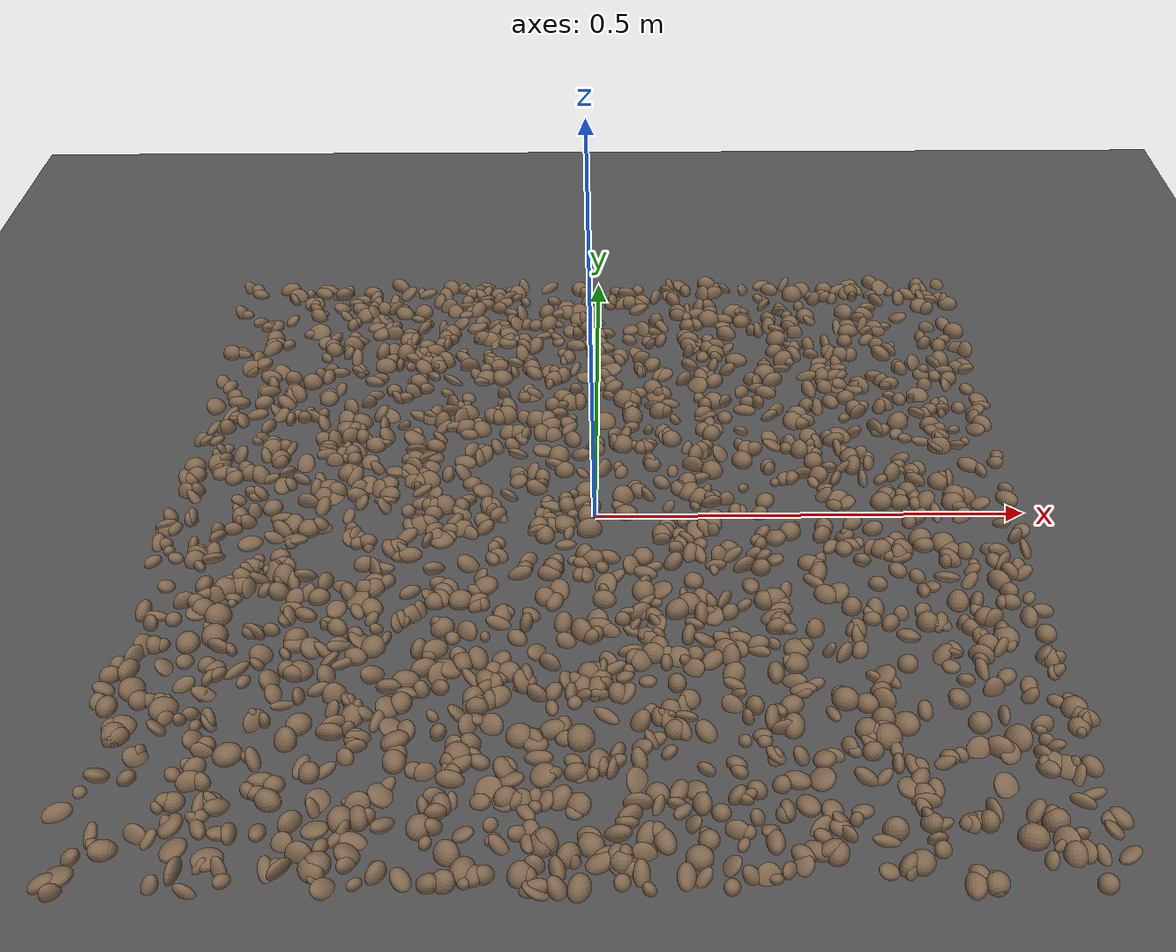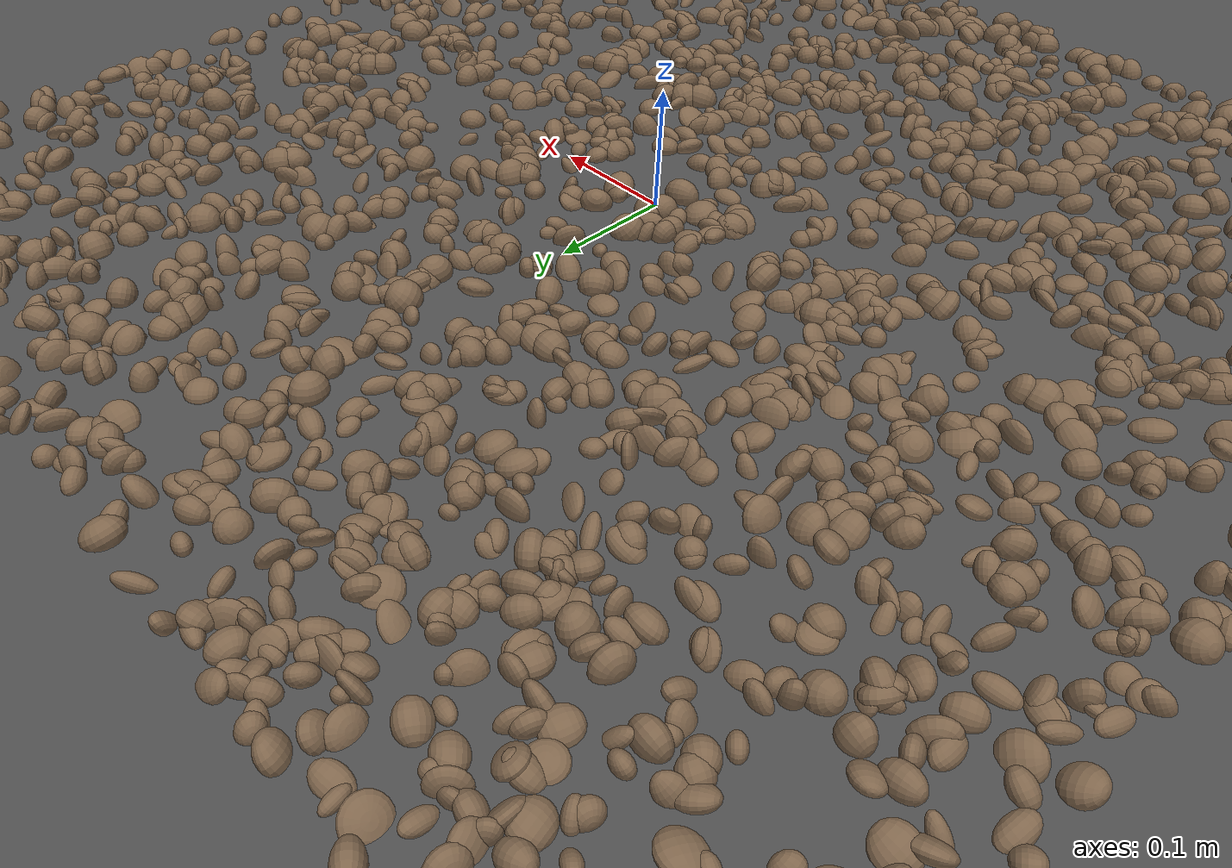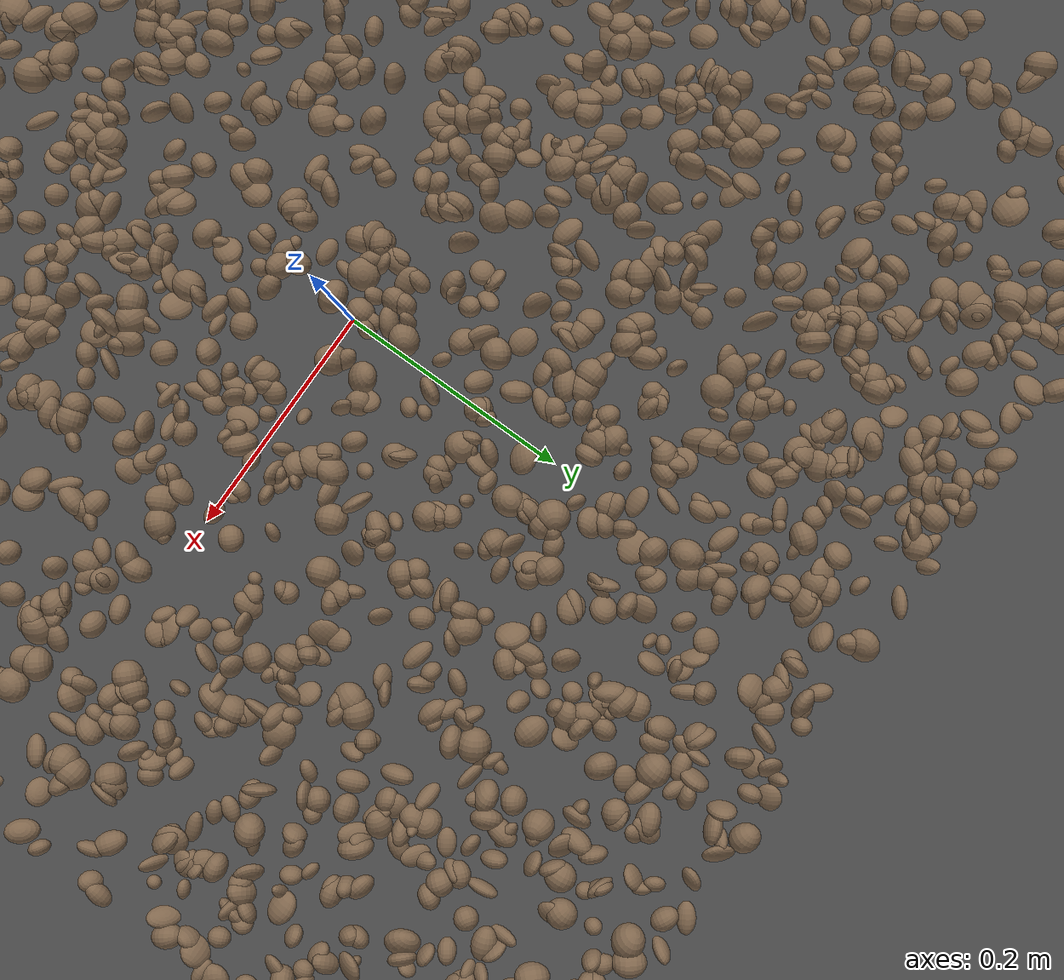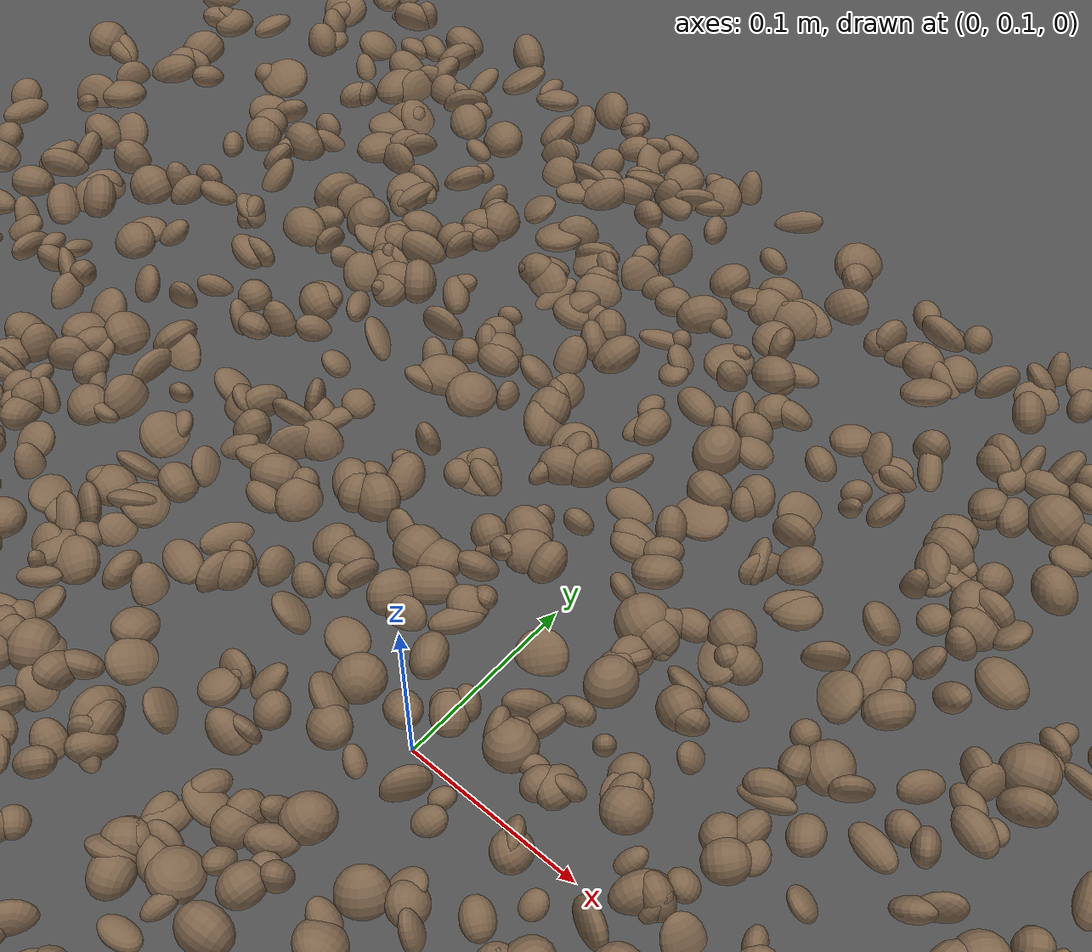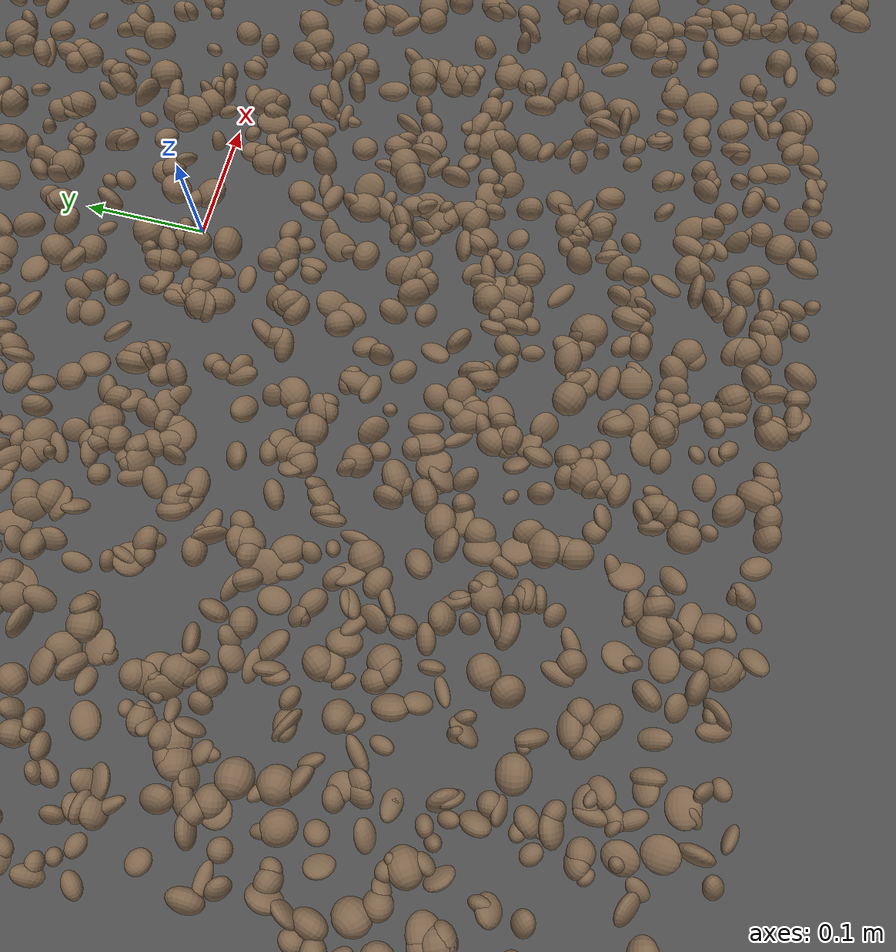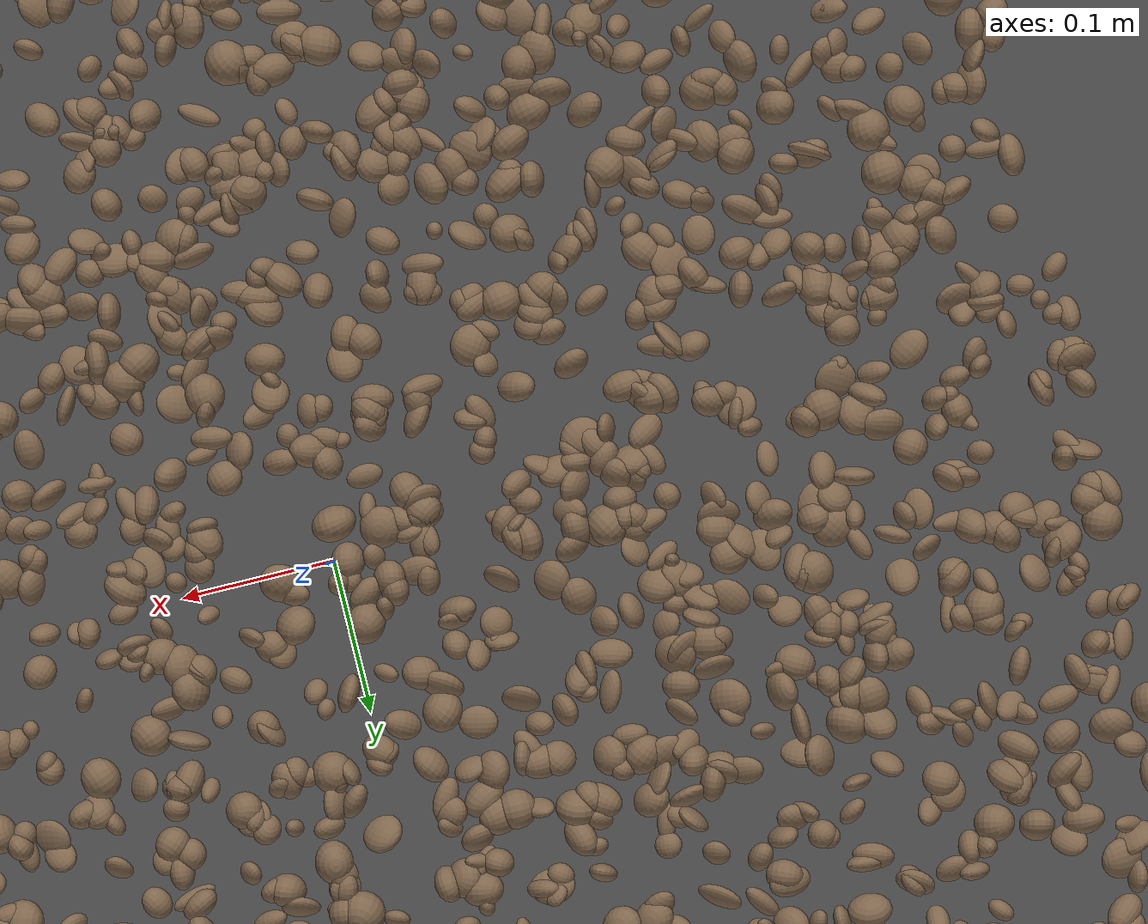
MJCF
<mujoco model="rocky_terrain_scene">
    <compiler angle="radian" inertiafromgeom="true" />
    <option timestep="0.002" gravity="0 0 -9.81" />

    <worldbody>
        <light name="sunlight" pos="5 5 5" dir="-1 -1 -1" diffuse="1 1 1" specular="0.5 0.5 0.5" ambient="0.5 0.5 0.5" />

        <geom name="ground_plane" type="plane" size="50 50 0.1" rgba="0.3 0.3 0.3 1" />

        <body name="rocky_terrain_body">

        </body>
    <body name="rock1" pos="-0.16550683763212692 -0.17492072252211865 0.0005621688638987118"><joint type="free" /><geom type="ellipsoid" size="0.012747610025219104 0.01147205556554834 0.0069530196312639625" quat="0.3205509046862007 0.013482181085299525 0.40760336511598155 0.2583635491125183" rgba="0.5 0.4 0.3 1" /></body><body name="rock2" pos="0.4556520354020843 -0.34114960358456026 0.0006647793984290535"><joint type="free" /><geom type="ellipsoid" size="0.005797627618156536 0.010468681799630276 0.007145967367133599" quat="0.01589560811626029 0.35319004741327653 0.32741707768227163 0.30349726678819156" rgba="0.5 0.4 0.3 1" /></body><body name="rock3" pos="-0.02826927219062636 -0.400239304044385 0.0002847148375290842"><joint type="free" /><geom type="ellipsoid" size="0.01471618659230444 0.01054738732494217 0.010466877497116672" quat="0.2737174406264115 0.41245017058757594 0.02947256411810981 0.28435982466790266" rgba="0.5 0.4 0.3 1" /></body><body name="rock4" pos="-0.15662035317593137 0.017174225262406306 0.0008324450861945396"><joint type="free" /><geom type="ellipsoid" size="0.010888355093595923 0.014742212137337 0.009646703932680866" quat="0.15069043716701272 0.3556634808424595 0.16783105882329555 0.3258150231672322" rgba="0.5 0.4 0.3 1" /></body><body name="rock5" pos="0.026005301600456887 -0.34638525040099666 0.0009059227171332191"><joint type="free" /><geom type="ellipsoid" size="0.011630974831517829 0.010913272073353113 0.006626976311411816" quat="0.3856733477731347 0.21418429437494862 0.3715866169800153 0.0285557408719013" rgba="0.5 0.4 0.3 1" /></body><body name="rock6" pos="-0.3711276829783894 0.4753574677900967 0.0002462682831380636"><joint type="free" /><geom type="ellipsoid" size="0.0073208735813529505 0.005008543418644278 0.011910694867485734" quat="0.36910758369971214 0.0794947128637117 0.20348760187023077 0.3479101015663455" rgba="0.5 0.4 0.3 1" /></body><body name="rock7" pos="-0.4567819198571499 0.18925834617387405 0.00026014834024594923"><joint type="free" /><geom type="ellipsoid" size="0.008813867959673871 0.005248183839121554 0.010474852389231928" quat="0.3417303140932314 0.1861842599779893 0.364948168527547 0.10713725740123228" rgba="0.5 0.4 0.3 1" /></body><body name="rock8" pos="-0.19618638159670354 0.3628638019211592 0.00017416740121737107"><joint type="free" /><geom type="ellipsoid" size="0.01272510894675458 0.0074008768560809395 0.006201073279864598" quat="0.3891938966006101 0.12872629887187348 0.35692957765787964 0.12515022686963692" rgba="0.5 0.4 0.3 1" /></body><body name="rock9" pos="-0.382632232754612 0.38110402536351073 0.0008264036266941106"><joint type="free" /><geom type="ellipsoid" size="0.01466785035450928 0.007664914295687946 0.01491511347530684" quat="0.25412747798161744 0.3500370829196973 0.15781914400070263 0.23801629509798267" rgba="0.5 0.4 0.3 1" /></body><body name="rock10" pos="0.0879055165618885 -0.4862004806389415 0.00016648745179495317"><joint type="free" /><geom type="ellipsoid" size="0.01382929347744729 0.007870012818236365 0.009399422317430555" quat="0.11878089334949594 0.3626204869599275 0.2998402775260559 0.21875834216452067" rgba="0.5 0.4 0.3 1" /></body><body name="rock11" pos="0.10856416873226138 -0.1737697051550402 3.781697432031306e-05"><joint type="free" /><geom type="ellipsoid" size="0.011722811077728044 0.009524593832183702 0.005908977177946962" quat="0.19188588442072008 0.022458187234689078 0.2964453810699134 0.48921054727467744" rgba="0.5 0.4 0.3 1" /></body><body name="rock12" pos="0.2969814199676648 0.3069636628985112 0.0003169636017170595"><joint type="free" /><geom type="ellipsoid" size="0.008000980383421731 0.005326822367112009 0.01222798241128774" quat="0.18427905555891524 0.1683701699875161 0.3399982664897413 0.30735250796382735" rgba="0.5 0.4 0.3 1" /></body><body name="rock13" pos="-0.19485329911288674 0.02626832783806632 0.00023408638913060577"><joint type="free" /><geom type="ellipsoid" size="0.00975785294334637 0.007849036944581042 0.009539292770499964" quat="0.35257943108855183 0.14416723206008003 0.29582129700070053 0.2074320398506676" rgba="0.5 0.4 0.3 1" /></body><body name="rock14" pos="-0.0322478401681614 0.18397923475634104 0.0004289539555968519"><joint type="free" /><geom type="ellipsoid" size="0.006125510128656902 0.011009196879387676 0.006497515640180974" quat="0.0796684686553793 0.34274794542929554 0.2783790923069262 0.299204493608399" rgba="0.5 0.4 0.3 1" /></body><body name="rock15" pos="0.1734840053105854 -0.2131245537021832 0.00037824182544149356"><joint type="free" /><geom type="ellipsoid" size="0.014581839174028211 0.00697238096978069 0.006259720581987799" quat="0.13710107625419402 0.049317380286334755 0.3949253752162964 0.4186561682431749" rgba="0.5 0.4 0.3 1" /></body><body name="rock16" pos="-0.20300506264730755 0.3125544716749742 0.00022687254627001087"><joint type="free" /><geom type="ellipsoid" size="0.010900618081054527 0.008750281544778728 0.0057541349559191565" quat="0.1926093741134463 0.42371594614812297 0.22500285262594333 0.15867182711248737" rgba="0.5 0.4 0.3 1" /></body><body name="rock17" pos="0.12245851001359431 0.03236861944276892 0.00026854294946992177"><joint type="free" /><geom type="ellipsoid" size="0.011765239654985483 0.012963441628562243 0.010901833869949997" quat="0.14658957052756744 0.34944230725971687 0.423170691943836 0.08079743026887981" rgba="0.5 0.4 0.3 1" /></body><body name="rock18" pos="-0.14916437440367047 0.17313505194270895 0.0003960572078800175"><joint type="free" /><geom type="ellipsoid" size="0.008748971151407634 0.010530532808195839 0.007947008959388428" quat="0.09710328886171109 0.2148329284389696 0.39915868031566515 0.28890510238365424" rgba="0.5 0.4 0.3 1" /></body><body name="rock19" pos="0.38212832127291185 0.25532636659045793 0.00012985598321369797"><joint type="free" /><geom type="ellipsoid" size="0.011266975380143896 0.009151981862128497 0.013422958389663574" quat="0.43661120547503596 0.007502565875814194 0.43456128871180394 0.1213249399373459" rgba="0.5 0.4 0.3 1" /></body><body name="rock20" pos="0.3944667652607261 0.45377800515021605 0.00024024003561126916"><joint type="free" /><geom type="ellipsoid" size="0.012744745067188427 0.01149280519727917 0.006265483755946584" quat="0.0486985986476126 0.24783593828230738 0.2600147942919295 0.44345066877815054" rgba="0.5 0.4 0.3 1" /></body><body name="rock21" pos="0.44694576391897334 -0.263819254130643 1.9517236295305886e-05"><joint type="free" /><geom type="ellipsoid" size="0.008542049623040704 0.012426577858683853 0.00676112575452158" quat="0.14875719260242015 0.0003789066352578428 0.001797227910106869 0.8490666728522152" rgba="0.5 0.4 0.3 1" /></body><body name="rock22" pos="0.011926124759406576 -0.13700042949088442 0.00018018746800011276"><joint type="free" /><geom type="ellipsoid" size="0.010696896295884654 0.013097862785373428 0.0113327333959325" quat="0.49543274237161744 0.02594371315708261 0.04711904354794162 0.43150450092335824" rgba="0.5 0.4 0.3 1" /></body><body name="rock23" pos="0.31795960331077844 -0.4308598133339957 0.00015601261616206454"><joint type="free" /><geom type="ellipsoid" size="0.00989754246596134 0.010262791112997657 0.012862174368614525" quat="0.4269229480384186 0.1560124204447702 0.015341334121593886 0.40172329739521734" rgba="0.5 0.4 0.3 1" /></body><body name="rock24" pos="-0.4572314784968594 -0.044632653806710554 0.0009278010146977645"><joint type="free" /><geom type="ellipsoid" size="0.009446700445254655 0.010424924641017668 0.005537153561798584" quat="0.19836882096043398 0.28474834489686873 0.30374565591076075 0.21313717823193645" rgba="0.5 0.4 0.3 1" /></body><body name="rock25" pos="0.2030656907377424 -0.15561577782825153 0.0009294656426564424"><joint type="free" /><geom type="ellipsoid" size="0.0087539182302174 0.009132940841257372 0.013790927689274955" quat="0.2753586764943911 0.10325730592406353 0.4127809251965154 0.20860309238503" rgba="0.5 0.4 0.3 1" /></body><body name="rock26" pos="-0.02601965105039472 0.003230492718905853 3.678270561016461e-05"><joint type="free" /><geom type="ellipsoid" size="0.006277202077853454 0.009865568390334502 0.007389244336439563" quat="0.061722663602259864 0.2731874572919832 0.205350069619618 0.45973980948613896" rgba="0.5 0.4 0.3 1" /></body><body name="rock27" pos="0.35028768670033794 -0.060043796649617676 0.0008374328758003326"><joint type="free" /><geom type="ellipsoid" size="0.013185290011714305 0.010414461350089312 0.01468956312008118" quat="0.058804563216060785 0.29834113209992724 0.4249244041722669 0.21792990051174502" rgba="0.5 0.4 0.3 1" /></body><body name="rock28" pos="0.24923770016408897 0.0723911118797882 0.0007895449151420873"><joint type="free" /><geom type="ellipsoid" size="0.005096817423747366 0.012793025802285054 0.012717252627388098" quat="0.42104035872750656 0.07892858121401407 0.0008909696370416684 0.49914009042143775" rgba="0.5 0.4 0.3 1" /></body><body name="rock29" pos="-0.37022247115336915 -0.41896184795224056 0.000676903720550978"><joint type="free" /><geom type="ellipsoid" size="0.008031280981743199 0.007721751991393154 0.005086686390123931" quat="0.07621595661207052 0.10056265471907849 0.40137074754311747 0.4218506411257336" rgba="0.5 0.4 0.3 1" /></body><body name="rock30" pos="-0.3998546890930903 -0.22847153443899337 0.00023820933590284942"><joint type="free" /><geom type="ellipsoid" size="0.008175075378124043 0.010033042677266759 0.009273780455367683" quat="0.17517288526517522 0.29730614365547975 0.41363443476031414 0.1138865363190309" rgba="0.5 0.4 0.3 1" /></body><body name="rock31" pos="0.299521198143759 -0.2510926312178354 0.0005596282214337648"><joint type="free" /><geom type="ellipsoid" size="0.014895027202764151 0.0076733534188838486 0.014582552155703556" quat="0.38521669371927225 0.1824653143012892 0.12928311152807104 0.3030348804513675" rgba="0.5 0.4 0.3 1" /></body><body name="rock32" pos="0.08504437409541943 0.35744116017397576 0.0004356627731316467"><joint type="free" /><geom type="ellipsoid" size="0.013538191717294288 0.01160913496985361 0.0066626433321148905" quat="0.2698048829298062 0.200232768214688 0.426976182463881 0.10298616639162472" rgba="0.5 0.4 0.3 1" /></body><body name="rock33" pos="0.05722145189131067 -0.09611618309081615 0.0009840225448664816"><joint type="free" /><geom type="ellipsoid" size="0.007575314170081305 0.007728514555862745 0.013793379007266557" quat="0.25595043623968644 0.2879895500630192 0.259238578284323 0.19682143541297129" rgba="0.5 0.4 0.3 1" /></body><body name="rock34" pos="-0.3292869309714509 -0.01945197731205739 0.0007255382053264796"><joint type="free" /><geom type="ellipsoid" size="0.014121294700903574 0.011671170171000087 0.013296735313800552" quat="0.3017184170629277 0.1702480253359375 0.3184783138420477 0.2095552437590871" rgba="0.5 0.4 0.3 1" /></body><body name="rock35" pos="-0.17367291510818228 -0.2650630946374427 0.0007491359712630255"><joint type="free" /><geom type="ellipsoid" size="0.008265174386779577 0.01137222547489594 0.008408322742346305" quat="0.47932702155462337 0.36730811380394734 0.0503269451970715 0.1030379194443578" rgba="0.5 0.4 0.3 1" /></body><body name="rock36" pos="-0.4578004622768811 0.12500826580981494 0.00044772015289045976"><joint type="free" /><geom type="ellipsoid" size="0.011953854872384982 0.007210330859389686 0.006918318322559339" quat="0.4139574534998519 0.32226800148386253 0.10442007339975959 0.15935447161652597" rgba="0.5 0.4 0.3 1" /></body><body name="rock37" pos="0.2547822073069872 0.4277699460255794 0.0003712388266150851"><joint type="free" /><geom type="ellipsoid" size="0.00530969060666503 0.014195818443009354 0.010692175053940468" quat="0.15443829273901613 0.39365023244876446 0.2544639028689243 0.19744757194329512" rgba="0.5 0.4 0.3 1" /></body><body name="rock38" pos="-0.3591664833303928 -0.0224232606305661 0.0006649970689287784"><joint type="free" /><geom type="ellipsoid" size="0.007230363493445895 0.01462237062204767 0.010274984232394705" quat="0.4702333891871439 0.13632889875809334 0.13071321733369184 0.2627244947210709" rgba="0.5 0.4 0.3 1" /></body><body name="rock39" pos="0.04557705297865433 0.3829624501925817 0.000565550572654849"><joint type="free" /><geom type="ellipsoid" size="0.010990843374032354 0.0072862136564385135 0.01153037480909078" quat="0.19737261361009184 0.09290134018545616 0.37847481157813717 0.3312512346263148" rgba="0.5 0.4 0.3 1" /></body><body name="rock40" pos="0.12311147187191152 -0.41742645309589665 0.0006714572377274129"><joint type="free" /><geom type="ellipsoid" size="0.008982776263692278 0.009547488148720907 0.009322637297927042" quat="0.24976047136378374 0.37840517979474575 0.03739853091533801 0.33443581792613253" rgba="0.5 0.4 0.3 1" /></body><body name="rock41" pos="0.13211799273828595 0.22670692887825084 0.0008224537758260441"><joint type="free" /><geom type="ellipsoid" size="0.007343599691714683 0.007905229792941317 0.007304201184494554" quat="0.3182140776106034 0.2981056545027388 0.21916114674555354 0.16451912114110434" rgba="0.5 0.4 0.3 1" /></body><body name="rock42" pos="0.42661728681924316 -0.2521981396229498 0.00043188203256500535"><joint type="free" /><geom type="ellipsoid" size="0.011807165000449388 0.008434975401839932 0.008945751826741611" quat="0.3765038820389106 0.34028482475187377 0.15462781601188236 0.12858347719733323" rgba="0.5 0.4 0.3 1" /></body><body name="rock43" pos="0.3050495187347241 0.45557851853925935 0.0006774635485423901"><joint type="free" /><geom type="ellipsoid" size="0.007321660383301256 0.014609903702735218 0.008609915797743502" quat="0.28936884957501935 0.31559460559511404 0.25219860849182646 0.14283793633804015" rgba="0.5 0.4 0.3 1" /></body><body name="rock44" pos="0.05975169963302185 -0.19491940056660062 0.0002959576022186135"><joint type="free" /><geom type="ellipsoid" size="0.008815507939890554 0.014171670566327052 0.00887521716916091" quat="0.06462511110890946 0.601036928079059 0.31940130172115405 0.014936659090877555" rgba="0.5 0.4 0.3 1" /></body><body name="rock45" pos="-0.4718661935949974 -0.46057707784764823 0.0001963285371326885"><joint type="free" /><geom type="ellipsoid" size="0.008729334590424425 0.007399780428837405 0.013434453673085513" quat="0.4013400236216499 0.1514899338168537 0.09543633473033068 0.35173370783116564" rgba="0.5 0.4 0.3 1" /></body><body name="rock46" pos="0.3564599828154469 0.47400490395862793 0.000917062896838179"><joint type="free" /><geom type="ellipsoid" size="0.013406958610333409 0.008484826180671829 0.012241586656080317" quat="0.30854892831709707 0.4723685760134401 0.09733221882225704 0.12175027684720573" rgba="0.5 0.4 0.3 1" /></body><body name="rock47" pos="0.4292531631856713 -0.003832037997222537 7.085391001074359e-05"><joint type="free" /><geom type="ellipsoid" size="0.009113174151917222 0.007078059357515045 0.013825923985994481" quat="0.037143716145348525 0.2687434751224994 0.25251394353509315 0.44159886519705877" rgba="0.5 0.4 0.3 1" /></body><body name="rock48" pos="-0.04728299074169062 0.1950820068381759 0.00010837655658667323"><joint type="free" /><geom type="ellipsoid" size="0.013139562807008821 0.007308756028869265 0.010873072463701668" quat="0.4675138128188551 0.06007311662765434 0.3396607163549945 0.13275235419849607" rgba="0.5 0.4 0.3 1" /></body><body name="rock49" pos="-0.04126398846450452 0.42944753139992564 0.0001236958981535349"><joint type="free" /><geom type="ellipsoid" size="0.005644349080169624 0.00737760905722798 0.0090625914877604" quat="0.28054176471085457 0.4145821167565239 0.15490544462287628 0.14997067390974514" rgba="0.5 0.4 0.3 1" /></body><body name="rock50" pos="-0.02872390728578167 -0.4772345216704479 0.00045308087668553154"><joint type="free" /><geom type="ellipsoid" size="0.013340068852176187 0.011933588663766505 0.007355893075518786" quat="0.21349711906890498 0.2138824334436172 0.2862827110708641 0.28633773641661364" rgba="0.5 0.4 0.3 1" /></body><body name="rock51" pos="-0.2997530358317735 -0.1308685069339891 0.0006744083941133959"><joint type="free" /><geom type="ellipsoid" size="0.010384900497924902 0.011161172996123056 0.0118462704286014" quat="0.18000863063915798 0.2598032525374169 0.23560763054073464 0.32458048628269054" rgba="0.5 0.4 0.3 1" /></body><body name="rock52" pos="-0.15849611445042533 -0.43096476764283687 0.0004378944964952256"><joint type="free" /><geom type="ellipsoid" size="0.01326522911578007 0.012538453152416595 0.011722423377842364" quat="0.10168703359579209 0.4069727435503372 0.3116390663244553 0.17970115652941548" rgba="0.5 0.4 0.3 1" /></body><body name="rock53" pos="-0.31371112468854756 0.44177768473695256 0.0005503183809870167"><joint type="free" /><geom type="ellipsoid" size="0.008815431262890857 0.012008236070632547 0.006122306917487804" quat="0.3209662314469524 0.3961729625862107 0.04147705824669273 0.2413837477201441" rgba="0.5 0.4 0.3 1" /></body><body name="rock54" pos="-0.28088468647769316 -0.020061183884499956 2.840496089686162e-05"><joint type="free" /><geom type="ellipsoid" size="0.006363194642605825 0.0110879716472305 0.007336239913521794" quat="0.1905184943591717 0.3006033424137728 0.3079371317471809 0.20094103147987458" rgba="0.5 0.4 0.3 1" /></body><body name="rock55" pos="-0.0506281197274302 -0.3519737152727447 0.0009851160007481857"><joint type="free" /><geom type="ellipsoid" size="0.008547691927139573 0.007861999731002498 0.014780074424976045" quat="0.42315883041837493 0.154076539884585 0.2953383581071181 0.12742627158992192" rgba="0.5 0.4 0.3 1" /></body><body name="rock56" pos="-0.11033382854108742 0.15735672969608283 0.000613748554492212"><joint type="free" /><geom type="ellipsoid" size="0.011893404294957914 0.008986120619373565 0.011486870542098397" quat="0.3607956067812675 0.39810660269061676 0.009712083626200383 0.23138570690191546" rgba="0.5 0.4 0.3 1" /></body><body name="rock57" pos="0.29906688295515216 -0.16371804285101144 0.0008541486804333912"><joint type="free" /><geom type="ellipsoid" size="0.006539420021596308 0.006397500317298137 0.010709229963152406" quat="0.19661031655015143 0.5289257293898783 0.13652054594352933 0.13794340811644099" rgba="0.5 0.4 0.3 1" /></body><body name="rock58" pos="-0.33932407348818017 0.28760380849270595 0.0004301615522512333"><joint type="free" /><geom type="ellipsoid" size="0.011950929044200668 0.0064649051587690265 0.009208180893568195" quat="0.5661124334190833 0.20948371247608022 0.1539213378554327 0.07048251624940377" rgba="0.5 0.4 0.3 1" /></body><body name="rock59" pos="0.3711840224626226 -0.42990879775890567 0.0008440068206741294"><joint type="free" /><geom type="ellipsoid" size="0.011179226565703275 0.013787692693466184 0.009735498338035043" quat="0.20194108987942577 0.29969801933492346 0.1979388974636876 0.30042199332196323" rgba="0.5 0.4 0.3 1" /></body><body name="rock60" pos="0.34089050861012826 0.2060610162702483 0.0007824126980360998"><joint type="free" /><geom type="ellipsoid" size="0.0078386980001686 0.008892267475108592 0.008298518796836993" quat="0.11198152077813132 0.18017110870375994 0.4737363324247412 0.23411103809336756" rgba="0.5 0.4 0.3 1" /></body><body name="rock61" pos="-0.4684031618538895 -0.3230609801286377 7.471958248411636e-05"><joint type="free" /><geom type="ellipsoid" size="0.010169411431881402 0.01251708114779779 0.013903599143686551" quat="0.24272327639364719 0.1528986347722391 0.20700148769945664 0.39737660113465706" rgba="0.5 0.4 0.3 1" /></body><body name="rock62" pos="-0.13020732349602715 -0.45996626980894073 0.0009363179748354242"><joint type="free" /><geom type="ellipsoid" size="0.013474791058198494 0.010292859613153205 0.013302937322519831" quat="0.21355753021967935 0.060714523171207964 0.15852140340036613 0.5672065432087465" rgba="0.5 0.4 0.3 1" /></body><body name="rock63" pos="0.23683746766654967 -0.18427162541141617 0.0006823139448390269"><joint type="free" /><geom type="ellipsoid" size="0.010316363593592042 0.012850527792422867 0.008475188499093499" quat="0.5022413645529681 0.3105342082536532 0.11912065655821927 0.06810377063515949" rgba="0.5 0.4 0.3 1" /></body><body name="rock64" pos="-0.3855145553870579 0.1324834496402325 0.00021238540377967419"><joint type="free" /><geom type="ellipsoid" size="0.008988025957674405 0.012638100142493 0.008344606062226863" quat="0.09947545341571078 0.34707925272635065 0.2830471160051932 0.2703981778527454" rgba="0.5 0.4 0.3 1" /></body><body name="rock65" pos="-0.1707076220756123 -0.36513867597115857 0.0001496745732750031"><joint type="free" /><geom type="ellipsoid" size="0.009050563500511161 0.008118607910671812 0.009050707284912043" quat="0.28042888974958524 0.28954431283977033 0.2618282888324251 0.16819850857821922" rgba="0.5 0.4 0.3 1" /></body><body name="rock66" pos="0.2213157087472979 0.2796210139882699 9.463001372737811e-05"><joint type="free" /><geom type="ellipsoid" size="0.01361561721344166 0.014626117276371444 0.014736234190519563" quat="0.07668166132619761 0.32728640836008527 0.29502677389434573 0.3010051564193713" rgba="0.5 0.4 0.3 1" /></body><body name="rock67" pos="-0.2575495858597635 -0.079575398984992 0.00014037474683925455"><joint type="free" /><geom type="ellipsoid" size="0.009345562357577872 0.011822554700374889 0.011135945146472667" quat="0.08965623974164542 0.3814709290993434 0.4993373098459526 0.02953552131305861" rgba="0.5 0.4 0.3 1" /></body><body name="rock68" pos="-0.32236555042934056 0.31791320549732005 0.0005919907256262036"><joint type="free" /><geom type="ellipsoid" size="0.014747980116509702 0.006843066009593108 0.007544193500442895" quat="0.23048423798627957 0.3211208796413648 0.08835590113191401 0.3600389812404417" rgba="0.5 0.4 0.3 1" /></body><body name="rock69" pos="0.1467043919614074 -0.40228023124166223 2.7640819991880728e-05"><joint type="free" /><geom type="ellipsoid" size="0.0086114596052819 0.009373037864173529 0.005274071470218605" quat="0.08948146906569235 0.03555387904081951 0.3745659537104493 0.5003986981830388" rgba="0.5 0.4 0.3 1" /></body><body name="rock70" pos="-0.19817704350386212 -0.3946542931735936 0.0009194676917571609"><joint type="free" /><geom type="ellipsoid" size="0.013045669395952718 0.00606512392555852 0.014069552494883442" quat="0.33704814239380165 0.3818346829719215 0.23301458539174916 0.04810258924252769" rgba="0.5 0.4 0.3 1" /></body><body name="rock71" pos="0.2942716357669142 0.40776098956026974 0.0004364824254915475"><joint type="free" /><geom type="ellipsoid" size="0.011761338815416314 0.005714156742862968 0.011924225888967374" quat="0.171950016998088 0.35626723793099246 0.3465938308334128 0.12518891423750672" rgba="0.5 0.4 0.3 1" /></body><body name="rock72" pos="0.3838466502333039 -0.25637402461733194 0.0009189242154246517"><joint type="free" /><geom type="ellipsoid" size="0.0104213732403231 0.00710918602170525 0.009247699683004727" quat="0.4128172542290722 0.16312879826854956 0.35065479195831095 0.07339915554406728" rgba="0.5 0.4 0.3 1" /></body><body name="rock73" pos="0.2677703255865471 -0.12926742653194911 0.0006533916772292538"><joint type="free" /><geom type="ellipsoid" size="0.012835789752039937 0.013438609837134005 0.008079463782246237" quat="0.10062127531552661 0.30459993957411 0.48497965071946825 0.10979913439089517" rgba="0.5 0.4 0.3 1" /></body><body name="rock74" pos="-0.04825173526836546 -0.4973367522239788 0.0005549705641132744"><joint type="free" /><geom type="ellipsoid" size="0.007726687962441125 0.010174523798651613 0.014985045570121362" quat="0.2917324207094132 0.173301911881346 0.23651675259813554 0.29844891481110536" rgba="0.5 0.4 0.3 1" /></body><body name="rock75" pos="0.1088315938008022 -0.06481057705459947 0.00023856627725216185"><joint type="free" /><geom type="ellipsoid" size="0.013567209471671431 0.010058320330763603 0.008479245489809564" quat="0.27310068151851236 0.3097170919539041 0.10677446594916493 0.31040776057841857" rgba="0.5 0.4 0.3 1" /></body><body name="rock76" pos="0.2921084850644472 -0.32920693248175503 8.867549084327508e-05"><joint type="free" /><geom type="ellipsoid" size="0.01469451505772008 0.013677542211409408 0.014897469724517103" quat="0.13217215409779418 0.32562724041310076 0.2838714054455763 0.2583292000435286" rgba="0.5 0.4 0.3 1" /></body><body name="rock77" pos="-0.10481992569435061 -0.48364710246768006 0.0007836075731590213"><joint type="free" /><geom type="ellipsoid" size="0.010927368207925444 0.011514237380924658 0.00909086153998284" quat="0.08736354109467652 0.5165765442043079 0.255644659593446 0.1404152551075697" rgba="0.5 0.4 0.3 1" /></body><body name="rock78" pos="0.3277472619791213 -0.23371095554004617 6.756022330364398e-05"><joint type="free" /><geom type="ellipsoid" size="0.010664371356981305 0.011269371541972252 0.010920862230448282" quat="0.10902797597453986 0.13854047463380634 0.21363980100813487 0.5387917483835188" rgba="0.5 0.4 0.3 1" /></body><body name="rock79" pos="-0.1305304776235796 0.19021768185220123 0.00048748281191469945"><joint type="free" /><geom type="ellipsoid" size="0.010711460319485755 0.010374494435292092 0.014013677669073896" quat="0.2385510162780245 0.4603404313372072 0.0014721408305153273 0.29963641155425297" rgba="0.5 0.4 0.3 1" /></body><body name="rock80" pos="-0.045809371576640334 -0.08887382039448999 0.0005930225444622922"><joint type="free" /><geom type="ellipsoid" size="0.01268975429654185 0.014473546433665156 0.010405119188540618" quat="0.10500385512585561 0.2222778150855329 0.31475440351746686 0.3579639262711446" rgba="0.5 0.4 0.3 1" /></body><body name="rock81" pos="-0.21168948925054232 0.30096046985530334 0.0008517919229240109"><joint type="free" /><geom type="ellipsoid" size="0.013768267162601117 0.010538673720187176 0.009809200939137168" quat="0.06323493095569388 0.29435567166952187 0.5467716844560996 0.09563771291868468" rgba="0.5 0.4 0.3 1" /></body><body name="rock82" pos="-0.3128190474134315 -0.20059505266637534 0.0008415279797041393"><joint type="free" /><geom type="ellipsoid" size="0.013396475597231419 0.008654973135278143 0.011576457467660619" quat="0.4747243940471018 0.3179439803365507 0.15122411485311385 0.05610751076323367" rgba="0.5 0.4 0.3 1" /></body><body name="rock83" pos="-0.33130567097565733 0.06949751950377203 0.0005171865753410406"><joint type="free" /><geom type="ellipsoid" size="0.012359006403656534 0.006242607513565267 0.006176409533472614" quat="0.09362852099005883 0.3233551401608982 0.47130897126600246 0.11170736758304048" rgba="0.5 0.4 0.3 1" /></body><body name="rock84" pos="-0.20994248413142502 0.4404985564071112 0.0008741527373349374"><joint type="free" /><geom type="ellipsoid" size="0.005171801327083834 0.010731999767558162 0.014564060705455444" quat="0.40676399221354076 0.033421869629238155 0.17181257161891267 0.3880015665383085" rgba="0.5 0.4 0.3 1" /></body><body name="rock85" pos="-0.313194452074964 -0.1253916408247634 0.0005844234249975451"><joint type="free" /><geom type="ellipsoid" size="0.007311869724917774 0.012725918066018735 0.00783226225718157" quat="0.26088604471462246 0.24351651172347855 0.3812370656860773 0.11436037787582161" rgba="0.5 0.4 0.3 1" /></body><body name="rock86" pos="0.1275439197478827 -0.025014780502201406 0.0002205533603154627"><joint type="free" /><geom type="ellipsoid" size="0.008752715360752386 0.014637120442108773 0.007763105581458178" quat="0.4380769761522213 0.21736767953376265 0.12365611962824608 0.22089922468576995" rgba="0.5 0.4 0.3 1" /></body><body name="rock87" pos="0.4928169202314322 -0.467140433339964 0.0007903657298378525"><joint type="free" /><geom type="ellipsoid" size="0.013748237473734683 0.008307241937530022 0.0054990633870965686" quat="0.14896246365159066 0.5930701285671808 0.21800464482106602 0.03996276296016252" rgba="0.5 0.4 0.3 1" /></body><body name="rock88" pos="0.04267764048739742 0.20672745121605485 0.0006946659206726775"><joint type="free" /><geom type="ellipsoid" size="0.012053809450994536 0.005611863519559833 0.010705820099771063" quat="0.25495764585138236 0.002026565105341366 0.42249168824598204 0.32052410079729415" rgba="0.5 0.4 0.3 1" /></body><body name="rock89" pos="-0.15651722090151376 0.3676127656079641 0.0005278480050498478"><joint type="free" /><geom type="ellipsoid" size="0.014629747824903522 0.007994255607222701 0.011721821671357914" quat="0.5229595289192714 0.20460347790876512 0.10128551057248945 0.17115148259947402" rgba="0.5 0.4 0.3 1" /></body><body name="rock90" pos="0.0991936895848442 -0.28052890938158137 0.0009192276444487203"><joint type="free" /><geom type="ellipsoid" size="0.011460672430448713 0.009249036593722351 0.011817511558084342" quat="0.025969040902992867 0.31031160947615505 0.3274469592212592 0.3362723903995929" rgba="0.5 0.4 0.3 1" /></body><body name="rock91" pos="0.3791818662613561 0.3450558430414148 0.0008488170631526018"><joint type="free" /><geom type="ellipsoid" size="0.005553456269839848 0.010304876376606747 0.009859405281974595" quat="0.2743677540366613 0.24781511419752134 0.31654317782423735 0.16127395394158003" rgba="0.5 0.4 0.3 1" /></body><body name="rock92" pos="0.22207674546111267 -0.37953206438827103 0.0006140443424594676"><joint type="free" /><geom type="ellipsoid" size="0.014732258359600264 0.007548602642298232 0.013451493374696616" quat="0.291555701352373 0.1432781935759045 0.2560078561126348 0.3091582489590878" rgba="0.5 0.4 0.3 1" /></body><body name="rock93" pos="0.19946639944694733 0.4035772718698952 0.0002750882983651307"><joint type="free" /><geom type="ellipsoid" size="0.011575587711426772 0.010455446365033589 0.012188905218150017" quat="0.13064734505753192 0.19146972226938816 0.3970706825186688 0.28081225015441114" rgba="0.5 0.4 0.3 1" /></body><body name="rock94" pos="-0.40166277260001815 -0.2934815091103018 0.00032349971489927654"><joint type="free" /><geom type="ellipsoid" size="0.006481830536606552 0.009428731266381784 0.007600279829730517" quat="0.24362629680874154 0.1466863925408627 0.20756411123881588 0.4021231994115799" rgba="0.5 0.4 0.3 1" /></body><body name="rock95" pos="0.021931562966147178 -0.3645757206052761 0.00031425319597846226"><joint type="free" /><geom type="ellipsoid" size="0.013071132218591897 0.012126522403746695 0.005395861870113316" quat="0.2713827426646401 0.3119760542802583 0.17331915539834813 0.2433220476567535" rgba="0.5 0.4 0.3 1" /></body><body name="rock96" pos="0.0418594523908179 -0.08395136298155204 0.0008742916234922684"><joint type="free" /><geom type="ellipsoid" size="0.012632221393144452 0.006757779717272561 0.011520783557070877" quat="0.15349498053760824 0.4177176809919242 0.30777552288467663 0.12101181558579094" rgba="0.5 0.4 0.3 1" /></body><body name="rock97" pos="0.2936266320978961 0.28554178950257525 0.0008304684430488065"><joint type="free" /><geom type="ellipsoid" size="0.01260929915707288 0.011495293527903943 0.01063430364936074" quat="0.09811578142309035 0.0028405146204329413 0.7948324076805917 0.10421129627588491" rgba="0.5 0.4 0.3 1" /></body><body name="rock98" pos="-0.2580277435774987 -0.22719022873392536 0.0004538454670498503"><joint type="free" /><geom type="ellipsoid" size="0.014918620036920589 0.006851154654500283 0.005198923232551727" quat="0.35114351280934586 0.42756426852869756 0.15445537236681822 0.06683684629513825" rgba="0.5 0.4 0.3 1" /></body><body name="rock99" pos="0.2031097757542254 0.2633719757033929 0.0006842621411020642"><joint type="free" /><geom type="ellipsoid" size="0.0066596788856836215 0.012487619208400481 0.011458779440947978" quat="0.35458143634074857 0.28372969458334263 0.19125559242872506 0.1704332766471838" rgba="0.5 0.4 0.3 1" /></body><body name="rock100" pos="-0.13645142353749007 0.11140812036139591 0.0009286935168471835"><joint type="free" /><geom type="ellipsoid" size="0.009866240421989261 0.014135812652580623 0.008644423234207686" quat="0.0481739037649131 0.1674497930052339 0.554923056651032 0.22945324657882113" rgba="0.5 0.4 0.3 1" /></body><body name="rock101" pos="0.2143894440955041 -0.434521650916717 0.0005083892194020818"><joint type="free" /><geom type="ellipsoid" size="0.005084766025185526 0.013369823910785936 0.008074816744729527" quat="0.22509544764950445 0.2634669104574167 0.4825633823336489 0.028874259559429852" rgba="0.5 0.4 0.3 1" /></body><body name="rock102" pos="0.4024014522214199 0.28717575315048716 0.000266504218135969"><joint type="free" /><geom type="ellipsoid" size="0.008226047948079027 0.013404532974554254 0.00889911951416637" quat="0.381375998698299 0.2750027370692377 0.1375296625544953 0.206091601677968" rgba="0.5 0.4 0.3 1" /></body><body name="rock103" pos="0.47579881229325915 -0.40054767698033666 0.000738749232192109"><joint type="free" /><geom type="ellipsoid" size="0.005676362919920186 0.014291339806941541 0.006313069743269381" quat="0.01422054724566466 0.4044878093320148 0.5277361159804538 0.053555527441866806" rgba="0.5 0.4 0.3 1" /></body><body name="rock104" pos="-0.1312375872717737 0.30159294541795134 7.66758446230309e-07"><joint type="free" /><geom type="ellipsoid" size="0.00999701263819341 0.010532613816175726 0.012850975017463663" quat="0.3139995165144341 0.20271698820201936 0.2994246140119006 0.1838588812716459" rgba="0.5 0.4 0.3 1" /></body><body name="rock105" pos="0.4263324710215982 0.030761442997363386 0.0007645073587500802"><joint type="free" /><geom type="ellipsoid" size="0.01381510882771526 0.014658405332588994 0.013627747115991132" quat="0.34605188330633685 0.1749080628721575 0.20111182556524249 0.2779282282562631" rgba="0.5 0.4 0.3 1" /></body><body name="rock106" pos="0.3206067159686108 0.46412679716625893 0.00026448639507604764"><joint type="free" /><geom type="ellipsoid" size="0.00859719610370366 0.008416446452162961 0.012265678651326162" quat="0.37432832643320074 0.1751488076488069 0.03853682923641068 0.4119860366815816" rgba="0.5 0.4 0.3 1" /></body><body name="rock107" pos="0.37050214124280323 0.20876813785063908 0.0007279122365828237"><joint type="free" /><geom type="ellipsoid" size="0.008050738297841028 0.013528958974535068 0.008964407916037795" quat="0.3324362882711377 0.10503191659291462 0.2258101551880694 0.33672163994787824" rgba="0.5 0.4 0.3 1" /></body><body name="rock108" pos="0.1771661919277987 0.0482231867541576 6.195953503682827e-05"><joint type="free" /><geom type="ellipsoid" size="0.009900590518765042 0.00634378374102017 0.005268070301264805" quat="0.4193678161792629 0.20669688301040315 0.282426843336217 0.09150845747411696" rgba="0.5 0.4 0.3 1" /></body><body name="rock109" pos="0.21433037195624827 -0.2118495862788311 2.0093494277806824e-05"><joint type="free" /><geom type="ellipsoid" size="0.012872781193765795 0.009755872811902764 0.013988720814325558" quat="0.2708377050361904 0.29327488761995085 0.21979842217339118 0.21608898517046757" rgba="0.5 0.4 0.3 1" /></body><body name="rock110" pos="0.37218526209630787 -0.2815544019145777 0.0007180840609156328"><joint type="free" /><geom type="ellipsoid" size="0.011709548371265468 0.014839808362935927 0.009717092397507836" quat="0.2383128347458045 0.16864067966061605 0.1344630775433605 0.45858340805021897" rgba="0.5 0.4 0.3 1" /></body><body name="rock111" pos="-0.010703801813250147 0.04327570462171948 0.0007232280284969454"><joint type="free" /><geom type="ellipsoid" size="0.012532750183705008 0.014026258586804154 0.013344418095966374" quat="0.16346764585622017 0.09176181922619031 0.17518128736289182 0.5695892475546978" rgba="0.5 0.4 0.3 1" /></body><body name="rock112" pos="-0.4668124052057363 -0.3099240536405774 0.0002574120674655216"><joint type="free" /><geom type="ellipsoid" size="0.013078312015501768 0.009231216308772413 0.014945398758200681" quat="0.14254026674689646 0.26903273930172367 0.2796075883307828 0.308819405620597" rgba="0.5 0.4 0.3 1" /></body><body name="rock113" pos="-0.16595668774695338 -0.2103573978025044 0.000462545431348111"><joint type="free" /><geom type="ellipsoid" size="0.010370614132710676 0.012462708103377997 0.01481273577549386" quat="0.2598613594662452 0.10488438372104528 0.3502680002647293 0.28498625654798015" rgba="0.5 0.4 0.3 1" /></body><body name="rock114" pos="0.4176728364761516 -0.20713932826631398 0.00035728998191586383"><joint type="free" /><geom type="ellipsoid" size="0.008481238723835629 0.006142017669367966 0.008083491195554501" quat="0.3247981675562281 0.17297167572606456 0.11010804624282143 0.3921221104748858" rgba="0.5 0.4 0.3 1" /></body><body name="rock115" pos="0.14152357055728837 -0.4530550360193848 0.000902874203455219"><joint type="free" /><geom type="ellipsoid" size="0.0051409915273627205 0.005379506060313026 0.007539925430139864" quat="0.22375565175808024 0.02102387573857408 0.3678409103854368 0.3873795621179089" rgba="0.5 0.4 0.3 1" /></body><body name="rock116" pos="0.27333669214303735 -0.4501696623832153 0.0008442722865731872"><joint type="free" /><geom type="ellipsoid" size="0.0057161051448112645 0.005804987857740085 0.014231319080025295" quat="0.28337984717660153 0.19172288241376825 0.3926437550713049 0.1322535153383254" rgba="0.5 0.4 0.3 1" /></body><body name="rock117" pos="-0.19260816562697292 0.1680346223864876 0.00012462332439807888"><joint type="free" /><geom type="ellipsoid" size="0.008325494003633298 0.006048465108101492 0.013478519060060156" quat="0.28546948580495424 0.09374788097184104 0.22896443493206403 0.39181819829114073" rgba="0.5 0.4 0.3 1" /></body><body name="rock118" pos="-0.24094173945650454 -0.11606788391359546 0.00032892751251558793"><joint type="free" /><geom type="ellipsoid" size="0.01452565397563469 0.011356940147603481 0.011788723818969785" quat="0.17367319215808064 0.444176600200627 0.33656081466603593 0.045589392975256354" rgba="0.5 0.4 0.3 1" /></body><body name="rock119" pos="0.012014596258610455 -0.259869100797405 0.0001864974031463017"><joint type="free" /><geom type="ellipsoid" size="0.006587347654475415 0.01290653217861008 0.010034433166422852" quat="0.19078759636547957 0.22922757153058876 0.28605296278612447 0.2939318693178071" rgba="0.5 0.4 0.3 1" /></body><body name="rock120" pos="-0.015307137194305653 -0.09795732240532373 0.00028121028675298355"><joint type="free" /><geom type="ellipsoid" size="0.007894305209533088 0.00845973986809894 0.009245120339013719" quat="0.17936809149168687 0.06232925935119897 0.47992907657975253 0.27837357257736156" rgba="0.5 0.4 0.3 1" /></body><body name="rock121" pos="-0.10908945664737624 0.28532818672462756 0.00035809339184047297"><joint type="free" /><geom type="ellipsoid" size="0.005018460246604343 0.008065471944530164 0.009624032972549032" quat="0.09867650834745434 0.747072996843555 0.06617310909569837 0.08807738571329227" rgba="0.5 0.4 0.3 1" /></body><body name="rock122" pos="-0.05419889330803074 -0.33530567822768587 0.0006829417820341358"><joint type="free" /><geom type="ellipsoid" size="0.00974865446352136 0.007843421557282036 0.012667359073926859" quat="0.22587701614107805 0.2625828587000424 0.25956651193719643 0.2519736132216832" rgba="0.5 0.4 0.3 1" /></body><body name="rock123" pos="0.4858899296809611 0.33624632190411585 0.0003545682812924572"><joint type="free" /><geom type="ellipsoid" size="0.005265830893990704 0.011360429017215292 0.009953507920887027" quat="0.1908342702524902 0.36098505508679346 0.3584772871880863 0.08970338747262996" rgba="0.5 0.4 0.3 1" /></body><body name="rock124" pos="0.3725581327023407 -0.0438707162171893 0.0008529723946938719"><joint type="free" /><geom type="ellipsoid" size="0.014150064543676746 0.013574196485402229 0.012296731587555326" quat="0.3817240315950364 0.3505974446906828 0.09955459342407706 0.16812393029020375" rgba="0.5 0.4 0.3 1" /></body><body name="rock125" pos="0.4639463083460157 0.20299743525199287 0.0003443971103361123"><joint type="free" /><geom type="ellipsoid" size="0.00861125760301635 0.008823390248393004 0.009398575617422302" quat="0.4434045222799933 0.3897953360669293 0.04013787939758486 0.1266622622554926" rgba="0.5 0.4 0.3 1" /></body><body name="rock126" pos="0.3942890370016091 0.38871275575636743 0.0008648120688358423"><joint type="free" /><geom type="ellipsoid" size="0.013218993495154891 0.0058963699927883076 0.01080310305126416" quat="0.33185782932386465 0.13795283764028057 0.3570756055000434 0.17311372753581133" rgba="0.5 0.4 0.3 1" /></body><body name="rock127" pos="-0.15646481888727637 -0.24402380729796458 0.00015673808762549157"><joint type="free" /><geom type="ellipsoid" size="0.006046490815063303 0.014011205806068017 0.013781863709586322" quat="0.2510470384997994 0.1362195390552879 0.48182518849380207 0.13090823395111062" rgba="0.5 0.4 0.3 1" /></body><body name="rock128" pos="-0.38228556631776056 -0.08139631910466294 4.362172707199763e-05"><joint type="free" /><geom type="ellipsoid" size="0.009556608680706527 0.01002219953562863 0.01200505757247131" quat="0.3489151825138318 0.14177331763938236 0.3690046325455556 0.14030686730123024" rgba="0.5 0.4 0.3 1" /></body><body name="rock129" pos="-0.3451214278461042 -0.12224514798202224 0.00016912916730703987"><joint type="free" /><geom type="ellipsoid" size="0.010651625867974633 0.013925789496263604 0.011091359492591798" quat="0.37282883204442774 0.36882800043272146 0.05751181916936783 0.20083134835348285" rgba="0.5 0.4 0.3 1" /></body><body name="rock130" pos="0.42153474772818755 -0.16736069303107015 0.000901337063938238"><joint type="free" /><geom type="ellipsoid" size="0.01015114849970887 0.011740127024446404 0.011948901240439177" quat="0.2061842687838383 0.16351110669937374 0.3094417255324456 0.3208628989843424" rgba="0.5 0.4 0.3 1" /></body><body name="rock131" pos="0.13753216021141057 0.2712780834796513 0.0009242018537470538"><joint type="free" /><geom type="ellipsoid" size="0.010376890351384883 0.014927111886500852 0.009414618710664166" quat="0.5393665918220634 0.028986840192527317 0.3269130224312796 0.1047335455541297" rgba="0.5 0.4 0.3 1" /></body><body name="rock132" pos="-0.22386526611522084 0.19376130730888153 7.692113652157129e-05"><joint type="free" /><geom type="ellipsoid" size="0.009977016432621964 0.006421617283659576 0.013467612505685799" quat="0.26156176397828024 0.2384735977107111 0.3590390837335038 0.14092555457750489" rgba="0.5 0.4 0.3 1" /></body><body name="rock133" pos="-0.06555018605159701 0.12252291021613448 0.0001815210972165069"><joint type="free" /><geom type="ellipsoid" size="0.012835551459408588 0.005834569321561086 0.01081004319361817" quat="0.031562403504913475 0.07268154245784068 0.4668154491676274 0.42894060486961844" rgba="0.5 0.4 0.3 1" /></body><body name="rock134" pos="-0.10993833384279383 -0.0015829542809177033 0.0005788125006439263"><joint type="free" /><geom type="ellipsoid" size="0.00503238904776308 0.006717902143660674 0.012373986472629547" quat="0.22843873761327654 0.374485923776012 0.3709375328631367 0.026137805747574756" rgba="0.5 0.4 0.3 1" /></body><body name="rock135" pos="0.3377231986261501 0.020742148527582494 0.0005369782499328311"><joint type="free" /><geom type="ellipsoid" size="0.01250048077165336 0.013463546892023098 0.012645930512336027" quat="0.07281540377396 0.23190181840207275 0.3183446558256931 0.3769381219982741" rgba="0.5 0.4 0.3 1" /></body><body name="rock136" pos="-0.3589303860776297 -0.09015484668362606 0.0006653928692662084"><joint type="free" /><geom type="ellipsoid" size="0.014299499082912497 0.013597350918604957 0.005804194325540864" quat="0.14751581468529046 0.2508470897549867 0.4141326852478814 0.18750441031184145" rgba="0.5 0.4 0.3 1" /></body><body name="rock137" pos="-0.048518503270636115 0.09375837978834112 5.019097745045387e-05"><joint type="free" /><geom type="ellipsoid" size="0.007238022178791207 0.01353148958339125 0.014701710477067708" quat="0.29485632541037005 0.33921510307753544 0.08713959900983362 0.27878897250226076" rgba="0.5 0.4 0.3 1" /></body><body name="rock138" pos="0.34612389852821934 -0.49680839188293635 0.0008519316156260278"><joint type="free" /><geom type="ellipsoid" size="0.014996891661600315 0.008921114470265437 0.010180765291274468" quat="0.3004757753518174 0.24252430203234368 0.2092004645588297 0.24779945805700926" rgba="0.5 0.4 0.3 1" /></body><body name="rock139" pos="-0.017059001400562157 -0.2824945256066925 0.00037541847126147464"><joint type="free" /><geom type="ellipsoid" size="0.007766599702207493 0.006106844669675888 0.007383479664526195" quat="0.30773864600635115 0.4915873141976558 0.1112410237827223 0.08943301601327082" rgba="0.5 0.4 0.3 1" /></body><body name="rock140" pos="0.20716170477983453 -0.0393695542836342 0.00015909385052370972"><joint type="free" /><geom type="ellipsoid" size="0.014652543976632047 0.009252244558083739 0.012064033959689375" quat="0.2809198553306055 0.09187590035729636 0.3413942841589595 0.2858099601531386" rgba="0.5 0.4 0.3 1" /></body><body name="rock141" pos="-0.37952026938854466 -0.3407850914214402 0.00044819878490025576"><joint type="free" /><geom type="ellipsoid" size="0.0053402755747925966 0.009360423571960676 0.01192207959905733" quat="0.2144614560169995 0.301213963834501 0.3608601438509082 0.12346443629759132" rgba="0.5 0.4 0.3 1" /></body><body name="rock142" pos="0.24738315433280522 -0.2166796197365839 0.0007297535266807051"><joint type="free" /><geom type="ellipsoid" size="0.0057744706402121804 0.014567581593317485 0.005598911053533768" quat="0.2298644634685764 0.3168469482099365 0.2697438457736163 0.18354474254787084" rgba="0.5 0.4 0.3 1" /></body><body name="rock143" pos="0.17176285203491226 0.2881307880215047 0.0004838874343328811"><joint type="free" /><geom type="ellipsoid" size="0.008183703982223924 0.01457568159364312 0.007592887452819053" quat="0.18084104733785558 0.36684375952324355 0.2838643822554759 0.168450810883425" rgba="0.5 0.4 0.3 1" /></body><body name="rock144" pos="0.28733312194920535 0.1472045099603959 0.0008771697146602903"><joint type="free" /><geom type="ellipsoid" size="0.007712835881757768 0.010359796641883325 0.006625085249538055" quat="0.2084754847232652 0.46207125206831284 0.1555223078431128 0.1739309553653091" rgba="0.5 0.4 0.3 1" /></body><body name="rock145" pos="0.0032116183297697942 0.3706078267306624 0.0003093056907678696"><joint type="free" /><geom type="ellipsoid" size="0.011585012897896069 0.009770727832454315 0.010969969959245785" quat="0.4904104458897855 0.07075096746570383 0.03911212742703915 0.3997264592174716" rgba="0.5 0.4 0.3 1" /></body><body name="rock146" pos="-0.11266486791880725 -0.3467802165556323 0.0006322725217526286"><joint type="free" /><geom type="ellipsoid" size="0.008095878749278097 0.009145409613839101 0.005330182660573768" quat="0.30536019417083937 0.03199990723285278 0.31141010375940126 0.35122979483690664" rgba="0.5 0.4 0.3 1" /></body><body name="rock147" pos="0.4261900365090622 -0.0863193423423646 0.0007068173373361175"><joint type="free" /><geom type="ellipsoid" size="0.008125090061337478 0.005143685726459016 0.0063434937422486015" quat="0.15409784628087617 0.3678003546844041 0.2866863502302439 0.19141544880447592" rgba="0.5 0.4 0.3 1" /></body><body name="rock148" pos="-0.273950551932967 0.19597976951643004 0.0009626500665313429"><joint type="free" /><geom type="ellipsoid" size="0.013277737734157469 0.014324790527134104 0.007766677117348021" quat="0.17501367246334565 0.36987502882873746 0.26988534822072435 0.18522595048719262" rgba="0.5 0.4 0.3 1" /></body><body name="rock149" pos="0.1649724875768992 0.006840029740658782 6.696929733096135e-05"><joint type="free" /><geom type="ellipsoid" size="0.00805943715466128 0.010133229829442501 0.009916262954691425" quat="0.13677970439034312 0.07150220174524288 0.5448386822916953 0.24687941157271864" rgba="0.5 0.4 0.3 1" /></body><body name="rock150" pos="0.26612009685123583 0.4956592266579348 0.00034681369243083003"><joint type="free" /><geom type="ellipsoid" size="0.008755504621797732 0.014203399322446252 0.005914926593496855" quat="0.3226793751545648 0.24648440945587108 0.3562960045348258 0.07454021085473839" rgba="0.5 0.4 0.3 1" /></body><body name="rock151" pos="0.09795117349618532 -0.22843892145207123 0.0008061108787940938"><joint type="free" /><geom type="ellipsoid" size="0.006386521728521768 0.006153294170328711 0.011849162815121264" quat="0.03212054593620101 0.4241139706217837 0.4028894240352412 0.14087605940677408" rgba="0.5 0.4 0.3 1" /></body><body name="rock152" pos="0.18722674117690763 0.30843069848748594 0.0003710353517894618"><joint type="free" /><geom type="ellipsoid" size="0.008475053247969143 0.0069830201914137776 0.007262625216899611" quat="0.015390339439556339 0.02977186483540075 0.5955056724989302 0.3593321232261127" rgba="0.5 0.4 0.3 1" /></body><body name="rock153" pos="-0.2704598467849795 -0.3684314615876826 0.0008993148008358574"><joint type="free" /><geom type="ellipsoid" size="0.011207501181918204 0.01261693549065163 0.010079663470227561" quat="0.11403081246227281 0.2526990897408765 0.359688758502544 0.2735813392943068" rgba="0.5 0.4 0.3 1" /></body><body name="rock154" pos="0.06851301340135496 -0.17484214855162772 0.0002238039915063611"><joint type="free" /><geom type="ellipsoid" size="0.005827017780103921 0.011055818692531213 0.014504874419660387" quat="0.09734869627989805 0.6158466608925951 0.16214225308508218 0.12466238974242479" rgba="0.5 0.4 0.3 1" /></body><body name="rock155" pos="-0.3921881223624205 0.23487352455518695 0.0002886975746271749"><joint type="free" /><geom type="ellipsoid" size="0.010175790152642573 0.012848737211725018 0.007125500860458509" quat="0.5601625295288502 0.21722925862453765 0.05285458464736768 0.16975362719924453" rgba="0.5 0.4 0.3 1" /></body><body name="rock156" pos="0.16366080019887896 0.47365771562138514 0.0002760675292596154"><joint type="free" /><geom type="ellipsoid" size="0.007438025522482182 0.01184956698195209 0.014370296779712636" quat="0.25824665059188784 0.13389968711599531 0.27290101625287366 0.3349526460392433" rgba="0.5 0.4 0.3 1" /></body><body name="rock157" pos="-0.33350546703781847 -0.47561453747982196 0.0006133483583272557"><joint type="free" /><geom type="ellipsoid" size="0.005180772575240008 0.014608275131096748 0.00851216091773837" quat="0.4111130645835859 0.20788082520926707 0.20602885113806904 0.17497725906907802" rgba="0.5 0.4 0.3 1" /></body><body name="rock158" pos="-0.3316634085248178 0.3493406688481365 0.00019089093620697407"><joint type="free" /><geom type="ellipsoid" size="0.01036715123360676 0.014807174019240917 0.013840577817597031" quat="0.29518185567245 0.22249915122994274 0.23060114941454224 0.25171784368306493" rgba="0.5 0.4 0.3 1" /></body><body name="rock159" pos="-0.3138426500328263 0.45044822878034785 0.00048138938174242666"><joint type="free" /><geom type="ellipsoid" size="0.01334913186121402 0.006932022430556729 0.013202266627890064" quat="0.3371462616006187 0.04363310382200854 0.16964945148232238 0.44957118309505045" rgba="0.5 0.4 0.3 1" /></body><body name="rock160" pos="-0.2612349465837116 -0.2704527899311411 3.0051794624830763e-05"><joint type="free" /><geom type="ellipsoid" size="0.012541868164091547 0.009734992562312677 0.014522852391277433" quat="0.1257371726267659 0.7384240798268157 0.08834934453612554 0.04748940301029286" rgba="0.5 0.4 0.3 1" /></body><body name="rock161" pos="-0.23705731916020356 -0.08531994483905658 0.0006595305897848382"><joint type="free" /><geom type="ellipsoid" size="0.006462957897915695 0.007515779424476168 0.01447369043364747" quat="0.17310634318935 0.36125432128816726 0.07991618017179729 0.38572315535068535" rgba="0.5 0.4 0.3 1" /></body><body name="rock162" pos="0.0017278379600625948 -0.45160957559599557 0.00037842662080057047"><joint type="free" /><geom type="ellipsoid" size="0.013462733716716368 0.01180524787925831 0.012214425902684204" quat="0.1413767519820713 0.1869395923881481 0.31005117494685813 0.36163248068292236" rgba="0.5 0.4 0.3 1" /></body><body name="rock163" pos="-0.47058008638730653 -0.31979653206358294 0.00028115497604154163"><joint type="free" /><geom type="ellipsoid" size="0.014255067193437651 0.013612212577480534 0.013014544583733401" quat="0.18184071004014302 0.21814708034626623 0.3172205302971043 0.2827916793164866" rgba="0.5 0.4 0.3 1" /></body><body name="rock164" pos="-0.3890338663993983 -0.4270873682900044 0.0007985240633400768"><joint type="free" /><geom type="ellipsoid" size="0.013740919931782919 0.007845739518711658 0.012143245155563035" quat="0.36112670424119303 0.20827578505683983 0.16035788479019097 0.27023962591177625" rgba="0.5 0.4 0.3 1" /></body><body name="rock165" pos="0.07283324032533267 0.24655871446576116 0.0009791324504464488"><joint type="free" /><geom type="ellipsoid" size="0.011905162955320304 0.013367221509581056 0.013034068939663308" quat="0.29729117890358786 0.2944521603459748 0.20282657287427505 0.20543008787616232" rgba="0.5 0.4 0.3 1" /></body><body name="rock166" pos="0.2687451262499755 -0.05526843617132993 0.0009679919844123562"><joint type="free" /><geom type="ellipsoid" size="0.011162890538735362 0.006063354875590383 0.00713715734316368" quat="0.2915728048336089 0.3730654603206596 0.16614007180471857 0.16922166304101285" rgba="0.5 0.4 0.3 1" /></body><body name="rock167" pos="0.2259947040918462 -0.462788308097288 4.492245141021689e-05"><joint type="free" /><geom type="ellipsoid" size="0.012786209786311526 0.012831592884468262 0.011338765668065506" quat="0.3066459945392943 0.23147087379877923 0.326683940364347 0.13519919129757943" rgba="0.5 0.4 0.3 1" /></body><body name="rock168" pos="0.025846440717070873 0.48094399527142606 0.0008109112981182036"><joint type="free" /><geom type="ellipsoid" size="0.011171695824735955 0.007965097945514496 0.007325704617544564" quat="0.17011075250669522 0.1348882343854387 0.4207079597089521 0.2742930533989139" rgba="0.5 0.4 0.3 1" /></body><body name="rock169" pos="-0.39681391920278186 0.4510075168128649 0.0008403170402301707"><joint type="free" /><geom type="ellipsoid" size="0.013339574314431637 0.0075041747180296745 0.009149308199991837" quat="0.1387961138114124 0.3397310262412509 0.2717731468315764 0.2496997131157604" rgba="0.5 0.4 0.3 1" /></body><body name="rock170" pos="0.04978797679782798 -0.3405784331527226 0.0006805157911514779"><joint type="free" /><geom type="ellipsoid" size="0.009397143406112071 0.007219372504134718 0.013570410325554037" quat="0.354799219297859 0.20733950145342922 0.07712626612286368 0.36073501312584816" rgba="0.5 0.4 0.3 1" /></body><body name="rock171" pos="-0.1662312744848986 -0.024534038626009447 0.0004535322850723903"><joint type="free" /><geom type="ellipsoid" size="0.007572269606378601 0.010493121518795646 0.01109843559620123" quat="0.3390150459941368 0.1805274893633708 0.15709956799649755 0.3233578966459948" rgba="0.5 0.4 0.3 1" /></body><body name="rock172" pos="-0.20689248822485695 0.06699982068775634 0.00045945372629694605"><joint type="free" /><geom type="ellipsoid" size="0.007553678713537383 0.006994901063285102 0.006192596555278926" quat="0.40807486824158845 0.007950620313947889 0.20669857242357395 0.37727593902088974" rgba="0.5 0.4 0.3 1" /></body><body name="rock173" pos="0.1563828324286225 -0.3049330061698837 0.0005063960603444918"><joint type="free" /><geom type="ellipsoid" size="0.0067843901741069575 0.012622492544106391 0.0054402510395940885" quat="0.18772650644302466 0.14572210603477637 0.3499855411061039 0.3165658464160951" rgba="0.5 0.4 0.3 1" /></body><body name="rock174" pos="0.1677363557199575 -0.48838620300223434 0.00016568975640032901"><joint type="free" /><geom type="ellipsoid" size="0.005327079715978309 0.007757521026661848 0.007307356395353255" quat="0.1474085947369289 0.371463869932583 0.16896325319866146 0.3121642821318266" rgba="0.5 0.4 0.3 1" /></body><body name="rock175" pos="0.07338495847030546 -0.12278734256542034 7.791915673861283e-06"><joint type="free" /><geom type="ellipsoid" size="0.01253642875637107 0.00585912178736154 0.014423828474992243" quat="0.343158610448583 0.23504680162981817 0.14183835169098277 0.2799562362306161" rgba="0.5 0.4 0.3 1" /></body><body name="rock176" pos="0.2635939159577695 0.3221794826693568 0.0004356464273515893"><joint type="free" /><geom type="ellipsoid" size="0.008997717914135162 0.013721444550604148 0.013490064508134503" quat="0.5366215396965275 0.28871894092155204 0.0042152554755902965 0.17044426390633008" rgba="0.5 0.4 0.3 1" /></body><body name="rock177" pos="0.35415151736298467 -0.4297715551653477 3.12571107001558e-06"><joint type="free" /><geom type="ellipsoid" size="0.008335696612614433 0.008465626539833942 0.01084418138457481" quat="0.21742238098150332 0.1732417792356866 0.2866270774744933 0.32270876230831685" rgba="0.5 0.4 0.3 1" /></body><body name="rock178" pos="-0.262529329085489 0.3029106406556684 0.0005941863108746177"><joint type="free" /><geom type="ellipsoid" size="0.009905582759023392 0.011975879462443991 0.005338248681651973" quat="0.18178593254064143 0.3266212012290373 0.20934063634665756 0.2822522298836637" rgba="0.5 0.4 0.3 1" /></body><body name="rock179" pos="0.05613361735251732 0.43543133983937277 0.0009949051221410149"><joint type="free" /><geom type="ellipsoid" size="0.013554091847407225 0.007098760291770069 0.013967060078621397" quat="0.3702167136300939 0.15552669698816982 0.2242204526172661 0.2500361367644703" rgba="0.5 0.4 0.3 1" /></body><body name="rock180" pos="-0.3735731147336364 0.057037548114536096 0.0009604751057265614"><joint type="free" /><geom type="ellipsoid" size="0.013444218856689574 0.0055325559454741215 0.010127686167573337" quat="0.20188617847765253 0.3197584798445191 0.26559270143843644 0.212762640239392" rgba="0.5 0.4 0.3 1" /></body><body name="rock181" pos="0.304663072590482 0.14690599494717238 0.0006943483672656692"><joint type="free" /><geom type="ellipsoid" size="0.012897276265677066 0.014876036116784092 0.00872254975794633" quat="0.47519815360061374 0.06408940793844113 0.0820337877476395 0.3786786507133056" rgba="0.5 0.4 0.3 1" /></body><body name="rock182" pos="0.4544849299321313 0.4762384320317271 0.0008254338580514203"><joint type="free" /><geom type="ellipsoid" size="0.012096324047731796 0.013165888028527913 0.008575719179608381" quat="0.4143078482783672 0.22313728898745147 0.30550325800107764 0.05705160473310374" rgba="0.5 0.4 0.3 1" /></body><body name="rock183" pos="-0.29916641639451047 0.11727102599263106 0.0007889264091244243"><joint type="free" /><geom type="ellipsoid" size="0.011270206371713101 0.012535748207737063 0.010003315090010807" quat="0.22787470733697437 0.3492410937111819 0.19323837740899905 0.22964582154284463" rgba="0.5 0.4 0.3 1" /></body><body name="rock184" pos="-0.08749369218224101 0.23947114122740454 0.0007363311092972955"><joint type="free" /><geom type="ellipsoid" size="0.005909982260077863 0.012724074700317074 0.00932061599023774" quat="0.2699068933362309 0.10481869595097423 0.42373466342909427 0.20153974728370058" rgba="0.5 0.4 0.3 1" /></body><body name="rock185" pos="-0.4851146125916306 0.04483111960781483 0.0006565448082312562"><joint type="free" /><geom type="ellipsoid" size="0.013366595110525785 0.005573961525320033 0.013095783133201963" quat="0.16733685627919734 0.36319823160303144 0.007169245688808652 0.4622956664289626" rgba="0.5 0.4 0.3 1" /></body><body name="rock186" pos="-0.2571812931380191 -0.1349106327054438 0.0008795640614791092"><joint type="free" /><geom type="ellipsoid" size="0.014597714764947454 0.005649835552881391 0.014822211312559536" quat="0.3845752425435406 0.313072311572715 0.07595423528912194 0.22639821059462245" rgba="0.5 0.4 0.3 1" /></body><body name="rock187" pos="-0.3593739655963193 0.3466339149721529 0.0007437684031097261"><joint type="free" /><geom type="ellipsoid" size="0.011499367482146803 0.010181472884812998 0.011042791556613068" quat="0.3032417998536856 0.2551320650583163 0.08986910583289638 0.35175702925510177" rgba="0.5 0.4 0.3 1" /></body><body name="rock188" pos="0.43755973845091767 -0.4542791762071574 0.0006512457070105149"><joint type="free" /><geom type="ellipsoid" size="0.0050102983469890675 0.0072744401495292346 0.013911624241457917" quat="0.2409315921985424 0.13504453191382318 0.3307886639844785 0.29323521190315605" rgba="0.5 0.4 0.3 1" /></body><body name="rock189" pos="0.16297959138082463 0.18589944079535092 0.00038521109209964664"><joint type="free" /><geom type="ellipsoid" size="0.010968932111534003 0.0083662506536793 0.00925008045455326" quat="0.2551214031579603 0.11569622395280917 0.28341137363244806 0.3457709992567825" rgba="0.5 0.4 0.3 1" /></body><body name="rock190" pos="0.4575342793679865 0.3064306909468416 0.00025114937301642937"><joint type="free" /><geom type="ellipsoid" size="0.012472309090715164 0.014840504653050375 0.012154500625394435" quat="0.25051744813162435 0.15556062915023533 0.3611504639712189 0.23277145874692146" rgba="0.5 0.4 0.3 1" /></body><body name="rock191" pos="-0.23903712554988066 -0.2984243264664118 0.0005798132456973903"><joint type="free" /><geom type="ellipsoid" size="0.012413007052779857 0.0139878654818829 0.010148280954316621" quat="0.09309931812069025 0.1472919659943575 0.622984575801264 0.13662414008368828" rgba="0.5 0.4 0.3 1" /></body><body name="rock192" pos="0.08867702922377074 -0.07968543930332661 0.0007106491177996863"><joint type="free" /><geom type="ellipsoid" size="0.009178151894219184 0.014448518356465798 0.010589899442506833" quat="0.031840281165448375 0.20649123630351002 0.4555798927482622 0.3060885897827795" rgba="0.5 0.4 0.3 1" /></body><body name="rock193" pos="-0.22628914549663037 -0.2437590302374223 0.000792716258652149"><joint type="free" /><geom type="ellipsoid" size="0.01471400951691737 0.009990188438457292 0.009184850158208385" quat="0.5714280552800427 0.10101735891018171 0.23695870689789314 0.09059587891188246" rgba="0.5 0.4 0.3 1" /></body><body name="rock194" pos="0.4061185516733026 0.48698958581484453 0.00025542665924613593"><joint type="free" /><geom type="ellipsoid" size="0.014382381469071847 0.01446549140862147 0.005787542820331907" quat="0.530924486238984 0.17022794701304073 0.07433312035509698 0.22451444639287835" rgba="0.5 0.4 0.3 1" /></body><body name="rock195" pos="0.14275328136271115 0.28438461719418784 0.00043776254957918095"><joint type="free" /><geom type="ellipsoid" size="0.00932937493947324 0.007245702892548967 0.008903012167695998" quat="0.1247579681108515 0.33091223115045426 0.35220397621364785 0.19212582452504637" rgba="0.5 0.4 0.3 1" /></body><body name="rock196" pos="-0.49844783513069413 -0.41192375727322394 0.000347232802562314"><joint type="free" /><geom type="ellipsoid" size="0.00682238165636339 0.009858873444494463 0.01431795569367262" quat="0.34827128906353577 0.05150524228590975 0.3756544040026942 0.2245690646478602" rgba="0.5 0.4 0.3 1" /></body><body name="rock197" pos="-0.3886535743121803 0.4907447579783989 5.6032150572531746e-05"><joint type="free" /><geom type="ellipsoid" size="0.010692188194024748 0.007201463101055169 0.014067700369260097" quat="0.24933899392320358 0.26781026617734727 0.269704116985669 0.21314662291378017" rgba="0.5 0.4 0.3 1" /></body><body name="rock198" pos="-0.40983226672376805 -0.007625903111298182 0.0006176039057896126"><joint type="free" /><geom type="ellipsoid" size="0.007183517229709592 0.012040463749288664 0.006950879401862132" quat="0.2562736951298701 0.2990565189448704 0.17397911617941225 0.27069066974584727" rgba="0.5 0.4 0.3 1" /></body><body name="rock199" pos="-0.15924837371418832 0.07864821138321232 0.00014084278361678603"><joint type="free" /><geom type="ellipsoid" size="0.013962871382618196 0.009708985310297107 0.006380004702759889" quat="0.10301873071605466 0.28836829678004666 0.014242124662625723 0.594370847841273" rgba="0.5 0.4 0.3 1" /></body><body name="rock200" pos="0.3684093628099876 0.48409960147471565 0.000922263048178617"><joint type="free" /><geom type="ellipsoid" size="0.008267506065717812 0.0068191912639675775 0.013346272415557237" quat="0.3092249389921219 0.37414624040253247 0.22845210109196848 0.08817671951337716" rgba="0.5 0.4 0.3 1" /></body><body name="rock201" pos="-0.15724046896661703 -0.4061418381351216 0.00027141477250309555"><joint type="free" /><geom type="ellipsoid" size="0.009466302857505344 0.010424456840917844 0.005820409859927065" quat="0.028226194114910612 0.42186131395011395 0.10992907998110432 0.43998341195387114" rgba="0.5 0.4 0.3 1" /></body><body name="rock202" pos="0.050705258150328225 -0.2274731167017754 0.0003750690119064396"><joint type="free" /><geom type="ellipsoid" size="0.012457036460534608 0.008827516894942988 0.013692715324397337" quat="0.13103614628786034 0.3919701137349523 0.28520149313646787 0.19179224684071955" rgba="0.5 0.4 0.3 1" /></body><body name="rock203" pos="-0.2105302335053093 0.19168037404134963 5.5189500248463695e-05"><joint type="free" /><geom type="ellipsoid" size="0.0061960420420074025 0.013985721735518788 0.011289759808704197" quat="0.20226723551290812 0.4014658681941541 0.16646771925943396 0.2297991770335038" rgba="0.5 0.4 0.3 1" /></body><body name="rock204" pos="0.3727336948882304 -0.17483591453730996 0.0005641756797178394"><joint type="free" /><geom type="ellipsoid" size="0.012850676809990594 0.005364134979871828 0.013710937587159681" quat="0.21438608063562697 0.27719158352392914 0.33845719381950956 0.16996514202093427" rgba="0.5 0.4 0.3 1" /></body><body name="rock205" pos="0.48251013012922084 0.2424221960020665 0.0005303986672871588"><joint type="free" /><geom type="ellipsoid" size="0.008732055210789612 0.009926487035748506 0.007452996683571088" quat="0.5280251624786281 0.06947749946826562 0.12790578932516541 0.2745915487279409" rgba="0.5 0.4 0.3 1" /></body><body name="rock206" pos="0.45625059628412423 0.4914430492620706 0.0003762493417872611"><joint type="free" /><geom type="ellipsoid" size="0.006157328863192701 0.006178723981223589 0.005183456270044918" quat="0.19394051668964915 0.006765683726134507 0.3307681897207813 0.46852560986343506" rgba="0.5 0.4 0.3 1" /></body><body name="rock207" pos="-0.17475001959246828 -0.23500937977717196 0.0009389595110589182"><joint type="free" /><geom type="ellipsoid" size="0.014059998422246558 0.011926589994989033 0.009855446080838414" quat="0.3897843850842791 0.4131686811306779 0.12680204107816473 0.07024489270687838" rgba="0.5 0.4 0.3 1" /></body><body name="rock208" pos="0.4237969494991646 0.15852825577081486 0.0006606129660185273"><joint type="free" /><geom type="ellipsoid" size="0.011855783549477725 0.00762252475270298 0.012052041473024806" quat="0.3496723722444838 0.29979539557936685 0.2121831485586988 0.13834908361745052" rgba="0.5 0.4 0.3 1" /></body><body name="rock209" pos="-0.4034778241179844 -0.11457408342411057 0.0006225637111001133"><joint type="free" /><geom type="ellipsoid" size="0.013328798631030411 0.011200322500157225 0.013915933449184362" quat="0.11244277666915513 0.29930590940680357 0.342688771170128 0.24556254275391326" rgba="0.5 0.4 0.3 1" /></body><body name="rock210" pos="-0.11926234902704846 -0.2216476426975006 9.05977795815841e-05"><joint type="free" /><geom type="ellipsoid" size="0.014245943209596781 0.011835549760730053 0.009621105462237397" quat="0.26436674719733017 0.18919107133058707 0.1506162752053335 0.39582590626674924" rgba="0.5 0.4 0.3 1" /></body><body name="rock211" pos="-0.1293272266200538 -0.008857519923828883 0.0006311480758685294"><joint type="free" /><geom type="ellipsoid" size="0.007952985667796881 0.009145295030657226 0.011915092194345264" quat="0.25433929183730697 0.2199987116444742 0.507335143485102 0.018326853033116756" rgba="0.5 0.4 0.3 1" /></body><body name="rock212" pos="0.26866055495667884 0.07031775438795551 0.0009106493695163314"><joint type="free" /><geom type="ellipsoid" size="0.010054839376543223 0.011439616622113798 0.012613905900029778" quat="0.5567819516182279 0.10479914632668093 0.22645921379999967 0.11195968825509156" rgba="0.5 0.4 0.3 1" /></body><body name="rock213" pos="0.21553964758472421 0.05827652579767628 0.00033595327490986413"><joint type="free" /><geom type="ellipsoid" size="0.005970470804043622 0.005347010196161521 0.005469412394163284" quat="0.19195413026096747 0.4023842870667438 0.3139938363441709 0.09166774632811783" rgba="0.5 0.4 0.3 1" /></body><body name="rock214" pos="-0.27419597552092956 -0.031931405409873714 0.0009943685596712037"><joint type="free" /><geom type="ellipsoid" size="0.011830893658347377 0.009634892234899203 0.00543459910284157" quat="0.3011982354181984 0.2884176348235989 0.14744811093694088 0.2629360188212618" rgba="0.5 0.4 0.3 1" /></body><body name="rock215" pos="0.4722067298006696 0.4597207915070345 0.0006046877376069211"><joint type="free" /><geom type="ellipsoid" size="0.012108610442005991 0.0058761649077004 0.011194865856247502" quat="0.18838050793588537 0.1484980131669818 0.47025836200631826 0.19286311689081465" rgba="0.5 0.4 0.3 1" /></body><body name="rock216" pos="0.38005817962956834 -0.21462815512002975 0.0007488286202371505"><joint type="free" /><geom type="ellipsoid" size="0.01059352405890452 0.00752064015440845 0.010716171025608293" quat="0.3218889237217803 0.35865383536018286 0.31079108417448814 0.00866615674354864" rgba="0.5 0.4 0.3 1" /></body><body name="rock217" pos="0.016751097961564265 0.2618432242782721 0.0008714720370509943"><joint type="free" /><geom type="ellipsoid" size="0.011290906643132438 0.008338918166286112 0.01011198888960919" quat="0.5578526290990685 0.05549138340288441 0.11578938227977556 0.27086660521827155" rgba="0.5 0.4 0.3 1" /></body><body name="rock218" pos="-0.00977364897189803 -0.3700169280774791 0.00024108021043129602"><joint type="free" /><geom type="ellipsoid" size="0.010674210544111423 0.005140360743855281 0.009990514750961563" quat="0.19279694054222907 0.32171359167999586 0.2266642898583133 0.2588251779194618" rgba="0.5 0.4 0.3 1" /></body><body name="rock219" pos="0.41830446353183026 0.4119158317937477 0.00011489694561081599"><joint type="free" /><geom type="ellipsoid" size="0.014519524844891697 0.006493197046825544 0.011390827832665429" quat="0.2643268993561184 0.06649527361108579 0.3473958280032532 0.3217819990295426" rgba="0.5 0.4 0.3 1" /></body><body name="rock220" pos="-0.12677360506793167 0.46613305471912336 5.397260840505103e-05"><joint type="free" /><geom type="ellipsoid" size="0.014902798268198129 0.013156760296074911 0.0059413488158024065" quat="0.3223321209333782 0.3854345189017694 0.2520971185874711 0.040136241577381306" rgba="0.5 0.4 0.3 1" /></body><body name="rock221" pos="0.03461950312846607 -0.42684208422623315 0.00036561399105904737"><joint type="free" /><geom type="ellipsoid" size="0.006649834463954592 0.011528797163081734 0.011565925690509037" quat="0.11649905271259338 0.3718272433049472 0.25204724887370394 0.2596264551087555" rgba="0.5 0.4 0.3 1" /></body><body name="rock222" pos="-0.1306788634477376 -0.3443419448451841 0.0002916331682136609"><joint type="free" /><geom type="ellipsoid" size="0.013550825295766126 0.006752549001560868 0.005110247981213788" quat="0.17985863349303383 0.4291305491204855 0.0344650144223829 0.3565458029640978" rgba="0.5 0.4 0.3 1" /></body><body name="rock223" pos="-0.03753345299079891 -0.31694077240642293 0.0004013913783979085"><joint type="free" /><geom type="ellipsoid" size="0.01494907316613744 0.01091696928124699 0.010458619790737186" quat="0.16556584540529518 0.709048663760992 0.005721404108232319 0.11966408672548055" rgba="0.5 0.4 0.3 1" /></body><body name="rock224" pos="0.20851580171898498 -0.4601430909569274 0.000632187650641845"><joint type="free" /><geom type="ellipsoid" size="0.014322019168865201 0.008171215846596639 0.009354460519918256" quat="0.12080041465101768 0.12951850757602923 0.4471969681801171 0.30248410959283595" rgba="0.5 0.4 0.3 1" /></body><body name="rock225" pos="0.3927795122345159 0.33171647100973256 0.0007409680590187157"><joint type="free" /><geom type="ellipsoid" size="0.012099681662886481 0.012841338688233644 0.006164825178943928" quat="0.2327286515104796 0.073277483083151 0.32736010483591826 0.36663376057045105" rgba="0.5 0.4 0.3 1" /></body><body name="rock226" pos="-0.18471405581078437 -0.022596866630937185 0.0008109581488440858"><joint type="free" /><geom type="ellipsoid" size="0.012710228757550776 0.008604926525932869 0.009837774233128989" quat="0.5288082576136358 0.09680290802194293 0.1554903916564162 0.21889844270800515" rgba="0.5 0.4 0.3 1" /></body><body name="rock227" pos="0.023848274909637368 -0.4739855846020299 0.0007683366283499704"><joint type="free" /><geom type="ellipsoid" size="0.011187360729863424 0.006323678094853414 0.006428249163592704" quat="0.052016932853562535 0.27891916830997127 0.3552954991034741 0.31376839973299203" rgba="0.5 0.4 0.3 1" /></body><body name="rock228" pos="0.43006910761132855 -0.2120269439114425 0.0005151977602561394"><joint type="free" /><geom type="ellipsoid" size="0.005854329157467272 0.010379661101489614 0.014332035094072465" quat="0.18156717879225073 0.09076545878783153 0.2904653206408709 0.4372020417790468" rgba="0.5 0.4 0.3 1" /></body><body name="rock229" pos="-0.40363771413623994 -0.15828749561424726 0.0009131252547382966"><joint type="free" /><geom type="ellipsoid" size="0.014204206253891832 0.014241463642370934 0.014340525190229922" quat="0.021653588713894775 0.5233306371741063 0.06652006851081615 0.3884957056011827" rgba="0.5 0.4 0.3 1" /></body><body name="rock230" pos="0.06408003141955454 -0.21741116873799926 0.00025719489768444347"><joint type="free" /><geom type="ellipsoid" size="0.01306022773228483 0.010672795340207148 0.01347342732347466" quat="0.13579031646026704 0.4444000336276742 0.030281247182111268 0.38952840272994754" rgba="0.5 0.4 0.3 1" /></body><body name="rock231" pos="-0.05353081188527142 0.3567558715302467 0.00015237851773638455"><joint type="free" /><geom type="ellipsoid" size="0.008243156015636726 0.005337344079516182 0.009507188025595976" quat="0.40272811008470016 0.30995489382694186 0.08038062928338707 0.20693636680497096" rgba="0.5 0.4 0.3 1" /></body><body name="rock232" pos="-0.029338940451003936 0.34709963128226284 0.0006526400395217983"><joint type="free" /><geom type="ellipsoid" size="0.008537129756893191 0.008545786733477462 0.014120297904476636" quat="0.2973190642284927 0.2799014706221368 0.17996933157247533 0.2428101335768951" rgba="0.5 0.4 0.3 1" /></body><body name="rock233" pos="-0.42447659751128486 -0.1268693752284551 0.00014444731380317745"><joint type="free" /><geom type="ellipsoid" size="0.011456721435416276 0.0075423775348665185 0.014676699119635025" quat="0.4319755911001365 0.020203772297548616 0.35012278807410524 0.1976978485282097" rgba="0.5 0.4 0.3 1" /></body><body name="rock234" pos="-0.2823393984974867 -0.4468896162557169 0.000574424302862313"><joint type="free" /><geom type="ellipsoid" size="0.011351724458099425 0.006106418444274908 0.01034010756683364" quat="0.24531344807510064 0.49193494094550055 0.02100953473989287 0.24174207623950603" rgba="0.5 0.4 0.3 1" /></body><body name="rock235" pos="0.3970191251501698 -0.14467047295925817 7.903189028635161e-05"><joint type="free" /><geom type="ellipsoid" size="0.014276011559932036 0.012437911141277402 0.011681278870306393" quat="0.15534771713078502 0.37510097869858844 0.11561959403899753 0.35393171013162894" rgba="0.5 0.4 0.3 1" /></body><body name="rock236" pos="0.2247190634755808 -0.029545699041677587 0.0004802494017745188"><joint type="free" /><geom type="ellipsoid" size="0.013840723731765845 0.012089935299936704 0.01238368535669937" quat="0.31434264174473914 0.3698934487974815 0.2581573610475648 0.05760654841021458" rgba="0.5 0.4 0.3 1" /></body><body name="rock237" pos="0.08756357888619415 0.3937430766450215 0.0002238182685900949"><joint type="free" /><geom type="ellipsoid" size="0.014400776065490017 0.006839250994842062 0.006423833330974791" quat="0.13152133219077358 0.21712259052297778 0.295530497933721 0.3558255793525276" rgba="0.5 0.4 0.3 1" /></body><body name="rock238" pos="-0.23800196133257445 -0.16402168846636034 2.091531979792849e-05"><joint type="free" /><geom type="ellipsoid" size="0.010020598166483943 0.007869080799783889 0.00635902635745024" quat="0.09589944752876386 0.5185054508833657 0.12813031054339552 0.2574647910444749" rgba="0.5 0.4 0.3 1" /></body><body name="rock239" pos="0.28331460266272956 -0.058674167649133246 0.0006279838791771116"><joint type="free" /><geom type="ellipsoid" size="0.009044973396401028 0.012326330566036544 0.010140222292939184" quat="0.0323035564102578 0.39787403623098905 0.11083431865335656 0.45898808870539665" rgba="0.5 0.4 0.3 1" /></body><body name="rock240" pos="0.4878387325951222 -0.42760719336442254 0.000973483015609211"><joint type="free" /><geom type="ellipsoid" size="0.008947149617284638 0.0068912290001835064 0.012978779817382748" quat="0.1560343095117276 0.24180413675952597 0.3102504801862696 0.2919110735424768" rgba="0.5 0.4 0.3 1" /></body><body name="rock241" pos="0.35427857187202627 -0.43332213336016356 0.0003941635090600907"><joint type="free" /><geom type="ellipsoid" size="0.005231986771431809 0.010210229915460233 0.009189863439067338" quat="0.4293210013672912 0.227293891475619 0.23824537086200467 0.10513973629508513" rgba="0.5 0.4 0.3 1" /></body><body name="rock242" pos="-0.4195756877515687 0.3515942709531015 0.0009939553436927842"><joint type="free" /><geom type="ellipsoid" size="0.010267822327362397 0.0072541939485557365 0.008538005476545906" quat="0.43312135805432395 0.07607543196715542 0.2657236759532359 0.2250795340252846" rgba="0.5 0.4 0.3 1" /></body><body name="rock243" pos="-0.4451607567225564 0.3968152932438591 0.0006033430242492672"><joint type="free" /><geom type="ellipsoid" size="0.009121305944955572 0.012736614001755782 0.010226898704005002" quat="0.06430896205039553 0.4072899735289996 0.03605073680138935 0.4923503276192155" rgba="0.5 0.4 0.3 1" /></body><body name="rock244" pos="-0.031965080536904944 -0.1723611284309482 0.0002502359773086893"><joint type="free" /><geom type="ellipsoid" size="0.009705106164807402 0.013494225116454352 0.009558569868355758" quat="0.424343011700643 0.20644717086745018 0.28831637838046825 0.08089343905143863" rgba="0.5 0.4 0.3 1" /></body><body name="rock245" pos="-0.06277293914357618 -0.40073594580949123 0.0008703655696959385"><joint type="free" /><geom type="ellipsoid" size="0.010093006977261797 0.011119349542255786 0.007542510202356852" quat="0.47918907748539435 0.14321424630850157 0.13917044150918692 0.2384262346969172" rgba="0.5 0.4 0.3 1" /></body><body name="rock246" pos="0.270081725944306 0.031551264798657996 0.0007840410248268505"><joint type="free" /><geom type="ellipsoid" size="0.008228091926949965 0.006316734948829581 0.014839907864690336" quat="0.3152140894111912 0.12458004982536222 0.12011605643079167 0.44008980433265493" rgba="0.5 0.4 0.3 1" /></body><body name="rock247" pos="-0.08290790802430459 -0.4521456513562153 0.0009228459617457056"><joint type="free" /><geom type="ellipsoid" size="0.006556637539003719 0.013452580684454863 0.007164730278228224" quat="0.3757892905362282 0.06991395407520927 0.2652269834162692 0.28906977197229333" rgba="0.5 0.4 0.3 1" /></body><body name="rock248" pos="0.3657283681923338 0.2717333707812235 0.0009431459897914274"><joint type="free" /><geom type="ellipsoid" size="0.0074796950833460555 0.01093366843396927 0.012000957358559217" quat="0.22012625221508558 0.33595916060007086 0.1719058202733022 0.2720087669115413" rgba="0.5 0.4 0.3 1" /></body><body name="rock249" pos="-0.2887027843464107 0.4601615963402408 0.0003342017051837739"><joint type="free" /><geom type="ellipsoid" size="0.012458752876440764 0.0055632600016328315 0.006587954810289474" quat="0.24291358705740956 0.2659663236650567 0.17391135975762495 0.31720872951990886" rgba="0.5 0.4 0.3 1" /></body><body name="rock250" pos="-0.08727920230055886 -0.24173181068216743 0.0008461322212564862"><joint type="free" /><geom type="ellipsoid" size="0.011865720684419219 0.013663151826863073 0.009909461538610984" quat="0.06294577121882002 0.3660319929456977 0.4210706793811282 0.14995155645435412" rgba="0.5 0.4 0.3 1" /></body><body name="rock251" pos="-0.4541556146340209 0.19048253656713432 0.0008949441561967241"><joint type="free" /><geom type="ellipsoid" size="0.00995362027130687 0.006617718523479399 0.013649120690807981" quat="0.32580586649566545 0.32390016993553394 0.2242445181994846 0.126049445369316" rgba="0.5 0.4 0.3 1" /></body><body name="rock252" pos="0.09151599992763237 -0.15372141397498706 0.0008252013647354863"><joint type="free" /><geom type="ellipsoid" size="0.01211267026576605 0.014206333606105095 0.014513673162985404" quat="0.15368908027291117 0.19496394044301385 0.26765399060334993 0.383692988680725" rgba="0.5 0.4 0.3 1" /></body><body name="rock253" pos="0.010996953283758715 -0.3613612148724974 0.0001708216297764258"><joint type="free" /><geom type="ellipsoid" size="0.013290271718743252 0.010416187208923249 0.007136651243075765" quat="0.3095609480816918 0.16257289606151076 0.3587998297588074 0.16906632609798994" rgba="0.5 0.4 0.3 1" /></body><body name="rock254" pos="0.07999719724551568 0.23497659557657002 0.0002148577304007101"><joint type="free" /><geom type="ellipsoid" size="0.008011900717741577 0.013318471212108465 0.007589570957085715" quat="0.07059763446330984 0.1512296831489248 0.3369550613669173 0.441217621020848" rgba="0.5 0.4 0.3 1" /></body><body name="rock255" pos="-0.15826533761802453 0.28048909485162243 2.581479966183742e-06"><joint type="free" /><geom type="ellipsoid" size="0.007401669019327556 0.00645596765440846 0.011124290181851716" quat="0.18099563338953392 0.5782522500545383 0.005418084795249553 0.23533403176067827" rgba="0.5 0.4 0.3 1" /></body><body name="rock256" pos="-0.08845011091932553 0.15137108300714197 0.0009063229142951195"><joint type="free" /><geom type="ellipsoid" size="0.012370851167149942 0.011628172877303403 0.006142924350051193" quat="0.3163473723803533 0.23636149264769904 0.3267279217527007 0.12056321321924686" rgba="0.5 0.4 0.3 1" /></body><body name="rock257" pos="0.27582143037873297 -0.33144872450680274 0.00041798926146349047"><joint type="free" /><geom type="ellipsoid" size="0.00883085564147636 0.00681792198882027 0.008979344340319459" quat="0.15800598775784003 0.19406576211623255 0.18179916544361435 0.46612908468231307" rgba="0.5 0.4 0.3 1" /></body><body name="rock258" pos="0.4440328119769821 -0.27981299879312904 0.0004286191031041712"><joint type="free" /><geom type="ellipsoid" size="0.007006421610590046 0.013107906119990836 0.007349782950103821" quat="0.1995363625132811 0.2959195641533026 0.32516763628046236 0.17937643705295392" rgba="0.5 0.4 0.3 1" /></body><body name="rock259" pos="-0.13423603485663493 -0.36331971857440293 0.0005359794654821318"><joint type="free" /><geom type="ellipsoid" size="0.009889860187911798 0.005387072554572546 0.009890120273105091" quat="0.21572127889682333 0.32390822983017314 0.16505793167312233 0.2953125595998813" rgba="0.5 0.4 0.3 1" /></body><body name="rock260" pos="-0.05032547279166566 0.01848206545717468 0.0003106787877380085"><joint type="free" /><geom type="ellipsoid" size="0.009912888185687162 0.006076134490981927 0.014214634662870908" quat="0.22850909561518626 0.2398797208617302 0.3503946059249077 0.18121657759817592" rgba="0.5 0.4 0.3 1" /></body><body name="rock261" pos="0.2546759357701833 0.18823379168884635 0.0008547581562613766"><joint type="free" /><geom type="ellipsoid" size="0.013553573642167253 0.013260776794344148 0.01407069507817291" quat="0.24496816055947576 0.027927335628811376 0.4541568056178642 0.2729476981938487" rgba="0.5 0.4 0.3 1" /></body><body name="rock262" pos="0.2978671766303318 -0.3620379662020271 0.0003457455360677404"><joint type="free" /><geom type="ellipsoid" size="0.011001649511527259 0.010445835993890849 0.006025737847576469" quat="0.2552453217444585 0.25990547845203477 0.21653376648260977 0.26831543332089697" rgba="0.5 0.4 0.3 1" /></body><body name="rock263" pos="-0.16281109012447637 -0.010270779908618244 0.0001361055454430793"><joint type="free" /><geom type="ellipsoid" size="0.012211271471361631 0.014222891734026293 0.007610073360518933" quat="0.2550928392763141 0.3436640572593369 0.30666064645474467 0.09458245700960427" rgba="0.5 0.4 0.3 1" /></body><body name="rock264" pos="-0.39927285197829443 -0.39940480506431697 0.00014867382970539889"><joint type="free" /><geom type="ellipsoid" size="0.011490280590877767 0.008910328015786792 0.010204591713945959" quat="0.6488460511265046 0.12035719735986235 0.18397393903654677 0.046822812477086265" rgba="0.5 0.4 0.3 1" /></body><body name="rock265" pos="0.08996013092972521 0.14751099849810834 0.0003163653940612359"><joint type="free" /><geom type="ellipsoid" size="0.012395862742905224 0.005360527684572668 0.012528535926581624" quat="0.1315942513683409 0.2874025999296289 0.27383381130760576 0.3071693373944244" rgba="0.5 0.4 0.3 1" /></body><body name="rock266" pos="0.1570613693585352 0.4306835196620904 0.0008754136455741598"><joint type="free" /><geom type="ellipsoid" size="0.006717691733532186 0.007922450189102842 0.01057970533260939" quat="0.2973642311733091 0.29941692979996487 0.10578743764420503 0.2974314013825209" rgba="0.5 0.4 0.3 1" /></body><body name="rock267" pos="0.49222078739262587 0.10451651205098278 0.0009297323277951447"><joint type="free" /><geom type="ellipsoid" size="0.008002900264184147 0.007754172488922703 0.01304829213588474" quat="0.025747176462583322 0.09014603377289504 0.53411573549666 0.34999105426786165" rgba="0.5 0.4 0.3 1" /></body><body name="rock268" pos="-0.2712185846154831 0.42767356097837017 0.00011631498174695043"><joint type="free" /><geom type="ellipsoid" size="0.013416661984057821 0.009542196102522193 0.010947508239103149" quat="0.10924102148269485 0.13520540717675258 0.29150204283331643 0.46405152850723613" rgba="0.5 0.4 0.3 1" /></body><body name="rock269" pos="0.0049533967123244205 -0.24141164932924064 0.00039325903915817754"><joint type="free" /><geom type="ellipsoid" size="0.013685996655056643 0.010350308306335822 0.009182680013332764" quat="0.07368365858105361 0.18192798806005314 0.32885992773597644 0.4155284256229168" rgba="0.5 0.4 0.3 1" /></body><body name="rock270" pos="0.42298321011400297 0.3011445255437776 0.0001565781646513309"><joint type="free" /><geom type="ellipsoid" size="0.013243735057998515 0.0056606451318613 0.013533532477357165" quat="0.054210078077457605 0.43096340598896 0.30196739937725126 0.21285911655633122" rgba="0.5 0.4 0.3 1" /></body><body name="rock271" pos="-0.3675674214747482 -0.23616951311862455 4.076686222681259e-05"><joint type="free" /><geom type="ellipsoid" size="0.005901800537834959 0.007540011204790519 0.014773563793447134" quat="0.1285858266040778 0.1825332150903325 0.2919645912355743 0.3969163670700154" rgba="0.5 0.4 0.3 1" /></body><body name="rock272" pos="-0.36945360431628405 -0.10104967741633719 9.94578778843741e-05"><joint type="free" /><geom type="ellipsoid" size="0.014928596472428002 0.0057123377097195146 0.005671578731605886" quat="0.5950684096898788 0.1071763325271244 0.2786484450683551 0.019106812714641673" rgba="0.5 0.4 0.3 1" /></body><body name="rock273" pos="-0.3440163111680675 -0.09796840834222542 0.0008414781563891448"><joint type="free" /><geom type="ellipsoid" size="0.012372068669519402 0.012300965536859422 0.014826773157757364" quat="0.04311748346618968 0.017085983468560374 0.2775929049737707 0.6622036280914794" rgba="0.5 0.4 0.3 1" /></body><body name="rock274" pos="-0.01132456460530118 -0.06328634550483114 7.363112944079942e-05"><joint type="free" /><geom type="ellipsoid" size="0.01136620254359422 0.011972595825531888 0.009337775974986296" quat="0.1423873838541867 0.3310996307574116 0.27715547578933264 0.24935750959906908" rgba="0.5 0.4 0.3 1" /></body><body name="rock275" pos="0.23568471242399525 -0.3523001343500708 1.9520673280659983e-05"><joint type="free" /><geom type="ellipsoid" size="0.008716026337008815 0.005744120486578666 0.01151762531827577" quat="0.12203683987799328 0.4446382676463382 0.044962842167846934 0.3883620503078216" rgba="0.5 0.4 0.3 1" /></body><body name="rock276" pos="-0.12393065249055546 0.18694924722857742 0.0009607590645629927"><joint type="free" /><geom type="ellipsoid" size="0.01144195437284962 0.011079425487597352 0.009593181041623988" quat="0.06577655101846276 0.33401528918809675 0.20238593619392897 0.3978222235995116" rgba="0.5 0.4 0.3 1" /></body><body name="rock277" pos="-0.10580663550411773 0.4226340565525505 0.0008533094450215473"><joint type="free" /><geom type="ellipsoid" size="0.012135689039785149 0.014973937600917014 0.006578364339163636" quat="0.37555680764437743 0.15511063686258955 0.2664636519951514 0.2028689034978816" rgba="0.5 0.4 0.3 1" /></body><body name="rock278" pos="-0.20948206270020586 -0.4911308676546403 0.0006042079171759398"><joint type="free" /><geom type="ellipsoid" size="0.0076549225287290325 0.006639740828518791 0.00507447442423279" quat="0.41405683649077923 0.34886195213443344 0.13726779027847225 0.09981342109631507" rgba="0.5 0.4 0.3 1" /></body><body name="rock279" pos="-0.49612935310612427 -0.24202831579240502 0.0009075685228704689"><joint type="free" /><geom type="ellipsoid" size="0.00923992607890714 0.0105557045609086 0.011120403382884166" quat="0.2705337757228841 0.14268372226627618 0.2845027381605969 0.3022797638502428" rgba="0.5 0.4 0.3 1" /></body><body name="rock280" pos="-0.16992766112808944 0.29915189354879623 0.0008491542795438501"><joint type="free" /><geom type="ellipsoid" size="0.006317712008996986 0.014450383883140506 0.012788730851796541" quat="0.2238333717551816 0.24878511975672551 0.2567927927129805 0.27058871577511245" rgba="0.5 0.4 0.3 1" /></body><body name="rock281" pos="-0.020997494443969145 -0.2686792960366877 0.0006144242668813285"><joint type="free" /><geom type="ellipsoid" size="0.009708075309892084 0.012577583534209399 0.006474878570840888" quat="0.09269994138621408 0.4131509697797417 0.054020951348052154 0.44012813748599205" rgba="0.5 0.4 0.3 1" /></body><body name="rock282" pos="0.46409766555392695 -0.49726460613934886 0.0008774872734474679"><joint type="free" /><geom type="ellipsoid" size="0.01026055614360469 0.009919479603271119 0.009540402025516093" quat="0.4166087448494047 0.2798136650436238 0.20995885246403778 0.09361873764293384" rgba="0.5 0.4 0.3 1" /></body><body name="rock283" pos="-0.15325999743454943 -0.02256718498434096 0.0009530813050993695"><joint type="free" /><geom type="ellipsoid" size="0.01324302128350871 0.007718695639101878 0.010948607985005885" quat="0.24165335750281006 0.5148113326075904 0.06146156010790386 0.1820737497816957" rgba="0.5 0.4 0.3 1" /></body><body name="rock284" pos="-0.2670119144237403 -0.20291720739352903 0.0006977603162480992"><joint type="free" /><geom type="ellipsoid" size="0.0064989320011090805 0.007543094375915145 0.014492571955134044" quat="0.20527838236547752 0.12328754324691409 0.45693305253237443 0.21450102185523398" rgba="0.5 0.4 0.3 1" /></body><body name="rock285" pos="0.36053784842471326 0.4961335676545616 0.0003134037452272901"><joint type="free" /><geom type="ellipsoid" size="0.013438188998514844 0.008231883672173045 0.010905707133367679" quat="0.4065395948079099 0.3397141108957821 0.11921478352188518 0.1345315107744228" rgba="0.5 0.4 0.3 1" /></body><body name="rock286" pos="0.38048480148976993 0.3806617281919782 0.000616853153915655"><joint type="free" /><geom type="ellipsoid" size="0.012560097455701203 0.013872148299179987 0.007857948307761915" quat="0.10070846691197834 0.045880783339138836 0.5528499840832887 0.3005607656655943" rgba="0.5 0.4 0.3 1" /></body><body name="rock287" pos="-0.17785151747620087 0.019920669753539455 0.00020678729227225167"><joint type="free" /><geom type="ellipsoid" size="0.01251961849858646 0.005190963622815501 0.011117120468978519" quat="0.08463499230540152 0.1182783383224805 0.5454966705706392 0.25158999880147875" rgba="0.5 0.4 0.3 1" /></body><body name="rock288" pos="-0.16347710984938946 -0.2420903078888298 7.020247570796034e-05"><joint type="free" /><geom type="ellipsoid" size="0.009342404521352272 0.005090283230079285 0.00801242003646587" quat="0.23792529678294752 0.2523795319778253 0.18722754252670318 0.322467628712524" rgba="0.5 0.4 0.3 1" /></body><body name="rock289" pos="-0.3341172602769744 -0.34777255664241835 0.0009996909174876565"><joint type="free" /><geom type="ellipsoid" size="0.005625582000338843 0.00724005824424402 0.005621513400475556" quat="0.2722878792680286 0.21806274184397448 0.1707625716981338 0.3388868071898631" rgba="0.5 0.4 0.3 1" /></body><body name="rock290" pos="0.44104195318498685 -0.3693825199951922 0.00099500020976407"><joint type="free" /><geom type="ellipsoid" size="0.012967796969854062 0.008961901528863512 0.00945575518103152" quat="0.17746873698778007 0.21466285099271415 0.5175028181814209 0.09036559383808491" rgba="0.5 0.4 0.3 1" /></body><body name="rock291" pos="-0.17979653831536901 0.47641831692053493 0.000683785810486072"><joint type="free" /><geom type="ellipsoid" size="0.010948766256925018 0.008824555544348982 0.008230900160087951" quat="0.3436486984403514 0.39337023272481814 0.07525404825501764 0.18772702057981286" rgba="0.5 0.4 0.3 1" /></body><body name="rock292" pos="0.21077126761181864 -0.12638738306212705 0.0008863125530742627"><joint type="free" /><geom type="ellipsoid" size="0.011480367900432789 0.008807343712633432 0.005967024814021855" quat="0.2959656677862759 0.32331453058117193 0.02089126254154858 0.3598285390910036" rgba="0.5 0.4 0.3 1" /></body><body name="rock293" pos="-0.1936590713006172 0.48950067609676207 0.0008703703493917764"><joint type="free" /><geom type="ellipsoid" size="0.007245187893488936 0.013006991137120002 0.005540585690923686" quat="0.08065344516193822 0.49577650761131176 0.2768597301052263 0.1467103171215238" rgba="0.5 0.4 0.3 1" /></body><body name="rock294" pos="-0.460529682225817 0.2227642716694701 0.00017855510565197897"><joint type="free" /><geom type="ellipsoid" size="0.014509774043921609 0.009282654167015347 0.013833503832297" quat="0.21930178178089355 0.11084130988707683 0.4763564641108483 0.19350044422118134" rgba="0.5 0.4 0.3 1" /></body><body name="rock295" pos="0.31353527179566754 -0.4132325360334764 0.0004094678687548282"><joint type="free" /><geom type="ellipsoid" size="0.01326022219931821 0.006978033761305831 0.007264569550599439" quat="0.13647402172480877 0.2884092328070081 0.2746397718954816 0.30047697357270153" rgba="0.5 0.4 0.3 1" /></body><body name="rock296" pos="0.2260543024557049 0.24336038682928907 0.0002613293837348245"><joint type="free" /><geom type="ellipsoid" size="0.006038420978407074 0.005361669460728774 0.007402312582471048" quat="0.2404476240113603 0.32788624816321815 0.1032358906439925 0.328430237181429" rgba="0.5 0.4 0.3 1" /></body><body name="rock297" pos="0.001986737145648343 -0.3719875245994977 0.0007718875747084492"><joint type="free" /><geom type="ellipsoid" size="0.005652975065131768 0.007782878459404955 0.006191221138493663" quat="0.37596633331399076 0.3250612496576361 0.25749620830600567 0.0414762087223674" rgba="0.5 0.4 0.3 1" /></body><body name="rock298" pos="0.2197406328794076 0.18851822630019432 0.0002505964216819403"><joint type="free" /><geom type="ellipsoid" size="0.006427815094959874 0.010866403694964772 0.012117080267080693" quat="0.2136141512243071 0.1887696314319926 0.0934546369502841 0.5041615803934162" rgba="0.5 0.4 0.3 1" /></body><body name="rock299" pos="-0.16540609776042936 0.22885992607072558 0.0007369701472709832"><joint type="free" /><geom type="ellipsoid" size="0.00869274150763212 0.006647198269437822 0.009047829654623155" quat="0.19723825366936992 0.3261533961048547 0.2693926514443847 0.20721569878139062" rgba="0.5 0.4 0.3 1" /></body><body name="rock300" pos="0.34678960341695564 -0.07370180908729074 0.00014638324254638446"><joint type="free" /><geom type="ellipsoid" size="0.006567226566120285 0.007537209409279945 0.013118670011217838" quat="0.20167371056589362 0.2072224055511436 0.2888045295303002 0.30229935435266253" rgba="0.5 0.4 0.3 1" /></body><body name="rock301" pos="0.12393841689797636 -0.15987611350916642 0.0002406271752792576"><joint type="free" /><geom type="ellipsoid" size="0.005681295403914448 0.010610069164865194 0.011043657308319015" quat="0.23913020561857065 0.24596399118830176 0.278037228092872 0.2368685751002555" rgba="0.5 0.4 0.3 1" /></body><body name="rock302" pos="-0.1422882143843428 0.47501563973965244 0.00016664111931465885"><joint type="free" /><geom type="ellipsoid" size="0.013585449478991016 0.009845377082643247 0.011042007636849835" quat="0.2634523406248438 0.2745898180698696 0.2750890725964575 0.18686876870882915" rgba="0.5 0.4 0.3 1" /></body><body name="rock303" pos="-0.32960674573027837 0.12501905232066968 1.8477928577269377e-05"><joint type="free" /><geom type="ellipsoid" size="0.0053907019234198305 0.012304198873029408 0.012070449354314212" quat="0.12972796253048302 0.3499864452550984 0.31607843971309074 0.20420715250132787" rgba="0.5 0.4 0.3 1" /></body><body name="rock304" pos="0.20908770026539591 0.24714764618991703 0.0008260391503667367"><joint type="free" /><geom type="ellipsoid" size="0.012304132907388684 0.007081685635588337 0.007265451489905147" quat="0.11902479903539653 0.15328533492117594 0.7110116824409072 0.016678183602520345" rgba="0.5 0.4 0.3 1" /></body><body name="rock305" pos="-0.4796518202101482 0.2579194195656326 0.00041365993240405244"><joint type="free" /><geom type="ellipsoid" size="0.014480493520356706 0.007469539850113474 0.008430195560205838" quat="0.326000414489359 0.20434057192141936 0.22396501281077982 0.24569400077844175" rgba="0.5 0.4 0.3 1" /></body><body name="rock306" pos="0.365455305726908 -0.004475306072886931 0.0009410419515625587"><joint type="free" /><geom type="ellipsoid" size="0.012764414624053852 0.010045231366534643 0.006573827275296977" quat="0.39716586638299917 0.028609215321023427 0.24242800050519708 0.3317969177907803" rgba="0.5 0.4 0.3 1" /></body><body name="rock307" pos="-0.3782577028063896 0.01721739210982276 0.0003101085373686805"><joint type="free" /><geom type="ellipsoid" size="0.011189703182992996 0.01059025568336313 0.011784449312041981" quat="0.20492014364344918 0.03153116116178957 0.4017733710043463 0.361775324190415" rgba="0.5 0.4 0.3 1" /></body><body name="rock308" pos="0.05997580873613717 0.2869749315691391 0.00014081336250575206"><joint type="free" /><geom type="ellipsoid" size="0.010005905127170457 0.01398014321940989 0.005119656197276829" quat="0.175445385636004 0.33792341738802867 0.03546758269203117 0.45116361428393614" rgba="0.5 0.4 0.3 1" /></body><body name="rock309" pos="-0.36336861856033287 0.3208198683332051 0.0004777698156755589"><joint type="free" /><geom type="ellipsoid" size="0.009094738774549985 0.00761878144671759 0.005976235568419127" quat="0.1440529520773139 0.15965756981162124 0.3449328594562475 0.3513566186548174" rgba="0.5 0.4 0.3 1" /></body><body name="rock310" pos="0.03302588066592094 0.1314651508164426 0.0004900899760566331"><joint type="free" /><geom type="ellipsoid" size="0.013490591664906567 0.013705247969922025 0.01331031665927256" quat="0.05218324274299676 0.6253195443461795 0.25428767808632136 0.06820953482450234" rgba="0.5 0.4 0.3 1" /></body><body name="rock311" pos="-0.18386059526799958 0.42534078669397335 0.0005494368463978592"><joint type="free" /><geom type="ellipsoid" size="0.011061740559938058 0.005003983388082516 0.007732436354588467" quat="0.40759948523900125 0.35385375379549405 0.1207854851142286 0.11776127585127608" rgba="0.5 0.4 0.3 1" /></body><body name="rock312" pos="0.441976644848866 0.4711828152408979 0.00016772329898025073"><joint type="free" /><geom type="ellipsoid" size="0.010830791345484137 0.007916475893553201 0.014213131901168304" quat="0.26565382934154064 0.2853636939011455 0.3453481871752274 0.10363428958208651" rgba="0.5 0.4 0.3 1" /></body><body name="rock313" pos="-0.35908198584334317 -0.4974846638518279 0.0005773425492118923"><joint type="free" /><geom type="ellipsoid" size="0.005045164586292276 0.008005794727424985 0.012066954120320297" quat="0.21926764491209166 0.3565276212251386 0.2812090409166375 0.1429956929461323" rgba="0.5 0.4 0.3 1" /></body><body name="rock314" pos="0.010428236407284963 -0.23602154024881772 0.00012282843369621223"><joint type="free" /><geom type="ellipsoid" size="0.013790048698659973 0.01076977410179093 0.005365091368340314" quat="0.31238309384456603 0.19862149812858773 0.34796576777460114 0.14102964025224504" rgba="0.5 0.4 0.3 1" /></body><body name="rock315" pos="-0.45483331597831156 -0.446818283723735 0.0006236898508001013"><joint type="free" /><geom type="ellipsoid" size="0.007633754712366027 0.006038663413047644 0.00734013356838905" quat="0.31931791344167926 0.2130093937646 0.4181268800013439 0.049545812792376805" rgba="0.5 0.4 0.3 1" /></body><body name="rock316" pos="0.4042459619196064 -0.23059922294343793 0.0006272064215180501"><joint type="free" /><geom type="ellipsoid" size="0.009164681077045045 0.012599999006415917 0.006517722660274822" quat="0.13317926883973313 0.12626064399182843 0.32175718642233453 0.4188029007461039" rgba="0.5 0.4 0.3 1" /></body><body name="rock317" pos="-0.45324563818331765 -0.19992181439356127 0.00010432313778968972"><joint type="free" /><geom type="ellipsoid" size="0.007008840496228521 0.008150009047397426 0.008313289696540212" quat="0.039206540135961226 0.14111768245394815 0.39803091477978925 0.4216448626303014" rgba="0.5 0.4 0.3 1" /></body><body name="rock318" pos="0.4614869667830904 0.48055043519510876 0.0006999296966541007"><joint type="free" /><geom type="ellipsoid" size="0.013901782156113145 0.010295473606964223 0.007028463580038509" quat="0.0235416269321892 0.2995373244726303 0.3818300050125136 0.2950910435826669" rgba="0.5 0.4 0.3 1" /></body><body name="rock319" pos="0.48531003494802083 -0.30221250508855646 0.0003475024325263223"><joint type="free" /><geom type="ellipsoid" size="0.013331796049730834 0.010420402016290934 0.007526012627609909" quat="0.0871620586795949 0.30564921637724213 0.28473399866584265 0.3224547262773204" rgba="0.5 0.4 0.3 1" /></body><body name="rock320" pos="0.1563735006739525 0.44224017537598737 0.00021988753498138858"><joint type="free" /><geom type="ellipsoid" size="0.0077148657382594445 0.009436023354975322 0.013324998069404057" quat="0.12434123920765673 0.24724357201039585 0.4983607481790354 0.13005444060291196" rgba="0.5 0.4 0.3 1" /></body><body name="rock321" pos="-0.012361398604828877 0.39142861743740354 0.000129317122668011"><joint type="free" /><geom type="ellipsoid" size="0.010859703638274942 0.014406084088292404 0.010922533124449942" quat="0.1816275610829721 0.4464498066586499 0.323774019482406 0.04814861277597211" rgba="0.5 0.4 0.3 1" /></body><body name="rock322" pos="-0.1263457033419657 -0.020283838967159462 0.0005020369387636293"><joint type="free" /><geom type="ellipsoid" size="0.01276110733284043 0.00903571716363983 0.007763000049484471" quat="0.22342442190652545 0.5168256641203288 0.004419441834286265 0.25533047213885945" rgba="0.5 0.4 0.3 1" /></body><body name="rock323" pos="0.465176980243746 0.4686657076977313 0.0008212754860944347"><joint type="free" /><geom type="ellipsoid" size="0.006642307233945017 0.006893949238501822 0.013593336533462546" quat="0.24058518647572885 0.3175378691533155 0.1430032535790844 0.2988736907918713" rgba="0.5 0.4 0.3 1" /></body><body name="rock324" pos="-0.09923272682543793 0.1571118486859927 0.0005426621694863708"><joint type="free" /><geom type="ellipsoid" size="0.010717808930947802 0.010509526538822377 0.014010044103280779" quat="0.24809421072110507 0.227643710117047 0.19896016322445936 0.32530191593738866" rgba="0.5 0.4 0.3 1" /></body><body name="rock325" pos="0.4724175527796871 0.35586759234607945 0.0008894970782143757"><joint type="free" /><geom type="ellipsoid" size="0.009285223741465159 0.007547458902412319 0.009461798104381431" quat="0.5396451078735138 0.11769219384654589 0.2172231876684166 0.12543951061152378" rgba="0.5 0.4 0.3 1" /></body><body name="rock326" pos="0.23075676971538106 -0.021513315787135223 0.0007731663851893765"><joint type="free" /><geom type="ellipsoid" size="0.005765394659705455 0.006968529471487664 0.006337097177431893" quat="0.3194811090410402 0.1629291343123846 0.2816876642218029 0.2359020924247723" rgba="0.5 0.4 0.3 1" /></body><body name="rock327" pos="0.1893730039119541 -0.04972658861771051 0.0005081271490150614"><joint type="free" /><geom type="ellipsoid" size="0.008495160015972355 0.009670031495116926 0.007266435172846204" quat="0.3371877619891029 0.31667357699659665 0.13696541242910892 0.2091732485851915" rgba="0.5 0.4 0.3 1" /></body><body name="rock328" pos="0.2864440037962257 -0.03871061163880318 0.00041430082295443863"><joint type="free" /><geom type="ellipsoid" size="0.010931826872714833 0.01423645745626513 0.008404113618339126" quat="0.25506704992071594 0.5184519301664573 0.14523432750676496 0.08124669240606178" rgba="0.5 0.4 0.3 1" /></body><body name="rock329" pos="0.06634976126982906 0.13312353852538317 0.0002985113382521516"><joint type="free" /><geom type="ellipsoid" size="0.009585499843212095 0.005787428591627418 0.011498750736720022" quat="0.13530501354311011 0.007798415930725446 0.6869810866200234 0.16991548390614106" rgba="0.5 0.4 0.3 1" /></body><body name="rock330" pos="-0.2720583635211459 0.4396320073700911 1.5431498700976377e-05"><joint type="free" /><geom type="ellipsoid" size="0.006963658973337031 0.006258096602557064 0.007200466030572705" quat="0.0035327149344471214 0.6910807329202262 0.2674499785146548 0.03793657363067176" rgba="0.5 0.4 0.3 1" /></body><body name="rock331" pos="0.47104258113382547 -0.01781233186269382 0.0009050644240722653"><joint type="free" /><geom type="ellipsoid" size="0.006011665163707186 0.006078590294108946 0.012370266931976296" quat="0.41056951265636915 0.23382563092945197 0.09347998119219057 0.26212487522198835" rgba="0.5 0.4 0.3 1" /></body><body name="rock332" pos="0.04012588788759519 -0.15716536441797024 0.000817801375555186"><joint type="free" /><geom type="ellipsoid" size="0.005947825341148212 0.013293437165434317 0.01139663290048729" quat="0.2961897908390304 0.2542974533115937 0.05714041531269718 0.39237234053667863" rgba="0.5 0.4 0.3 1" /></body><body name="rock333" pos="0.44478471504574757 -0.14479969856717823 0.0006731761155522984"><joint type="free" /><geom type="ellipsoid" size="0.00896191990996645 0.007711531220177018 0.006149650756883171" quat="0.269161216563998 0.2908519069289665 0.24514384295811592 0.1948430335489196" rgba="0.5 0.4 0.3 1" /></body><body name="rock334" pos="0.23553651208278026 0.06682797954177289 0.00058129587790146"><joint type="free" /><geom type="ellipsoid" size="0.014442457309571076 0.00823695868496032 0.009990524193032833" quat="0.3820884799954178 0.10180282719524984 0.2545370109796157 0.2615716818297166" rgba="0.5 0.4 0.3 1" /></body><body name="rock335" pos="0.33080842975532476 0.38608690031918025 0.0002806487284943533"><joint type="free" /><geom type="ellipsoid" size="0.014524906808981986 0.006893543719870071 0.005638161233609313" quat="0.26015852855011407 0.2581890944807505 0.0964250248346386 0.3852273521344969" rgba="0.5 0.4 0.3 1" /></body><body name="rock336" pos="0.19497369809398934 -0.4643117426391241 0.0006528887044752102"><joint type="free" /><geom type="ellipsoid" size="0.008826053543292635 0.008953835246683722 0.012152762733866757" quat="0.25796919100126015 0.4063938104403049 0.08825566826648507 0.24738133029194984" rgba="0.5 0.4 0.3 1" /></body><body name="rock337" pos="0.06906309427495883 0.09252801867134275 0.0008779720148667405"><joint type="free" /><geom type="ellipsoid" size="0.01072090939807908 0.011950540312409712 0.009887281936557427" quat="0.04709318222159785 0.20079092613253674 0.2255667652336411 0.5265491264122244" rgba="0.5 0.4 0.3 1" /></body><body name="rock338" pos="0.264719786365453 -0.023419392106524328 0.000780357839017078"><joint type="free" /><geom type="ellipsoid" size="0.012133962690602785 0.012883550167566055 0.01026583391592769" quat="0.15387730803246635 0.3093945582290849 0.22382123956344852 0.3129068941750003" rgba="0.5 0.4 0.3 1" /></body><body name="rock339" pos="-0.09655228076626843 -0.39011838974571833 0.0005814419360395239"><joint type="free" /><geom type="ellipsoid" size="0.005733402692494306 0.014585811607673624 0.013653812950634933" quat="0.37519819495920187 0.18710596085159534 0.4025197252549637 0.03517611893423912" rgba="0.5 0.4 0.3 1" /></body><body name="rock340" pos="-0.4847369114524802 -0.01729092314377645 0.00043902154447111365"><joint type="free" /><geom type="ellipsoid" size="0.007291225815700264 0.0071815424225752985 0.010168019066030959" quat="0.05055885440580161 0.12463895805420996 0.4028494356267978 0.42195275191319054" rgba="0.5 0.4 0.3 1" /></body><body name="rock341" pos="-0.23372567192597715 0.3280931362980898 0.0004125616474115649"><joint type="free" /><geom type="ellipsoid" size="0.01074447529459411 0.011367801056383364 0.009622443035865437" quat="0.23292836809674747 0.2635213254059312 0.2444205869758666 0.2591297195214548" rgba="0.5 0.4 0.3 1" /></body><body name="rock342" pos="0.10033616054073102 0.04760314720165215 0.0005375212060999697"><joint type="free" /><geom type="ellipsoid" size="0.011428924520473172 0.01063969976516504 0.010359487799854142" quat="0.11305114879705491 0.24408614407899087 0.2738325143905168 0.3690301927334374" rgba="0.5 0.4 0.3 1" /></body><body name="rock343" pos="0.3894810737866442 0.021372468951740498 0.00050785866036187"><joint type="free" /><geom type="ellipsoid" size="0.014553475115328073 0.012218653872086389 0.01069109970615519" quat="0.14961319795472736 0.47275641157010684 0.12104538192532972 0.256585008549836" rgba="0.5 0.4 0.3 1" /></body><body name="rock344" pos="-0.48681817527314575 0.09263128970928847 9.38068689912086e-06"><joint type="free" /><geom type="ellipsoid" size="0.013732604260922328 0.013663715888694875 0.012972373934076655" quat="0.2730597072258196 0.2547687169747962 0.44599288544794274 0.02617869035144149" rgba="0.5 0.4 0.3 1" /></body><body name="rock345" pos="-0.14711725579037838 -0.39762987154845175 8.931090052723967e-07"><joint type="free" /><geom type="ellipsoid" size="0.006797108625583241 0.010389639078972139 0.014341604304536348" quat="0.12798999193145827 0.24909306880121893 0.5148224280078123 0.10809451125951046" rgba="0.5 0.4 0.3 1" /></body><body name="rock346" pos="0.29790444761382584 0.2558830607889593 0.00048064778214813007"><joint type="free" /><geom type="ellipsoid" size="0.01131405584986956 0.011665999324808787 0.007226824807521159" quat="0.24228077519879476 0.05851239945529815 0.14320744213204492 0.5559993832138622" rgba="0.5 0.4 0.3 1" /></body><body name="rock347" pos="0.19412974572431851 -0.47509135676346415 0.000143005236267998"><joint type="free" /><geom type="ellipsoid" size="0.011411914810295467 0.010538153538223193 0.005410119515823117" quat="0.021582931639390845 0.4956700369753177 0.2944568669433945 0.18829016444189695" rgba="0.5 0.4 0.3 1" /></body><body name="rock348" pos="0.11188760661169939 -0.36719037422321643 0.0005410859650114468"><joint type="free" /><geom type="ellipsoid" size="0.005949445560076101 0.010232815905591313 0.009783005539725876" quat="0.3200635665598078 0.3313885007319189 0.11510252862524066 0.23344540408303271" rgba="0.5 0.4 0.3 1" /></body><body name="rock349" pos="0.43845823440001863 -0.20315472706432636 0.0008866908814218732"><joint type="free" /><geom type="ellipsoid" size="0.014038491989080588 0.007612482449340813 0.009435413252682488" quat="0.3104611966463688 0.16419608730656074 0.19413432343562326 0.33120839261144724" rgba="0.5 0.4 0.3 1" /></body><body name="rock350" pos="-0.3786668708203367 -0.11746570169057247 0.0007779584030431601"><joint type="free" /><geom type="ellipsoid" size="0.011751833671779777 0.012865669533064929 0.00525254775635564" quat="0.38629347623378707 0.1906947255740707 0.25343307568999895 0.16957872250214337" rgba="0.5 0.4 0.3 1" /></body><body name="rock351" pos="0.31256194874012433 0.08797247029401911 0.00010852986330579707"><joint type="free" /><geom type="ellipsoid" size="0.014520144742129138 0.014351597229275991 0.00965968703664874" quat="0.2215272207519039 0.33708225537670367 0.17721575659804775 0.2641747672733447" rgba="0.5 0.4 0.3 1" /></body><body name="rock352" pos="0.4828390460280416 -0.040650274179000245 0.00025979638976873955"><joint type="free" /><geom type="ellipsoid" size="0.006163911846609891 0.013820139041248711 0.011000491404018476" quat="0.1679323763542989 0.13209648867371532 0.303573093595133 0.3963980413768528" rgba="0.5 0.4 0.3 1" /></body><body name="rock353" pos="0.024036899848963955 0.15295412240422557 0.0006422522736068155"><joint type="free" /><geom type="ellipsoid" size="0.006991120393191362 0.009231184112786714 0.013488535426199023" quat="0.07477506372672303 0.2045904000297855 0.46272541847232607 0.2579091177711654" rgba="0.5 0.4 0.3 1" /></body><body name="rock354" pos="-0.22865230782599977 -0.10745984276144527 0.0009627449935811917"><joint type="free" /><geom type="ellipsoid" size="0.010385509289146819 0.009392977136458282 0.008056878450078483" quat="0.2562671757729876 0.39127181743857553 0.30093645822956744 0.051524548558869517" rgba="0.5 0.4 0.3 1" /></body><body name="rock355" pos="-0.25222980650620797 -0.18742964006239748 1.4446745804308825e-05"><joint type="free" /><geom type="ellipsoid" size="0.01017423093874007 0.011500320394794546 0.007809009649954957" quat="0.02931433919734847 0.28474992359900436 0.3358214743779916 0.3501142628256556" rgba="0.5 0.4 0.3 1" /></body><body name="rock356" pos="-0.04248972466761558 -0.40236038598151 2.8910821581530245e-05"><joint type="free" /><geom type="ellipsoid" size="0.01169202621796083 0.011095303806239305 0.00595935743197976" quat="0.23298667135560694 0.15366086232456067 0.5389208040600023 0.07443166225983001" rgba="0.5 0.4 0.3 1" /></body><body name="rock357" pos="0.2324508591271527 0.4445740262931469 0.0004749138352645187"><joint type="free" /><geom type="ellipsoid" size="0.005441948187735841 0.01285975271647945 0.011118473990156513" quat="0.011712558457751087 0.19864965432807227 0.37313444480296915 0.41650334241120757" rgba="0.5 0.4 0.3 1" /></body><body name="rock358" pos="0.4062542552657231 -0.22369200924198318 0.0005957189691088952"><joint type="free" /><geom type="ellipsoid" size="0.008255038747985704 0.013905591854519624 0.014852514943120784" quat="0.5185696426488369 0.08678965000702311 0.08328577961284095 0.311354927731299" rgba="0.5 0.4 0.3 1" /></body><body name="rock359" pos="0.18976455632511213 -0.24430942750100726 0.0005018040721834709"><joint type="free" /><geom type="ellipsoid" size="0.013768202050178709 0.008614750110646382 0.010583294054903842" quat="0.0783944280198134 0.45670971078485284 0.45235007945109934 0.012545781744234416" rgba="0.5 0.4 0.3 1" /></body><body name="rock360" pos="-0.09735665197833554 -0.15466454020450515 2.045314883877336e-05"><joint type="free" /><geom type="ellipsoid" size="0.008678599564362049 0.008559016357922077 0.012385405364072278" quat="0.4218729849087711 0.13108389003686488 0.3844509157777628 0.06259220927660118" rgba="0.5 0.4 0.3 1" /></body><body name="rock361" pos="0.3783783645221859 0.0315619488187 0.00023855017035581593"><joint type="free" /><geom type="ellipsoid" size="0.007494017161859776 0.012484662597104325 0.007331680995193572" quat="0.10771062163512998 0.2670837522866394 0.05518536800742919 0.5700202580708014" rgba="0.5 0.4 0.3 1" /></body><body name="rock362" pos="-0.10119500136891668 0.3270152940647332 0.0009226106061642027"><joint type="free" /><geom type="ellipsoid" size="0.006716349556392784 0.01392169190625266 0.008683077864817318" quat="0.3131937674707148 0.09079641533120686 0.40132307064487255 0.19468674655320575" rgba="0.5 0.4 0.3 1" /></body><body name="rock363" pos="-0.025293584595474927 -0.2540434615126853 0.0008447993233683901"><joint type="free" /><geom type="ellipsoid" size="0.011598904415736801 0.011385280139545529 0.0060957414030088685" quat="0.21348277564399085 0.23978434856967482 0.10175865476419368 0.4449742210221408" rgba="0.5 0.4 0.3 1" /></body><body name="rock364" pos="-0.1910128803883544 0.4011367076947645 0.0002864868366452358"><joint type="free" /><geom type="ellipsoid" size="0.010505323120949435 0.014842673152889757 0.005065982600260983" quat="0.06906257293520142 0.3979431131646187 0.35626154773026003 0.1767327661699199" rgba="0.5 0.4 0.3 1" /></body><body name="rock365" pos="-0.25545591683680513 0.22915600264010239 0.0005508452010889116"><joint type="free" /><geom type="ellipsoid" size="0.005730018190715791 0.01315754914211889 0.00856265960917397" quat="0.4346108008596202 0.30264974908083075 0.04106380515823243 0.2216756449013165" rgba="0.5 0.4 0.3 1" /></body><body name="rock366" pos="0.2647642915017283 -0.3784287965216919 0.000896814353080453"><joint type="free" /><geom type="ellipsoid" size="0.007489753659222298 0.009020254478943324 0.014405542802756507" quat="0.1631958119513194 0.46006610569002643 0.19433640093758603 0.18240168142106822" rgba="0.5 0.4 0.3 1" /></body><body name="rock367" pos="0.047443410330774594 -0.48344701726594785 0.0008165333292302823"><joint type="free" /><geom type="ellipsoid" size="0.014164797024087121 0.008889122974972314 0.007850591111627468" quat="0.2417003056778597 0.2949728826332236 0.06595205736702212 0.3973747543218947" rgba="0.5 0.4 0.3 1" /></body><body name="rock368" pos="-0.024606728815508516 0.03748271469403164 0.0008072327536233039"><joint type="free" /><geom type="ellipsoid" size="0.0063883403227546955 0.011749799616321804 0.005989054300227687" quat="0.20269764405562982 0.28134454510933876 0.17388244673698264 0.34207536409804884" rgba="0.5 0.4 0.3 1" /></body><body name="rock369" pos="-0.3441632008157529 -0.08121181526579802 0.00019429765563799373"><joint type="free" /><geom type="ellipsoid" size="0.008081482450928004 0.01163379332556863 0.010077027900004483" quat="0.4589879741794321 0.003974819118762159 0.34660673836656836 0.19043046833523739" rgba="0.5 0.4 0.3 1" /></body><body name="rock370" pos="0.26875219677321616 0.20765926033008486 0.0007296442640615637"><joint type="free" /><geom type="ellipsoid" size="0.00951548372728632 0.012547184751720314 0.009584676327388509" quat="0.1456294016917362 0.20249932700812714 0.3290033484863741 0.3228679228137626" rgba="0.5 0.4 0.3 1" /></body><body name="rock371" pos="0.1468286455083585 -0.48612152981961143 0.00042561734666600427"><joint type="free" /><geom type="ellipsoid" size="0.007954932109302053 0.007443342855123911 0.013765608888118477" quat="0.10449481153878451 0.5129474606462856 0.26034411152939635 0.1222136162855336" rgba="0.5 0.4 0.3 1" /></body><body name="rock372" pos="-0.23900674304372993 -0.3495489432719816 0.0001660843089875428"><joint type="free" /><geom type="ellipsoid" size="0.01002506892556362 0.006059992152627898 0.009410445191885164" quat="0.19545606636656446 0.3045095994536509 0.06960794879326943 0.4304263853865152" rgba="0.5 0.4 0.3 1" /></body><body name="rock373" pos="0.48519293756879966 -0.2955062093733126 0.00020137092627258013"><joint type="free" /><geom type="ellipsoid" size="0.012219191152961387 0.013652308258813417 0.013616967842567055" quat="0.29596067936592413 0.2823784870624426 0.32896173518990457 0.09269909838172868" rgba="0.5 0.4 0.3 1" /></body><body name="rock374" pos="-0.14301952189645173 0.3063539751102691 0.0003218509520357654"><joint type="free" /><geom type="ellipsoid" size="0.010480820162028314 0.01204014909428458 0.007090911408677318" quat="0.1450773783217421 0.15834724847093254 0.3381647085412541 0.3584106646660712" rgba="0.5 0.4 0.3 1" /></body><body name="rock375" pos="0.26124309531478196 -0.035687888896609565 0.0004514296050032074"><joint type="free" /><geom type="ellipsoid" size="0.00910179876660263 0.013759737910705297 0.011952046041705053" quat="0.2008695539190637 0.04231544961605591 0.20770367588009134 0.5491113205847891" rgba="0.5 0.4 0.3 1" /></body><body name="rock376" pos="0.20708386199311746 -0.2569307647453518 0.0004902492210243279"><joint type="free" /><geom type="ellipsoid" size="0.008985778464371902 0.007021920414581578 0.013853567034298055" quat="0.2058047357903842 0.28923415711343997 0.06125731808364498 0.4437037890125307" rgba="0.5 0.4 0.3 1" /></body><body name="rock377" pos="-0.22259271036852113 -0.46370521223373296 0.0009953930304032338"><joint type="free" /><geom type="ellipsoid" size="0.008641901092234519 0.005098563986236253 0.00609582606993629" quat="0.3472593046512248 0.15074795554966344 0.30603186465576143 0.1959608751433504" rgba="0.5 0.4 0.3 1" /></body><body name="rock378" pos="-0.4065090663168939 -0.4068413857271256 0.0009351873623625731"><joint type="free" /><geom type="ellipsoid" size="0.0052102061424059674 0.006892491587282526 0.006908965836093109" quat="0.2856626643592596 0.3795177669485252 0.16828065840727738 0.1665389102849379" rgba="0.5 0.4 0.3 1" /></body><body name="rock379" pos="-0.18343859500432758 0.32872600904414506 0.0002484014667767843"><joint type="free" /><geom type="ellipsoid" size="0.007229355900824772 0.0105495884850954 0.005951125850562995" quat="0.16821205166734826 0.343649371739115 0.3809849554576175 0.10715362113591925" rgba="0.5 0.4 0.3 1" /></body><body name="rock380" pos="-0.24457978418686277 -0.2802565612050293 0.00046077383863740387"><joint type="free" /><geom type="ellipsoid" size="0.009467010436434518 0.009941298267817162 0.006804631654145486" quat="0.2503090922740513 0.21708275482911402 0.2715295825850381 0.26107857031179654" rgba="0.5 0.4 0.3 1" /></body><body name="rock381" pos="-0.34931970059738904 -0.0112520586850956 0.0003531419590064081"><joint type="free" /><geom type="ellipsoid" size="0.013678735295810464 0.013139351547700805 0.00950605750476231" quat="0.04171437635266593 0.436217113013773 0.3713524012931991 0.15071610934036206" rgba="0.5 0.4 0.3 1" /></body><body name="rock382" pos="-0.010798127485229014 -0.40784336593581605 0.0006732238092458937"><joint type="free" /><geom type="ellipsoid" size="0.012485036159593661 0.012860337361128314 0.010024224847426929" quat="0.026737852272089708 0.4443248922020267 0.3296446666610173 0.19929258886486625" rgba="0.5 0.4 0.3 1" /></body><body name="rock383" pos="0.04542397077795435 0.22196125970827063 0.0003926577043719496"><joint type="free" /><geom type="ellipsoid" size="0.011072209873606426 0.011876344219298451 0.012662221811116267" quat="0.14869676651689026 0.4008338407220698 0.20399965345272322 0.24646973930831678" rgba="0.5 0.4 0.3 1" /></body><body name="rock384" pos="0.11213555577513379 0.12345819181129813 0.0007157132442427768"><joint type="free" /><geom type="ellipsoid" size="0.005749862572248022 0.006062663310690217 0.010329734383028364" quat="0.017576287531674246 0.13029182195060957 0.22146271544603963 0.6306691750716765" rgba="0.5 0.4 0.3 1" /></body><body name="rock385" pos="0.13455233109254894 0.16071852640466977 0.00018687766484380363"><joint type="free" /><geom type="ellipsoid" size="0.010527211157508362 0.010111008367494245 0.010569734957223641" quat="0.0757022094488686 0.47001764918886463 0.43264180560349336 0.021638335758773438" rgba="0.5 0.4 0.3 1" /></body><body name="rock386" pos="-0.15159819583463208 -0.3194308577352043 0.00034329305643060725"><joint type="free" /><geom type="ellipsoid" size="0.009188037781135088 0.01347792565053459 0.008068875826556769" quat="0.19031247303066934 0.3540228942047693 0.21489356144894314 0.2407710713156182" rgba="0.5 0.4 0.3 1" /></body><body name="rock387" pos="0.2899882611662028 -0.25098320601990043 0.0002520249504021774"><joint type="free" /><geom type="ellipsoid" size="0.005364773905136245 0.011432459465134952 0.008826017121515192" quat="0.3203669101858911 0.32813791041857787 0.08994995224132894 0.2615452271542021" rgba="0.5 0.4 0.3 1" /></body><body name="rock388" pos="0.18665148306221224 -0.14041576444171422 0.0003074698408998366"><joint type="free" /><geom type="ellipsoid" size="0.01170029474027414 0.013334903119869328 0.011574789855127103" quat="0.12085302698030616 0.03065559891076649 0.35293324380558067 0.49555813030334667" rgba="0.5 0.4 0.3 1" /></body><body name="rock389" pos="-0.033897389265570954 0.02626126598465317 0.00021490709310059865"><joint type="free" /><geom type="ellipsoid" size="0.01292498841827745 0.01131660471381165 0.009156172960378219" quat="0.05333772399066011 0.41513512631648347 0.043068084850944904 0.48845906484191143" rgba="0.5 0.4 0.3 1" /></body><body name="rock390" pos="-0.38008004447656163 -0.4533224580250115 0.0008777302558082345"><joint type="free" /><geom type="ellipsoid" size="0.014291282309951175 0.007036663735921878 0.013123975645759085" quat="0.3134663989150383 0.20130641812997427 0.23059171091206743 0.25463547204292003" rgba="0.5 0.4 0.3 1" /></body><body name="rock391" pos="0.4750648259328042 -0.09260042415860548 6.056106286344387e-05"><joint type="free" /><geom type="ellipsoid" size="0.007195514722761366 0.012782277457187127 0.011200664749984414" quat="0.18999724538183152 0.04519029145280225 0.4644396531627385 0.30037281000262767" rgba="0.5 0.4 0.3 1" /></body><body name="rock392" pos="-0.0221401809941697 0.409885694011334 0.00016004337798605572"><joint type="free" /><geom type="ellipsoid" size="0.006702591933395429 0.010318086233181457 0.013321631035312632" quat="0.7910558622113997 0.00450733130212853 0.09216068773846334 0.11227611874800841" rgba="0.5 0.4 0.3 1" /></body><body name="rock393" pos="0.37154073287984124 0.42302119003993477 0.00048638272341381084"><joint type="free" /><geom type="ellipsoid" size="0.009230473217572763 0.0071767954123771825 0.01199080491863678" quat="0.42297046365931035 0.15387805240757335 0.36071540262063 0.06243608131248629" rgba="0.5 0.4 0.3 1" /></body><body name="rock394" pos="-0.4310745274579785 -0.3113184875237417 0.0009430838729341956"><joint type="free" /><geom type="ellipsoid" size="0.012082393113339019 0.011923450277973832 0.005151302403943918" quat="0.007932028435655795 0.2260629634445986 0.21945253041865084 0.5465524777010947" rgba="0.5 0.4 0.3 1" /></body><body name="rock395" pos="-0.3299802071513457 0.11691215902991658 0.0008071419431339969"><joint type="free" /><geom type="ellipsoid" size="0.00734635297149973 0.0056011243486598 0.013229639431392073" quat="0.02027844721596765 0.4070053081323328 0.15306075718151538 0.41965548747018405" rgba="0.5 0.4 0.3 1" /></body><body name="rock396" pos="-0.3539573780160473 -0.067021702092809 0.00025112596027345715"><joint type="free" /><geom type="ellipsoid" size="0.01107145144460623 0.011459038123609142 0.010809940341561661" quat="0.09270781356063287 0.5015574297351647 0.40214890354613514 0.003585853158067282" rgba="0.5 0.4 0.3 1" /></body><body name="rock397" pos="-0.09213602948767796 0.06324497829603248 0.0008280983426441289"><joint type="free" /><geom type="ellipsoid" size="0.010693591858023509 0.010872193407877876 0.00672340740760073" quat="0.07083623282872757 0.3339183497063209 0.5361994590050205 0.05904595845993096" rgba="0.5 0.4 0.3 1" /></body><body name="rock398" pos="-0.03528316155751687 0.38196870919320136 0.0009967190999286694"><joint type="free" /><geom type="ellipsoid" size="0.014895157150147664 0.00756433879688468 0.012199990806405436" quat="0.2957108847693318 0.2801764155891806 0.24825438341771366 0.17585831622377382" rgba="0.5 0.4 0.3 1" /></body><body name="rock399" pos="0.4494256929245216 0.1574549431081248 0.0009518051499661685"><joint type="free" /><geom type="ellipsoid" size="0.005116589864860135 0.006428317862981488 0.008569670740136575" quat="0.11356730045275466 0.2757996515768057 0.33568591278207893 0.2749471351883608" rgba="0.5 0.4 0.3 1" /></body><body name="rock400" pos="0.02032836414957473 0.4524721376042231 0.0009673766695633941"><joint type="free" /><geom type="ellipsoid" size="0.012200357437008695 0.013109839824425675 0.006966701926576062" quat="0.26287275864058407 0.26255914762302235 0.2142695613461339 0.26029853239025963" rgba="0.5 0.4 0.3 1" /></body><body name="rock401" pos="0.4902293015058895 0.37591166048639346 0.0006242930381597136"><joint type="free" /><geom type="ellipsoid" size="0.012319993581270176 0.013144618602000176 0.014193741190594342" quat="0.36947181125463946 0.34449505123098345 0.11310392047079158 0.17292921704358552" rgba="0.5 0.4 0.3 1" /></body><body name="rock402" pos="0.28007438846682475 -0.15162193555538483 0.0006860060897717259"><joint type="free" /><geom type="ellipsoid" size="0.01038405189050529 0.012455084481288688 0.011082576253141137" quat="0.21835480856661663 0.19643180157699458 0.34045346938816085 0.24475992046822798" rgba="0.5 0.4 0.3 1" /></body><body name="rock403" pos="0.3720795527300813 0.04255403810058045 0.00026063982517753693"><joint type="free" /><geom type="ellipsoid" size="0.013278331970696899 0.010467279256839533 0.011362486245333854" quat="0.35741540975837777 0.17239568108578218 0.33655785532094534 0.13363105383489465" rgba="0.5 0.4 0.3 1" /></body><body name="rock404" pos="0.29435859999271075 -0.27059600726677335 0.000392532196898458"><joint type="free" /><geom type="ellipsoid" size="0.008286467255087944 0.01276591988327182 0.01068267782057794" quat="0.2130205171395136 0.2948611868718042 0.28661984728603784 0.20549844870264444" rgba="0.5 0.4 0.3 1" /></body><body name="rock405" pos="0.12963506593935303 -0.16233514626003953 0.00010354472975375995"><joint type="free" /><geom type="ellipsoid" size="0.013216203003010341 0.012105423309268542 0.0066137443833797355" quat="0.015362294429269287 0.42206213296480727 0.503153901183779 0.059421671422144405" rgba="0.5 0.4 0.3 1" /></body><body name="rock406" pos="-0.13905665968456649 -0.35651708793780046 0.0009061851459065262"><joint type="free" /><geom type="ellipsoid" size="0.0086579153283409 0.010425214315000347 0.0056834323098305176" quat="0.11718358285107039 0.19440769440073022 0.3922402079845244 0.29616851476367506" rgba="0.5 0.4 0.3 1" /></body><body name="rock407" pos="0.2237637273024461 0.28060036087717477 0.00036141364798801236"><joint type="free" /><geom type="ellipsoid" size="0.01069654599823133 0.005806048747325909 0.005459661585613562" quat="0.2627759172664108 0.024967375084580207 0.45815569058776245 0.2541010170612466" rgba="0.5 0.4 0.3 1" /></body><body name="rock408" pos="-0.15881846202131644 0.4613093079654734 0.0007798565002411045"><joint type="free" /><geom type="ellipsoid" size="0.00560935857560504 0.014817782447105996 0.011908770049610619" quat="0.13191544908347244 0.3027422753163094 0.15353476722652232 0.41180750837369584" rgba="0.5 0.4 0.3 1" /></body><body name="rock409" pos="-0.1929907842991162 -0.28209769860231415 0.0007870773996582062"><joint type="free" /><geom type="ellipsoid" size="0.012745138237425513 0.011534503452850241 0.011753349131805587" quat="0.43867628667918274 0.13707530114221894 0.07961250683604812 0.34463590534255023" rgba="0.5 0.4 0.3 1" /></body><body name="rock410" pos="-0.20787312256884494 0.38278183966761214 0.0005686489803449135"><joint type="free" /><geom type="ellipsoid" size="0.010207021502753995 0.007174240306607647 0.007349881771828978" quat="0.11067471176670308 0.5086415358736891 0.01713433970189151 0.36354941265771634" rgba="0.5 0.4 0.3 1" /></body><body name="rock411" pos="-0.42392694590271063 -0.22326544855094899 0.0006070935119974087"><joint type="free" /><geom type="ellipsoid" size="0.008863727126283397 0.009917822455319462 0.006993526426593235" quat="0.22435178241488432 0.14925838453965046 0.08392079698751354 0.5424690360579517" rgba="0.5 0.4 0.3 1" /></body><body name="rock412" pos="0.08569901744668751 0.19607870715775755 0.0009429437108642988"><joint type="free" /><geom type="ellipsoid" size="0.0074871686264897114 0.01205188084144498 0.010666706476317494" quat="0.10982611538939684 0.29635985466551035 0.3643372157085444 0.2294768142365484" rgba="0.5 0.4 0.3 1" /></body><body name="rock413" pos="-0.19025846775179978 0.03943131807492373 0.0009548556848199062"><joint type="free" /><geom type="ellipsoid" size="0.010667813876192589 0.0053469263124874536 0.010840703895967526" quat="0.3565477747765262 0.3140929337523454 0.028754673174957526 0.3006046182961709" rgba="0.5 0.4 0.3 1" /></body><body name="rock414" pos="0.008868417141525864 -0.3576016372146027 0.0005510951671446505"><joint type="free" /><geom type="ellipsoid" size="0.014839214517383618 0.013319448419839536 0.009313304763705645" quat="0.3877810470081115 0.1548198290863304 0.16857611203956613 0.2888230118659919" rgba="0.5 0.4 0.3 1" /></body><body name="rock415" pos="-0.12685296196404372 0.20261001187401695 0.0009927009572437623"><joint type="free" /><geom type="ellipsoid" size="0.005414830866803011 0.010121174604580802 0.007326023284768855" quat="0.08686495066527936 0.3561277604791515 0.2654574287270858 0.2915498601284834" rgba="0.5 0.4 0.3 1" /></body><body name="rock416" pos="-0.49474064137220974 0.003373960734900927 0.000140695151047202"><joint type="free" /><geom type="ellipsoid" size="0.01084777088881523 0.011559738435887808 0.007844141214257633" quat="0.30917124117403755 0.0698458321334934 0.33907183841790733 0.2819110882745617" rgba="0.5 0.4 0.3 1" /></body><body name="rock417" pos="-0.09523166777585912 -0.2243171338608434 0.0006705190619759618"><joint type="free" /><geom type="ellipsoid" size="0.011445001009193894 0.010440488603990654 0.007775175830429883" quat="0.07200012074538371 0.5987470223785732 0.1729622590311668 0.15629059784487614" rgba="0.5 0.4 0.3 1" /></body><body name="rock418" pos="-0.46924185585995115 -0.0031956738298012377 0.000488524410914473"><joint type="free" /><geom type="ellipsoid" size="0.0108656965513153 0.008319893577121916 0.007582648745255766" quat="0.0896294480569474 0.3903954458189831 0.045782199576445616 0.47419290654762386" rgba="0.5 0.4 0.3 1" /></body><body name="rock419" pos="0.16184102268482659 -0.4865494997207248 0.0002709056866362066"><joint type="free" /><geom type="ellipsoid" size="0.0053088763588857125 0.013275746642653859 0.012212166004451207" quat="0.3345635196421248 0.09392142434541333 0.36518741349273953 0.20632764251972233" rgba="0.5 0.4 0.3 1" /></body><body name="rock420" pos="0.13675720475829556 0.13064481656097693 0.00012133960265558208"><joint type="free" /><geom type="ellipsoid" size="0.008539948343565978 0.007277083190710788 0.009163801332835012" quat="0.1107467678970218 0.14891641189422905 0.5825595991399565 0.15777722106879263" rgba="0.5 0.4 0.3 1" /></body><body name="rock421" pos="0.4164848720548384 0.06797176295287033 0.0007781748506227011"><joint type="free" /><geom type="ellipsoid" size="0.008523174582823435 0.007122280573306452 0.005261961789787798" quat="0.4190258788028275 0.28873741561653177 0.24036144932243486 0.05187525625820603" rgba="0.5 0.4 0.3 1" /></body><body name="rock422" pos="-0.2186148333962682 0.010288864711611612 0.000503606214451869"><joint type="free" /><geom type="ellipsoid" size="0.008915684138847895 0.00846522077279889 0.008486243623636099" quat="0.25157706525972456 0.18102044252047228 0.3282246084731887 0.23917788374661442" rgba="0.5 0.4 0.3 1" /></body><body name="rock423" pos="-0.3009509833709445 0.43871563018924986 0.0006993982031738812"><joint type="free" /><geom type="ellipsoid" size="0.011118360061670596 0.008150143851392885 0.010717573212612568" quat="0.15426910595397147 0.35994533649030236 0.051344426300753386 0.43444113125497275" rgba="0.5 0.4 0.3 1" /></body><body name="rock424" pos="-0.17229975814666376 -0.1381288196998629 0.0002493920596192515"><joint type="free" /><geom type="ellipsoid" size="0.012019331446457115 0.010232735341999586 0.011306169530578999" quat="0.4251315296674233 0.3622259603141416 0.1789234056740153 0.0337191043444199" rgba="0.5 0.4 0.3 1" /></body><body name="rock425" pos="-0.12052921281212114 0.23607741587540532 0.0002142014388824848"><joint type="free" /><geom type="ellipsoid" size="0.005816368075218574 0.014577705807548767 0.009074353881415156" quat="0.2700823619132905 0.33373826264025946 0.19108942497594494 0.20508995047050518" rgba="0.5 0.4 0.3 1" /></body><body name="rock426" pos="0.44744162683413724 -0.3349722794146288 0.0009852179366991202"><joint type="free" /><geom type="ellipsoid" size="0.005668793888719116 0.007528800237260122 0.007240852496158351" quat="0.33048669166075545 0.2431532656989209 0.22215224458944924 0.20420779805087436" rgba="0.5 0.4 0.3 1" /></body><body name="rock427" pos="-0.047347854920583576 0.21096530442128414 0.0007173533391452293"><joint type="free" /><geom type="ellipsoid" size="0.005628081074196873 0.00579741490872749 0.013174503795064716" quat="0.19244160595772733 0.09430201282150055 0.31258794305277254 0.40066843816799946" rgba="0.5 0.4 0.3 1" /></body><body name="rock428" pos="-0.22318204741480696 -0.40464378126712863 0.0007213225887110216"><joint type="free" /><geom type="ellipsoid" size="0.006160073374805369 0.0052811104111801024 0.012327080264717093" quat="0.3908912363937061 0.2077907418023959 0.3412267154452983 0.06009130635859975" rgba="0.5 0.4 0.3 1" /></body><body name="rock429" pos="0.059724474140515516 -0.3306869294395737 0.00033177208995008756"><joint type="free" /><geom type="ellipsoid" size="0.011279402960633345 0.012420226227499775 0.005657609008127335" quat="0.29818279567184797 0.11827597392877134 0.2686568751670356 0.3148843552323451" rgba="0.5 0.4 0.3 1" /></body><body name="rock430" pos="-0.12087531865697387 0.21884627811820012 0.0004685781699688151"><joint type="free" /><geom type="ellipsoid" size="0.005332139574740199 0.006929635293883593 0.007241584295495505" quat="0.14368800616353403 0.3046236884986382 0.23479409485140235 0.3168942104864254" rgba="0.5 0.4 0.3 1" /></body><body name="rock431" pos="-0.09348291101250139 0.23116683415774175 0.0005265768691517392"><joint type="free" /><geom type="ellipsoid" size="0.008214149997512696 0.007749057838685467 0.008935347553807843" quat="0.3873260763175527 0.27464465940386484 0.21367779869965872 0.1243514655789237" rgba="0.5 0.4 0.3 1" /></body><body name="rock432" pos="0.1273173180200381 -0.1416380994503713 0.0003001068228771272"><joint type="free" /><geom type="ellipsoid" size="0.006811140446387869 0.010723471561228819 0.008835320569999576" quat="0.4993465174672228 0.3180284787182836 0.04608382223580501 0.13654118157868855" rgba="0.5 0.4 0.3 1" /></body><body name="rock433" pos="-0.13374672366265128 -0.2968836018377007 0.0007712310100667742"><joint type="free" /><geom type="ellipsoid" size="0.01044030424340734 0.005643031061577505 0.014069135840962761" quat="0.14864964981031098 0.30807138292040853 0.4464943872036807 0.09678458006559988" rgba="0.5 0.4 0.3 1" /></body><body name="rock434" pos="-0.320026195576125 -0.09820950409465212 0.000999513605396053"><joint type="free" /><geom type="ellipsoid" size="0.0062807459730789775 0.011041864010271255 0.014665275259908343" quat="0.06731017633257237 0.36489219136851825 0.38051740181919114 0.18728023047971834" rgba="0.5 0.4 0.3 1" /></body><body name="rock435" pos="0.4758606467948233 0.15776224909624148 0.000759411553417049"><joint type="free" /><geom type="ellipsoid" size="0.009670027668760219 0.01477020245183306 0.005921014368807843" quat="0.06671860625512195 0.5182823248051273 0.2322732968076214 0.1827257721321293" rgba="0.5 0.4 0.3 1" /></body><body name="rock436" pos="0.24329693769271976 0.35863097571211633 0.00048277403666755603"><joint type="free" /><geom type="ellipsoid" size="0.012257897701704226 0.01297945728042043 0.014188835562862049" quat="0.629567052819981 0.05177752233711887 0.22483436412146665 0.0938210607214335" rgba="0.5 0.4 0.3 1" /></body><body name="rock437" pos="-0.2545761839413401 -0.43287120924780287 0.0007516093169827899"><joint type="free" /><geom type="ellipsoid" size="0.011419231816344612 0.006009923432967645 0.012961058077737855" quat="0.27134316586867596 0.18814182333641585 0.29208776933613595 0.24842724145877232" rgba="0.5 0.4 0.3 1" /></body><body name="rock438" pos="-0.4399708193280093 -0.34256547376875324 0.0006026488455527849"><joint type="free" /><geom type="ellipsoid" size="0.009641922030985886 0.00948156079869697 0.005801149860554866" quat="0.44960191506573904 0.06633184252305872 0.45476903147455 0.02929721093665233" rgba="0.5 0.4 0.3 1" /></body><body name="rock439" pos="-0.05641328639806764 0.2133279351208872 0.0006024541189197817"><joint type="free" /><geom type="ellipsoid" size="0.009180018878567547 0.011388831275197676 0.010197947489304617" quat="0.26979062186654534 0.3561487623106709 0.24189111036320768 0.13216950545957606" rgba="0.5 0.4 0.3 1" /></body><body name="rock440" pos="0.4858296881841181 0.2927191134858744 3.158989713545635e-05"><joint type="free" /><geom type="ellipsoid" size="0.013293170848969946 0.01410232129549844 0.008082237941144453" quat="0.008063159408895682 0.20388951595078086 0.36367454107677155 0.4243727835635519" rgba="0.5 0.4 0.3 1" /></body><body name="rock441" pos="0.18901367354164234 0.427930334892367 0.00026445210319411437"><joint type="free" /><geom type="ellipsoid" size="0.014615393146844097 0.011315957444236958 0.010116577717934123" quat="0.49344360389997566 0.3418565378116144 0.07628984850207814 0.08841000978633186" rgba="0.5 0.4 0.3 1" /></body><body name="rock442" pos="-0.443220943531189 -0.23079923734553365 0.00016555603941031773"><joint type="free" /><geom type="ellipsoid" size="0.011140975182689285 0.005271942728028115 0.01201212567337592" quat="0.2275803249613694 0.3418256749451127 0.34801453511942104 0.08257946497409684" rgba="0.5 0.4 0.3 1" /></body><body name="rock443" pos="0.1077872519354679 -0.21797138152600293 0.0003934936817064668"><joint type="free" /><geom type="ellipsoid" size="0.009353369348367866 0.008833085656295016 0.009092174980120746" quat="0.12015950895774481 0.16051657427670707 0.3043660179555216 0.41495789881002654" rgba="0.5 0.4 0.3 1" /></body><body name="rock444" pos="-0.04044372435855892 -0.44861034102064157 0.0006898730394881215"><joint type="free" /><geom type="ellipsoid" size="0.013740730419926406 0.014897424792055986 0.011650698175530244" quat="0.18728513577400394 0.1687359713949657 0.3363917631278294 0.307587129703201" rgba="0.5 0.4 0.3 1" /></body><body name="rock445" pos="0.08600360830416165 0.013626776278678698 0.00014407122797443085"><joint type="free" /><geom type="ellipsoid" size="0.005136193515821122 0.011069999098638495 0.006050566482366836" quat="0.3077163337201233 0.3223744628071103 0.29558689573415403 0.0743223077386124" rgba="0.5 0.4 0.3 1" /></body><body name="rock446" pos="0.20506369382700818 -0.14598934986556622 0.0007346078920500729"><joint type="free" /><geom type="ellipsoid" size="0.011379711942585507 0.007018960293466443 0.006714897678373692" quat="0.3295047171946497 0.3789237597510559 0.16747522602341752 0.12409629703087681" rgba="0.5 0.4 0.3 1" /></body><body name="rock447" pos="0.17375692341710558 -0.20470965795450957 0.000702924460172295"><joint type="free" /><geom type="ellipsoid" size="0.011493553167042585 0.009608271616802975 0.012736130356498936" quat="0.4465364907649879 0.060982126439453645 0.3535646410437177 0.13891674175184074" rgba="0.5 0.4 0.3 1" /></body><body name="rock448" pos="0.3011611339803465 0.2171327117233519 0.0007662146766456801"><joint type="free" /><geom type="ellipsoid" size="0.01361970876727115 0.008760452939607692 0.009234196624733525" quat="0.22185474254720916 0.18207353573236718 0.31737121343121066 0.278700508289213" rgba="0.5 0.4 0.3 1" /></body><body name="rock449" pos="-0.49092606072553036 0.26716685633780246 0.0005282421687310448"><joint type="free" /><geom type="ellipsoid" size="0.010846733573635088 0.007566546702871047 0.009077015806543824" quat="0.04879628178328808 0.3311427747617784 0.28236116583134857 0.33769977762358494" rgba="0.5 0.4 0.3 1" /></body><body name="rock450" pos="-0.15919161516579206 -0.11803001356504206 0.00046376227520382397"><joint type="free" /><geom type="ellipsoid" size="0.010415723269979124 0.007214408028429587 0.01169905082127081" quat="0.2357660472400777 0.5072631320144513 0.15379697266187634 0.1031738480835947" rgba="0.5 0.4 0.3 1" /></body><body name="rock451" pos="-0.2583230901785242 -0.3183860818511447 0.0009790907066457933"><joint type="free" /><geom type="ellipsoid" size="0.008416023356347304 0.012955773441215082 0.014803401948751363" quat="0.2655688297589158 0.26635192227331894 0.17581254480271638 0.292266703165049" rgba="0.5 0.4 0.3 1" /></body><body name="rock452" pos="0.3349978555446991 -0.2967693727600582 0.0008964981715925731"><joint type="free" /><geom type="ellipsoid" size="0.01134955500144232 0.009134093441342526 0.007569077938225487" quat="0.267073444525101 0.24293451392880192 0.15722203376529817 0.33277000778079896" rgba="0.5 0.4 0.3 1" /></body><body name="rock453" pos="0.05622154566629023 0.289348220408545 0.0007608993400665093"><joint type="free" /><geom type="ellipsoid" size="0.013743244933186242 0.005550185285779368 0.010067065955128414" quat="0.34536461565369553 0.08803377989832761 0.026059917862396344 0.5405416865855805" rgba="0.5 0.4 0.3 1" /></body><body name="rock454" pos="0.4338332031420056 -0.4293606163838438 5.477545314950538e-05"><joint type="free" /><geom type="ellipsoid" size="0.011693932860170538 0.014802387897913782 0.013371194665351967" quat="0.228473296355279 0.2273705907216924 0.2396576229089471 0.30449849001408147" rgba="0.5 0.4 0.3 1" /></body><body name="rock455" pos="-0.049302918871295454 -0.09554808846137264 0.0003504156751251313"><joint type="free" /><geom type="ellipsoid" size="0.009899743156642226 0.0113060773043747 0.01367539832613305" quat="0.23053255158861433 0.3144276883862613 0.16357155419732589 0.2914682058277985" rgba="0.5 0.4 0.3 1" /></body><body name="rock456" pos="-0.20713146489266976 0.08006656218757413 6.554249546737334e-06"><joint type="free" /><geom type="ellipsoid" size="0.007984635160129545 0.006631233412761919 0.008605526887542937" quat="0.4909271516239007 0.1474396084608098 0.28140395005191376 0.08022928986337573" rgba="0.5 0.4 0.3 1" /></body><body name="rock457" pos="0.4807746039647328 -0.2292799220214703 0.00017245108409961774"><joint type="free" /><geom type="ellipsoid" size="0.006302362159086952 0.00993534404676916 0.014329944409832825" quat="0.26033102765102745 0.16714928383034922 0.27483215983639275 0.29768752868223053" rgba="0.5 0.4 0.3 1" /></body><body name="rock458" pos="-0.3469689100782629 -0.4632123046974822 0.00025838647411864033"><joint type="free" /><geom type="ellipsoid" size="0.013112281544960719 0.00690061524665215 0.01480569300460734" quat="0.22349164971232377 0.22185783436977238 0.304615467331048 0.25003504858685577" rgba="0.5 0.4 0.3 1" /></body><body name="rock459" pos="-0.06376542078880221 -0.01783467234021452 0.0009242029498261705"><joint type="free" /><geom type="ellipsoid" size="0.012755368236465467 0.012110740177499092 0.010989661288270607" quat="0.31446750943429774 0.425456297745322 0.15786612984206802 0.1022100629783121" rgba="0.5 0.4 0.3 1" /></body><body name="rock460" pos="0.2525201876587555 -0.27293633545203533 9.5608872047106e-06"><joint type="free" /><geom type="ellipsoid" size="0.008450626777787573 0.008489930615773592 0.010031499654621936" quat="0.4787590099289834 0.11954961452019808 0.19746258688741636 0.2042287886634022" rgba="0.5 0.4 0.3 1" /></body><body name="rock461" pos="0.2650098046289756 0.09767396211286372 0.000803415030019369"><joint type="free" /><geom type="ellipsoid" size="0.007308703399119081 0.007315528525860003 0.00821701917437655" quat="0.07528063580701358 0.31614717828899336 0.09724405051310918 0.511328135390884" rgba="0.5 0.4 0.3 1" /></body><body name="rock462" pos="-0.3114147186936306 -0.28320957056409546 0.00041420807320537823"><joint type="free" /><geom type="ellipsoid" size="0.005071095268325582 0.005318205870524553 0.013542125455257226" quat="0.07263125881222794 0.3335038542025748 0.3092935278593373 0.28457135912586007" rgba="0.5 0.4 0.3 1" /></body><body name="rock463" pos="-0.0023020222079145336 -0.07324282337686194 0.00011681390302007355"><joint type="free" /><geom type="ellipsoid" size="0.010986460745410842 0.011178908252732867 0.014736856957865207" quat="0.2954215922640094 0.21246207221055727 0.10171466417178986 0.39040167135364345" rgba="0.5 0.4 0.3 1" /></body><body name="rock464" pos="-0.05749379758715267 0.17059122585811914 0.0001731328966056469"><joint type="free" /><geom type="ellipsoid" size="0.014805504279239472 0.009835974316457014 0.010733678526358897" quat="0.24147019443148451 0.5168425396166791 0.13285709395423517 0.10883017199760113" rgba="0.5 0.4 0.3 1" /></body><body name="rock465" pos="-0.14795605072021678 0.2946137852331614 2.4255702027479844e-05"><joint type="free" /><geom type="ellipsoid" size="0.00753119742687044 0.007924770804676 0.008432419940441969" quat="0.3609271037520859 0.15772326882492751 0.23314257802148103 0.24820704940150554" rgba="0.5 0.4 0.3 1" /></body><body name="rock466" pos="0.2754209274009938 -0.34734115684457956 0.0009476457164401195"><joint type="free" /><geom type="ellipsoid" size="0.009617932484457848 0.011415872668531642 0.010797043283421568" quat="0.24675473019163863 0.14905531772505043 0.18490906172328975 0.41928089036002114" rgba="0.5 0.4 0.3 1" /></body><body name="rock467" pos="0.35148429656969293 -0.4868105985254685 0.00017701900313228604"><joint type="free" /><geom type="ellipsoid" size="0.008924671160961444 0.010139830024267191 0.011133046489601266" quat="0.3406494734330325 0.3953583362816669 0.11842342966352215 0.14556876062177845" rgba="0.5 0.4 0.3 1" /></body><body name="rock468" pos="0.14409271523371703 0.15189667262328 0.0007833489775295197"><joint type="free" /><geom type="ellipsoid" size="0.011007259156774111 0.011789188820296028 0.011839165356320937" quat="0.18455945184509484 0.12251359771124948 0.311785669391548 0.3811412810521077" rgba="0.5 0.4 0.3 1" /></body><body name="rock469" pos="-0.07056414000058098 0.49133979749794043 0.0004648630530575744"><joint type="free" /><geom type="ellipsoid" size="0.0059599916291929195 0.007658123984246612 0.014197183435365864" quat="0.24556452261304987 0.09544015614250646 0.31471648782938305 0.34427883341506066" rgba="0.5 0.4 0.3 1" /></body><body name="rock470" pos="-0.21283880296718016 0.06353117076371861 0.0005577734311577621"><joint type="free" /><geom type="ellipsoid" size="0.013263449208977398 0.007659230380555869 0.011922123941429004" quat="0.277822288877482 0.11499872454892344 0.25199318709476504 0.3551857994788295" rgba="0.5 0.4 0.3 1" /></body><body name="rock471" pos="0.2985759836353533 0.026839414482219826 0.0007347096994937885"><joint type="free" /><geom type="ellipsoid" size="0.007771850750495236 0.005213125402785937 0.00553940281204228" quat="0.05139549633273619 0.15083101997853604 0.20274297192876928 0.5950305117599585" rgba="0.5 0.4 0.3 1" /></body><body name="rock472" pos="0.4174303716862987 -0.20589765298860174 3.830141215713012e-06"><joint type="free" /><geom type="ellipsoid" size="0.011218362967836723 0.011592694249044725 0.011666531347173308" quat="0.07460527803323912 0.4573272913517233 0.03331988030932449 0.4347475503057131" rgba="0.5 0.4 0.3 1" /></body><body name="rock473" pos="-0.3768551119212884 -0.33325803684367084 0.0009454436230257042"><joint type="free" /><geom type="ellipsoid" size="0.008738850662134135 0.009812593886374142 0.008941047195370921" quat="0.2572111230387029 0.22547796753081048 0.2459672140227797 0.27134369540770686" rgba="0.5 0.4 0.3 1" /></body><body name="rock474" pos="0.1371172001566966 0.027671310103623226 0.0001444518713059012"><joint type="free" /><geom type="ellipsoid" size="0.0058995196168231635 0.013670705273888386 0.008214357832146267" quat="0.24213448688921999 0.1527994142493395 0.25580807616574136 0.34925802269569917" rgba="0.5 0.4 0.3 1" /></body><body name="rock475" pos="-0.2963355493068187 -0.10757401160876734 0.00031540764311566914"><joint type="free" /><geom type="ellipsoid" size="0.011767211459631131 0.012384004079599007 0.007467646874439534" quat="0.19883537811561694 0.35321716251217666 0.07724334471052105 0.37070411466168546" rgba="0.5 0.4 0.3 1" /></body><body name="rock476" pos="0.30273897642930414 0.4652402107582173 0.0009342236183811845"><joint type="free" /><geom type="ellipsoid" size="0.008496105386116127 0.008103888178683329 0.0093469586239446" quat="0.5735272139381458 0.2158107801159304 0.14710950637399506 0.06355249957192873" rgba="0.5 0.4 0.3 1" /></body><body name="rock477" pos="-0.3941344032720412 -0.26894395240540825 5.0192001588609706e-05"><joint type="free" /><geom type="ellipsoid" size="0.006670084342368658 0.007663357083099861 0.0065964040777501745" quat="0.19925481879329512 0.19696684141946813 0.48457410127852785 0.11920423850870888" rgba="0.5 0.4 0.3 1" /></body><body name="rock478" pos="-0.3897166114658259 -0.35645141141230186 0.0005020850200748025"><joint type="free" /><geom type="ellipsoid" size="0.006415699580430137 0.007743252977604594 0.006238303082728674" quat="0.48049626676395724 0.08413802502838003 0.08274754374725846 0.3526181644604043" rgba="0.5 0.4 0.3 1" /></body><body name="rock479" pos="-0.14713197535077382 0.3603586099918774 4.175930320039767e-05"><joint type="free" /><geom type="ellipsoid" size="0.013156800646775938 0.0083025374547441 0.013971712869842577" quat="0.18820438827040836 0.45564677250372504 0.05416302554240242 0.3019858136834643" rgba="0.5 0.4 0.3 1" /></body><body name="rock480" pos="0.07948116876609979 -0.2924178608116508 0.0009541891400302042"><joint type="free" /><geom type="ellipsoid" size="0.010772691202924945 0.01070069192193215 0.010390364906223814" quat="0.129717332408208 0.297565058052206 0.33500181017425174 0.23771579936533427" rgba="0.5 0.4 0.3 1" /></body><body name="rock481" pos="-0.002011492247447344 -0.19300238520930868 0.0009763434739380179"><joint type="free" /><geom type="ellipsoid" size="0.008197464149504511 0.008260867270168785 0.012393930564607917" quat="0.402780527125204 0.14826562235911406 0.04396792912244366 0.40498592139323825" rgba="0.5 0.4 0.3 1" /></body><body name="rock482" pos="0.04654527018419019 0.04766814532208741 0.0009461765963761926"><joint type="free" /><geom type="ellipsoid" size="0.011800805924793704 0.0058796170953156375 0.010326407295699634" quat="0.28432388133003034 0.24410088007115324 0.14573493129471177 0.3258403073041047" rgba="0.5 0.4 0.3 1" /></body><body name="rock483" pos="-0.3046396103152933 0.16360322008234274 0.000940066123049766"><joint type="free" /><geom type="ellipsoid" size="0.011856281309979698 0.009026494563875016 0.012584644042732695" quat="0.4180988331614827 0.03608003750952539 0.23396220827239964 0.3118589210565922" rgba="0.5 0.4 0.3 1" /></body><body name="rock484" pos="0.18916878362564848 0.2007184218820477 0.0006846192414554068"><joint type="free" /><geom type="ellipsoid" size="0.014511537410098963 0.007096557612259151 0.0077920052964561715" quat="0.07293907864188755 0.0337943007690802 0.4214657280188779 0.47180089257015434" rgba="0.5 0.4 0.3 1" /></body><body name="rock485" pos="0.2568140609962364 -0.2812253238610397 0.0009390282309586599"><joint type="free" /><geom type="ellipsoid" size="0.014074196959219833 0.013915509939082742 0.013027887865289703" quat="0.013076850066440044 0.13269215199207865 0.3460107233128119 0.5082202746286695" rgba="0.5 0.4 0.3 1" /></body><body name="rock486" pos="0.3634204966614589 -0.42697602237870447 0.0006650266003647281"><joint type="free" /><geom type="ellipsoid" size="0.009519129915683308 0.0075120812514183075 0.006644293826474105" quat="0.3608217890916847 0.12938360555839773 0.23525320357807067 0.27454140177184677" rgba="0.5 0.4 0.3 1" /></body><body name="rock487" pos="-0.2753571420065798 -0.11644688885655596 0.0003875518223131764"><joint type="free" /><geom type="ellipsoid" size="0.00875066852962609 0.00513706777322214 0.01399070686252966" quat="0.19099872652111283 0.38428496107331217 0.014388142761652551 0.41032816964392244" rgba="0.5 0.4 0.3 1" /></body><body name="rock488" pos="-0.20522482809777554 -0.28708028975167055 0.0006128173045657149"><joint type="free" /><geom type="ellipsoid" size="0.014902034678493624 0.008860172428067957 0.013328482337503823" quat="0.2502587062435894 0.32583323839253103 0.3136674107982204 0.11024064456565907" rgba="0.5 0.4 0.3 1" /></body><body name="rock489" pos="-0.15841230806707496 0.15436863977557158 1.903717763256818e-05"><joint type="free" /><geom type="ellipsoid" size="0.007680481592753346 0.007314990920545918 0.011685746208294932" quat="0.35003541575634367 0.15101009618355532 0.3797365184315636 0.11921796962853747" rgba="0.5 0.4 0.3 1" /></body><body name="rock490" pos="-0.13959136704198483 0.43926608633873765 0.0006329422305215968"><joint type="free" /><geom type="ellipsoid" size="0.007063071191498616 0.011932013097414334 0.009323464483754745" quat="0.19068030676194694 0.4183066735606396 0.2918574868467283 0.09915553283068512" rgba="0.5 0.4 0.3 1" /></body><body name="rock491" pos="-0.07405798984650314 -0.077076775980091 0.00015127161584520865"><joint type="free" /><geom type="ellipsoid" size="0.013756058190387652 0.011057142689308415 0.00686942833148362" quat="0.3785900750111986 0.28332022084104164 0.1476041084698227 0.19048559567793708" rgba="0.5 0.4 0.3 1" /></body><body name="rock492" pos="-0.3327106604124812 0.43857807244771074 1.3346410540381105e-05"><joint type="free" /><geom type="ellipsoid" size="0.009912529317829795 0.010027463850696045 0.013565807865320162" quat="0.1670445817257365 0.3433466563805652 0.30301080399655633 0.18659795789714198" rgba="0.5 0.4 0.3 1" /></body><body name="rock493" pos="-0.15920605400288979 0.49409128268851754 0.0007989565713010042"><joint type="free" /><geom type="ellipsoid" size="0.009863543955320546 0.006454345354674076 0.01301249206870304" quat="0.2169783497949127 0.12157257900373794 0.508610509201743 0.15283856199960633" rgba="0.5 0.4 0.3 1" /></body><body name="rock494" pos="-0.38299035296270756 -0.37792153068482826 0.0008916061421654655"><joint type="free" /><geom type="ellipsoid" size="0.008224245546875538 0.012090810895036413 0.013032349042910181" quat="0.3151973344996732 0.1107553927283088 0.30910720505956363 0.2649400677124544" rgba="0.5 0.4 0.3 1" /></body><body name="rock495" pos="-0.4597823810635211 0.12346838908049518 0.0008901347400197974"><joint type="free" /><geom type="ellipsoid" size="0.011484272285069264 0.006277719196281881 0.0060830563944977815" quat="0.06561637517367984 0.3395578977158032 0.07177557958732245 0.5230501475231946" rgba="0.5 0.4 0.3 1" /></body><body name="rock496" pos="-0.274750949852984 0.10016350295016752 0.0004024562492016778"><joint type="free" /><geom type="ellipsoid" size="0.011149322112120778 0.006027091170456484 0.011100977624589252" quat="0.3543917671826218 0.5910975905354121 0.003267358787369476 0.05124328349459662" rgba="0.5 0.4 0.3 1" /></body><body name="rock497" pos="-0.4321059385591839 -0.18646271301966622 0.0003324801437341668"><joint type="free" /><geom type="ellipsoid" size="0.005212137881774943 0.01100435676524447 0.005437672228651296" quat="0.06857029587139991 0.3576596885579129 0.16442757043070216 0.4093424451399851" rgba="0.5 0.4 0.3 1" /></body><body name="rock498" pos="0.4617879287574156 0.2637590790082439 0.0009310184092528538"><joint type="free" /><geom type="ellipsoid" size="0.011920663366805345 0.0119326066652893 0.00979006488374583" quat="0.42138674387609887 0.35962910840103 0.2009568836674218 0.01802726405544942" rgba="0.5 0.4 0.3 1" /></body><body name="rock499" pos="-0.41762437130668406 0.08043194535493758 0.0006704092066364391"><joint type="free" /><geom type="ellipsoid" size="0.010711105053599583 0.012407337830202637 0.011558135110510449" quat="0.28104793613215495 0.16556307669324344 0.2646515093700863 0.28873747780451525" rgba="0.5 0.4 0.3 1" /></body><body name="rock500" pos="-0.08959475285578611 0.0750283006525363 0.0007016507965445877"><joint type="free" /><geom type="ellipsoid" size="0.006738150749808409 0.007737458140959651 0.00546390851302769" quat="0.3399426604624542 0.33145392040934946 0.2657167147806959 0.06288670434750052" rgba="0.5 0.4 0.3 1" /></body><body name="rock501" pos="0.34777869356254965 -0.06742138857573254 0.00021542407021437327"><joint type="free" /><geom type="ellipsoid" size="0.009477491624827573 0.014843182486226889 0.014349174595049155" quat="0.2250148070037872 0.13940460934746984 0.5797586774119501 0.055821906236792736" rgba="0.5 0.4 0.3 1" /></body><body name="rock502" pos="-0.060547395225376 0.2836331322344384 0.0008068278688827589"><joint type="free" /><geom type="ellipsoid" size="0.012784521133337896 0.013492337227988597 0.006828829539691645" quat="0.6441899524097235 0.11838460574997417 0.011368880019789931 0.22605656182051234" rgba="0.5 0.4 0.3 1" /></body><body name="rock503" pos="0.20658401838470897 0.2167869211037714 0.00028277536326608657"><joint type="free" /><geom type="ellipsoid" size="0.014474229901990189 0.009690414363523376 0.006912997838645142" quat="0.3737080462995162 0.003453394233746675 0.39474567918660713 0.22809288028013008" rgba="0.5 0.4 0.3 1" /></body><body name="rock504" pos="-0.11387097471937613 -0.4779360498338868 0.00038275377242520745"><joint type="free" /><geom type="ellipsoid" size="0.012038771118199346 0.014835923321713684 0.011812387885336277" quat="0.11528927552882302 0.34270063320523825 0.01050477087805148 0.5315053203878872" rgba="0.5 0.4 0.3 1" /></body><body name="rock505" pos="-0.11935392799043543 0.013212346924249552 0.0008134639237751595"><joint type="free" /><geom type="ellipsoid" size="0.01331298595932659 0.01482485263018575 0.009348664506475302" quat="0.09649942145479339 0.3640127656276903 0.248297484000182 0.29119032891733426" rgba="0.5 0.4 0.3 1" /></body><body name="rock506" pos="0.051857432873928744 0.043520901395080025 0.0006180647996194377"><joint type="free" /><geom type="ellipsoid" size="0.01094168523269831 0.011272416061057892 0.00963307753112532" quat="0.3435285220818823 0.061069725270485875 0.20817478789671712 0.3872269647509147" rgba="0.5 0.4 0.3 1" /></body><body name="rock507" pos="-0.11056174876461156 0.39787099824118477 0.00019861698713262798"><joint type="free" /><geom type="ellipsoid" size="0.005514954483582636 0.010801911964677016 0.014925033580786933" quat="0.2067433413373945 0.14833681703945226 0.6141779129238802 0.030741928699272978" rgba="0.5 0.4 0.3 1" /></body><body name="rock508" pos="-0.13334760052011063 0.30770343018885604 0.0005033379511177405"><joint type="free" /><geom type="ellipsoid" size="0.012547210824469881 0.011566416209640872 0.009442633845883674" quat="0.14499578860616102 0.03159151399279267 0.18943648923798173 0.6339762081630645" rgba="0.5 0.4 0.3 1" /></body><body name="rock509" pos="0.3153421967121822 -0.3809743475775521 0.0003857981821418983"><joint type="free" /><geom type="ellipsoid" size="0.013473231642831561 0.01133683136055297 0.008651871549863662" quat="0.3501675616566087 0.3129847761918653 0.18146035434119492 0.15538730781033103" rgba="0.5 0.4 0.3 1" /></body><body name="rock510" pos="0.4776270405707733 0.29030018825928827 0.0008578040064319078"><joint type="free" /><geom type="ellipsoid" size="0.008182146243527356 0.010588437632543909 0.011231068768487801" quat="0.2990745911243045 0.28132487478529844 0.23789945602879506 0.181701078061602" rgba="0.5 0.4 0.3 1" /></body><body name="rock511" pos="0.054327865151729826 -0.4984244686068965 0.000197119557866137"><joint type="free" /><geom type="ellipsoid" size="0.005919485446831392 0.008707903680663624 0.006715796322840709" quat="0.41931292928152614 0.33033276465514666 0.044932462324896755 0.20542184373843045" rgba="0.5 0.4 0.3 1" /></body><body name="rock512" pos="-0.427270832708449 0.4702252296650895 0.0005242503904125094"><joint type="free" /><geom type="ellipsoid" size="0.006924731734762957 0.013238045414980706 0.013089701010708443" quat="0.31188663063377364 0.11636964466390069 0.34955193250122635 0.22219179220109933" rgba="0.5 0.4 0.3 1" /></body><body name="rock513" pos="0.3217015917280074 0.27713465878177423 0.0005144112818610282"><joint type="free" /><geom type="ellipsoid" size="0.008025606741549124 0.0068070909247953375 0.013959396962196512" quat="0.08599979578837333 0.14418479184028252 0.44656089449335223 0.323254517877992" rgba="0.5 0.4 0.3 1" /></body><body name="rock514" pos="-0.11407888966600965 -0.19146051573252432 0.0007745481768394182"><joint type="free" /><geom type="ellipsoid" size="0.006882984908118494 0.005753197849542836 0.005156361956675144" quat="0.5238175990664131 0.033115657450604616 0.426981132907511 0.01608561057547125" rgba="0.5 0.4 0.3 1" /></body><body name="rock515" pos="0.07648044068371151 -0.3458356086385663 0.00034993882053055734"><joint type="free" /><geom type="ellipsoid" size="0.009045664153200248 0.006331091060651934 0.00880744036890989" quat="0.5705836124975298 0.15685032466381288 0.028276531257235542 0.2442895315814219" rgba="0.5 0.4 0.3 1" /></body><body name="rock516" pos="-0.21315472724979767 -0.3043350595741605 0.0009250284585896107"><joint type="free" /><geom type="ellipsoid" size="0.014142681166112055 0.007977965930731943 0.006110113607740553" quat="0.2725611770210555 0.31701084372664123 0.1664656168903877 0.24396236236191562" rgba="0.5 0.4 0.3 1" /></body><body name="rock517" pos="-0.07951411639235895 -0.399340861270147 0.0009441234337879381"><joint type="free" /><geom type="ellipsoid" size="0.010531613394412862 0.012333306000480318 0.011978784881117574" quat="0.245969366300352 0.10119054519203159 0.3057261820198329 0.34711390648778345" rgba="0.5 0.4 0.3 1" /></body><body name="rock518" pos="0.28116798606840154 -0.21401405175206467 0.00046752575007868037"><joint type="free" /><geom type="ellipsoid" size="0.010993859269090973 0.008378882796220082 0.008381084632493492" quat="0.24802700979194822 0.36849694062705 0.16910135453059896 0.21437469505040285" rgba="0.5 0.4 0.3 1" /></body><body name="rock519" pos="-0.08149836863014426 -0.3602990717079716 0.00013692250303825083"><joint type="free" /><geom type="ellipsoid" size="0.008095730992130326 0.009521469749450012 0.012094273013761706" quat="0.3540762802535443 0.29722533530069417 0.15628831477130004 0.19241006967446145" rgba="0.5 0.4 0.3 1" /></body><body name="rock520" pos="-0.35387849652704007 -0.3450378122223009 0.00016990651779349498"><joint type="free" /><geom type="ellipsoid" size="0.014721254415421804 0.011993101864351877 0.013026612699821017" quat="0.48259936307835216 0.44161114419533176 0.0029716566208580803 0.07281783610545794" rgba="0.5 0.4 0.3 1" /></body><body name="rock521" pos="-0.04214918262327838 0.31606349318811944 0.0001753129004871571"><joint type="free" /><geom type="ellipsoid" size="0.005999138065870522 0.011108893337562091 0.006984779064660848" quat="0.2669714971143282 0.12120260854118725 0.5995666050708681 0.012259289273616322" rgba="0.5 0.4 0.3 1" /></body><body name="rock522" pos="-0.3145496881330758 -0.3768928658678776 0.00024950801826142987"><joint type="free" /><geom type="ellipsoid" size="0.010939220473023762 0.008870938684568473 0.014146530475472464" quat="0.32891784095948107 0.07942429786036331 0.4575295535725236 0.134128307607632" rgba="0.5 0.4 0.3 1" /></body><body name="rock523" pos="0.469171018348717 -0.2853079702935878 0.0009719099589516068"><joint type="free" /><geom type="ellipsoid" size="0.006665810310534533 0.005275145957471801 0.009213676403899487" quat="0.2731759577451275 0.3699888920433543 0.018652480930139485 0.33818266928137886" rgba="0.5 0.4 0.3 1" /></body><body name="rock524" pos="-0.3722348260400776 -0.37751876669642614 0.0002942687338208446"><joint type="free" /><geom type="ellipsoid" size="0.010187546105522385 0.010571213299693778 0.0075902927723483" quat="0.10872086481965217 0.0767192557567957 0.4626772924613634 0.35188258696218877" rgba="0.5 0.4 0.3 1" /></body><body name="rock525" pos="-0.3255839790641626 -0.13090975744369193 0.0005216182617809305"><joint type="free" /><geom type="ellipsoid" size="0.009915108350950975 0.006606476566552481 0.011657481203289181" quat="0.05972001543781295 0.1621581892981484 0.269057602671499 0.5090641925925398" rgba="0.5 0.4 0.3 1" /></body><body name="rock526" pos="-0.09335878343634296 0.14578237087152224 0.000950126913165638"><joint type="free" /><geom type="ellipsoid" size="0.012805130116911433 0.007527529336708092 0.006417524086254853" quat="0.3328421554850798 0.039500359650430195 0.107634902811924 0.520022582052566" rgba="0.5 0.4 0.3 1" /></body><body name="rock527" pos="-0.2885460545670877 0.15043485908892995 5.519481618843491e-05"><joint type="free" /><geom type="ellipsoid" size="0.0060963624894788794 0.006583740910479515 0.013935554612439175" quat="0.24823480751935809 0.3398204010707787 0.2633862206901037 0.14855857071975953" rgba="0.5 0.4 0.3 1" /></body><body name="rock528" pos="0.04881019692302202 -0.3080727215493557 0.0004049174359923838"><joint type="free" /><geom type="ellipsoid" size="0.014885814017825641 0.010308969486794727 0.009241552319500534" quat="0.030108213363182278 0.5483639233190054 0.08224148759729874 0.3392863757205136" rgba="0.5 0.4 0.3 1" /></body><body name="rock529" pos="-0.13141947115141728 0.389948730553465 0.00034670618944946784"><joint type="free" /><geom type="ellipsoid" size="0.010566812554693363 0.01426415031663716 0.006618971607879824" quat="0.007258807966140268 0.240349741210687 0.3885429192534236 0.3638485315697491" rgba="0.5 0.4 0.3 1" /></body><body name="rock530" pos="0.30629857265433436 0.11806552953164884 0.00041802531746634443"><joint type="free" /><geom type="ellipsoid" size="0.00904198953765562 0.01238182598082841 0.0060244536126498405" quat="0.5070253456430248 0.020399998130571237 0.04328411677787009 0.42929053944853396" rgba="0.5 0.4 0.3 1" /></body><body name="rock531" pos="0.3979773748156108 -0.05047559153111203 0.0004251564896803339"><joint type="free" /><geom type="ellipsoid" size="0.014442364453284989 0.013876318602581022 0.0116842812776542" quat="0.5462898266112572 0.05471427720715218 0.018028927275962597 0.380966968905628" rgba="0.5 0.4 0.3 1" /></body><body name="rock532" pos="0.27449355385399066 0.1344051584716156 0.0009386349266936183"><joint type="free" /><geom type="ellipsoid" size="0.012790775318817702 0.01156996534519577 0.005691394374154307" quat="0.38817976467210097 0.14994240879821155 0.21748956386214865 0.24438826266753894" rgba="0.5 0.4 0.3 1" /></body><body name="rock533" pos="-0.047131996030148504 -0.016396423987753983 0.00018380204764892517"><joint type="free" /><geom type="ellipsoid" size="0.00848765705057779 0.008559307621842857 0.012449512617641467" quat="0.256785216310218 0.38053666780126666 0.24023260525287662 0.12244551063563876" rgba="0.5 0.4 0.3 1" /></body><body name="rock534" pos="0.16431727916598082 -0.28842640273934095 0.00034839024506847383"><joint type="free" /><geom type="ellipsoid" size="0.01052583489825867 0.014213493777674172 0.008917728978146706" quat="0.12505554694221546 0.28830680850373513 0.25211297984437947 0.33452466470966996" rgba="0.5 0.4 0.3 1" /></body><body name="rock535" pos="-0.3640631700132452 -0.0007624017126606208 0.0004321644361794754"><joint type="free" /><geom type="ellipsoid" size="0.011900148555809082 0.00714289142555849 0.014690413755911895" quat="0.4296964102801277 0.17789540057408015 0.24016262084625192 0.15224556829954025" rgba="0.5 0.4 0.3 1" /></body><body name="rock536" pos="-0.26874734803667344 -0.12412842240570665 0.0002939981652113326"><joint type="free" /><geom type="ellipsoid" size="0.008573752605874757 0.012943833521364072 0.012620934828745175" quat="0.4368791740713232 0.373781845943454 0.0752866654374282 0.11405231454779467" rgba="0.5 0.4 0.3 1" /></body><body name="rock537" pos="0.06948399445177988 -0.2078199956555291 0.0008570630478950085"><joint type="free" /><geom type="ellipsoid" size="0.013139000861670285 0.011668514288831451 0.009772485996997333" quat="0.13283498932056007 0.30192988476017335 0.34024353630203197 0.2249915896172346" rgba="0.5 0.4 0.3 1" /></body><body name="rock538" pos="-0.3818978895069114 -0.36096298716128616 0.0008897561188545838"><joint type="free" /><geom type="ellipsoid" size="0.00859662556304061 0.010679878686011463 0.011699786060146159" quat="0.2517943705369854 0.05401505355116256 0.30392745596028836 0.3902631199515636" rgba="0.5 0.4 0.3 1" /></body><body name="rock539" pos="-0.18533117433580137 0.4399754620351438 0.000567290731160624"><joint type="free" /><geom type="ellipsoid" size="0.005250232215903529 0.012270498467866653 0.014431700759425223" quat="0.2387177178146848 0.2518103484414796 0.1910837864274475 0.31838814731638815" rgba="0.5 0.4 0.3 1" /></body><body name="rock540" pos="-0.04996259871472564 -0.4740260474169107 0.0003091165367697926"><joint type="free" /><geom type="ellipsoid" size="0.010398207319429493 0.014328687533190353 0.007136104882943889" quat="0.014764630406209699 0.0025644675722591792 0.5192045614515484 0.46346634056998276" rgba="0.5 0.4 0.3 1" /></body><body name="rock541" pos="0.17903587920202846 0.09971653948119896 0.0004759652999158954"><joint type="free" /><geom type="ellipsoid" size="0.014086002496470566 0.012513479915907635 0.012538581925013528" quat="0.28424740409436694 0.1334334550680795 0.30788054135644377 0.27443859948110966" rgba="0.5 0.4 0.3 1" /></body><body name="rock542" pos="-0.25030643092215354 0.41439508095499855 0.00038817514820165054"><joint type="free" /><geom type="ellipsoid" size="0.005299885011991314 0.0063585363446208125 0.009387630171753491" quat="0.15642427282981716 0.40693344939691856 0.09641024520851121 0.3402320325647531" rgba="0.5 0.4 0.3 1" /></body><body name="rock543" pos="0.147487501487802 0.4709690973954739 5.455978421987529e-05"><joint type="free" /><geom type="ellipsoid" size="0.012390315590297792 0.01499647385561129 0.006507812700744798" quat="0.16968948811762502 0.20167383960725416 0.38342265017402677 0.24521402210109405" rgba="0.5 0.4 0.3 1" /></body><body name="rock544" pos="0.4458845012930599 0.12666927349670765 0.0006393905868160058"><joint type="free" /><geom type="ellipsoid" size="0.005191352602584659 0.008118026003622263 0.014449777774539534" quat="0.39776040797806306 0.23883738364994384 0.029392517970379672 0.33400969040161355" rgba="0.5 0.4 0.3 1" /></body><body name="rock545" pos="0.3797990316797575 0.43587788429522245 0.0006147708096027779"><joint type="free" /><geom type="ellipsoid" size="0.006569059997452593 0.009396536469399471 0.014371946400575292" quat="0.08486754256714885 0.32061036425509526 0.34635215601064584 0.24816993716711006" rgba="0.5 0.4 0.3 1" /></body><body name="rock546" pos="-0.2721967332868134 0.47835753493659083 0.0002648041657911975"><joint type="free" /><geom type="ellipsoid" size="0.014823344907448546 0.014671687016359205 0.006624602083596628" quat="0.1415267598691624 0.3469709482472222 0.40425602444540465 0.1072462674382107" rgba="0.5 0.4 0.3 1" /></body><body name="rock547" pos="0.28892356054385604 -0.03805400132508874 0.0005690229800709461"><joint type="free" /><geom type="ellipsoid" size="0.007537972423615685 0.014640604868664395 0.006908613891834581" quat="0.2652917364543053 0.2608068205309271 0.15714741837059898 0.3167540246441686" rgba="0.5 0.4 0.3 1" /></body><body name="rock548" pos="-0.2648633988319369 -0.4589714644122813 0.000781482847318853"><joint type="free" /><geom type="ellipsoid" size="0.007609611490986832 0.01436543532031347 0.012885756975178936" quat="0.24114488152686114 0.34784865659771985 0.3159482546243246 0.09505820725109444" rgba="0.5 0.4 0.3 1" /></body><body name="rock549" pos="0.04150071940258637 -0.18397424461631062 0.0008925353426249687"><joint type="free" /><geom type="ellipsoid" size="0.005377723047461072 0.009118537892307228 0.009910916400716042" quat="0.2744270202266139 0.3941587191985412 0.011403266598424373 0.32001099397642047" rgba="0.5 0.4 0.3 1" /></body><body name="rock550" pos="0.3603265947381875 -0.35260041983251955 0.0003928417256479639"><joint type="free" /><geom type="ellipsoid" size="0.006862389391059414 0.009404450293961763 0.00706216312161681" quat="0.3391629097768753 0.1713106699025912 0.21156061347322908 0.2779658068473045" rgba="0.5 0.4 0.3 1" /></body><body name="rock551" pos="-0.035763594133182086 -0.37091004431658425 0.0009840724497694694"><joint type="free" /><geom type="ellipsoid" size="0.006325347760064746 0.006746693899129198 0.010969444015383023" quat="0.18798708099162134 0.11884049822876866 0.4496350725407677 0.24353734823884235" rgba="0.5 0.4 0.3 1" /></body><body name="rock552" pos="0.23884066394082115 -0.44288735948101254 0.0009211501989306401"><joint type="free" /><geom type="ellipsoid" size="0.005124844025636767 0.010530180805443188 0.009612190043078023" quat="0.39145133803560006 0.287218803550061 0.14532821357714149 0.17600164483719738" rgba="0.5 0.4 0.3 1" /></body><body name="rock553" pos="-0.20943936472708446 0.1855240785744563 0.0007296872120320722"><joint type="free" /><geom type="ellipsoid" size="0.011604509575845825 0.006498902554709791 0.010860485233135445" quat="0.14162939026405202 0.3734450419928904 0.10229395119641305 0.3826316165466444" rgba="0.5 0.4 0.3 1" /></body><body name="rock554" pos="0.31171231115538667 -0.3647004345264644 0.0005685635341933228"><joint type="free" /><geom type="ellipsoid" size="0.014682446586096031 0.006872212734386038 0.006572651680146283" quat="0.044609763989272105 0.4076427896664034 0.5190000907820206 0.028747355562304004" rgba="0.5 0.4 0.3 1" /></body><body name="rock555" pos="0.12396345599868286 0.35676582090611086 0.0006170506213191962"><joint type="free" /><geom type="ellipsoid" size="0.010604087211355605 0.013472820193549295 0.014445660742292591" quat="0.34303832827780656 0.20255923700261877 0.1933097313661739 0.26109270335340073" rgba="0.5 0.4 0.3 1" /></body><body name="rock556" pos="-0.19451908891025738 0.17940788646745787 0.0007042190914768169"><joint type="free" /><geom type="ellipsoid" size="0.009888154114504446 0.014875087192724352 0.009769481116090438" quat="0.0168585764155481 0.0974513309378519 0.4993192754626554 0.3863708171839446" rgba="0.5 0.4 0.3 1" /></body><body name="rock557" pos="0.004198086666978074 -0.18839261510404248 0.0007285146277747018"><joint type="free" /><geom type="ellipsoid" size="0.007348140764296109 0.011045113230546298 0.009191974515112711" quat="0.010304320301342035 0.032390565597704875 0.34893811002198266 0.6083670040789705" rgba="0.5 0.4 0.3 1" /></body><body name="rock558" pos="-0.07138345708102556 -0.25720389281422695 0.0004848337548058116"><joint type="free" /><geom type="ellipsoid" size="0.008708015294303439 0.00628013647826883 0.012652892538556778" quat="0.48935499027629625 0.013613565802455147 0.24462834954857463 0.252403094372674" rgba="0.5 0.4 0.3 1" /></body><body name="rock559" pos="-0.45931822652415577 0.08828986175184017 0.0002863288614950873"><joint type="free" /><geom type="ellipsoid" size="0.005315400507336753 0.006011003901198817 0.01414668904270772" quat="0.43428058255495167 0.14382457170220544 0.12800886474568382 0.2938859809971591" rgba="0.5 0.4 0.3 1" /></body><body name="rock560" pos="0.41131799139097336 -0.1975858626697785 0.00025802773414787176"><joint type="free" /><geom type="ellipsoid" size="0.008189357533125765 0.012436497338108846 0.007978511207127448" quat="0.3691904002469777 0.026401239600656035 0.3826343381209963 0.22177402203136992" rgba="0.5 0.4 0.3 1" /></body><body name="rock561" pos="-0.31343077023243116 0.4287282849525035 0.00012379827064172422"><joint type="free" /><geom type="ellipsoid" size="0.013519067005947814 0.01383966822055983 0.005866519896857329" quat="0.21626277868099755 0.24666294249679802 0.1301789458026967 0.4068953330195078" rgba="0.5 0.4 0.3 1" /></body><body name="rock562" pos="-0.12355588729227984 0.015094464933155693 0.0005393617319417006"><joint type="free" /><geom type="ellipsoid" size="0.014674821952652205 0.01487460345773807 0.010247356938194233" quat="0.33141977022658 0.164189588377373 0.25073900617481454 0.2536516352212324" rgba="0.5 0.4 0.3 1" /></body><body name="rock563" pos="-0.04736283854608392 0.21048712898858257 0.00047487265266937676"><joint type="free" /><geom type="ellipsoid" size="0.00558067226641035 0.014496372337192854 0.00664675758064232" quat="0.1609367651924146 0.42396520111028496 0.3067032010389285 0.10839483265837185" rgba="0.5 0.4 0.3 1" /></body><body name="rock564" pos="0.4581647327209408 0.49024638110397245 3.5077700026305284e-05"><joint type="free" /><geom type="ellipsoid" size="0.012339201194484976 0.014738600409064578 0.010089998470775423" quat="0.37965370927024306 0.05742505596253573 0.45227309522449444 0.11064813954272688" rgba="0.5 0.4 0.3 1" /></body><body name="rock565" pos="-0.314808412191367 0.21148624725823217 0.0007191447414426912"><joint type="free" /><geom type="ellipsoid" size="0.006320906442451682 0.012100750224656034 0.010517333820482054" quat="0.47371271280808347 0.127236190048678 0.20778797488237388 0.19126312226086464" rgba="0.5 0.4 0.3 1" /></body><body name="rock566" pos="0.02314797461367002 0.13272746525679546 0.00030085146221469727"><joint type="free" /><geom type="ellipsoid" size="0.01002122146984833 0.014312152717293757 0.006146431780149458" quat="0.25198494139167943 0.13368895286086457 0.35946628307042355 0.2548598226770324" rgba="0.5 0.4 0.3 1" /></body><body name="rock567" pos="0.10176236975728581 -0.011331892513746 0.00034718138261476264"><joint type="free" /><geom type="ellipsoid" size="0.007513695255937636 0.006004922146459694 0.006656426408542678" quat="0.28187896808404017 0.1409031553388671 0.40643553710492414 0.17078233947216853" rgba="0.5 0.4 0.3 1" /></body><body name="rock568" pos="-0.40177044691843056 0.4477521650464006 2.61064360241996e-05"><joint type="free" /><geom type="ellipsoid" size="0.010816176394242542 0.007741956910159286 0.011770671571790011" quat="0.35728559644619395 0.2526731369799944 0.043328093936258014 0.34671317263755375" rgba="0.5 0.4 0.3 1" /></body><body name="rock569" pos="0.05567185813840014 -0.11524736185913631 0.000469193979627025"><joint type="free" /><geom type="ellipsoid" size="0.006353152196582259 0.012451240023716774 0.012449404752104567" quat="0.10650566177996693 0.09535210300024682 0.3702320960152574 0.42791013920452886" rgba="0.5 0.4 0.3 1" /></body><body name="rock570" pos="-0.23394645472353592 0.401108228806917 0.0007089624815039368"><joint type="free" /><geom type="ellipsoid" size="0.005903188739914408 0.007529044701915182 0.005763260966925454" quat="0.36964350675747276 0.3220160138163332 0.10408573812816113 0.2042547412980329" rgba="0.5 0.4 0.3 1" /></body><body name="rock571" pos="-0.3161256025378627 0.465093255130241 0.0009469750236820109"><joint type="free" /><geom type="ellipsoid" size="0.013460554013132384 0.012578226772555288 0.007958601524581518" quat="0.24367046614683335 0.2796938248094691 0.3336727586942415 0.1429629503494561" rgba="0.5 0.4 0.3 1" /></body><body name="rock572" pos="0.4544207714194952 -0.14541281848355914 0.0004546920088399583"><joint type="free" /><geom type="ellipsoid" size="0.00924538690007581 0.01122294799633364 0.009688101044577062" quat="0.48528908849566466 0.04175312060802621 0.026843774765764026 0.4461140161305451" rgba="0.5 0.4 0.3 1" /></body><body name="rock573" pos="0.47190890681997766 -0.22133649352869322 0.0008571060673911703"><joint type="free" /><geom type="ellipsoid" size="0.014276036413118184 0.011741827903664995 0.00593073677802094" quat="0.31558802810731656 0.2723781312215191 0.41178564687879643 0.0002481937923678381" rgba="0.5 0.4 0.3 1" /></body><body name="rock574" pos="0.05635856146507667 0.48467489467698555 0.0005297591589905234"><joint type="free" /><geom type="ellipsoid" size="0.008282003402847123 0.008680668313845844 0.007653516202088123" quat="0.23803787836090792 0.0817101750147564 0.4864664201164618 0.19378552650787392" rgba="0.5 0.4 0.3 1" /></body><body name="rock575" pos="0.004075282292773097 0.35370474616576797 0.000624003778445639"><joint type="free" /><geom type="ellipsoid" size="0.009244334283655044 0.011315032107523125 0.00893150075589146" quat="0.4191326137168254 0.22946650815627817 0.040139771891921604 0.3112611062349749" rgba="0.5 0.4 0.3 1" /></body><body name="rock576" pos="-0.10310688960363379 -0.27934429075276845 0.000734261461072528"><joint type="free" /><geom type="ellipsoid" size="0.011714961515468539 0.00990687917186452 0.00761516280142132" quat="0.05926745584136962 0.4098373635566178 0.1459844570962853 0.3849107235057273" rgba="0.5 0.4 0.3 1" /></body><body name="rock577" pos="0.32802554197981215 -0.43219055561799435 1.9298233624539308e-05"><joint type="free" /><geom type="ellipsoid" size="0.005829731421943431 0.00872928836899602 0.010635358910083818" quat="0.17070223524005376 0.2515373277366143 0.1486143175274716 0.42914611949586035" rgba="0.5 0.4 0.3 1" /></body><body name="rock578" pos="-0.058728693057651715 0.2807830081090439 0.0008630853310831326"><joint type="free" /><geom type="ellipsoid" size="0.011734364257457625 0.0076244335332398844 0.012962343068563798" quat="0.3217038822286384 0.10357230707837531 0.11293794569299379 0.4617858649999926" rgba="0.5 0.4 0.3 1" /></body><body name="rock579" pos="-0.3482716103545789 -0.22710161230617743 0.0006624883823667433"><joint type="free" /><geom type="ellipsoid" size="0.009255294443024616 0.010821981112098224 0.005462770906312864" quat="0.07338168285948422 0.18500900695439754 0.24487172734893195 0.4967375828371863" rgba="0.5 0.4 0.3 1" /></body><body name="rock580" pos="-0.48129427567988026 0.1701860512012615 0.0006944453489510581"><joint type="free" /><geom type="ellipsoid" size="0.01340910586969124 0.00518481079912747 0.007520727407504091" quat="0.3817259104294562 0.20792864695689867 0.115648773531659 0.294696669081986" rgba="0.5 0.4 0.3 1" /></body><body name="rock581" pos="0.12059122106424269 -0.13609657647800122 0.00010387550764466746"><joint type="free" /><geom type="ellipsoid" size="0.011755874746697339 0.01358661354643912 0.009315865072901849" quat="0.4295512282374014 0.07833153969980625 0.1998047533372321 0.2923124787255603" rgba="0.5 0.4 0.3 1" /></body><body name="rock582" pos="-0.3235860334700509 -0.268612218234035 0.0005321589602170176"><joint type="free" /><geom type="ellipsoid" size="0.011731060609399671 0.006488616854973105 0.00967416887490486" quat="0.034935518766621244 0.3220465949636871 0.3703418690831769 0.2726760171865148" rgba="0.5 0.4 0.3 1" /></body><body name="rock583" pos="0.16787891754687934 -0.43763857724136357 2.220716483267571e-05"><joint type="free" /><geom type="ellipsoid" size="0.009027756470826214 0.0055035974478888534 0.0094726325941858" quat="0.11282933693309913 0.10840170603333481 0.4888469302037879 0.2899220268297781" rgba="0.5 0.4 0.3 1" /></body><body name="rock584" pos="0.33653153029254845 -0.07170084621110151 0.0004789519446139643"><joint type="free" /><geom type="ellipsoid" size="0.00724883804638436 0.005576974468516947 0.009753601809268953" quat="0.006171597351566849 0.4358079297302283 0.1545541378185818 0.40346633509962293" rgba="0.5 0.4 0.3 1" /></body><body name="rock585" pos="-0.36293979270200893 0.2784414581862221 0.00041821958960354535"><joint type="free" /><geom type="ellipsoid" size="0.007413431733231108 0.014749438981341196 0.007674479968374674" quat="0.2062600057364244 0.1418615559241175 0.3130395064130691 0.33883893192638903" rgba="0.5 0.4 0.3 1" /></body><body name="rock586" pos="-0.16655471102404307 0.3925464947660927 0.0009415197973996149"><joint type="free" /><geom type="ellipsoid" size="0.01420956534983514 0.006825500033146894 0.01460310872876239" quat="0.43635652722968143 0.30220636091794223 0.08805059337849178 0.1733865184738846" rgba="0.5 0.4 0.3 1" /></body><body name="rock587" pos="-0.18052702782576868 -0.035361717708571105 0.0009762863147730019"><joint type="free" /><geom type="ellipsoid" size="0.013434683447096661 0.009642667959556775 0.008355999960575313" quat="0.07830852243469909 0.3026463246377388 0.4303510755405374 0.18869407738702484" rgba="0.5 0.4 0.3 1" /></body><body name="rock588" pos="-0.36732991102021084 -0.4027667673815465 0.0006635385701076164"><joint type="free" /><geom type="ellipsoid" size="0.013351845372074757 0.006468891278832307 0.0074841990219997765" quat="0.014735762881836192 0.49322395707839556 0.4611520502006858 0.030888229839082553" rgba="0.5 0.4 0.3 1" /></body><body name="rock589" pos="-0.3661708594152283 -0.03519225848573604 0.0008902618966146017"><joint type="free" /><geom type="ellipsoid" size="0.006230319979396977 0.007269147059642041 0.013055056963088296" quat="0.2898226546123926 0.12358942718387779 0.5320932175467302 0.05449470065699942" rgba="0.5 0.4 0.3 1" /></body><body name="rock590" pos="-0.0583118670296181 -0.48204076132343165 1.8527764239738564e-06"><joint type="free" /><geom type="ellipsoid" size="0.010261184668224484 0.01037053553554311 0.012555726968484518" quat="0.43903178780926555 0.24341091099347023 0.20515148488147433 0.11240581631579" rgba="0.5 0.4 0.3 1" /></body><body name="rock591" pos="0.3048771590639975 -0.390607873263203 0.0008908084870458179"><joint type="free" /><geom type="ellipsoid" size="0.013116893795107592 0.006848366703902603 0.012453872384311587" quat="0.4047401054206512 0.41024413965247086 0.13686861023900845 0.04814714468786946" rgba="0.5 0.4 0.3 1" /></body><body name="rock592" pos="-0.19924609273732952 0.11102158519850003 0.00027919008041123053"><joint type="free" /><geom type="ellipsoid" size="0.01425943335985785 0.007526853818557929 0.013531370585771127" quat="0.38179488998280525 0.3047151441689834 0.2521978435689787 0.06129212227923274" rgba="0.5 0.4 0.3 1" /></body><body name="rock593" pos="-0.10818492245626177 -0.25235596900660806 0.0002870567265389016"><joint type="free" /><geom type="ellipsoid" size="0.01424828233137676 0.011018263115798073 0.01081775481023102" quat="0.15950399775846708 0.1942515634587652 0.3726756644883257 0.27356877429444204" rgba="0.5 0.4 0.3 1" /></body><body name="rock594" pos="0.07477502298778949 -0.22004917577009342 0.0005107834843004896"><joint type="free" /><geom type="ellipsoid" size="0.011979458784091627 0.006071103247170705 0.008361317960073516" quat="0.27065343588032537 0.4195317872469561 0.04796368758611999 0.26185108928659856" rgba="0.5 0.4 0.3 1" /></body><body name="rock595" pos="-0.056624709250827854 0.26984328759178877 0.00017305909206364312"><joint type="free" /><geom type="ellipsoid" size="0.01110945723035341 0.012594986202463306 0.013179867265129836" quat="0.056592262912148444 0.2676494073726956 0.43513626981365905 0.24062205990149688" rgba="0.5 0.4 0.3 1" /></body><body name="rock596" pos="0.24965991468377324 -0.09816029578718388 0.0006270717833947472"><joint type="free" /><geom type="ellipsoid" size="0.009706537901976266 0.011798345890305584 0.014878227833097456" quat="0.05129622286113691 0.06517582621767641 0.40622945268838295 0.47729849823280374" rgba="0.5 0.4 0.3 1" /></body><body name="rock597" pos="0.49440067164376744 0.2077728450811398 0.0005576228799371411"><joint type="free" /><geom type="ellipsoid" size="0.006197130474295175 0.0070217478844236255 0.012085714550493886" quat="0.140534862402029 0.36364660384901787 0.16842458634834614 0.327393947400607" rgba="0.5 0.4 0.3 1" /></body><body name="rock598" pos="0.20108609980577863 -0.31501646557795715 0.0003293537525954606"><joint type="free" /><geom type="ellipsoid" size="0.014824587644722002 0.01111429874371956 0.012386233118346" quat="0.05119349971253135 0.490602957568385 0.3969258729501039 0.06127766976897978" rgba="0.5 0.4 0.3 1" /></body><body name="rock599" pos="-0.3371278261515349 0.14457331107856541 0.0005660177033553665"><joint type="free" /><geom type="ellipsoid" size="0.010544659388834008 0.010302197704378974 0.013711770843574379" quat="0.10846204690055503 0.3148616482269757 0.41171488773307224 0.1649614171393971" rgba="0.5 0.4 0.3 1" /></body><body name="rock600" pos="0.19754460483423175 -0.17684947353691027 0.00048623294977550804"><joint type="free" /><geom type="ellipsoid" size="0.012522419484680258 0.010899186711315706 0.005733632160059253" quat="0.33325916133756567 0.3559233953752679 0.1344217236465214 0.176395719640645" rgba="0.5 0.4 0.3 1" /></body><body name="rock601" pos="-0.35865777921278263 0.3620536455236233 0.0006542521666285999"><joint type="free" /><geom type="ellipsoid" size="0.009576283055989435 0.0067884748895032055 0.013726918307247014" quat="0.4744006100481155 0.020815172904547114 0.21418890281227582 0.29059531423506163" rgba="0.5 0.4 0.3 1" /></body><body name="rock602" pos="0.029330522589031016 -0.4703911417244645 0.00021220624560793887"><joint type="free" /><geom type="ellipsoid" size="0.011725920486707698 0.014326235088087419 0.012126975293153637" quat="0.1966553139984411 0.2689477620260777 0.25124772453515304 0.2831491994403282" rgba="0.5 0.4 0.3 1" /></body><body name="rock603" pos="-0.014484593509522692 -0.4686197914076793 0.00039931672969449594"><joint type="free" /><geom type="ellipsoid" size="0.011867817740579722 0.006580937165616465 0.006782611648345503" quat="0.034330461256960224 0.3664616243912244 0.08670479480142251 0.5125031195503927" rgba="0.5 0.4 0.3 1" /></body><body name="rock604" pos="-0.43017561270509763 -0.13832851173056615 0.0009751010277852834"><joint type="free" /><geom type="ellipsoid" size="0.009413288298594544 0.012605406976386423 0.011233753273624369" quat="0.4163225022938941 0.24270162466647666 0.04998301575214179 0.29099285728748736" rgba="0.5 0.4 0.3 1" /></body><body name="rock605" pos="0.2831576097570587 -0.43817117769089653 0.0008012515224026387"><joint type="free" /><geom type="ellipsoid" size="0.010706685113554383 0.01410778363347661 0.012177505709906784" quat="0.2757164337808535 0.23757700567698806 0.2581224972169106 0.22858406332524786" rgba="0.5 0.4 0.3 1" /></body><body name="rock606" pos="0.11436912498351903 0.26635735849498354 0.0007685770104137176"><joint type="free" /><geom type="ellipsoid" size="0.0064743717547073075 0.013829478094308088 0.011677601170452788" quat="0.13441765321069285 0.20018244521302517 0.35084537617988937 0.3145545253963926" rgba="0.5 0.4 0.3 1" /></body><body name="rock607" pos="0.24236075796365497 -0.2993394245716261 0.0004943013611961717"><joint type="free" /><geom type="ellipsoid" size="0.012234389707169387 0.005514728035278698 0.005833015159785764" quat="0.24106120392107627 0.18727092979810128 0.3419442152455793 0.2297236510352431" rgba="0.5 0.4 0.3 1" /></body><body name="rock608" pos="0.4792136662844968 0.39316661979128864 0.00032655565602222246"><joint type="free" /><geom type="ellipsoid" size="0.014037082465718158 0.009356890780496516 0.009264801109232852" quat="0.028356767225395915 0.3721464428372792 0.47733011025607985 0.12216667968124505" rgba="0.5 0.4 0.3 1" /></body><body name="rock609" pos="-0.16969787718806761 -0.110685722984605 9.04482936099601e-05"><joint type="free" /><geom type="ellipsoid" size="0.007929751438598732 0.009450187562069303 0.012224854336268885" quat="0.11762958810170046 0.33552607051171374 0.327806606100867 0.21903773528571888" rgba="0.5 0.4 0.3 1" /></body><body name="rock610" pos="0.0795050838777197 0.19827638028558392 0.00047206065312081183"><joint type="free" /><geom type="ellipsoid" size="0.011045831930407427 0.01458009375849107 0.01188535835388304" quat="0.2615740962007211 0.33580725265012834 0.23294444315096074 0.16967420799818989" rgba="0.5 0.4 0.3 1" /></body><body name="rock611" pos="-0.18007907214600583 0.32040291258997133 0.0007199427597639987"><joint type="free" /><geom type="ellipsoid" size="0.007485446698697587 0.008107606363216951 0.013004299184479515" quat="0.3188774500877762 0.3780542604754669 0.1053055716429999 0.19776271779375706" rgba="0.5 0.4 0.3 1" /></body><body name="rock612" pos="-0.3855276591593103 -0.3737340743553206 0.0003570157589421825"><joint type="free" /><geom type="ellipsoid" size="0.005336415045602011 0.008682686147361908 0.005406081307742561" quat="0.48525024049526466 0.03634598436496811 0.3920880046940375 0.08631577044572976" rgba="0.5 0.4 0.3 1" /></body><body name="rock613" pos="-0.12170994352563747 0.37389196586751083 0.0007328551832958141"><joint type="free" /><geom type="ellipsoid" size="0.01211878434126266 0.008062008354001487 0.013229090373351758" quat="0.08296570412513922 0.3058679256329075 0.2942962376050468 0.3168701326369064" rgba="0.5 0.4 0.3 1" /></body><body name="rock614" pos="0.1932683237081413 -0.16470618424216943 0.0006557810530140463"><joint type="free" /><geom type="ellipsoid" size="0.011839276642699095 0.007293191494883226 0.01495817098057526" quat="0.38523954838420643 0.14021960023061178 0.22044026174678197 0.25410058963839977" rgba="0.5 0.4 0.3 1" /></body><body name="rock615" pos="0.10340492967902781 -0.48805524928651245 0.0008504997354557426"><joint type="free" /><geom type="ellipsoid" size="0.01165237397462102 0.006288051536316596 0.006339700561468038" quat="0.27044081420860416 0.41816977476000106 0.05069737098376703 0.26069204004762786" rgba="0.5 0.4 0.3 1" /></body><body name="rock616" pos="0.3582442550206649 -0.1751889293616632 0.0007769701008097683"><joint type="free" /><geom type="ellipsoid" size="0.012152809322035614 0.013346402413495828 0.011759096603230306" quat="0.2536125229007771 0.252058917737657 0.24874571543157353 0.24558284392999233" rgba="0.5 0.4 0.3 1" /></body><body name="rock617" pos="-0.39313093248160436 0.2430380531200962 0.0005519963571390945"><joint type="free" /><geom type="ellipsoid" size="0.014828366118138047 0.01126373779548144 0.008127025102970354" quat="0.37781953771670346 0.21622530490513006 0.05032395212504078 0.35563120525312564" rgba="0.5 0.4 0.3 1" /></body><body name="rock618" pos="0.30970180032459504 0.3510571998989813 0.00036618340069561017"><joint type="free" /><geom type="ellipsoid" size="0.005502794985916282 0.009363275758347406 0.013911461399068716" quat="0.4036626851339603 0.5257763004275466 0.05649867908118569 0.014062335357307342" rgba="0.5 0.4 0.3 1" /></body><body name="rock619" pos="0.2617564802551451 0.058249296471688417 2.433130348039736e-05"><joint type="free" /><geom type="ellipsoid" size="0.006310572826710539 0.008693206301899539 0.005703611516216931" quat="0.6603910052252557 0.07824783653357473 0.09585286114136518 0.16550829709980433" rgba="0.5 0.4 0.3 1" /></body><body name="rock620" pos="-0.3923192355856183 -0.04407474674977052 0.0009121717060446475"><joint type="free" /><geom type="ellipsoid" size="0.010788318915033153 0.00726359952775142 0.01442158156377282" quat="0.1377911477936546 0.2125210241647222 0.3395278573508763 0.31015997069074686" rgba="0.5 0.4 0.3 1" /></body><body name="rock621" pos="-0.19308103188442893 -0.47490415171007494 0.00051260252084228"><joint type="free" /><geom type="ellipsoid" size="0.006674910146761518 0.010133175050916798 0.005313280997364215" quat="0.06940329100708445 0.24054788332922314 0.3921209217807835 0.29792790388290885" rgba="0.5 0.4 0.3 1" /></body><body name="rock622" pos="0.1854952437098395 -0.41546602760227336 0.0006974757439803243"><joint type="free" /><geom type="ellipsoid" size="0.010759065464729389 0.012726879322890988 0.007253524625987974" quat="0.1155215828674547 0.32090154432127044 0.10849407013955575 0.45508280267171924" rgba="0.5 0.4 0.3 1" /></body><body name="rock623" pos="0.35954822812174747 -0.1046305510415183 0.00014583700884911578"><joint type="free" /><geom type="ellipsoid" size="0.008237082371560001 0.008755965084501532 0.01059488584885094" quat="0.09474299952138601 0.6185712207754965 0.0791838750135947 0.20750190468952268" rgba="0.5 0.4 0.3 1" /></body><body name="rock624" pos="0.3591753723856874 0.019944344251771384 0.0005060626252976357"><joint type="free" /><geom type="ellipsoid" size="0.01039036936701156 0.00958276983124996 0.011749285972380353" quat="0.4828817759155522 0.11033212550298924 0.259062229568986 0.14772386901247256" rgba="0.5 0.4 0.3 1" /></body><body name="rock625" pos="-0.0532460254359699 0.42786622291776544 0.0003242373066742045"><joint type="free" /><geom type="ellipsoid" size="0.006703168475303721 0.012316952217924785 0.013549268862087342" quat="0.013680984495116757 0.34202959036205105 0.23474863958507955 0.40954078555775264" rgba="0.5 0.4 0.3 1" /></body><body name="rock626" pos="0.06354479248412559 -0.39682652950577013 0.00032501676414747627"><joint type="free" /><geom type="ellipsoid" size="0.010738871670576413 0.013000848418912782 0.012173932938106329" quat="0.344413564545668 0.3227211780318303 0.2751049995093194 0.05776025791318224" rgba="0.5 0.4 0.3 1" /></body><body name="rock627" pos="-0.09931219811196479 -0.31132163230818644 0.0003238614697787491"><joint type="free" /><geom type="ellipsoid" size="0.0127835177021568 0.007620010515048811 0.012794990163826507" quat="0.14341160113520557 0.0461592219784391 0.23009833114630263 0.5803308457400528" rgba="0.5 0.4 0.3 1" /></body><body name="rock628" pos="-0.09913857449804964 0.3449248055720531 0.0006789428642687023"><joint type="free" /><geom type="ellipsoid" size="0.012305035072138239 0.013214368695422158 0.007368115445344376" quat="0.25316757931875633 0.056394136002825286 0.3383203818299303 0.3521179028484882" rgba="0.5 0.4 0.3 1" /></body><body name="rock629" pos="-0.036034852021369135 0.3899290006478162 0.00010014640935752562"><joint type="free" /><geom type="ellipsoid" size="0.005459769770328966 0.012012668995440273 0.006614945741302193" quat="0.04591159594329217 0.3019262835237222 0.3477384705114954 0.3044236500214902" rgba="0.5 0.4 0.3 1" /></body><body name="rock630" pos="-0.09209510947469235 -0.4291428706770488 0.0009132200332039116"><joint type="free" /><geom type="ellipsoid" size="0.005411637599412436 0.007507093920965498 0.007760158712053778" quat="0.2322009312105651 0.13212356534168707 0.48286212345089086 0.152813379996857" rgba="0.5 0.4 0.3 1" /></body><body name="rock631" pos="-0.2819661286557966 -0.20994165522501207 0.0009116385193236288"><joint type="free" /><geom type="ellipsoid" size="0.006005600312584517 0.00816460721958713 0.013601717258533416" quat="0.18461933812503817 0.5048442728707878 0.11340338318801738 0.1971330058161567" rgba="0.5 0.4 0.3 1" /></body><body name="rock632" pos="-0.14024265682155512 -0.21772778846887708 0.0008580595027645392"><joint type="free" /><geom type="ellipsoid" size="0.009030183078500311 0.010178237214751 0.009478884189102185" quat="0.37699295229205654 0.2727671020427098 0.20228546039524542 0.14795448526998828" rgba="0.5 0.4 0.3 1" /></body><body name="rock633" pos="0.31727765507748185 -0.4242625373722657 0.00043167594728676196"><joint type="free" /><geom type="ellipsoid" size="0.005914803637620577 0.011847343455089726 0.01105190744825688" quat="0.355892107563645 0.45758830102443127 0.025727052514862653 0.160792538897061" rgba="0.5 0.4 0.3 1" /></body><body name="rock634" pos="0.043561996330217956 0.16538019090776368 0.00041343999538876586"><joint type="free" /><geom type="ellipsoid" size="0.0069286023578617635 0.01101913354853732 0.008905195137225038" quat="0.05037991828568961 0.3596371361706426 0.41752723285828497 0.17245571268538287" rgba="0.5 0.4 0.3 1" /></body><body name="rock635" pos="-0.4475610786073767 -0.2755142264404019 0.00019037050914792085"><joint type="free" /><geom type="ellipsoid" size="0.009671494186527551 0.007805247695322141 0.0057793212339515496" quat="0.5355121734032948 0.2125886259022309 0.1902312055274818 0.0616679951669925" rgba="0.5 0.4 0.3 1" /></body><body name="rock636" pos="0.2944880123648209 -0.05105240615478879 0.000791631657423818"><joint type="free" /><geom type="ellipsoid" size="0.008754013268343247 0.0061391120179427735 0.01219692820947836" quat="0.25217569086520863 0.26291834793485047 0.33202283954718825 0.15288312165275256" rgba="0.5 0.4 0.3 1" /></body><body name="rock637" pos="0.2506877532006476 0.11850275161927903 0.0009382035063155548"><joint type="free" /><geom type="ellipsoid" size="0.012989606436100067 0.013515205977558658 0.011024318346157611" quat="0.21366424686263588 0.2698644620989318 0.27907243703834195 0.2373988540000904" rgba="0.5 0.4 0.3 1" /></body><body name="rock638" pos="0.25921598121222933 -0.13012837668665378 0.0008121922727773954"><joint type="free" /><geom type="ellipsoid" size="0.008398665331327009 0.008446844833219488 0.00637046850044431" quat="0.30144232403872157 0.2323055021727416 0.25483090553026894 0.211421268258268" rgba="0.5 0.4 0.3 1" /></body><body name="rock639" pos="0.0593675139028893 -0.1903761577099472 8.719569098945346e-05"><joint type="free" /><geom type="ellipsoid" size="0.01426416535442777 0.007870529192998535 0.011602417313788136" quat="0.15925663730737052 0.14543925810585462 0.41433535224632906 0.2809687523404458" rgba="0.5 0.4 0.3 1" /></body><body name="rock640" pos="0.15403811524791444 0.40832869122041093 0.0004959211662138488"><joint type="free" /><geom type="ellipsoid" size="0.014052586290895255 0.014112200281911933 0.014980454530353928" quat="0.3147513375261171 0.1657470890306242 0.4371031773747389 0.08239839606851969" rgba="0.5 0.4 0.3 1" /></body><body name="rock641" pos="0.2737904928750957 0.0471037824209638 0.0007706984939525532"><joint type="free" /><geom type="ellipsoid" size="0.009324066466353927 0.010572652175822981 0.005332878482423146" quat="0.2036043316110782 0.5311759288376482 0.256099226901083 0.009120512650190734" rgba="0.5 0.4 0.3 1" /></body><body name="rock642" pos="0.3646911294890669 0.0809442055055436 0.0006123051284545041"><joint type="free" /><geom type="ellipsoid" size="0.005441587574800646 0.007301069195552526 0.011445065358506977" quat="0.23419065228963434 0.35519684867088663 0.08122501075902971 0.32938748828044945" rgba="0.5 0.4 0.3 1" /></body><body name="rock643" pos="0.4175122462963642 -0.14364352007520154 0.0003057072071697443"><joint type="free" /><geom type="ellipsoid" size="0.014835156612159641 0.012008177875657767 0.007197270758217829" quat="0.3419021722559558 0.22624311116824353 0.316911033057764 0.11494368351803667" rgba="0.5 0.4 0.3 1" /></body><body name="rock644" pos="-0.45716962570000663 0.2871818917691008 0.0005299515823064754"><joint type="free" /><geom type="ellipsoid" size="0.0058482287547534945 0.013814096374876211 0.005571668518386418" quat="0.20790082806479832 0.4236050752367516 0.2861944825998056 0.08229961409864431" rgba="0.5 0.4 0.3 1" /></body><body name="rock645" pos="-0.0288418690753226 -0.31621145555393104 0.00044525875881978774"><joint type="free" /><geom type="ellipsoid" size="0.014648946923704304 0.008551371764327593 0.00980187844378401" quat="0.14410363411073773 0.400528136410725 0.2756594123487865 0.1797088171297508" rgba="0.5 0.4 0.3 1" /></body><body name="rock646" pos="-0.21307313147283147 0.38705482270654545 0.0006998982330222166"><joint type="free" /><geom type="ellipsoid" size="0.01340821487910275 0.007463754536246731 0.005577684612880824" quat="0.1899115633737128 0.4021837202377722 0.001501754032507833 0.4064029623560072" rgba="0.5 0.4 0.3 1" /></body><body name="rock647" pos="-0.05687959490680794 -0.03308148763184904 0.00031719875665872155"><joint type="free" /><geom type="ellipsoid" size="0.012670065836030753 0.01144520163777846 0.010991964747159244" quat="0.18112106467328642 0.24205693684776874 0.2704521505548541 0.30636984792409067" rgba="0.5 0.4 0.3 1" /></body><body name="rock648" pos="-0.32201800689783 -0.21299818229127165 0.00013191416085530562"><joint type="free" /><geom type="ellipsoid" size="0.009485747233604663 0.007140109460675134 0.005225437296519178" quat="0.2416767138665247 0.10451981734396897 0.3260638940188881 0.3277395747706182" rgba="0.5 0.4 0.3 1" /></body><body name="rock649" pos="0.4152763882899204 0.06435359562595 0.00014234111298992025"><joint type="free" /><geom type="ellipsoid" size="0.009877753670709847 0.01429610927851271 0.008556673937189577" quat="0.2324773753957079 0.4952919387831823 0.08569498220246323 0.18653570361864658" rgba="0.5 0.4 0.3 1" /></body><body name="rock650" pos="0.017080720508154568 -0.22754384014499118 0.000139432612668543"><joint type="free" /><geom type="ellipsoid" size="0.005183591163693698 0.009314509443734775 0.01213346724764058" quat="0.302883047686645 0.3748524186353295 0.3084646822762978 0.013799851401727854" rgba="0.5 0.4 0.3 1" /></body><body name="rock651" pos="0.2018792355098349 -0.28816794383992006 0.0006180704687740906"><joint type="free" /><geom type="ellipsoid" size="0.012919230176260947 0.01068944092585963 0.010741760210533309" quat="0.41722053006258947 0.35551735592114836 0.14321817590821206 0.0840439381080501" rgba="0.5 0.4 0.3 1" /></body><body name="rock652" pos="0.11807219944346836 0.08934171809823621 0.0009987112513471677"><joint type="free" /><geom type="ellipsoid" size="0.0058780509726716465 0.014913706762480758 0.01332877351767216" quat="0.20983329093269246 0.40896265302524093 0.27550461232832 0.10569944371374655" rgba="0.5 0.4 0.3 1" /></body><body name="rock653" pos="-0.032592413691580724 -0.048913088003458616 0.0007868829673399315"><joint type="free" /><geom type="ellipsoid" size="0.012024615961869205 0.007866379216548548 0.005521148369411287" quat="0.15691064659176387 0.796544523359735 0.0318566231409192 0.014688206907581852" rgba="0.5 0.4 0.3 1" /></body><body name="rock654" pos="0.016804623482185366 -0.18299472754299206 0.00038270847432592115"><joint type="free" /><geom type="ellipsoid" size="0.008331515375068866 0.006975846225567845 0.01356196182421203" quat="0.16219693675329785 0.4672729753297607 0.08078067316224997 0.2897494147546915" rgba="0.5 0.4 0.3 1" /></body><body name="rock655" pos="-0.4047756521499333 0.4521580857445543 0.00023148350252557204"><joint type="free" /><geom type="ellipsoid" size="0.011220047122336615 0.009080139626885034 0.011176816639006347" quat="0.2938270570960935 0.467088427402438 0.0843523112459469 0.15473220425552156" rgba="0.5 0.4 0.3 1" /></body><body name="rock656" pos="-0.411517063727597 -0.12854423939077486 0.00033496541601429067"><joint type="free" /><geom type="ellipsoid" size="0.005457661418049415 0.013429924385106443 0.009051436207127226" quat="0.2593576439086157 0.13752230732409773 0.33358185623805925 0.2695381925292274" rgba="0.5 0.4 0.3 1" /></body><body name="rock657" pos="0.017460460043613457 0.44744704401937974 0.00010198705784674544"><joint type="free" /><geom type="ellipsoid" size="0.008351100663063118 0.009454385309353813 0.008616975517313951" quat="0.08429220651266042 0.0611301909839165 0.3954458801368898 0.4591317223665332" rgba="0.5 0.4 0.3 1" /></body><body name="rock658" pos="-0.1427366841111536 0.16389621045255454 0.00010100175311457404"><joint type="free" /><geom type="ellipsoid" size="0.012906577256423947 0.012987976690065899 0.009459146497687478" quat="0.5087187796109018 0.11022028052425885 0.2031424461800381 0.17791849368480128" rgba="0.5 0.4 0.3 1" /></body><body name="rock659" pos="-0.010371248726817606 -0.32832655279472556 0.0007162920168690693"><joint type="free" /><geom type="ellipsoid" size="0.014991790447754363 0.014247830814855127 0.014401723731169828" quat="0.12948169283180896 0.27378794997451866 0.39351693335165444 0.20321342384201785" rgba="0.5 0.4 0.3 1" /></body><body name="rock660" pos="-0.44920514034850734 -0.05778965806266079 0.0007879454189926109"><joint type="free" /><geom type="ellipsoid" size="0.011182062981328216 0.007145398627423966 0.008580387029539633" quat="0.21567106439630263 0.47481040524090057 0.156227127639366 0.1532914027234308" rgba="0.5 0.4 0.3 1" /></body><body name="rock661" pos="0.13643848860389485 0.19336038750968887 0.000989816597002282"><joint type="free" /><geom type="ellipsoid" size="0.012988419150736664 0.011114891629478528 0.00822036827456292" quat="0.42056204947899944 0.38375982607386305 0.18127560786351532 0.014402516583622257" rgba="0.5 0.4 0.3 1" /></body><body name="rock662" pos="0.2500807223113969 0.36033873600207555 0.000745685580596181"><joint type="free" /><geom type="ellipsoid" size="0.006822578325326274 0.010718917275735165 0.008878647229876229" quat="0.213046515118252 0.3428965966580462 0.4210919656514733 0.022964922572228496" rgba="0.5 0.4 0.3 1" /></body><body name="rock663" pos="-0.016267372373913513 -0.3217590032297155 0.0007672027125457438"><joint type="free" /><geom type="ellipsoid" size="0.007533799884916053 0.012000371439818167 0.007989877533332452" quat="0.3042717838254827 0.4727317203450116 0.09859959745464175 0.12439689837486391" rgba="0.5 0.4 0.3 1" /></body><body name="rock664" pos="0.07943864649973575 0.37675003968649023 0.0003929670978355039"><joint type="free" /><geom type="ellipsoid" size="0.005754818840508776 0.012884687213806156 0.0070807513397804465" quat="0.2838945891572352 0.1096242601921546 0.16753109893017723 0.43895005172043283" rgba="0.5 0.4 0.3 1" /></body><body name="rock665" pos="0.40278305730591457 -0.183017206527461 0.0003345155637263071"><joint type="free" /><geom type="ellipsoid" size="0.008890412893058532 0.011351064914878623 0.011565774379555228" quat="0.01808265204064356 0.6467772038673238 0.2187326975663053 0.11640744652572728" rgba="0.5 0.4 0.3 1" /></body><body name="rock666" pos="0.09410300892990708 0.14186952445674228 0.00014021498686298507"><joint type="free" /><geom type="ellipsoid" size="0.012303915601549614 0.01281648402571535 0.011639620665178683" quat="0.31718246738658057 0.20982480999923092 0.126862246713691 0.34613047590049756" rgba="0.5 0.4 0.3 1" /></body><body name="rock667" pos="0.3290852937121702 0.10253349746931295 0.000630656318494822"><joint type="free" /><geom type="ellipsoid" size="0.01008420204958976 0.005307601026025672 0.012817404895391741" quat="0.2621457496625365 0.41305557507206053 0.03314388405423126 0.29165479121117177" rgba="0.5 0.4 0.3 1" /></body><body name="rock668" pos="-0.32269183189558015 0.037012764826637845 0.0008702530618483539"><joint type="free" /><geom type="ellipsoid" size="0.01184342763848729 0.012239574014753351 0.00828468019774133" quat="0.04701140705003945 0.3119017545703343 0.4682176482327751 0.17286919014685115" rgba="0.5 0.4 0.3 1" /></body><body name="rock669" pos="0.4957965270476322 -0.30866353721942097 0.00024055913688019126"><joint type="free" /><geom type="ellipsoid" size="0.009213243687757217 0.013645903502191158 0.010028312468588896" quat="0.40155501326010284 0.1474824852560124 0.10417301855356577 0.3467894829303189" rgba="0.5 0.4 0.3 1" /></body><body name="rock670" pos="0.26843848686690464 0.20828478892690183 0.0008474778253543801"><joint type="free" /><geom type="ellipsoid" size="0.00796757465026681 0.011597136684342898 0.008904183628697873" quat="0.17632652508395036 0.5074469101907998 0.19759638236265906 0.11863018236259086" rgba="0.5 0.4 0.3 1" /></body><body name="rock671" pos="0.19658965318198218 -0.13787547190291616 0.0007686145714178994"><joint type="free" /><geom type="ellipsoid" size="0.01244548930814936 0.012747234929620686 0.014629947847580062" quat="0.26627779343467917 0.15623558556328018 0.3643686009772606 0.21311802002478009" rgba="0.5 0.4 0.3 1" /></body><body name="rock672" pos="0.01126997255625839 -0.12240549144548729 0.0003565529722068045"><joint type="free" /><geom type="ellipsoid" size="0.0055033179001237565 0.009283246431642108 0.007847999521658607" quat="0.29381723913806645 0.5039209305393407 0.10823699293175679 0.09402483739083603" rgba="0.5 0.4 0.3 1" /></body><body name="rock673" pos="-0.2325830904139008 -0.326539762793183 0.0003629496555855497"><joint type="free" /><geom type="ellipsoid" size="0.010304276459461123 0.011403635944269862 0.010614381459447568" quat="0.1981304799917963 0.23406263663955829 0.4495959097161727 0.11821097365247271" rgba="0.5 0.4 0.3 1" /></body><body name="rock674" pos="-0.11832573932762247 -0.33361941892723646 0.0002030276768932855"><joint type="free" /><geom type="ellipsoid" size="0.010383727400482521 0.014384804458509547 0.010072375298623263" quat="0.2332069146562171 0.1743108097052369 0.23196590010468043 0.3605163755338656" rgba="0.5 0.4 0.3 1" /></body><body name="rock675" pos="-0.24755394772236572 0.030734880885068483 6.079727837995486e-05"><joint type="free" /><geom type="ellipsoid" size="0.005251414883245618 0.013232225824356219 0.013912500516921767" quat="0.15062013482717884 0.357647111840004 0.12029409532704853 0.37143865800576864" rgba="0.5 0.4 0.3 1" /></body><body name="rock676" pos="0.32615088489346955 0.3212327973618545 0.00039070870862255026"><joint type="free" /><geom type="ellipsoid" size="0.011355498098054199 0.01271803626186048 0.011676405379185687" quat="0.31314522659570093 0.3419237633751557 0.18785118936578724 0.15707982066335616" rgba="0.5 0.4 0.3 1" /></body><body name="rock677" pos="-0.03462433627613859 0.1744492615513188 0.0008218917587875432"><joint type="free" /><geom type="ellipsoid" size="0.010500642848361639 0.011504054773210693 0.008282195280877043" quat="0.41448807265927257 0.11559356367529794 0.09561958895528293 0.3742987747101466" rgba="0.5 0.4 0.3 1" /></body><body name="rock678" pos="0.48279030941458767 0.19420996251039835 0.0009345503784094683"><joint type="free" /><geom type="ellipsoid" size="0.013521327587016675 0.007400847793800814 0.01415501943078732" quat="0.38550178627229076 0.1173968022708363 0.20316839481962068 0.29393301663725224" rgba="0.5 0.4 0.3 1" /></body><body name="rock679" pos="0.1514728652257803 -0.33263132545621865 0.00037041328950050955"><joint type="free" /><geom type="ellipsoid" size="0.008148587072236648 0.006961868005925213 0.006618552956008153" quat="0.3344505191381332 0.09193180976446716 0.35141272762026815 0.2222049434771316" rgba="0.5 0.4 0.3 1" /></body><body name="rock680" pos="-0.25905857459796056 0.04967323812987945 0.00047873088680589415"><joint type="free" /><geom type="ellipsoid" size="0.006052533853331085 0.01309559045460532 0.012538001013724386" quat="0.46557625417893805 0.2838042125431224 0.2500360337665829 0.0005834995113566525" rgba="0.5 0.4 0.3 1" /></body><body name="rock681" pos="0.1179021518902249 0.01567276443270682 0.0001835249092468455"><joint type="free" /><geom type="ellipsoid" size="0.00976236614757762 0.006840479523685548 0.005350972763538607" quat="0.3472895172842914 0.021326218899997064 0.2939125209019402 0.3374717429137714" rgba="0.5 0.4 0.3 1" /></body><body name="rock682" pos="-0.05659674907351642 0.3989204217903338 0.0009208986381861584"><joint type="free" /><geom type="ellipsoid" size="0.005394002894880805 0.005154732038537065 0.010334713267705102" quat="0.32264513086607005 0.12452732087198233 0.46434920364777443 0.08847834461417313" rgba="0.5 0.4 0.3 1" /></body><body name="rock683" pos="-0.014099202899642505 -0.36977699320866875 0.0008307249806424405"><joint type="free" /><geom type="ellipsoid" size="0.009055413958668115 0.011499984078250543 0.011353792757968412" quat="0.15941300861971566 0.29300210430957463 0.33264974932126634 0.2149351377494434" rgba="0.5 0.4 0.3 1" /></body><body name="rock684" pos="-0.29513702442519096 -0.20624817619675384 0.00045688802234560987"><joint type="free" /><geom type="ellipsoid" size="0.01371906732422093 0.00900199543702325 0.012981446118625492" quat="0.0984533436190614 0.3132782327706617 0.36793076749266646 0.22033765611761047" rgba="0.5 0.4 0.3 1" /></body><body name="rock685" pos="0.44863696050263535 -0.3645996542379998 0.0006978221241138932"><joint type="free" /><geom type="ellipsoid" size="0.013446268205466266 0.013621148597925948 0.008289765602125281" quat="0.657201596128361 0.13812146505380504 0.07796997267113216 0.12670696614670166" rgba="0.5 0.4 0.3 1" /></body><body name="rock686" pos="-0.005514269587689191 0.38948938354378926 0.0005962508046765332"><joint type="free" /><geom type="ellipsoid" size="0.0069377805418192285 0.006706084812382297 0.009650143374786636" quat="0.09066497290382632 0.3848143795548941 0.4093551727373029 0.11516547480397678" rgba="0.5 0.4 0.3 1" /></body><body name="rock687" pos="0.07608918993635949 0.23173570984650615 6.8933227975014e-05"><joint type="free" /><geom type="ellipsoid" size="0.011770619453014339 0.014892349001121255 0.0054478247361283115" quat="0.0036136510581860357 0.5870026280696703 0.2640935364987831 0.14529018437336055" rgba="0.5 0.4 0.3 1" /></body><body name="rock688" pos="-0.39275647173814743 -0.4007154911882982 0.0007105315132983236"><joint type="free" /><geom type="ellipsoid" size="0.01039672698660388 0.009590841260778712 0.010941500885375379" quat="0.1730634302452269 0.33858919911209184 0.22876404165202446 0.25958332899065667" rgba="0.5 0.4 0.3 1" /></body><body name="rock689" pos="-0.1672341255668678 -0.03181551674247529 6.681296291881711e-05"><joint type="free" /><geom type="ellipsoid" size="0.011176476913622366 0.006727275629516453 0.007363984862243862" quat="0.23880581524643923 0.0806563756145097 0.23246722299113762 0.4480705861479135" rgba="0.5 0.4 0.3 1" /></body><body name="rock690" pos="-0.01897765842329724 -0.463907627640345 0.0009154010393975969"><joint type="free" /><geom type="ellipsoid" size="0.013009999007004006 0.014333341253092147 0.010176373285203044" quat="0.37348052024080636 0.31477521145812015 0.16498692288798927 0.14675734541308422" rgba="0.5 0.4 0.3 1" /></body><body name="rock691" pos="-0.22804637553312745 0.10854990196950143 0.00041459448776246264"><joint type="free" /><geom type="ellipsoid" size="0.006882463663902315 0.010067079729602559 0.010580772567471013" quat="0.09592223989720865 0.3079850895829998 0.16636769536998233 0.4297249751498093" rgba="0.5 0.4 0.3 1" /></body><body name="rock692" pos="0.29765869124510935 0.14072045112136788 0.00022895422048248426"><joint type="free" /><geom type="ellipsoid" size="0.006001213075692286 0.009663805794839688 0.010781596664986598" quat="0.3948578041700151 0.15286902427772026 0.016084625929047084 0.43618854562321757" rgba="0.5 0.4 0.3 1" /></body><body name="rock693" pos="0.05008700340253769 -0.46155051924918966 0.0005245058973515018"><joint type="free" /><geom type="ellipsoid" size="0.005870670282206907 0.01316314369402665 0.010925065911263462" quat="0.37731223526596963 0.033352620642605045 0.2266657506130484 0.36266939347837707" rgba="0.5 0.4 0.3 1" /></body><body name="rock694" pos="0.3088014498587325 0.10948902239756986 0.0008106603835113284"><joint type="free" /><geom type="ellipsoid" size="0.006448953077573777 0.005953261298785384 0.012580944796863051" quat="0.0983090682838692 0.02810927128167236 0.3978610304884264 0.47572062994603204" rgba="0.5 0.4 0.3 1" /></body><body name="rock695" pos="0.2892539292835834 -0.3187713620996273 0.0006115598217410915"><joint type="free" /><geom type="ellipsoid" size="0.009276633090405604 0.00920174582867821 0.010658611317647181" quat="0.24447479757841162 0.06950494916558779 0.3350262673685292 0.35099398588747127" rgba="0.5 0.4 0.3 1" /></body><body name="rock696" pos="-0.22371924332519955 -0.05398550803866908 0.00041390167552546667"><joint type="free" /><geom type="ellipsoid" size="0.01142781650117821 0.012983936645903006 0.012329850841538243" quat="0.2458320803172511 0.2557449835751377 0.22379210675571767 0.2746308293518935" rgba="0.5 0.4 0.3 1" /></body><body name="rock697" pos="-0.11953004224963992 0.4124900508117474 0.0005692887180980692"><joint type="free" /><geom type="ellipsoid" size="0.008580163018319337 0.006282291445196091 0.00719743943035203" quat="0.13555960943658035 0.38496912565973157 0.33347705952980594 0.14599420537388214" rgba="0.5 0.4 0.3 1" /></body><body name="rock698" pos="-0.27189722414079665 0.333902057370571 0.0006207019539292636"><joint type="free" /><geom type="ellipsoid" size="0.011716398313124127 0.013411354191156234 0.007560487898149828" quat="0.37520071023392443 0.21030920373751044 0.1543108539683037 0.26017923206026133" rgba="0.5 0.4 0.3 1" /></body><body name="rock699" pos="-0.04531181996554989 -0.08795363980011062 0.00028612668338694116"><joint type="free" /><geom type="ellipsoid" size="0.01406692644788065 0.008683151862709916 0.01247763408144274" quat="0.13486485599327933 0.3221861618339467 0.236070314339861 0.306878667832913" rgba="0.5 0.4 0.3 1" /></body><body name="rock700" pos="0.4899716256984471 0.043885149651782696 0.00016423333652259255"><joint type="free" /><geom type="ellipsoid" size="0.006266536660543751 0.0088619722103545 0.009316519427132594" quat="0.33256998484124634 0.3226474065842301 0.15637161173660866 0.18841099683791493" rgba="0.5 0.4 0.3 1" /></body><body name="rock701" pos="0.09938918771544958 -0.13337025638205713 0.0006108479796254996"><joint type="free" /><geom type="ellipsoid" size="0.012447786803906916 0.005153458663748426 0.007869713582309607" quat="0.03794816105482908 0.41120988046174317 0.4376380099781269 0.11320394850530087" rgba="0.5 0.4 0.3 1" /></body><body name="rock702" pos="-0.07661298782141523 -0.3779781723760428 0.0008717910171344345"><joint type="free" /><geom type="ellipsoid" size="0.011624371995724865 0.006633594615846058 0.01405978462471225" quat="0.385625822865744 0.16901231995545576 0.23588040909627053 0.20948144808252975" rgba="0.5 0.4 0.3 1" /></body><body name="rock703" pos="-0.4769769771038257 -0.48064581591698874 0.0004300118184316422"><joint type="free" /><geom type="ellipsoid" size="0.013742963793740022 0.014902255938583901 0.0072372786477802546" quat="0.1202874312311051 0.5450104600183341 0.33175287990523694 0.002949228845323961" rgba="0.5 0.4 0.3 1" /></body><body name="rock704" pos="0.14425082016498814 -0.22206472205804229 0.00032166820255308015"><joint type="free" /><geom type="ellipsoid" size="0.009749294153173355 0.014767734668058752 0.010888689812989467" quat="0.4711704289026863 0.2688682289157979 0.18456382113116931 0.07539752105034644" rgba="0.5 0.4 0.3 1" /></body><body name="rock705" pos="-0.0676931708115387 0.3987628411805031 0.0003132297489549192"><joint type="free" /><geom type="ellipsoid" size="0.01439962618018445 0.013478868007014703 0.01110495918966737" quat="0.33571500423260603 0.333500648493282 0.1850451282114216 0.14573921906269033" rgba="0.5 0.4 0.3 1" /></body><body name="rock706" pos="-0.4686663095670375 -0.26090638427888846 0.0008333694751186566"><joint type="free" /><geom type="ellipsoid" size="0.01462218948388512 0.011600766835485523 0.013562651107302974" quat="0.2441372049807961 0.38112521143466277 0.3004841500364113 0.07425343354812981" rgba="0.5 0.4 0.3 1" /></body><body name="rock707" pos="-0.3456906149385507 -0.0444805686214127 0.00016285007335713563"><joint type="free" /><geom type="ellipsoid" size="0.006758118647949222 0.00829625696130739 0.006295883064524987" quat="0.3327568073545845 0.2765243575897882 0.11345931036339538 0.277259524692232" rgba="0.5 0.4 0.3 1" /></body><body name="rock708" pos="0.05461788249648447 0.23843052024627753 0.00015709778973552923"><joint type="free" /><geom type="ellipsoid" size="0.01085104880409855 0.008692584577994811 0.008308625212563535" quat="0.41081350615404216 0.5154885708869061 0.06646245748308258 0.007235465475969093" rgba="0.5 0.4 0.3 1" /></body><body name="rock709" pos="0.2328312547919248 -0.43549545595637085 0.000697383581543309"><joint type="free" /><geom type="ellipsoid" size="0.011583261248690427 0.008875993344500819 0.007856403414709195" quat="0.0325518769627015 0.13783020674157526 0.022974700061836037 0.8066432162338872" rgba="0.5 0.4 0.3 1" /></body><body name="rock710" pos="-0.1900189081957503 -0.34816658613179463 5.1492898481214966e-05"><joint type="free" /><geom type="ellipsoid" size="0.01484188725378191 0.009759732794232283 0.010825100785665502" quat="0.27319788468198036 0.260464581986914 0.22012940435663866 0.24620812897446695" rgba="0.5 0.4 0.3 1" /></body><body name="rock711" pos="0.45580987640556103 -0.12791773155887287 0.0003755057282070998"><joint type="free" /><geom type="ellipsoid" size="0.010168005194555081 0.013582211045398414 0.009597225789090055" quat="0.10514008333151577 0.3684252876912198 0.18189213305580268 0.34454249592146174" rgba="0.5 0.4 0.3 1" /></body><body name="rock712" pos="0.015480224339294413 0.23290932633289918 0.0009846506566962567"><joint type="free" /><geom type="ellipsoid" size="0.005308670764124521 0.008444455838679964 0.008608325900355773" quat="0.2616736635162595 0.338567806917003 0.14641561216638677 0.25334291740035075" rgba="0.5 0.4 0.3 1" /></body><body name="rock713" pos="-0.4467214631706389 -0.061880716821226533 0.0006991625361244279"><joint type="free" /><geom type="ellipsoid" size="0.006332417835880113 0.01416627306922015 0.011845534772845959" quat="0.3579742129452048 0.15569793293043496 0.1585078312847726 0.3278200228395876" rgba="0.5 0.4 0.3 1" /></body><body name="rock714" pos="0.45398405590793134 0.017682699299245264 0.0007658091230629509"><joint type="free" /><geom type="ellipsoid" size="0.012026023331022408 0.010483270640741112 0.006041807875149742" quat="0.08550580889254691 0.7160167049049276 0.06434375373962391 0.1341337324629016" rgba="0.5 0.4 0.3 1" /></body><body name="rock715" pos="0.20058360156052635 0.023678209415341933 0.0009915329757798352"><joint type="free" /><geom type="ellipsoid" size="0.011435345425235097 0.009405997223493995 0.010379843733650907" quat="0.3636656457804113 0.34845120540498914 0.10494131464571085 0.18294183416888876" rgba="0.5 0.4 0.3 1" /></body><body name="rock716" pos="-0.1773429347826102 0.17093157118202418 0.0008591534456854131"><joint type="free" /><geom type="ellipsoid" size="0.006914412984630778 0.01196300005196071 0.014372600744896276" quat="0.012185422501482962 0.37346982756202457 0.2561831560706687 0.35816159386582375" rgba="0.5 0.4 0.3 1" /></body><body name="rock717" pos="0.18621004931928642 0.11946380064494888 0.0006396429802077288"><joint type="free" /><geom type="ellipsoid" size="0.009188743331325428 0.013331142331647523 0.011154265007533689" quat="0.347782880707064 0.08482391134478234 0.3772486324599159 0.19014457548823782" rgba="0.5 0.4 0.3 1" /></body><body name="rock718" pos="-0.4414591458656987 0.3518327755489299 0.0006659096402714966"><joint type="free" /><geom type="ellipsoid" size="0.01137863451507471 0.009241258777424877 0.009387866731197354" quat="0.4054576202409194 0.31704327554476835 0.05308399001091834 0.22441511420339388" rgba="0.5 0.4 0.3 1" /></body><body name="rock719" pos="-0.18958135386155583 0.2692080265965032 2.7243183738772213e-05"><joint type="free" /><geom type="ellipsoid" size="0.005022017953981332 0.010927815765656004 0.014894259756947328" quat="0.25470976840387677 0.4020353294385238 0.0916460801819309 0.2516088219756685" rgba="0.5 0.4 0.3 1" /></body><body name="rock720" pos="-0.4740106567144132 -0.1689605281555684 0.0006793544551664353"><joint type="free" /><geom type="ellipsoid" size="0.009679600971758563 0.006633972956348234 0.012685653797463123" quat="0.27929632577462926 0.1497091363936861 0.03557814611284922 0.5354163917188354" rgba="0.5 0.4 0.3 1" /></body><body name="rock721" pos="-0.23305071412970335 0.32713861554032353 0.000858771709569703"><joint type="free" /><geom type="ellipsoid" size="0.0054911404245446506 0.006356569015133711 0.009262930199368306" quat="0.455354530112648 0.2576057741682023 0.09151984104488226 0.1955198546742674" rgba="0.5 0.4 0.3 1" /></body><body name="rock722" pos="0.48824999076104403 0.4525838898968577 8.383947052833063e-05"><joint type="free" /><geom type="ellipsoid" size="0.01250214234046351 0.013501827635130737 0.006419866658545631" quat="0.20769554220167175 0.2997295539289698 0.2572830194068567 0.2352918844625018" rgba="0.5 0.4 0.3 1" /></body><body name="rock723" pos="0.13723293701546324 0.02188983360082697 0.00040716717861099286"><joint type="free" /><geom type="ellipsoid" size="0.005968940536238694 0.013965543974705095 0.011379507818420594" quat="0.14670003037312024 0.30108762696455266 0.2962094975810549 0.25600284508127213" rgba="0.5 0.4 0.3 1" /></body><body name="rock724" pos="-0.27533881938706883 -0.03532860162646079 0.0007076063975603816"><joint type="free" /><geom type="ellipsoid" size="0.013175884266685624 0.005850572550127224 0.013846235777820882" quat="0.16794720743984873 0.30190705891038677 0.2676736429954303 0.2624720906543342" rgba="0.5 0.4 0.3 1" /></body><body name="rock725" pos="0.029425312214997335 0.31238121751615566 0.0006006772591503559"><joint type="free" /><geom type="ellipsoid" size="0.007854725822022048 0.009913220743093493 0.007181305479675018" quat="0.3697046408633237 0.03511024999349402 0.33278832582279066 0.2623967833203917" rgba="0.5 0.4 0.3 1" /></body><body name="rock726" pos="-0.25750205423226036 -0.047057889438383405 0.0006632648762288873"><joint type="free" /><geom type="ellipsoid" size="0.007593008787121845 0.011540194434045796 0.00648849316199773" quat="0.29483551748568954 0.09139581745981577 0.44500463051690525 0.16876403453758945" rgba="0.5 0.4 0.3 1" /></body><body name="rock727" pos="-0.20378965906824187 0.35032116963103055 0.00039376898610818547"><joint type="free" /><geom type="ellipsoid" size="0.010480509634624127 0.012343305522094675 0.005390067982640605" quat="0.18472512882348452 0.3638889764729605 0.1547687731006047 0.29661712160295023" rgba="0.5 0.4 0.3 1" /></body><body name="rock728" pos="0.14204507230071484 -0.2882139239776541 0.000906272613226644"><joint type="free" /><geom type="ellipsoid" size="0.005716773448817445 0.013034434366088539 0.009899012100440967" quat="0.3937682289324865 0.06290336519520354 0.24656464663110012 0.2967637592412099" rgba="0.5 0.4 0.3 1" /></body><body name="rock729" pos="-0.2873583243802299 0.27015421645380144 0.00013747884477008344"><joint type="free" /><geom type="ellipsoid" size="0.006059655293606794 0.014954974253066449 0.010143961824113706" quat="0.1147637264415627 0.4073238282173517 0.3697531154840647 0.10815932985702098" rgba="0.5 0.4 0.3 1" /></body><body name="rock730" pos="-0.16553325470764013 0.4730035439291077 8.290469931592748e-05"><joint type="free" /><geom type="ellipsoid" size="0.009372037237446177 0.005867033084086344 0.013827066834241983" quat="0.3029957505282224 0.39645384175789694 0.2906124926457724 0.009937915068108254" rgba="0.5 0.4 0.3 1" /></body><body name="rock731" pos="0.45006868986498416 -0.07976837496291111 0.000272102225479018"><joint type="free" /><geom type="ellipsoid" size="0.011037936420052914 0.007998433440055965 0.008336662784445323" quat="0.2242705002491945 0.20537516821045762 0.2681192171820253 0.3022351143583226" rgba="0.5 0.4 0.3 1" /></body><body name="rock732" pos="-0.11691069899072759 -0.4390482751660024 0.0004977484861821595"><joint type="free" /><geom type="ellipsoid" size="0.00893094989246263 0.005657168813322086 0.01080024785110651" quat="0.3143199790312849 0.14841770699815615 0.2585168470160853 0.2787454669544737" rgba="0.5 0.4 0.3 1" /></body><body name="rock733" pos="-0.1945259529067772 0.018371630208001366 0.0007633974426702392"><joint type="free" /><geom type="ellipsoid" size="0.010124160548781992 0.01111528574413296 0.009028449329540129" quat="0.20016828852553703 0.13442511974742696 0.2993076451606481 0.3660989465663879" rgba="0.5 0.4 0.3 1" /></body><body name="rock734" pos="-0.36090862756613173 0.4413723372366166 0.0008642931776825786"><joint type="free" /><geom type="ellipsoid" size="0.011504037481019094 0.012417559753624172 0.007578113384401463" quat="0.24865791814442564 0.06764995281874711 0.1373265607715225 0.5463655682653047" rgba="0.5 0.4 0.3 1" /></body><body name="rock735" pos="-0.29193668775293 0.12250566755547387 0.0005054130969136206"><joint type="free" /><geom type="ellipsoid" size="0.013155105741771728 0.005440965825515958 0.008035983074104627" quat="0.10785440174753509 0.29155759593862635 0.022980838652851072 0.5776071636609875" rgba="0.5 0.4 0.3 1" /></body><body name="rock736" pos="0.07619608102276532 -0.30420257946147056 0.0004132854089677369"><joint type="free" /><geom type="ellipsoid" size="0.011346125230694063 0.007718383712635909 0.009999290681270858" quat="0.09683296116198294 0.42983891837809624 0.3273809877680718 0.14594713269184903" rgba="0.5 0.4 0.3 1" /></body><body name="rock737" pos="-0.11529864068966056 0.47670122780622237 2.2482657791953576e-05"><joint type="free" /><geom type="ellipsoid" size="0.014059325029703872 0.009237431733945391 0.011848031737545554" quat="0.09889922677667753 0.31036875503356764 0.19890102290799416 0.39183099528176074" rgba="0.5 0.4 0.3 1" /></body><body name="rock738" pos="-0.33789209080271376 0.02670357554819658 3.884555930950629e-05"><joint type="free" /><geom type="ellipsoid" size="0.006289390109892134 0.013875640804776598 0.01395861510689389" quat="0.050013015236825845 0.515610652456721 0.40161458955017426 0.032761742756279" rgba="0.5 0.4 0.3 1" /></body><body name="rock739" pos="0.06961237079506377 -0.44843747014735 0.00018205790315886338"><joint type="free" /><geom type="ellipsoid" size="0.010055837659021356 0.014062376778745306 0.010059186463117181" quat="0.7458067847086819 0.08842712474589196 0.00867050688401349 0.15709558366141269" rgba="0.5 0.4 0.3 1" /></body><body name="rock740" pos="-0.14467311620090295 0.27351380834758676 0.0007416665372149947"><joint type="free" /><geom type="ellipsoid" size="0.014846676191138764 0.012429006830184209 0.009888527851015521" quat="0.6089083628840734 0.031885119077527745 0.12228371888724682 0.2369227991511521" rgba="0.5 0.4 0.3 1" /></body><body name="rock741" pos="0.12713404709826526 0.3870047223074983 3.158013837472207e-05"><joint type="free" /><geom type="ellipsoid" size="0.007219600095254825 0.010103816949946604 0.005376456726965743" quat="0.4795370783273435 0.300417182310299 0.19482156815633858 0.025224171206019008" rgba="0.5 0.4 0.3 1" /></body><body name="rock742" pos="-0.2369649295647155 0.32737347371075987 0.0008120419258408578"><joint type="free" /><geom type="ellipsoid" size="0.014490894523489981 0.00903821196253515 0.010758566856044038" quat="0.2860273338447251 0.24239216369467295 0.19018960778780114 0.2813908946728009" rgba="0.5 0.4 0.3 1" /></body><body name="rock743" pos="0.12014039276217303 0.3680908826264342 0.0007514603937077778"><joint type="free" /><geom type="ellipsoid" size="0.011118117248626717 0.009128174894918193 0.012059151509587359" quat="0.21577289280234832 0.19659821225589819 0.3033271253601886 0.28430176958156494" rgba="0.5 0.4 0.3 1" /></body><body name="rock744" pos="0.05291723249264346 -0.44135551484898694 0.0004300456370951994"><joint type="free" /><geom type="ellipsoid" size="0.008772884504368163 0.013927637820128343 0.009072336397246455" quat="0.4037911755736204 0.21382289359289477 0.36779173449404295 0.014594196339441829" rgba="0.5 0.4 0.3 1" /></body><body name="rock745" pos="-0.11402253023101505 0.19111815784024377 0.0005520724974582067"><joint type="free" /><geom type="ellipsoid" size="0.013904909877564403 0.014422105360748963 0.011256649559944681" quat="0.029453041184347113 0.1325267394691024 0.5007955124161984 0.33722470693035217" rgba="0.5 0.4 0.3 1" /></body><body name="rock746" pos="-0.3596013543838109 -0.39733168491187476 8.74826443511656e-06"><joint type="free" /><geom type="ellipsoid" size="0.00711371955251555 0.009866390619697038 0.012474823167210195" quat="0.10658642167922434 0.42129938667002936 0.09371893265178124 0.37839525899896503" rgba="0.5 0.4 0.3 1" /></body><body name="rock747" pos="0.10897113169171602 0.05759551823115361 0.000399376182665386"><joint type="free" /><geom type="ellipsoid" size="0.014123221214334115 0.011444755399950966 0.014773703931153556" quat="0.42875094332230984 0.11270135811880388 0.08085449383828393 0.37769320472060225" rgba="0.5 0.4 0.3 1" /></body><body name="rock748" pos="-0.1950403722350138 0.019738235765809242 0.0006879460823647421"><joint type="free" /><geom type="ellipsoid" size="0.010185174905686191 0.0057571928913581726 0.009246842632284593" quat="0.10649332795811624 0.2526411436177654 0.2919632235686543 0.3489023048554642" rgba="0.5 0.4 0.3 1" /></body><body name="rock749" pos="0.4058582950053594 0.22192665503527464 0.0005240892139871579"><joint type="free" /><geom type="ellipsoid" size="0.005019618261793726 0.013672280859528343 0.005354107894762037" quat="0.1691086249827368 0.22152493288445194 0.22809691787054126 0.3812695242622699" rgba="0.5 0.4 0.3 1" /></body><body name="rock750" pos="-0.24735338510670402 -0.2180578203574065 0.0002431887803415137"><joint type="free" /><geom type="ellipsoid" size="0.009887953970224884 0.010300743231350506 0.012722469657337736" quat="0.355745810937994 0.24088928010930455 0.2749204654399208 0.1284444435127807" rgba="0.5 0.4 0.3 1" /></body><body name="rock751" pos="-0.42323047285625937 0.2595581442039473 0.0003946075857699557"><joint type="free" /><geom type="ellipsoid" size="0.013425827741944708 0.00987997962823492 0.006542802102662103" quat="0.05310387349046911 0.35750803725672003 0.241907940825664 0.34748014842714686" rgba="0.5 0.4 0.3 1" /></body><body name="rock752" pos="0.3439839751123491 0.42462089271624714 0.00028439520105351125"><joint type="free" /><geom type="ellipsoid" size="0.011341472492593343 0.012975659878882648 0.014589183419941889" quat="0.4946469207224065 0.28717156947455363 0.18540053103906762 0.032780978763972346" rgba="0.5 0.4 0.3 1" /></body><body name="rock753" pos="-0.25571761098653345 -0.30900783606089155 0.0009126721908379995"><joint type="free" /><geom type="ellipsoid" size="0.00590896389216637 0.011272402351423964 0.013970065499467256" quat="0.192843015314257 0.18848822783378752 0.3501413927973373 0.2685273640546182" rgba="0.5 0.4 0.3 1" /></body><body name="rock754" pos="-0.20253710998270125 0.3133004311757145 0.0003132133101342858"><joint type="free" /><geom type="ellipsoid" size="0.014411688060642039 0.013956708151183949 0.01001137058824367" quat="0.2121195135743743 0.09676387270225509 0.38085775857193277 0.31025885515143786" rgba="0.5 0.4 0.3 1" /></body><body name="rock755" pos="-0.3853950764516475 0.10656932774916339 0.0009381741662495645"><joint type="free" /><geom type="ellipsoid" size="0.00936287994292381 0.013384224496930483 0.012278480338126284" quat="0.1951595805859691 0.08924078217353988 0.2581359605347702 0.45746367670572075" rgba="0.5 0.4 0.3 1" /></body><body name="rock756" pos="-0.04417711200543639 -0.22932535776636997 3.8847650900196266e-05"><joint type="free" /><geom type="ellipsoid" size="0.012485208600939516 0.014022607465892109 0.00695099959279587" quat="0.14895387137297006 0.062009257392890337 0.40077507579522686 0.38826179543891265" rgba="0.5 0.4 0.3 1" /></body><body name="rock757" pos="-0.22031768283977193 -0.06690409372377137 0.0005421821120738131"><joint type="free" /><geom type="ellipsoid" size="0.01124187205644616 0.005775998390035916 0.006200755705014032" quat="0.10162034477392916 0.04036341654123786 0.3624553994783718 0.49556083920646127" rgba="0.5 0.4 0.3 1" /></body><body name="rock758" pos="-0.013672158474101859 -0.07812665935279062 0.0002067348742758891"><joint type="free" /><geom type="ellipsoid" size="0.0077716844877601665 0.006665068972038213 0.010869076638920174" quat="0.32821898200350585 0.24246216392478576 0.2823703568734126 0.1469484971982958" rgba="0.5 0.4 0.3 1" /></body><body name="rock759" pos="-0.15136903529149892 0.02779700685373676 3.154372731812971e-05"><joint type="free" /><geom type="ellipsoid" size="0.007075166061016762 0.011408861426598471 0.012130796882234802" quat="0.0722251483290691 0.29599387357648893 0.3261842054330696 0.3055967726613724" rgba="0.5 0.4 0.3 1" /></body><body name="rock760" pos="0.06307518339755136 0.12979981472545954 0.00019211864900342603"><joint type="free" /><geom type="ellipsoid" size="0.012915935398708004 0.008722950010365133 0.010213994408100373" quat="0.22575776332759584 0.3019473856179836 0.390394234507619 0.08190061654680159" rgba="0.5 0.4 0.3 1" /></body><body name="rock761" pos="0.3121551158967304 0.3232477484386421 0.0002681061215395846"><joint type="free" /><geom type="ellipsoid" size="0.006412883708838605 0.007304991970745474 0.0130280545977688" quat="0.15372112994811724 0.051196829580990554 0.2330003868403855 0.5620816536305068" rgba="0.5 0.4 0.3 1" /></body><body name="rock762" pos="0.3964784729211961 -0.3897740380268958 0.00013610309514185183"><joint type="free" /><geom type="ellipsoid" size="0.005905357234278629 0.014191728474075974 0.013348708484074882" quat="0.34343325468183605 0.046044552438603115 0.4644522844045766 0.14606990847498422" rgba="0.5 0.4 0.3 1" /></body><body name="rock763" pos="-0.35763288314500163 -0.2512907993297908 0.0005760637575552207"><joint type="free" /><geom type="ellipsoid" size="0.006415909744014153 0.009765292200899934 0.00617190319715815" quat="0.1259018184852583 0.31482387585116317 0.04679806099376627 0.5124762446698122" rgba="0.5 0.4 0.3 1" /></body><body name="rock764" pos="0.12546375185161684 -0.22660770115620021 0.00024082094000410048"><joint type="free" /><geom type="ellipsoid" size="0.014210555939161224 0.008378281094658343 0.009365807229689795" quat="0.26684030979766005 0.43610598777453774 0.14623107026270177 0.15082263216510053" rgba="0.5 0.4 0.3 1" /></body><body name="rock765" pos="-0.1681355295783853 0.2136886936446707 4.6225906779672866e-05"><joint type="free" /><geom type="ellipsoid" size="0.01359168572445258 0.005260877347102616 0.006202796127760649" quat="0.30180896549602215 0.26400378269814445 0.23013588667355217 0.20405136513228128" rgba="0.5 0.4 0.3 1" /></body><body name="rock766" pos="-0.2972790474779544 -0.271850100808918 0.00035242304145354663"><joint type="free" /><geom type="ellipsoid" size="0.00986274113628309 0.011965180726159298 0.005715491973881246" quat="0.20313932558003983 0.271253461755642 0.1931939685231009 0.3324132441412172" rgba="0.5 0.4 0.3 1" /></body><body name="rock767" pos="0.2298761847023637 0.26302643673936343 2.316122572251489e-05"><joint type="free" /><geom type="ellipsoid" size="0.009052206858917985 0.014731853606802868 0.0130240719794185" quat="0.09681789182397321 0.285606101572305 0.42359858746647683 0.19397741913724503" rgba="0.5 0.4 0.3 1" /></body><body name="rock768" pos="0.1969641735328974 -0.17873813168170738 0.0008704886777135857"><joint type="free" /><geom type="ellipsoid" size="0.00917590489224801 0.013408479405413447 0.012320862760704439" quat="0.1956443380225685 0.23568531558696038 0.16501926682497176 0.4036510795654993" rgba="0.5 0.4 0.3 1" /></body><body name="rock769" pos="-0.19376403687038346 0.49248724565126056 0.00020531637264089488"><joint type="free" /><geom type="ellipsoid" size="0.008584117004166947 0.010104466450873161 0.008087795359160058" quat="0.19769415997019604 0.4017572658392053 0.1760959970985598 0.22445257709203884" rgba="0.5 0.4 0.3 1" /></body><body name="rock770" pos="0.4643578185986401 -0.09778606125128186 0.0005670802863153437"><joint type="free" /><geom type="ellipsoid" size="0.00839903902343848 0.011544134526218783 0.012545611386539236" quat="0.10952189624000827 0.6107981526718318 0.10647046641532867 0.17320948467283126" rgba="0.5 0.4 0.3 1" /></body><body name="rock771" pos="0.2368515405928402 0.4076875169349249 0.000312391542781438"><joint type="free" /><geom type="ellipsoid" size="0.007337758267222071 0.012551188468974716 0.012093175529599426" quat="0.27674635442914297 0.4368140468588253 0.1883103978269656 0.09812920088506617" rgba="0.5 0.4 0.3 1" /></body><body name="rock772" pos="-0.4716256143192816 -0.2010089058038309 0.0001260890111626315"><joint type="free" /><geom type="ellipsoid" size="0.014044788854500636 0.01373979605120449 0.007800040710268271" quat="0.30232934919297666 0.21964792914697873 0.12968445590765276 0.34833826575239196" rgba="0.5 0.4 0.3 1" /></body><body name="rock773" pos="0.447719676881126 -0.06436144808616262 0.0006926330819427497"><joint type="free" /><geom type="ellipsoid" size="0.005338936642521992 0.010302715187177028 0.011264842101971286" quat="0.47771643361319643 0.19758661652540482 0.17422356429351918 0.15047338556787962" rgba="0.5 0.4 0.3 1" /></body><body name="rock774" pos="-0.3900455002378086 0.4216448792009312 0.0005326595625367591"><joint type="free" /><geom type="ellipsoid" size="0.009126374586874885 0.012578061410266683 0.010839444578304852" quat="0.45611796222743056 0.16460801621041793 0.12290392923550385 0.25637009232664765" rgba="0.5 0.4 0.3 1" /></body><body name="rock775" pos="-0.0871197172288416 0.29332672935422377 8.134012007128788e-05"><joint type="free" /><geom type="ellipsoid" size="0.01390121740257648 0.013912312967690202 0.011326013330385866" quat="0.09926810167268595 0.2987069428207623 0.32380078552582175 0.27822416998072996" rgba="0.5 0.4 0.3 1" /></body><body name="rock776" pos="0.1565637755736935 -0.4237595181859376 0.0007182643604402538"><joint type="free" /><geom type="ellipsoid" size="0.007599081629009406 0.010676304470456439 0.006480442879052245" quat="0.3531193933198671 0.23780088712608613 0.1701669876790067 0.23891273187503995" rgba="0.5 0.4 0.3 1" /></body><body name="rock777" pos="-0.4341660622681479 -0.02253178572452419 0.00047745025299875886"><joint type="free" /><geom type="ellipsoid" size="0.00863177967845992 0.006512535146187024 0.01330920912528066" quat="0.677426122392034 0.02402619786780491 0.038168813419148837 0.2603788663210123" rgba="0.5 0.4 0.3 1" /></body><body name="rock778" pos="0.4580593080002009 -0.36872068836755634 0.0009390935264225004"><joint type="free" /><geom type="ellipsoid" size="0.014498783402243597 0.006955033463048037 0.012574929705524526" quat="0.1791642648098588 0.07667551207299265 0.27379221701955 0.4703680060975986" rgba="0.5 0.4 0.3 1" /></body><body name="rock779" pos="-0.3140220141980311 0.2903017223866079 0.0004981799688799297"><joint type="free" /><geom type="ellipsoid" size="0.006067858045221694 0.011984873519338975 0.013023540237957293" quat="0.30919863729970465 0.34501537711602853 0.05303928063469405 0.29274670494957267" rgba="0.5 0.4 0.3 1" /></body><body name="rock780" pos="0.2747690094398977 -0.337596838926185 0.0007219277570255449"><joint type="free" /><geom type="ellipsoid" size="0.008287361559381133 0.0058926231223694215 0.01222105194975429" quat="0.3779772115545532 0.3225016687621736 0.2918624309763955 0.007658688706877581" rgba="0.5 0.4 0.3 1" /></body><body name="rock781" pos="-0.19105381733349303 -0.2514993417520267 0.0004186281680255881"><joint type="free" /><geom type="ellipsoid" size="0.01128051110963197 0.012171601707041842 0.014620033949161039" quat="0.0641303870113988 0.41538813255120194 0.1854496991398665 0.3350317812975327" rgba="0.5 0.4 0.3 1" /></body><body name="rock782" pos="0.023850218150491265 -0.3577629124400641 0.0005801176810498723"><joint type="free" /><geom type="ellipsoid" size="0.007522540514882256 0.014774718836814447 0.009411005846645582" quat="0.022565510603421983 0.2890091683499833 0.34542529259800014 0.34300002844859456" rgba="0.5 0.4 0.3 1" /></body><body name="rock783" pos="-0.060725971205034646 -0.41425555220789534 0.0008238268497536691"><joint type="free" /><geom type="ellipsoid" size="0.006983865243271738 0.014481190043935107 0.0050580949247825725" quat="0.06794161251199456 0.6954065342471744 0.21004887546212542 0.026602977778705662" rgba="0.5 0.4 0.3 1" /></body><body name="rock784" pos="-0.36289255881639226 0.47521418661359394 0.000661416512785528"><joint type="free" /><geom type="ellipsoid" size="0.008656424590167144 0.013678564054894662 0.012766002622758846" quat="0.1709015082390403 0.256353082816597 0.26095070007480325 0.31179470886955934" rgba="0.5 0.4 0.3 1" /></body><body name="rock785" pos="0.2356850217133759 0.39061021342899693 0.0007242332078965292"><joint type="free" /><geom type="ellipsoid" size="0.014721935964560905 0.008632905594960525 0.010245377094001033" quat="0.3964617482936661 0.1889111160641683 0.004833049245236772 0.40979408639692877" rgba="0.5 0.4 0.3 1" /></body><body name="rock786" pos="0.28150416498643693 -0.19241303460786463 0.0005858173037937499"><joint type="free" /><geom type="ellipsoid" size="0.006359202675224607 0.013494795898376134 0.007862082832321711" quat="0.21420963816776578 0.06910539844043996 0.5067858387044687 0.20989912468732563" rgba="0.5 0.4 0.3 1" /></body><body name="rock787" pos="0.07750277012309292 -0.032549854201685546 0.00036542764846219267"><joint type="free" /><geom type="ellipsoid" size="0.013366770358053469 0.011273386001161716 0.01067317598728873" quat="0.035199460033632765 0.3508411099852112 0.47231063559735803 0.14164879438379813" rgba="0.5 0.4 0.3 1" /></body><body name="rock788" pos="0.43274421279768227 0.14584436629654485 0.00045539584828275837"><joint type="free" /><geom type="ellipsoid" size="0.011754553913693958 0.005337365382251913 0.0113663498844835" quat="0.24567133584852024 0.4493393179609614 0.223711569385106 0.08127777680541239" rgba="0.5 0.4 0.3 1" /></body><body name="rock789" pos="0.1484843236922544 0.352466313308742 0.0006348361682261002"><joint type="free" /><geom type="ellipsoid" size="0.005038230015903754 0.00924328063874566 0.006421045661782906" quat="0.1892544872152163 0.2834681775386181 0.43714594086368885 0.09013139438247672" rgba="0.5 0.4 0.3 1" /></body><body name="rock790" pos="-0.05448423253002799 -0.32491666212900105 0.0006398409996293433"><joint type="free" /><geom type="ellipsoid" size="0.007799841070798632 0.010967798081539346 0.005596307733060901" quat="0.38341092373105684 0.24981067278924413 0.045701445406362944 0.3210769580733361" rgba="0.5 0.4 0.3 1" /></body><body name="rock791" pos="0.39961203294090375 -0.34482008704019707 0.00023378777764581415"><joint type="free" /><geom type="ellipsoid" size="0.009465643750817742 0.014819764477781557 0.014806751876954745" quat="0.22274313313662766 0.4121999248960963 0.26985388314473735 0.09520305882253857" rgba="0.5 0.4 0.3 1" /></body><body name="rock792" pos="0.3109924344562204 0.27259895327422556 0.000313327961364107"><joint type="free" /><geom type="ellipsoid" size="0.008120229502988944 0.013413538623518153 0.010377749130745292" quat="0.049986816064091034 0.32212796360295004 0.4810686490358385 0.14681657129712047" rgba="0.5 0.4 0.3 1" /></body><body name="rock793" pos="0.15901188449628945 0.34038659091525847 0.0008048255690497733"><joint type="free" /><geom type="ellipsoid" size="0.00828669842188812 0.014680748963863545 0.013120090363092904" quat="0.18543209305502772 0.33837809199698615 0.30723462934018736 0.16895518560779874" rgba="0.5 0.4 0.3 1" /></body><body name="rock794" pos="0.3748454737794431 -0.05312828082319343 0.0005757710654701497"><joint type="free" /><geom type="ellipsoid" size="0.012503076488680414 0.00992694500228002 0.012890373040596516" quat="0.5583647439426493 0.3085732978898648 0.1272244659669965 0.00583749220048936" rgba="0.5 0.4 0.3 1" /></body><body name="rock795" pos="-0.2254659183994977 0.3103432809552934 0.00039329201966211883"><joint type="free" /><geom type="ellipsoid" size="0.010080148846850023 0.010945213924168428 0.011039615238476474" quat="0.34881223461020633 0.3131705307644933 0.21819749701396812 0.11981973761133223" rgba="0.5 0.4 0.3 1" /></body><body name="rock796" pos="-0.47785048761967386 -0.497876623564369 0.0006251524324148856"><joint type="free" /><geom type="ellipsoid" size="0.009648504481938679 0.012646185091391052 0.006131089236336375" quat="0.38721488571125406 0.38709709615123583 0.07116255020275186 0.1545254679347582" rgba="0.5 0.4 0.3 1" /></body><body name="rock797" pos="-0.11541820027194005 -0.2869984550179905 7.580328238109945e-05"><joint type="free" /><geom type="ellipsoid" size="0.013904989651295087 0.010115242707322235 0.011998570500620465" quat="0.4421169109470561 0.0793006940493542 0.4087075657930059 0.06987482921058386" rgba="0.5 0.4 0.3 1" /></body><body name="rock798" pos="-0.05188328504183615 -0.39729544550915796 0.0009116722023762673"><joint type="free" /><geom type="ellipsoid" size="0.00672842138499298 0.008375527114887604 0.0069549658177325765" quat="0.38926125544622564 0.16131568585776923 0.34466680081318535 0.1047562578828197" rgba="0.5 0.4 0.3 1" /></body><body name="rock799" pos="-0.43182915453985216 0.46504243535057077 0.0003599565134546714"><joint type="free" /><geom type="ellipsoid" size="0.014362925931469879 0.00997512537399238 0.005521478368708775" quat="0.2555555401527909 0.13171006558499665 0.2985020947681088 0.31423229949410364" rgba="0.5 0.4 0.3 1" /></body><body name="rock800" pos="-0.23076667793386663 -0.05478073156654062 0.0007865459308396269"><joint type="free" /><geom type="ellipsoid" size="0.01445996879360742 0.012773334051316435 0.008587104995773701" quat="0.3615174657361273 0.08258306593418908 0.246760643403701 0.30913882492598266" rgba="0.5 0.4 0.3 1" /></body><body name="rock801" pos="-0.2306690298104569 -0.1790436538540937 0.00018326759327770935"><joint type="free" /><geom type="ellipsoid" size="0.006347544506286507 0.009149886217849425 0.005419397206286881" quat="0.37454952018815946 0.3742589027532697 0.002946173476893379 0.2482454035816776" rgba="0.5 0.4 0.3 1" /></body><body name="rock802" pos="-0.1036087174415865 0.13282046053470864 0.00016166959283212646"><joint type="free" /><geom type="ellipsoid" size="0.010767983085746361 0.007396073207163756 0.00835158593068755" quat="0.02995268860964527 0.27251844003279335 0.16363679546593715 0.5338920758916242" rgba="0.5 0.4 0.3 1" /></body><body name="rock803" pos="-0.16882257427752956 0.18623522027461392 0.0005608108080886536"><joint type="free" /><geom type="ellipsoid" size="0.005396388804481282 0.014431404277719929 0.014463934126602997" quat="0.2163026080954778 0.0065286578547884165 0.30095720260470116 0.4762115314450326" rgba="0.5 0.4 0.3 1" /></body><body name="rock804" pos="-0.164476726737248 -0.12506040144256048 0.00016372571162850892"><joint type="free" /><geom type="ellipsoid" size="0.009241525448657747 0.011294697258336931 0.012198909233886819" quat="0.3174055905058843 0.353752454120047 0.31534174629046036 0.013500209083608244" rgba="0.5 0.4 0.3 1" /></body><body name="rock805" pos="-0.46111030249663776 0.12244484769561392 0.0005558082947176604"><joint type="free" /><geom type="ellipsoid" size="0.0073575080222269065 0.012986760915146531 0.0060693419298531925" quat="0.13681681537897022 0.13449303842881444 0.3407409058496915 0.38794924034252387" rgba="0.5 0.4 0.3 1" /></body><body name="rock806" pos="0.18557261062689012 0.31058671263546866 0.0008558884545495583"><joint type="free" /><geom type="ellipsoid" size="0.012141430093243082 0.009762436491858664 0.014507582118262044" quat="0.32115001302308993 0.25488625516289265 0.25565051307276865 0.16831321874124885" rgba="0.5 0.4 0.3 1" /></body><body name="rock807" pos="0.00960845172212621 -0.47095044465012803 6.414795822160835e-05"><joint type="free" /><geom type="ellipsoid" size="0.009833282218491496 0.014876144612883963 0.008296143821885123" quat="0.035896186997397765 0.33773605560913844 0.5065502123284501 0.11981754506501364" rgba="0.5 0.4 0.3 1" /></body><body name="rock808" pos="0.4648662218554733 -0.366067578840068 0.00012387163835408043"><joint type="free" /><geom type="ellipsoid" size="0.007821411093767473 0.014468962525701679 0.00580052118822166" quat="0.17310652699146709 0.26518490289632984 0.2945288676810987 0.2671797024311044" rgba="0.5 0.4 0.3 1" /></body><body name="rock809" pos="-0.06671886535187366 -0.158736459477536 0.0004298209028624686"><joint type="free" /><geom type="ellipsoid" size="0.010937360740541708 0.010812991072004828 0.006792386838864642" quat="0.24998645213319756 0.08793138561908868 0.17628842005241294 0.4857937421953008" rgba="0.5 0.4 0.3 1" /></body><body name="rock810" pos="0.11736076982130916 -0.16103658735418447 0.0008251171650528201"><joint type="free" /><geom type="ellipsoid" size="0.014449557476297607 0.01496055473684365 0.007870805173840126" quat="0.24205258598272406 0.2823580654027931 0.17018169660301258 0.3054076520114703" rgba="0.5 0.4 0.3 1" /></body><body name="rock811" pos="0.14099857557016893 0.031164618296214197 0.0005007720240099554"><joint type="free" /><geom type="ellipsoid" size="0.005475693294079307 0.00910422153333611 0.009240597788571291" quat="0.22392543455992436 0.3615646053155981 0.40895402251976104 0.005555937604716494" rgba="0.5 0.4 0.3 1" /></body><body name="rock812" pos="-0.14482654404910278 -0.1370109929222798 0.0005044336934874231"><joint type="free" /><geom type="ellipsoid" size="0.012954603822145527 0.012331256621292065 0.013491352591493536" quat="0.29059134880110365 0.15967796000864926 0.3345738394481315 0.2151568517421155" rgba="0.5 0.4 0.3 1" /></body><body name="rock813" pos="0.40854449829323436 -0.35071381408035485 0.0006766842862006676"><joint type="free" /><geom type="ellipsoid" size="0.01122827374364771 0.005654829535835303 0.012337154123605892" quat="0.016073825061663816 0.16232539261730036 0.3503755117578396 0.47122527056319624" rgba="0.5 0.4 0.3 1" /></body><body name="rock814" pos="-0.275508856605738 0.026123057267565253 0.00023863270543092297"><joint type="free" /><geom type="ellipsoid" size="0.011477903593754987 0.005968026421442642 0.010750555875552414" quat="0.35466886019747884 0.13636501405213605 0.14416580401079432 0.36480032173959076" rgba="0.5 0.4 0.3 1" /></body><body name="rock815" pos="-0.3150178248586737 0.18342739841545996 0.0007523340365706488"><joint type="free" /><geom type="ellipsoid" size="0.014857574219592301 0.008319237666725682 0.011941472661217532" quat="0.17236934889078487 0.2538917969934579 0.14199884844223798 0.4317400056735194" rgba="0.5 0.4 0.3 1" /></body><body name="rock816" pos="-0.3973693520065885 0.04243318495327231 0.000636429294262952"><joint type="free" /><geom type="ellipsoid" size="0.01116614208509283 0.012098675726250466 0.007261045334735397" quat="0.24319406477602193 0.09457853682915765 0.2966445280898091 0.3655828703050113" rgba="0.5 0.4 0.3 1" /></body><body name="rock817" pos="-0.28465630350289495 0.49732897168982393 0.0009043945802391422"><joint type="free" /><geom type="ellipsoid" size="0.009254458261363284 0.011858929506184576 0.014835001804452606" quat="0.30596391496727393 0.3581825833766431 0.17308833099166301 0.16276517066441998" rgba="0.5 0.4 0.3 1" /></body><body name="rock818" pos="0.045261221035252874 -0.4057864784196936 0.0008651276900987311"><joint type="free" /><geom type="ellipsoid" size="0.01373572062656768 0.006320523084747957 0.014599025181357476" quat="0.011664302185888892 0.4466443172795171 0.0008631591351447567 0.5408282213994492" rgba="0.5 0.4 0.3 1" /></body><body name="rock819" pos="0.2658928501236749 0.09693383521508225 0.00031382701184371365"><joint type="free" /><geom type="ellipsoid" size="0.012408012122683294 0.011996950623519197 0.011402718462631255" quat="0.34705773070004753 0.3184161767876834 0.20036303764233154 0.1341630548699376" rgba="0.5 0.4 0.3 1" /></body><body name="rock820" pos="0.2830178044740216 0.44108559710881223 0.0004463739861615208"><joint type="free" /><geom type="ellipsoid" size="0.007014979953690515 0.008097023409003506 0.006930084884742447" quat="0.41860960484186793 0.2055747043513655 0.24993133477515092 0.12588435603161569" rgba="0.5 0.4 0.3 1" /></body><body name="rock821" pos="-0.34851344649254923 0.23921985207025942 0.00013421054093956352"><joint type="free" /><geom type="ellipsoid" size="0.011200080467564296 0.012412579007805433 0.005806865820126128" quat="0.0448362155603504 0.2318542577537521 0.70862306247992 0.014686464205977377" rgba="0.5 0.4 0.3 1" /></body><body name="rock822" pos="-0.2956525277851517 0.18068176154236593 0.00014201387993347813"><joint type="free" /><geom type="ellipsoid" size="0.014890226576808031 0.01101574265339474 0.013636215831209369" quat="0.2837597850664836 0.2396192412773083 0.41922988813793904 0.05739108551826915" rgba="0.5 0.4 0.3 1" /></body><body name="rock823" pos="-0.05148583127027917 -0.40918400328388327 0.0005603289269325336"><joint type="free" /><geom type="ellipsoid" size="0.008481801872491876 0.00634965039422915 0.006700240299183653" quat="0.29162418774362825 0.21105126116253786 0.45325099850467665 0.04407355258915732" rgba="0.5 0.4 0.3 1" /></body><body name="rock824" pos="-0.10220095462236867 0.03716366635160051 0.0004970691039498045"><joint type="free" /><geom type="ellipsoid" size="0.0054396948530893476 0.014644683962992212 0.012035831350739993" quat="0.23424861211453815 0.4142091717492511 0.1129427792857629 0.23859943685044782" rgba="0.5 0.4 0.3 1" /></body><body name="rock825" pos="0.3121677891386804 0.32941162268732105 0.0004372674688191185"><joint type="free" /><geom type="ellipsoid" size="0.011583013287910324 0.010731058635328791 0.009531025997195127" quat="0.45093465210525796 0.24932111113486924 0.0758425826957738 0.223901654064099" rgba="0.5 0.4 0.3 1" /></body><body name="rock826" pos="-0.0007097609619661771 0.014456603936175538 0.0008104110935106139"><joint type="free" /><geom type="ellipsoid" size="0.007278990295319426 0.012345313084731586 0.008045317016316653" quat="0.1445306662093196 0.22091401708216987 0.2895726083534471 0.34498270835506345" rgba="0.5 0.4 0.3 1" /></body><body name="rock827" pos="-0.2395489423150361 0.3913880661434499 0.00019925567863393436"><joint type="free" /><geom type="ellipsoid" size="0.012652057577870697 0.01262364783245708 0.007054844038060409" quat="0.2233312063223042 0.4068448327726959 0.2106476352042566 0.15917632570074322" rgba="0.5 0.4 0.3 1" /></body><body name="rock828" pos="-0.13988975310101615 -0.4064107221679306 0.0001866222870014922"><joint type="free" /><geom type="ellipsoid" size="0.012691861886351397 0.01229522932354113 0.009793940494553503" quat="0.23071685812845716 0.2241025011516248 0.24870057600263096 0.2964800647172871" rgba="0.5 0.4 0.3 1" /></body><body name="rock829" pos="0.4679543031265291 -0.4677680020833058 0.00022787556347060277"><joint type="free" /><geom type="ellipsoid" size="0.006458365608082911 0.006332862303580568 0.011812987491457835" quat="0.28968601053727355 0.5458373880901894 0.11831668948078847 0.04615991189174853" rgba="0.5 0.4 0.3 1" /></body><body name="rock830" pos="0.09524256506971851 0.21501686653755514 0.0005162713472118782"><joint type="free" /><geom type="ellipsoid" size="0.006641470511700104 0.0067842048060551595 0.012303279179088428" quat="0.2234812114079238 0.21889567261302134 0.37660830490846114 0.1810148110705937" rgba="0.5 0.4 0.3 1" /></body><body name="rock831" pos="-0.22312727184307868 0.07831149516433755 0.0009266731406179841"><joint type="free" /><geom type="ellipsoid" size="0.005767559490999451 0.01437162289421269 0.010108019254310385" quat="0.4588090647720875 0.04244611339093805 0.24098844174127912 0.2577563800956953" rgba="0.5 0.4 0.3 1" /></body><body name="rock832" pos="0.3208469062913111 -0.0260069144599947 0.00038494449741058366"><joint type="free" /><geom type="ellipsoid" size="0.00964610127170298 0.01228178487662224 0.010564755327990179" quat="0.04972927056596786 0.35033605161984593 0.39710207170401307 0.20283260611017317" rgba="0.5 0.4 0.3 1" /></body><body name="rock833" pos="-0.07995208938613396 -0.39923143914184755 2.134064674143532e-05"><joint type="free" /><geom type="ellipsoid" size="0.013906870220454587 0.007025183820161256 0.013778078089446148" quat="0.19999950334648914 0.16663997203158937 0.2806806539403808 0.35267987068154066" rgba="0.5 0.4 0.3 1" /></body><body name="rock834" pos="-0.37682557545586637 -0.08207923633324521 0.0003397854650193605"><joint type="free" /><geom type="ellipsoid" size="0.00591392889711833 0.006593760403326445 0.008423457940760638" quat="0.03486696604121993 0.23888313129651773 0.2376422812354074 0.4886076214268549" rgba="0.5 0.4 0.3 1" /></body><body name="rock835" pos="0.3790235598932372 0.23138053698974992 0.0005717760165972204"><joint type="free" /><geom type="ellipsoid" size="0.006870850506932573 0.005042953512192685 0.008405541566346186" quat="0.4020034300470422 0.12356321002877875 0.43118716437035115 0.043246195553827874" rgba="0.5 0.4 0.3 1" /></body><body name="rock836" pos="0.21877160722438393 0.12970805986781508 0.0007444576391774122"><joint type="free" /><geom type="ellipsoid" size="0.013459474524939036 0.005156033086155289 0.013117497212235062" quat="0.255010398379794 0.28172567453513453 0.3312208987453055 0.13204302833976592" rgba="0.5 0.4 0.3 1" /></body><body name="rock837" pos="0.11641137035832938 -0.025315339242416024 0.0007777811033778078"><joint type="free" /><geom type="ellipsoid" size="0.014125425056668795 0.0051321061809615895 0.010479760678165891" quat="0.23524874975438137 0.2287317890680985 0.2292360362548435 0.3067834249226767" rgba="0.5 0.4 0.3 1" /></body><body name="rock838" pos="0.38028599073360536 0.2528485648524509 0.0007704041477367137"><joint type="free" /><geom type="ellipsoid" size="0.007000157268552241 0.009000449917560868 0.011298929769857595" quat="0.1556932609273208 0.29480827258896897 0.2399250731916605 0.3095733932920498" rgba="0.5 0.4 0.3 1" /></body><body name="rock839" pos="0.13711409377395978 0.34559425002903643 0.0004971508563432533"><joint type="free" /><geom type="ellipsoid" size="0.005002499424937138 0.010066229473113544 0.011383499958547993" quat="0.004345539049140455 0.4320024928692734 0.24770227965678265 0.31594968842480353" rgba="0.5 0.4 0.3 1" /></body><body name="rock840" pos="-0.2795495536335495 0.3754826163475473 0.0004402640158632889"><joint type="free" /><geom type="ellipsoid" size="0.0064669351905022 0.011780677247057907 0.014425715566690447" quat="0.40025384310459927 0.10211503871967323 0.15910834045272115 0.3385227777230063" rgba="0.5 0.4 0.3 1" /></body><body name="rock841" pos="-0.16164816846603502 0.1977269674651062 0.00011330124125909258"><joint type="free" /><geom type="ellipsoid" size="0.011423547416059941 0.014065810790385512 0.009604025036928344" quat="0.3692962628306025 0.2205169913629389 0.08008973694769116 0.3300970088587674" rgba="0.5 0.4 0.3 1" /></body><body name="rock842" pos="0.36252452734464313 -0.12620644475488407 0.0006131320748826079"><joint type="free" /><geom type="ellipsoid" size="0.013094316614747852 0.007313569071033041 0.006513085411361799" quat="0.2469289546372314 0.281657284242429 0.35491995634372187 0.11649380477661775" rgba="0.5 0.4 0.3 1" /></body><body name="rock843" pos="-0.033021277956730155 0.2179847238186361 0.0005619612197292279"><joint type="free" /><geom type="ellipsoid" size="0.01293919448855161 0.013195883897290466 0.009823258287824268" quat="0.4450205430098024 0.176887495935837 0.15124047088130285 0.2268514901730577" rgba="0.5 0.4 0.3 1" /></body><body name="rock844" pos="0.07359447027115917 0.2112551309476719 3.964720243736486e-05"><joint type="free" /><geom type="ellipsoid" size="0.005238190653646639 0.011831061019062533 0.013895399426694342" quat="0.38700056127940446 0.21713508571266024 0.01647464459165879 0.3793897084162765" rgba="0.5 0.4 0.3 1" /></body><body name="rock845" pos="0.408793448587802 -0.44777744111570794 0.0006830080648819139"><joint type="free" /><geom type="ellipsoid" size="0.012619572408730139 0.014322119069790046 0.01467071059743981" quat="0.2908593636540727 0.25260606494786947 0.2579271340293565 0.19860743736870132" rgba="0.5 0.4 0.3 1" /></body><body name="rock846" pos="0.1269628541828064 0.3410772279991029 0.0007333775233108668"><joint type="free" /><geom type="ellipsoid" size="0.011953678545977859 0.005160721583822687 0.01312503464280709" quat="0.35484757621533075 0.35584429466328726 0.05865844074806971 0.2306496883733123" rgba="0.5 0.4 0.3 1" /></body><body name="rock847" pos="0.2055589860080954 -0.410153652466825 0.000714155265662994"><joint type="free" /><geom type="ellipsoid" size="0.011324854731126889 0.008603213027810523 0.013223279283493174" quat="0.4568059924859835 0.3538617840607709 0.13353841671827418 0.05579380673497135" rgba="0.5 0.4 0.3 1" /></body><body name="rock848" pos="-0.02714115545518203 0.37440389592251666 0.0001792274788705922"><joint type="free" /><geom type="ellipsoid" size="0.007998505657406358 0.014103876190688008 0.0076637797908520235" quat="0.29229239779427263 0.3168010543440157 0.13896447081404278 0.25194207704766897" rgba="0.5 0.4 0.3 1" /></body><body name="rock849" pos="-0.43392179829069744 0.2457731323915825 0.0009108851582266948"><joint type="free" /><geom type="ellipsoid" size="0.013759176891776945 0.006910668276138221 0.00860523328586826" quat="0.32546101519782 0.18032672440470793 0.1593469194177465 0.3348653409797256" rgba="0.5 0.4 0.3 1" /></body><body name="rock850" pos="-0.12025377423148209 -0.27424101200803686 0.0005169444493905153"><joint type="free" /><geom type="ellipsoid" size="0.010697412674860907 0.011226936669050391 0.012331869090096724" quat="0.019033622213886225 0.17612464671562636 0.3807812160363473 0.42406051503414005" rgba="0.5 0.4 0.3 1" /></body><body name="rock851" pos="0.15192357255610767 -0.06476864678586525 0.00027266251093156833"><joint type="free" /><geom type="ellipsoid" size="0.009206406968806438 0.005312721317389694 0.007597622179475039" quat="0.305964864521821 0.3490096343204786 0.04922026285542275 0.2958052383022778" rgba="0.5 0.4 0.3 1" /></body><body name="rock852" pos="0.1488186096562567 -0.272567915743818 0.00020317784444207266"><joint type="free" /><geom type="ellipsoid" size="0.005625247502635016 0.005670777457895004 0.013522338664105273" quat="0.42265382649318217 0.18844306973119215 0.02880039162841112 0.36010271214721457" rgba="0.5 0.4 0.3 1" /></body><body name="rock853" pos="0.015159078425451278 -0.2999684857885554 0.0004855694246146036"><joint type="free" /><geom type="ellipsoid" size="0.006699977488688054 0.005797449377797017 0.014472995568224185" quat="0.2478443004750962 0.41134078929311757 0.06880982497727922 0.27200508525450706" rgba="0.5 0.4 0.3 1" /></body><body name="rock854" pos="-0.174072675041691 -0.03939170865680697 0.0004861050939803712"><joint type="free" /><geom type="ellipsoid" size="0.012905375199267429 0.007375300728471042 0.014204427666980709" quat="0.19077705767821213 0.19288937217702637 0.3044103047849409 0.3119232653598205" rgba="0.5 0.4 0.3 1" /></body><body name="rock855" pos="-0.372557298860699 0.26520879579603485 0.0006723369042127912"><joint type="free" /><geom type="ellipsoid" size="0.01231907089927782 0.012283473889915898 0.013383009360916347" quat="0.1701341729660886 0.38071632311056625 0.2851181998040889 0.1640313041192563" rgba="0.5 0.4 0.3 1" /></body><body name="rock856" pos="-0.0866911164810027 0.23649883705239405 4.6773733318468457e-05"><joint type="free" /><geom type="ellipsoid" size="0.012342793909233464 0.006782913933919904 0.014804671550718254" quat="0.21297478849849522 0.32993009348118685 0.19890669805609654 0.2581884199642213" rgba="0.5 0.4 0.3 1" /></body><body name="rock857" pos="0.4248602390667625 0.1225941483449503 0.0006010484875032267"><joint type="free" /><geom type="ellipsoid" size="0.01395776523783664 0.014336885722134568 0.00823011768671304" quat="0.024306801923658382 0.06480472403470576 0.5504634593872223 0.3604250146544137" rgba="0.5 0.4 0.3 1" /></body><body name="rock858" pos="0.16708317528883299 0.4831285104024542 0.00018232867262914354"><joint type="free" /><geom type="ellipsoid" size="0.013022226730347284 0.005673128121773381 0.0069407643271011885" quat="0.0645742998629435 0.5214062761003881 0.13229548575013592 0.28172393828653247" rgba="0.5 0.4 0.3 1" /></body><body name="rock859" pos="-0.19885534730045507 -0.3125710320734012 0.0003780159058668242"><joint type="free" /><geom type="ellipsoid" size="0.012328714021200502 0.013003408377650603 0.0051283138388558466" quat="0.7043614849701191 0.005310368229825649 0.1295643803724952 0.16076376642756002" rgba="0.5 0.4 0.3 1" /></body><body name="rock860" pos="-0.22122602469408215 0.2504987644806168 0.0004872361852020463"><joint type="free" /><geom type="ellipsoid" size="0.01169174395523907 0.008038808878831887 0.007552428569002725" quat="0.4370696943200234 0.23671915455206333 0.2888770119846826 0.03733413914323064" rgba="0.5 0.4 0.3 1" /></body><body name="rock861" pos="-0.042316824511119955 -0.14000495328963236 0.0005315332130782063"><joint type="free" /><geom type="ellipsoid" size="0.012845810055522256 0.008975997428073684 0.009481887036155578" quat="0.31731038371121967 0.2666192034005456 0.19636695696764608 0.2197034559205887" rgba="0.5 0.4 0.3 1" /></body><body name="rock862" pos="0.1280155739606239 -0.4968337755293706 1.2024961754420028e-05"><joint type="free" /><geom type="ellipsoid" size="0.008452925340353428 0.008074182812242644 0.00740583043736412" quat="0.4420134396421037 0.16053529653715845 0.21215536746448052 0.1852958963562573" rgba="0.5 0.4 0.3 1" /></body><body name="rock863" pos="-0.19002512810861405 0.014467292259929598 0.0005935664628258159"><joint type="free" /><geom type="ellipsoid" size="0.008912123389766009 0.013671453911889703 0.008933662193025094" quat="0.34728048784480625 0.23622392821085517 0.31470131012650604 0.10179427381783261" rgba="0.5 0.4 0.3 1" /></body><body name="rock864" pos="-0.27417908269687963 -0.22193241681302334 0.0004153027257324934"><joint type="free" /><geom type="ellipsoid" size="0.012163240907474338 0.012531983724307114 0.005345284968554777" quat="0.1786630005041974 0.5341615670420086 0.08539616267987991 0.20177926977391406" rgba="0.5 0.4 0.3 1" /></body><body name="rock865" pos="-0.23174010641430798 -0.42237193423180897 0.0006527441323917918"><joint type="free" /><geom type="ellipsoid" size="0.01354787621800357 0.014132896322881654 0.01201377835116357" quat="0.5244247714000099 0.0866848813499729 0.26342049103232934 0.12546985621768794" rgba="0.5 0.4 0.3 1" /></body><body name="rock866" pos="-0.13003195276684631 -0.12106045521658171 4.30222996814934e-05"><joint type="free" /><geom type="ellipsoid" size="0.006809263917939688 0.006620197163561634 0.009810590905740772" quat="0.35752097689406487 0.28396571631398454 0.26419926387199444 0.09431404291995621" rgba="0.5 0.4 0.3 1" /></body><body name="rock867" pos="-0.3188431180801171 0.10351782820680677 6.323310305896735e-05"><joint type="free" /><geom type="ellipsoid" size="0.005516099388843938 0.011010539380817608 0.010485216182874502" quat="0.22859928413600386 0.33476861272492986 0.39552259136075235 0.04110951177831404" rgba="0.5 0.4 0.3 1" /></body><body name="rock868" pos="-0.4105848722066545 -0.3016344063847882 0.000721314308285066"><joint type="free" /><geom type="ellipsoid" size="0.006016092106493505 0.010396485598161902 0.006121175173023849" quat="0.1655375399541718 0.15092406752219503 0.2905566467075587 0.39298174581607453" rgba="0.5 0.4 0.3 1" /></body><body name="rock869" pos="-0.027129378826672546 0.24858557498698008 1.73951223892721e-05"><joint type="free" /><geom type="ellipsoid" size="0.010215695152616807 0.006332732974752614 0.008596374015471009" quat="0.4441848951577153 0.05051329027671337 0.4512435688146576 0.05405824575091375" rgba="0.5 0.4 0.3 1" /></body><body name="rock870" pos="-0.27885390302053226 0.3929650015661722 0.00012091291854588105"><joint type="free" /><geom type="ellipsoid" size="0.010142492472952416 0.012261473180837364 0.005544668565706241" quat="0.22292217775966638 0.40598588814422554 0.05688256657435005 0.31420936752175804" rgba="0.5 0.4 0.3 1" /></body><body name="rock871" pos="0.38159412879803145 0.07724610908946317 0.0004439263264223745"><joint type="free" /><geom type="ellipsoid" size="0.010492169935658002 0.006571993676629537 0.011668776030023371" quat="0.3427541343993412 0.31697429439967484 0.007264350030060604 0.3330072211709234" rgba="0.5 0.4 0.3 1" /></body><body name="rock872" pos="-0.06455299172986728 -0.024503747266982345 0.0006600299905133284"><joint type="free" /><geom type="ellipsoid" size="0.006100194864532203 0.014341842168998437 0.013249058634796397" quat="0.2041733263836768 0.2598219984916239 0.11886037940299188 0.4171442957217074" rgba="0.5 0.4 0.3 1" /></body><body name="rock873" pos="-0.393391405796507 -0.2682909912900536 0.00031680352101155676"><joint type="free" /><geom type="ellipsoid" size="0.0064399129715946215 0.007866691178085177 0.01482257935968203" quat="0.3063581784099601 0.09688028521677187 0.5731946267138746 0.02356690965939359" rgba="0.5 0.4 0.3 1" /></body><body name="rock874" pos="-0.492397929039899 -0.22635086728342746 3.686673316313338e-05"><joint type="free" /><geom type="ellipsoid" size="0.009829192607839758 0.008643307833944118 0.007967300245945632" quat="0.3558803302684339 0.21390847090312803 0.07874864249851954 0.3514625563299185" rgba="0.5 0.4 0.3 1" /></body><body name="rock875" pos="0.3213395250079515 0.15204087677728395 0.0009844183281228147"><joint type="free" /><geom type="ellipsoid" size="0.014275512700274665 0.006458352381539576 0.008653359085222984" quat="0.33274222857661856 0.013051001807580809 0.5273235598163163 0.12688320979948434" rgba="0.5 0.4 0.3 1" /></body><body name="rock876" pos="-0.055239742330427166 -0.2713793265041178 0.00024780993864787973"><joint type="free" /><geom type="ellipsoid" size="0.007345514828916561 0.010746922009508681 0.01474420344011956" quat="0.09264290499069999 0.5020619936238033 0.3043314564048214 0.10096364498067528" rgba="0.5 0.4 0.3 1" /></body><body name="rock877" pos="-0.06538468037443179 0.18421028077138468 0.0002614506980028828"><joint type="free" /><geom type="ellipsoid" size="0.012492592328202642 0.011074159762336964 0.014801264155337342" quat="0.3457250667925252 0.13399382080890057 0.2546348736052905 0.26564623879328364" rgba="0.5 0.4 0.3 1" /></body><body name="rock878" pos="0.11852090494541523 -0.06520544075354706 0.00017620635043487297"><joint type="free" /><geom type="ellipsoid" size="0.014891261844848607 0.007315597552088679 0.007485024947654253" quat="0.3942424598012603 0.037835870913560964 0.024399747558922175 0.5435219217262565" rgba="0.5 0.4 0.3 1" /></body><body name="rock879" pos="0.10998067940796563 -0.4443404416802169 0.0006581178761482782"><joint type="free" /><geom type="ellipsoid" size="0.006047512523283671 0.007475353626794881 0.012323396642369686" quat="0.4327125807779911 0.34424077463930286 0.22135546913942614 0.0016911754432799172" rgba="0.5 0.4 0.3 1" /></body><body name="rock880" pos="-0.3729034659104554 0.08268510202067203 0.00010597507714587695"><joint type="free" /><geom type="ellipsoid" size="0.005170977104982135 0.0114479223273089 0.010495842789340877" quat="0.08284035751014678 0.26876081118990314 0.33212543362630886 0.3162733976736412" rgba="0.5 0.4 0.3 1" /></body><body name="rock881" pos="-0.33104330213194944 -0.2503024987024175 0.0001971485518663787"><joint type="free" /><geom type="ellipsoid" size="0.013131057808502083 0.014933684803544674 0.008767856705296732" quat="0.13615985209151268 0.24409154369398578 0.14387112724732015 0.47587747696718136" rgba="0.5 0.4 0.3 1" /></body><body name="rock882" pos="0.10347604279518108 0.4697546372727458 0.0007605911835336673"><joint type="free" /><geom type="ellipsoid" size="0.009841193524115348 0.005120748849358457 0.012445989963288204" quat="0.14353128769803247 0.31130690670561445 0.24746755254772873 0.2976942530486243" rgba="0.5 0.4 0.3 1" /></body><body name="rock883" pos="-0.4003199582122746 0.2294446165645857 0.00020540136947023004"><joint type="free" /><geom type="ellipsoid" size="0.00565368033631628 0.006204031637217263 0.0079363548299374" quat="0.2913880876953156 0.3596302179680846 0.07124743245203839 0.2777342618845615" rgba="0.5 0.4 0.3 1" /></body><body name="rock884" pos="0.2757120235906817 0.2730699960957236 0.00025146400693159155"><joint type="free" /><geom type="ellipsoid" size="0.007702166162819447 0.006793155413384669 0.014344088349367998" quat="0.1387092693313143 0.3100016401548068 0.06704508986757549 0.4842440006463034" rgba="0.5 0.4 0.3 1" /></body><body name="rock885" pos="0.24329017882758075 -0.11020100501916619 0.00013611265615700362"><joint type="free" /><geom type="ellipsoid" size="0.006634215679648123 0.007299934845712854 0.014059121712432496" quat="0.34328197741845856 0.35073311475766866 0.08313867355649922 0.22284623426737352" rgba="0.5 0.4 0.3 1" /></body><body name="rock886" pos="0.19625854753454886 0.4314198157431961 0.0007893371887389262"><joint type="free" /><geom type="ellipsoid" size="0.006444424688940944 0.014484193973563417 0.009608721761829395" quat="0.11949939696320502 0.4235285048063739 0.05198872688911664 0.4049833713413044" rgba="0.5 0.4 0.3 1" /></body><body name="rock887" pos="-0.12259182304378935 -0.3110931816540332 0.0002493568139226745"><joint type="free" /><geom type="ellipsoid" size="0.012735126618888554 0.012452501913109778 0.0074352187934529305" quat="0.31526574554276926 0.23973972632811316 0.11414389928043085 0.33085062884868666" rgba="0.5 0.4 0.3 1" /></body><body name="rock888" pos="-0.33017531307894254 0.11901961553528706 0.0005461142682649964"><joint type="free" /><geom type="ellipsoid" size="0.0050611083405310035 0.013326866599207333 0.00773635194028153" quat="0.45878024040757964 0.09314482527039948 0.33365854025151753 0.11441639407050334" rgba="0.5 0.4 0.3 1" /></body><body name="rock889" pos="-0.24823528937621786 0.05685796838423984 0.0009196292006231027"><joint type="free" /><geom type="ellipsoid" size="0.01207098793979407 0.010228847177707317 0.013184188245200085" quat="0.28701544810818896 0.16814309254074708 0.23279392696189022 0.31204753238917377" rgba="0.5 0.4 0.3 1" /></body><body name="rock890" pos="0.31600174741591047 -0.40023489118165845 0.0006615227747942381"><joint type="free" /><geom type="ellipsoid" size="0.008769626576498048 0.01268610478486731 0.01145756758524462" quat="0.48992327532626223 0.0970680706454441 0.25721115944904194 0.15579749457925174" rgba="0.5 0.4 0.3 1" /></body><body name="rock891" pos="-0.4991556885202604 -0.2772828882668652 0.0005920244964061873"><joint type="free" /><geom type="ellipsoid" size="0.009921666916912618 0.006301434791288494 0.008609856197329235" quat="0.18969561677975857 0.3620944056703544 0.108433982524918 0.339775995024969" rgba="0.5 0.4 0.3 1" /></body><body name="rock892" pos="0.29876538220269566 -0.015992440575837263 0.0005512700623552218"><joint type="free" /><geom type="ellipsoid" size="0.008080175908322312 0.009273003689468772 0.012423746744497857" quat="0.31078785500239964 0.09433801751730783 0.293572735558668 0.3013013919216245" rgba="0.5 0.4 0.3 1" /></body><body name="rock893" pos="-0.3909555865688782 -0.2316136444721123 8.092736538709832e-05"><joint type="free" /><geom type="ellipsoid" size="0.010911049734896351 0.006670629480450497 0.010592882182238313" quat="0.3110241229518749 0.23582442368725798 0.25918595137491074 0.19396550198595633" rgba="0.5 0.4 0.3 1" /></body><body name="rock894" pos="-0.2211957371742298 0.12511608573323751 0.0005750747487893902"><joint type="free" /><geom type="ellipsoid" size="0.012959646033548072 0.005139084466833338 0.013536459603977986" quat="0.33664043094322765 0.06328568115922126 0.46440547655972275 0.13566841133782834" rgba="0.5 0.4 0.3 1" /></body><body name="rock895" pos="-0.19780753350033242 0.09051182878668496 0.0001397604482237911"><joint type="free" /><geom type="ellipsoid" size="0.009612655046569572 0.005565011365497893 0.010868592374032114" quat="0.11783661568606707 0.3287208750493317 0.3259858559034303 0.22745665336117102" rgba="0.5 0.4 0.3 1" /></body><body name="rock896" pos="-0.11590417908371986 -0.30264747932087155 0.0006336759336140483"><joint type="free" /><geom type="ellipsoid" size="0.00980213675630785 0.00569207671978613 0.011526689546592285" quat="0.4567378755193658 0.26853498535662856 0.21101676078814346 0.06371037833586232" rgba="0.5 0.4 0.3 1" /></body><body name="rock897" pos="0.3924343436508032 -0.10526988554915284 0.0006296293983353652"><joint type="free" /><geom type="ellipsoid" size="0.013128971464949634 0.006034912620825819 0.014705713437938653" quat="0.3811477829286359 0.1797919348618448 0.32814714229698433 0.11091313991253494" rgba="0.5 0.4 0.3 1" /></body><body name="rock898" pos="0.2658595251320852 0.11597846740451656 0.00030782114511649337"><joint type="free" /><geom type="ellipsoid" size="0.013273658468900783 0.006360343287907331 0.0070649294896411845" quat="0.11681241040401584 0.2826706263395011 0.20446548575094792 0.3960514775055351" rgba="0.5 0.4 0.3 1" /></body><body name="rock899" pos="-0.14020199029420632 0.3908769991656579 0.0007884323920093181"><joint type="free" /><geom type="ellipsoid" size="0.013405437476971385 0.013988984963146451 0.006204968755211779" quat="0.16784716876009878 0.07198612802214409 0.6748476411400154 0.0853190620777418" rgba="0.5 0.4 0.3 1" /></body><body name="rock900" pos="-0.34555598543265 -0.10544742167328247 0.00034524971753861934"><joint type="free" /><geom type="ellipsoid" size="0.007001167120765793 0.01034732522585289 0.006914309886913147" quat="0.4836389013776086 0.25595775059203546 0.0441047400792345 0.21629860795112144" rgba="0.5 0.4 0.3 1" /></body><body name="rock901" pos="-0.3426679588048883 -0.17960801084772637 0.0006991162709638926"><joint type="free" /><geom type="ellipsoid" size="0.006711362642872584 0.009756095832204333 0.009407122439177722" quat="0.24868670760782102 0.3405218401566812 0.23916132735216944 0.1716301248833284" rgba="0.5 0.4 0.3 1" /></body><body name="rock902" pos="0.06380897304009225 -0.33049838245286556 0.00021810652202154147"><joint type="free" /><geom type="ellipsoid" size="0.00736676058403698 0.006611087706521793 0.011268214962437446" quat="0.24110127972124074 0.199516012417976 0.1730140091802239 0.3863686986805594" rgba="0.5 0.4 0.3 1" /></body><body name="rock903" pos="0.29859910382241206 0.12308243115780615 0.0008715127677968374"><joint type="free" /><geom type="ellipsoid" size="0.011472247374155083 0.014302471504262216 0.005387949284755584" quat="0.5348790802097372 0.007619554195846724 0.43404642402884874 0.023454941565567423" rgba="0.5 0.4 0.3 1" /></body><body name="rock904" pos="-0.3976257551482485 0.008709827073105858 0.0008897217043895502"><joint type="free" /><geom type="ellipsoid" size="0.0069594408155435215 0.012721667052127147 0.008512417447023272" quat="0.17337441861368857 0.11132444103378736 0.4187445756243606 0.2965565647281635" rgba="0.5 0.4 0.3 1" /></body><body name="rock905" pos="-0.04457941883778671 0.4401098163513334 0.000672047712305498"><joint type="free" /><geom type="ellipsoid" size="0.009210473419323314 0.010677936412301452 0.012583566946533679" quat="0.22934687336403614 0.18182524141937284 0.3145278300258579 0.27430005519073325" rgba="0.5 0.4 0.3 1" /></body><body name="rock906" pos="-0.382539737381864 -0.3021688324148901 2.5983623504441946e-06"><joint type="free" /><geom type="ellipsoid" size="0.012746734121304084 0.006835948744103161 0.01496242237368585" quat="0.31401016278852434 0.03757115899243066 0.0737597862505264 0.5746588919685186" rgba="0.5 0.4 0.3 1" /></body><body name="rock907" pos="-0.26377833798158856 -0.31721797414145736 0.0002632068266715183"><joint type="free" /><geom type="ellipsoid" size="0.005670422013828494 0.00710095574522762 0.006449834742918601" quat="0.4227921029282418 0.05831228952039747 0.4691643241512552 0.04973128340010559" rgba="0.5 0.4 0.3 1" /></body><body name="rock908" pos="0.3487617798396918 -0.35530365825195065 0.0008626991699688559"><joint type="free" /><geom type="ellipsoid" size="0.008012325979845157 0.009975813670645525 0.0096673133013917" quat="0.3610154855391082 0.25246042030072385 0.003799660554928217 0.3827244336052397" rgba="0.5 0.4 0.3 1" /></body><body name="rock909" pos="0.47632263144812836 -0.1005089226981899 0.0003080102569861677"><joint type="free" /><geom type="ellipsoid" size="0.008902481249745915 0.007466449520243672 0.013670574599501058" quat="0.32871027323047847 0.11810235881533111 0.22315154556480818 0.33003582238938217" rgba="0.5 0.4 0.3 1" /></body><body name="rock910" pos="0.2266494079995678 0.06436713433675834 0.0005114248549944691"><joint type="free" /><geom type="ellipsoid" size="0.008563532796356682 0.008138126281462873 0.00989017851516709" quat="0.15280190344262695 0.1131306409025469 0.3091112899599816 0.4249561656948445" rgba="0.5 0.4 0.3 1" /></body><body name="rock911" pos="0.44854264254758436 -0.11377963605221852 0.0009886432546880788"><joint type="free" /><geom type="ellipsoid" size="0.014799623877083352 0.013140079179320922 0.010895064273610457" quat="0.09228170143581038 0.24330765839680368 0.3242270401323971 0.3401836000349889" rgba="0.5 0.4 0.3 1" /></body><body name="rock912" pos="-0.3056450869313345 0.10856381659602232 0.0002656305251713076"><joint type="free" /><geom type="ellipsoid" size="0.006813607896352712 0.0061015864953595945 0.0059085307388766425" quat="0.05288056989593195 0.3970831768427775 0.20808057867653373 0.3419556745847569" rgba="0.5 0.4 0.3 1" /></body><body name="rock913" pos="0.4877430880220086 0.09320713420317472 6.508120928381278e-05"><joint type="free" /><geom type="ellipsoid" size="0.01073163530886758 0.008906447813161071 0.008348845850589192" quat="0.23359711018183194 0.172138661268658 0.5264286592725901 0.06783556927691993" rgba="0.5 0.4 0.3 1" /></body><body name="rock914" pos="-0.37445861795836777 -0.47649571052368944 0.0009783955917985708"><joint type="free" /><geom type="ellipsoid" size="0.006114024083305478 0.013860290048061209 0.01367818978278635" quat="0.05669271159363339 0.041839548604274884 0.19753030823963258 0.7039374315624591" rgba="0.5 0.4 0.3 1" /></body><body name="rock915" pos="-0.4689388910880311 0.1691404589740082 0.00035192686054933553"><joint type="free" /><geom type="ellipsoid" size="0.005206243084458245 0.008574932068840631 0.00973592738808145" quat="0.3595195337557275 0.20894517071921995 0.3810035148164307 0.05053178070862189" rgba="0.5 0.4 0.3 1" /></body><body name="rock916" pos="-0.4008942699228566 0.0382899516096078 0.0002634272656480442"><joint type="free" /><geom type="ellipsoid" size="0.006796002161185553 0.010589746547735018 0.006320806638955926" quat="0.47667935496678476 0.02530132470841129 0.058661645069349004 0.43935767525545494" rgba="0.5 0.4 0.3 1" /></body><body name="rock917" pos="-0.26063153482058654 -0.29121203959527775 0.0001043566536593018"><joint type="free" /><geom type="ellipsoid" size="0.006341195391040316 0.012987505261710983 0.007416246627825786" quat="0.43433531680515397 0.3120093519573257 0.2231393399591923 0.030515991278328086" rgba="0.5 0.4 0.3 1" /></body><body name="rock918" pos="0.29660985123212635 0.2740739581949885 0.0006392831025286217"><joint type="free" /><geom type="ellipsoid" size="0.012419012970761277 0.010696176924642468 0.011540962284853257" quat="0.4574568069244107 0.035711161004735544 0.10616252142833008 0.4006695106425236" rgba="0.5 0.4 0.3 1" /></body><body name="rock919" pos="0.057174972037793204 -0.2547383793471356 0.00031880781496423883"><joint type="free" /><geom type="ellipsoid" size="0.006297325747923521 0.009992495694272224 0.009120225070459221" quat="0.003088014433175301 0.4041018550589529 0.22080842127279504 0.3720017092350768" rgba="0.5 0.4 0.3 1" /></body><body name="rock920" pos="0.4439689070092129 0.21127203211688705 0.0009887046824531174"><joint type="free" /><geom type="ellipsoid" size="0.008782152785904851 0.010048478318506636 0.0077150164399553325" quat="0.20613011060041123 0.14129669028983033 0.4895392476763272 0.16303395143343122" rgba="0.5 0.4 0.3 1" /></body><body name="rock921" pos="0.051269242755714095 -0.15650679774807652 0.0005929454540629883"><joint type="free" /><geom type="ellipsoid" size="0.009364079471394305 0.010736223329117943 0.012284810729439745" quat="0.3845739598467246 0.09990324208075639 0.3567010980511734 0.1588217000213457" rgba="0.5 0.4 0.3 1" /></body><body name="rock922" pos="-0.134294293212728 -0.22685321677486614 0.0008789454046523576"><joint type="free" /><geom type="ellipsoid" size="0.011595170000713282 0.014668069997514955 0.009361979728667775" quat="0.043556100964522435 0.2079808961601433 0.11640867467143073 0.6320543282039035" rgba="0.5 0.4 0.3 1" /></body><body name="rock923" pos="-0.03916524592850468 -0.2680656968541901 0.0003700943370482377"><joint type="free" /><geom type="ellipsoid" size="0.011277695703760575 0.008429257925211802 0.009553475647606141" quat="0.4521190919959968 0.2109382803248546 0.040752708700209535 0.2961899189789391" rgba="0.5 0.4 0.3 1" /></body><body name="rock924" pos="0.3481526541771467 0.028898153613814537 0.0004944934619112156"><joint type="free" /><geom type="ellipsoid" size="0.005003108321990864 0.01306535718266346 0.011131953241058878" quat="0.016686152538135105 0.16821725358757425 0.32051460886718897 0.4945819850071017" rgba="0.5 0.4 0.3 1" /></body><body name="rock925" pos="0.37220788744066513 0.09962972414086713 0.0006272489376251755"><joint type="free" /><geom type="ellipsoid" size="0.007833369554988253 0.007942055954806015 0.012974384809010035" quat="0.4875718689864911 0.1225279701700271 0.1882611230839449 0.20163903775953693" rgba="0.5 0.4 0.3 1" /></body><body name="rock926" pos="0.20488963526407233 -0.3531229966690619 0.0008318720032411674"><joint type="free" /><geom type="ellipsoid" size="0.009217324509706585 0.012835048981763963 0.0067286417818221665" quat="0.34868450483833396 0.19130919655307382 0.18114172437371345 0.27886457423487887" rgba="0.5 0.4 0.3 1" /></body><body name="rock927" pos="0.3150645058728385 -0.058387681240217315 0.000979414109857487"><joint type="free" /><geom type="ellipsoid" size="0.010955626866102748 0.010987810305205795 0.005300160337569772" quat="0.45322863726637924 0.3121967571492409 0.11879822444291936 0.11577638114146052" rgba="0.5 0.4 0.3 1" /></body><body name="rock928" pos="0.20638005956224847 -0.23486961274289253 0.000606180151229293"><joint type="free" /><geom type="ellipsoid" size="0.005776514278319215 0.013458736379585598 0.0072502371610740825" quat="0.3128897010114279 0.06673957837167302 0.3213507393580433 0.29901998125885587" rgba="0.5 0.4 0.3 1" /></body><body name="rock929" pos="-0.06979465693246734 -0.25484226342218863 0.0008235518066501969"><joint type="free" /><geom type="ellipsoid" size="0.013722234513122048 0.009342997123992832 0.014559402213677998" quat="0.10810373759185786 0.39273086818737385 0.3764918242646115 0.12267356995615689" rgba="0.5 0.4 0.3 1" /></body><body name="rock930" pos="0.05987362132428542 -0.294812918638815 0.0009611121550007105"><joint type="free" /><geom type="ellipsoid" size="0.006755275187721114 0.008452356461745896 0.008124897813408812" quat="0.24428092984857078 0.14015208615911412 0.30855620771270154 0.30701077627961365" rgba="0.5 0.4 0.3 1" /></body><body name="rock931" pos="-0.009776526436436894 -0.2599826804643214 0.00011247035688955221"><joint type="free" /><geom type="ellipsoid" size="0.012897805105161406 0.010263827202762511 0.01111860484478221" quat="0.29934375335671837 0.19097337430808506 0.20674028480060125 0.3029425875345953" rgba="0.5 0.4 0.3 1" /></body><body name="rock932" pos="0.06133065697404827 0.38214204633457804 3.347078899897149e-05"><joint type="free" /><geom type="ellipsoid" size="0.013984677115423068 0.0057885282835956516 0.01185800785302538" quat="0.24032413844353906 0.2901548715849529 0.029021347568340388 0.4404996424031676" rgba="0.5 0.4 0.3 1" /></body><body name="rock933" pos="-0.4040628801439007 -0.10782986642941317 0.0005781530945800903"><joint type="free" /><geom type="ellipsoid" size="0.013468663249261222 0.00830834005205269 0.010839390544580826" quat="0.6250957247418927 0.06851831936305311 0.07745640747781284 0.22892954841724136" rgba="0.5 0.4 0.3 1" /></body><body name="rock934" pos="0.1461722962967984 -0.43918838425045725 0.00026878845273475203"><joint type="free" /><geom type="ellipsoid" size="0.007507947553996584 0.007456210050002677 0.008027576557698257" quat="0.30792213113067257 0.15385945676574947 0.275389488821678 0.2628289232818999" rgba="0.5 0.4 0.3 1" /></body><body name="rock935" pos="0.37317045608426014 -0.120657032365175 0.0006729385982270024"><joint type="free" /><geom type="ellipsoid" size="0.011368966573195336 0.005984978712566635 0.008640207513089158" quat="0.31385819541612314 0.1338905209548618 0.32347946391871674 0.22877181971029834" rgba="0.5 0.4 0.3 1" /></body><body name="rock936" pos="0.3567690161740976 0.15675984421432898 9.575092531908692e-06"><joint type="free" /><geom type="ellipsoid" size="0.009805351240879535 0.008907486385272998 0.012735737709802943" quat="0.4765449290287016 0.04776924337084345 0.3097359257405387 0.16594990185991623" rgba="0.5 0.4 0.3 1" /></body><body name="rock937" pos="0.06022822715014742 0.4475082238287461 0.0007048305060707774"><joint type="free" /><geom type="ellipsoid" size="0.006099777951515693 0.0066086926496422595 0.01457393337887641" quat="0.11882246822259712 0.509592945603399 0.11342670922191843 0.2581578769520855" rgba="0.5 0.4 0.3 1" /></body><body name="rock938" pos="0.28206988770465136 0.20276910769709788 0.0003358193815999492"><joint type="free" /><geom type="ellipsoid" size="0.006803526186902594 0.014256053360784244 0.008333907052592713" quat="0.5366955748842175 0.24966739030129254 0.1353314522056509 0.07830558260883903" rgba="0.5 0.4 0.3 1" /></body><body name="rock939" pos="0.4305900877697545 0.2845717206371826 0.0009391375140286842"><joint type="free" /><geom type="ellipsoid" size="0.014714866106668705 0.008013866362957789 0.00900097003834855" quat="0.3907383980932845 0.01614925846319391 0.33517620762281286 0.25793613582070873" rgba="0.5 0.4 0.3 1" /></body><body name="rock940" pos="-0.28953729517038085 0.07185480272651301 0.0007874309487136278"><joint type="free" /><geom type="ellipsoid" size="0.014957006452359502 0.008926840852846854 0.008311570878424886" quat="0.3192096014790458 0.32880141092414666 0.05285634473531298 0.29913264286149455" rgba="0.5 0.4 0.3 1" /></body><body name="rock941" pos="-0.44864013661606184 -0.07158918172371154 0.0008799952445866906"><joint type="free" /><geom type="ellipsoid" size="0.01260230938693287 0.00924732011224968 0.011626307945511179" quat="0.06138093579351934 0.4403070122854043 0.1485665408606381 0.3497455110604383" rgba="0.5 0.4 0.3 1" /></body><body name="rock942" pos="0.4588380336776535 0.13483464981301263 0.0001599890232459391"><joint type="free" /><geom type="ellipsoid" size="0.005965385952154852 0.005731124352647982 0.005621890720347688" quat="0.277777935927096 0.18609533090038605 0.2292913363572653 0.3068353968152527" rgba="0.5 0.4 0.3 1" /></body><body name="rock943" pos="-0.058299362791236375 -0.21356025954196522 0.0007344216005389068"><joint type="free" /><geom type="ellipsoid" size="0.013905552800480527 0.0056663525578855255 0.009558591296067558" quat="0.2932066359482219 0.3829383184466766 0.27580442331118926 0.04805062229391229" rgba="0.5 0.4 0.3 1" /></body><body name="rock944" pos="0.3407690477749429 0.031248219221169715 0.00010319454897812808"><joint type="free" /><geom type="ellipsoid" size="0.0054214762102285634 0.013774431720477529 0.008409842038740043" quat="0.14032852700944737 0.36682757343883776 0.3276200674991941 0.1652238320525208" rgba="0.5 0.4 0.3 1" /></body><body name="rock945" pos="-0.43608900544153206 -0.2752057841275264 0.0004822054874930315"><joint type="free" /><geom type="ellipsoid" size="0.007257290404637889 0.007932596734827095 0.007857942933026881" quat="0.23825681834501836 0.3563965843080801 0.29332113216980826 0.11202546517709333" rgba="0.5 0.4 0.3 1" /></body><body name="rock946" pos="-0.028351366930877364 -0.49749356624916174 0.0003656139568945519"><joint type="free" /><geom type="ellipsoid" size="0.009721306069630252 0.01387417572749491 0.008555406067541288" quat="0.35459605260791344 0.11212819610530599 0.2725834974884673 0.2606922537983133" rgba="0.5 0.4 0.3 1" /></body><body name="rock947" pos="-0.06787929156872108 -0.24872524038545263 0.0009772513703743826"><joint type="free" /><geom type="ellipsoid" size="0.007277824303553558 0.014463836804820041 0.013513460805869095" quat="0.49459101288160184 0.4159059328387024 0.07289700124684285 0.016606053032852907" rgba="0.5 0.4 0.3 1" /></body><body name="rock948" pos="-0.247958603334826 0.230776919643906 0.000826231479339926"><joint type="free" /><geom type="ellipsoid" size="0.011873408549316906 0.007280115813579503 0.010115342421624393" quat="0.23949564190005326 0.05706438688114804 0.5195556265927612 0.18388434462603762" rgba="0.5 0.4 0.3 1" /></body><body name="rock949" pos="0.3619106261817122 0.41268780434271846 0.0005709289743079006"><joint type="free" /><geom type="ellipsoid" size="0.013643469527953905 0.005888189367479947 0.006927359202169036" quat="0.23576400428763333 0.15868689703227823 0.5503403106566447 0.055208788023443776" rgba="0.5 0.4 0.3 1" /></body><body name="rock950" pos="-0.1442830605331451 -0.49091487888681884 0.00036704580385965493"><joint type="free" /><geom type="ellipsoid" size="0.009404924074735312 0.013190878125549647 0.010226529270076487" quat="0.10407464816012091 0.32575348659303344 0.2929858809225683 0.2771859843242775" rgba="0.5 0.4 0.3 1" /></body><body name="rock951" pos="-0.34873412318670516 0.192548172118435 0.0005436956288603983"><joint type="free" /><geom type="ellipsoid" size="0.008420085313831292 0.014874149410565175 0.007598968686187285" quat="0.16020503498869187 0.3199770037083948 0.301724837792094 0.21809312351081928" rgba="0.5 0.4 0.3 1" /></body><body name="rock952" pos="0.4943535004917322 0.44354987544149127 0.0005110887873041439"><joint type="free" /><geom type="ellipsoid" size="0.010027866665941241 0.011657877229351195 0.013109514943489237" quat="0.3789498122239074 0.18585029777102124 0.22832555045196049 0.20687433955311085" rgba="0.5 0.4 0.3 1" /></body><body name="rock953" pos="0.4921660938065021 -0.029997451043646706 0.00012443610557528762"><joint type="free" /><geom type="ellipsoid" size="0.010144935130480265 0.007202718960070045 0.010834239409805647" quat="0.18908847113473337 0.06507731183929756 0.3623603805724202 0.3834738364535488" rgba="0.5 0.4 0.3 1" /></body><body name="rock954" pos="0.45799366778647344 0.3490536082797385 0.0002090999790911353"><joint type="free" /><geom type="ellipsoid" size="0.00918153155184125 0.006069201093998251 0.005330450468939344" quat="0.2942615993784674 0.2413132048382716 0.4218827995587352 0.04254239622452585" rgba="0.5 0.4 0.3 1" /></body><body name="rock955" pos="-0.326406397758377 -0.30300474359620466 0.0003177209845906851"><joint type="free" /><geom type="ellipsoid" size="0.00848718349921537 0.012876775978466787 0.005860991099750481" quat="0.1238153527905208 0.2530450098233221 0.28968577002500967 0.3334538673611473" rgba="0.5 0.4 0.3 1" /></body><body name="rock956" pos="-0.24470601678754555 0.4788532444963256 4.903088511398546e-05"><joint type="free" /><geom type="ellipsoid" size="0.009930651384075367 0.0066318998075327075 0.013825234695478143" quat="0.3138474578835614 0.14294069914565113 0.2787008436311034 0.2645109993396841" rgba="0.5 0.4 0.3 1" /></body><body name="rock957" pos="-0.40124153143812336 0.19393043596413995 0.00012415634242445017"><joint type="free" /><geom type="ellipsoid" size="0.008884240523450809 0.006141755863755357 0.013624632446690543" quat="0.19544837671061863 0.11932220960029868 0.221921421651446 0.46330799203763673" rgba="0.5 0.4 0.3 1" /></body><body name="rock958" pos="-0.4950620412205663 -0.011278677540578319 0.00031435566593578915"><joint type="free" /><geom type="ellipsoid" size="0.00659090287236871 0.01424792561728129 0.013479088751118917" quat="0.0597339728045562 0.3335324570713849 0.2870104984485222 0.3197230716755366" rgba="0.5 0.4 0.3 1" /></body><body name="rock959" pos="-0.23820524776562324 0.24093041258472925 0.0008921776500113322"><joint type="free" /><geom type="ellipsoid" size="0.009719522335138828 0.0067429489550561005 0.014411148426757527" quat="0.06265923748583307 0.7055750252012438 0.11141111777064291 0.12035461954228024" rgba="0.5 0.4 0.3 1" /></body><body name="rock960" pos="0.4531193757041191 0.43734474811528523 0.00028533100377251284"><joint type="free" /><geom type="ellipsoid" size="0.0052556154860484774 0.0060052151379239695 0.005670035316796145" quat="0.24026124381601233 0.18719397660304027 0.3520131548522361 0.22053162472871127" rgba="0.5 0.4 0.3 1" /></body><body name="rock961" pos="0.09449038856067193 -0.2880598811417344 0.0007926254529364762"><joint type="free" /><geom type="ellipsoid" size="0.012110467141832846 0.005116367293200198 0.009917300764765692" quat="0.010630189090871215 0.37820983215744525 0.2832201725566408 0.32793980619504276" rgba="0.5 0.4 0.3 1" /></body><body name="rock962" pos="0.1536658900308212 0.2627756766157223 0.0009466216324001263"><joint type="free" /><geom type="ellipsoid" size="0.01314631405499394 0.01123740523106255 0.01007832366386514" quat="0.2960867718582281 0.3818596795562657 0.19169477959688253 0.13035876898862356" rgba="0.5 0.4 0.3 1" /></body><body name="rock963" pos="0.3443689314305808 0.38661074630812886 0.0006526520093113862"><joint type="free" /><geom type="ellipsoid" size="0.005886971279497991 0.012764132495279489 0.012315712952834257" quat="0.3005113801648638 0.30308682602345 0.28783311834657116 0.10856867546511506" rgba="0.5 0.4 0.3 1" /></body><body name="rock964" pos="-0.4302407450239176 -0.28707722664392377 0.0004724063340391971"><joint type="free" /><geom type="ellipsoid" size="0.013577140710771676 0.012041876541855963 0.014966172946606758" quat="0.08124943624610931 0.27471240288018284 0.32892032835744905 0.3151178325162588" rgba="0.5 0.4 0.3 1" /></body><body name="rock965" pos="-0.3060766864134292 0.3960382453318154 8.437913229782368e-05"><joint type="free" /><geom type="ellipsoid" size="0.012983059359252667 0.01239883936557824 0.005662684293932645" quat="0.0755871991171621 0.5682570647359193 0.3434316979939452 0.012724038152973441" rgba="0.5 0.4 0.3 1" /></body><body name="rock966" pos="-0.10799753752801211 -0.06824397860120346 3.902705350694391e-05"><joint type="free" /><geom type="ellipsoid" size="0.006513431975336073 0.01066203180803577 0.011356915748523794" quat="0.30071136479959104 0.29075399019137366 0.28881428073982196 0.11972036426921344" rgba="0.5 0.4 0.3 1" /></body><body name="rock967" pos="0.254586985203639 0.4273620159715744 0.00034988298169741404"><joint type="free" /><geom type="ellipsoid" size="0.010753145125498135 0.014168600605804424 0.006311085836079712" quat="0.15312535091361748 0.12177685064869823 0.37784283817384245 0.3472549602638418" rgba="0.5 0.4 0.3 1" /></body><body name="rock968" pos="0.3452398454066342 0.03119875132747174 0.000665930325879853"><joint type="free" /><geom type="ellipsoid" size="0.012204251577601178 0.013381288922754423 0.011543160310398162" quat="0.07282025006722764 0.15733367178750468 0.3359246185624813 0.43392145958278644" rgba="0.5 0.4 0.3 1" /></body><body name="rock969" pos="0.044358668693499914 0.2052332189364654 0.00022476038399309563"><joint type="free" /><geom type="ellipsoid" size="0.01150071953160722 0.012433896963565928 0.00830477007794439" quat="0.1502787787040352 0.26292415037404265 0.044749082557080676 0.5420479883648415" rgba="0.5 0.4 0.3 1" /></body><body name="rock970" pos="-0.10394647154117365 -0.4030957330587924 0.0003941984317775991"><joint type="free" /><geom type="ellipsoid" size="0.010511397471093736 0.008643255672693341 0.0063703003472349775" quat="0.11719605967792211 0.01808492992244664 0.6677535141641933 0.1969654962354379" rgba="0.5 0.4 0.3 1" /></body><body name="rock971" pos="0.44296506660504875 -0.4670218652843111 6.563807685692868e-06"><joint type="free" /><geom type="ellipsoid" size="0.009755163504355607 0.014114970498874679 0.011009945600158395" quat="0.3557669257014533 0.16459903416368327 0.3125610243034459 0.16707301583141743" rgba="0.5 0.4 0.3 1" /></body><body name="rock972" pos="-0.19793896799948463 0.13125731227508397 0.0002606462140132044"><joint type="free" /><geom type="ellipsoid" size="0.011223989648139629 0.009376933897710273 0.012192405722965823" quat="0.34324961902680323 0.19987199602865063 0.3845256355371989 0.07235274940734718" rgba="0.5 0.4 0.3 1" /></body><body name="rock973" pos="0.11805587565990328 0.4960284593605796 0.0004879247207026063"><joint type="free" /><geom type="ellipsoid" size="0.010848215373344568 0.00545126084221622 0.011676360908750474" quat="0.09864733940772255 0.26994772251250804 0.3454283847676312 0.28597655331213817" rgba="0.5 0.4 0.3 1" /></body><body name="rock974" pos="0.11182039312310965 0.4190803134474963 0.0009310037481304668"><joint type="free" /><geom type="ellipsoid" size="0.008689831456523427 0.012144923632166675 0.011371700879778698" quat="0.16517218989615234 0.41876594030012876 0.34172459624884927 0.07433727355486962" rgba="0.5 0.4 0.3 1" /></body><body name="rock975" pos="0.15346901389690726 0.11017968975478087 0.0008756746539245095"><joint type="free" /><geom type="ellipsoid" size="0.010859304925914755 0.005647590059063099 0.014611059553615916" quat="0.15303294328095143 0.44288165045125755 0.297568422146555 0.106516984121236" rgba="0.5 0.4 0.3 1" /></body><body name="rock976" pos="-0.38603680841138477 -0.24189825221479977 0.0009053866946981469"><joint type="free" /><geom type="ellipsoid" size="0.007129140940397913 0.012806848702435892 0.010477106047909364" quat="0.05625447110169741 0.2580341685754335 0.2727454713991523 0.41296588892371683" rgba="0.5 0.4 0.3 1" /></body><body name="rock977" pos="-0.3931458319397838 -0.130714044646716 0.00030826021104754997"><joint type="free" /><geom type="ellipsoid" size="0.00588149795880869 0.008959632193811363 0.009978549501313754" quat="0.28651005469135826 0.33563494890097884 0.019336427123931316 0.3585185692837315" rgba="0.5 0.4 0.3 1" /></body><body name="rock978" pos="0.42902904840905043 0.15408252168976633 0.00028997716824884814"><joint type="free" /><geom type="ellipsoid" size="0.00554683765968074 0.01253178689950532 0.009464402772520452" quat="0.3055877862587028 0.23741089744821142 0.33047519235537054 0.1265261239377152" rgba="0.5 0.4 0.3 1" /></body><body name="rock979" pos="0.17803986102106162 0.4891735184804128 0.0005402939348782934"><joint type="free" /><geom type="ellipsoid" size="0.014437891030213167 0.005187473732672725 0.012251374106069121" quat="0.22685330261663675 0.24042053464511332 0.46788833610696134 0.06483782663128862" rgba="0.5 0.4 0.3 1" /></body><body name="rock980" pos="0.37490942266044036 -0.21835729406649595 0.0004919483814949409"><joint type="free" /><geom type="ellipsoid" size="0.005070508303448081 0.012143687101918002 0.01318340638984318" quat="0.3098594586487843 0.29346034992791775 0.06286871560838167 0.33381147581491627" rgba="0.5 0.4 0.3 1" /></body><body name="rock981" pos="-0.3639559996364726 0.059272285531157154 0.0008140641068709488"><joint type="free" /><geom type="ellipsoid" size="0.009782719933235299 0.010357440239396457 0.005837361924114475" quat="0.2543483340995112 0.18349831504987615 0.21603879024695166 0.346114560603661" rgba="0.5 0.4 0.3 1" /></body><body name="rock982" pos="-0.28136090408935943 0.30054493571389784 0.00030055838591377514"><joint type="free" /><geom type="ellipsoid" size="0.01451925628719377 0.012485938093211062 0.009606840329457291" quat="0.020264519631750775 0.03822036860055365 0.653342743501501 0.2881723682661946" rgba="0.5 0.4 0.3 1" /></body><body name="rock983" pos="-0.42987577076253103 -0.11043152386885835 0.0008532424502767755"><joint type="free" /><geom type="ellipsoid" size="0.014327986963681004 0.011362163495620733 0.008920891062693347" quat="0.2663393838342661 0.207787403722316 0.4675905657130625 0.05828264673035546" rgba="0.5 0.4 0.3 1" /></body><body name="rock984" pos="0.36553972529026846 -0.2224274285202239 0.0005989319436342631"><joint type="free" /><geom type="ellipsoid" size="0.014844697849183554 0.00991686558122657 0.007696522935358053" quat="0.057975731537808904 0.5545252850647986 0.15207030882467704 0.2354286745727154" rgba="0.5 0.4 0.3 1" /></body><body name="rock985" pos="0.48549309355737047 -0.4394812714453804 0.0004933258770071336"><joint type="free" /><geom type="ellipsoid" size="0.011139253652003545 0.005627838056235658 0.01261770941542596" quat="0.12163881139792587 0.293514867259513 0.4207345937781086 0.16411172756445244" rgba="0.5 0.4 0.3 1" /></body><body name="rock986" pos="-0.1599754949790121 0.4796891311564603 0.00019953095370549002"><joint type="free" /><geom type="ellipsoid" size="0.012250084421603535 0.0056883333470340225 0.007137419048049365" quat="0.3705801186049758 0.3260453140618632 0.006443677070742673 0.29693089026241837" rgba="0.5 0.4 0.3 1" /></body><body name="rock987" pos="0.27599560135502976 0.24287323219545365 0.0005246178967504247"><joint type="free" /><geom type="ellipsoid" size="0.010430563090398828 0.01481401080774851 0.00785563852250433" quat="0.3601209765206701 0.02424126960829685 0.4433557233955897 0.17228203047544338" rgba="0.5 0.4 0.3 1" /></body><body name="rock988" pos="-0.13072021765420372 -0.4898226671803205 0.0004947622705106041"><joint type="free" /><geom type="ellipsoid" size="0.009692952749917643 0.011623938170617678 0.013827738158353062" quat="0.5131043067825758 0.04093374261729479 0.15444869565846878 0.2915132549416606" rgba="0.5 0.4 0.3 1" /></body><body name="rock989" pos="0.3969684210826966 -0.078511509917786 0.00018177156202428625"><joint type="free" /><geom type="ellipsoid" size="0.01184569598565911 0.011139370973669165 0.00828795835936889" quat="0.3727574687088047 0.20490596902105013 0.3514802577403025 0.07085630452984272" rgba="0.5 0.4 0.3 1" /></body><body name="rock990" pos="-0.1638852314590279 0.1684202721518986 0.00014704545189140716"><joint type="free" /><geom type="ellipsoid" size="0.01137958911232727 0.012982156956451538 0.014191753717202833" quat="0.04353357360076163 0.3115109749867778 0.3201796669463706 0.32477578446608996" rgba="0.5 0.4 0.3 1" /></body><body name="rock991" pos="-0.45986445921236974 -0.4375762793947259 0.00089690852367095"><joint type="free" /><geom type="ellipsoid" size="0.014105899834617432 0.0054618102166490564 0.007296870802656239" quat="0.30761866674170324 0.19538574321319332 0.12198806493608833 0.3750075251090152" rgba="0.5 0.4 0.3 1" /></body><body name="rock992" pos="0.26496463430987294 0.34231824225464214 9.151069248202593e-05"><joint type="free" /><geom type="ellipsoid" size="0.00570225238112061 0.007804554118848898 0.014475106866721581" quat="0.13424734436645414 0.40120408470075725 0.21967273565808426 0.2448758352747045" rgba="0.5 0.4 0.3 1" /></body><body name="rock993" pos="0.37196239590699254 -0.17446413083466483 0.00036606591357657393"><joint type="free" /><geom type="ellipsoid" size="0.014682791433260074 0.00815964008839696 0.009151680181736266" quat="0.5002288301963832 0.06705290827242448 0.08300850748668417 0.34970975404450816" rgba="0.5 0.4 0.3 1" /></body><body name="rock994" pos="0.4415459414663818 0.36273177135627344 5.2032967797898014e-05"><joint type="free" /><geom type="ellipsoid" size="0.010160082064532538 0.008475668909424146 0.00650895064445228" quat="0.06081751148837194 0.40350811169172845 0.1948032157010635 0.34087116111883614" rgba="0.5 0.4 0.3 1" /></body><body name="rock995" pos="-0.36085125000611873 -0.18295405173305412 0.0009700668400600972"><joint type="free" /><geom type="ellipsoid" size="0.014708735827752905 0.013420875048253681 0.00513974592221521" quat="0.1930651240487314 0.009761049145010683 0.4118630526403938 0.3853107741658642" rgba="0.5 0.4 0.3 1" /></body><body name="rock996" pos="-0.1772795666088356 -0.13087003081076387 0.0002662258052529394"><joint type="free" /><geom type="ellipsoid" size="0.010778729878375984 0.013858262994619171 0.0053619706364113695" quat="0.27316114808138525 0.13426580728998616 0.17565181165590701 0.4169212329727216" rgba="0.5 0.4 0.3 1" /></body><body name="rock997" pos="-0.07626186008914071 0.07999458528503656 0.0006939055271696535"><joint type="free" /><geom type="ellipsoid" size="0.005936371704475695 0.012877633278471197 0.008433665479180966" quat="0.5058802899112852 0.24707631814198802 0.24651577720335746 0.0005276147433692644" rgba="0.5 0.4 0.3 1" /></body><body name="rock998" pos="0.3683441605254716 0.0894776357816458 0.0009064054178367251"><joint type="free" /><geom type="ellipsoid" size="0.006727267618357523 0.006039188399857247 0.00823090598741186" quat="0.1498961774748708 0.31139564133286207 0.14518492088644774 0.39352326030581936" rgba="0.5 0.4 0.3 1" /></body><body name="rock999" pos="-0.0733343354064856 0.37144482337508455 0.00030546395892035584"><joint type="free" /><geom type="ellipsoid" size="0.007059027927625704 0.005161562295591382 0.0131198372474161" quat="0.26275103616203604 0.09096456433265732 0.405489764084581 0.24079463542072566" rgba="0.5 0.4 0.3 1" /></body><body name="rock1000" pos="0.22709885559681986 -0.3556269890002237 0.00013065603135732151"><joint type="free" /><geom type="ellipsoid" size="0.008550310245707137 0.012342272162810534 0.011733316989531298" quat="0.09413394726489184 0.3359799854607412 0.10420121753323218 0.4656848497411347" rgba="0.5 0.4 0.3 1" /></body><body name="rock1001" pos="-0.1854983792876177 0.20182078256598102 0.00020080258900180702"><joint type="free" /><geom type="ellipsoid" size="0.005469467351592721 0.013288041999567929 0.014384384360110743" quat="0.04424178272350287 0.3696666350383036 0.4120030696842745 0.17408851255391902" rgba="0.5 0.4 0.3 1" /></body><body name="rock1002" pos="0.2877957461673357 0.3238192612287104 0.00020474820635628277"><joint type="free" /><geom type="ellipsoid" size="0.009066437296731263 0.0060548896540157885 0.010965375074559143" quat="0.2699472775696525 0.06580760968907526 0.5988756464367717 0.06536946630450051" rgba="0.5 0.4 0.3 1" /></body><body name="rock1003" pos="-0.21560863021370924 0.2790547269050988 0.0005531150320252018"><joint type="free" /><geom type="ellipsoid" size="0.014531400971484861 0.007117430130538308 0.0058419598664336755" quat="0.26925748754695555 0.04869732334827695 0.2954928251566181 0.3865523639481494" rgba="0.5 0.4 0.3 1" /></body><body name="rock1004" pos="-0.18515113010400552 0.21629924050195481 0.000833501079309918"><joint type="free" /><geom type="ellipsoid" size="0.011237686231077288 0.014923060355820101 0.005228865599144797" quat="0.1101458571110122 0.23424960306585976 0.3308398036303359 0.3247647361927922" rgba="0.5 0.4 0.3 1" /></body><body name="rock1005" pos="0.03363607626067788 0.03373544520861471 0.00016773954697232418"><joint type="free" /><geom type="ellipsoid" size="0.01336395835952325 0.010922240455215896 0.014622094432772476" quat="0.15484156213966657 0.5621696294607846 0.19560588325686198 0.08738292514268677" rgba="0.5 0.4 0.3 1" /></body><body name="rock1006" pos="-0.08702398844889458 0.3078223874111419 0.0007171532690690577"><joint type="free" /><geom type="ellipsoid" size="0.012064927977225966 0.007714560893804574 0.011217288965821151" quat="0.11402437666766699 0.36129683321490846 0.4325445931850019 0.09213419693242267" rgba="0.5 0.4 0.3 1" /></body><body name="rock1007" pos="0.34482873011529036 0.3780976322145737 0.00020864281972039346"><joint type="free" /><geom type="ellipsoid" size="0.010464981638893985 0.010994099668128575 0.014670314884279743" quat="0.06307112310922408 0.3712614996202297 0.2316474733344497 0.3340199039360965" rgba="0.5 0.4 0.3 1" /></body><body name="rock1008" pos="-0.39685916052579995 0.2463075074805594 0.0005675471402697219"><joint type="free" /><geom type="ellipsoid" size="0.005630767225600393 0.007729658841268746 0.011503042641037799" quat="0.18353900853912886 0.16162114786465034 0.26501994403743956 0.3898198995587811" rgba="0.5 0.4 0.3 1" /></body><body name="rock1009" pos="-0.06436909788353296 -0.016396881442699462 6.292619033750836e-05"><joint type="free" /><geom type="ellipsoid" size="0.01019030355441948 0.0102955453692965 0.013715124640453828" quat="0.320323204287667 0.13455445263652727 0.193822700295661 0.3512996427801448" rgba="0.5 0.4 0.3 1" /></body><body name="rock1010" pos="-0.49736738432210814 -0.042205491453983335 0.00030158360260873094"><joint type="free" /><geom type="ellipsoid" size="0.012688945429123119 0.00833444730173131 0.007563614182151325" quat="0.1780921675363346 0.31893339990625835 0.19381405098747484 0.30916038156993214" rgba="0.5 0.4 0.3 1" /></body><body name="rock1011" pos="-0.25889925867993535 -0.41109650953958066 0.0009885645962496802"><joint type="free" /><geom type="ellipsoid" size="0.006672212810993972 0.005147287421435226 0.013880512811447494" quat="0.1526210277757 0.4910468980840275 0.3390058142598147 0.017326259880457832" rgba="0.5 0.4 0.3 1" /></body><body name="rock1012" pos="0.15928130622555492 0.3152550153534015 0.000826095772112662"><joint type="free" /><geom type="ellipsoid" size="0.006820444599274762 0.007776917811121113 0.011452977545684254" quat="0.08304313907985632 0.4230799468967186 0.4240907115491075 0.06978620247431767" rgba="0.5 0.4 0.3 1" /></body><body name="rock1013" pos="0.3784024696464785 -0.3455908859778226 0.00015249082868743004"><joint type="free" /><geom type="ellipsoid" size="0.011857173123826515 0.006398975331813141 0.013990008260239006" quat="0.06196904080764899 0.15297086796864387 0.24075980806819458 0.5443002831555126" rgba="0.5 0.4 0.3 1" /></body><body name="rock1014" pos="0.28981314149721293 0.4144935422862631 0.00048683979847097904"><joint type="free" /><geom type="ellipsoid" size="0.011974453439130499 0.013290842155645157 0.012834732264687048" quat="0.08442695584465862 0.5740130548329511 0.019215287923898906 0.32234470139849136" rgba="0.5 0.4 0.3 1" /></body><body name="rock1015" pos="0.4167831180135475 0.47691750833857294 0.0004295522634555251"><joint type="free" /><geom type="ellipsoid" size="0.006500350861070073 0.00604300093639068 0.007697699065647244" quat="0.4075382529727556 0.015548012022609895 0.1381477399709552 0.43876599503367925" rgba="0.5 0.4 0.3 1" /></body><body name="rock1016" pos="0.47722904413568756 -0.24723367045421285 0.0002191119412670366"><joint type="free" /><geom type="ellipsoid" size="0.00872028358510848 0.008585158830096593 0.005373520482691962" quat="0.5558739197821323 0.14872782432832843 0.19543643508223066 0.09996182080730862" rgba="0.5 0.4 0.3 1" /></body><body name="rock1017" pos="-0.2639103385498661 0.08821674856352801 0.0001289825108411976"><joint type="free" /><geom type="ellipsoid" size="0.008008926003724612 0.013136488773944754 0.006125610421784258" quat="0.34175868418599037 0.15483616337794467 0.20354735351600597 0.299857798920059" rgba="0.5 0.4 0.3 1" /></body><body name="rock1018" pos="0.03384776336475093 -0.24811905776700194 0.00032785458379547527"><joint type="free" /><geom type="ellipsoid" size="0.008611259890472955 0.005986557452894547 0.009979161536798228" quat="0.2790280765268398 0.09497079951539318 0.3697377859002791 0.2562633380574879" rgba="0.5 0.4 0.3 1" /></body><body name="rock1019" pos="-0.335372178265016 0.33071819278075754 0.000577201528669469"><joint type="free" /><geom type="ellipsoid" size="0.010021712362402256 0.012368951286369834 0.006051437026750383" quat="0.1626318127306501 0.31052300798639865 0.3199272393453712 0.20691793993758" rgba="0.5 0.4 0.3 1" /></body><body name="rock1020" pos="0.3396057862649612 -0.0939321911327402 8.613208499267678e-05"><joint type="free" /><geom type="ellipsoid" size="0.01093115388203327 0.011239668795072114 0.00830223006997957" quat="0.11360704755208696 0.1517776642796814 0.09881373986856448 0.6358015482996671" rgba="0.5 0.4 0.3 1" /></body><body name="rock1021" pos="0.023322147971326923 -0.46352521305345096 0.000719699691434053"><joint type="free" /><geom type="ellipsoid" size="0.008458610607747092 0.011818308665709506 0.012337849554209496" quat="0.08547148704746005 0.10851628220769345 0.2240534161401572 0.5819588146046893" rgba="0.5 0.4 0.3 1" /></body><body name="rock1022" pos="-0.15807274267500881 0.44830102278156125 0.0005683872870903932"><joint type="free" /><geom type="ellipsoid" size="0.008711542816198386 0.009994578454483913 0.011885044173540846" quat="0.11125611704717182 0.26122297692180474 0.31700071458351203 0.3105201914475113" rgba="0.5 0.4 0.3 1" /></body><body name="rock1023" pos="0.18740955841249374 -0.04445891310539285 0.0004571946417296595"><joint type="free" /><geom type="ellipsoid" size="0.007888734368564708 0.012144539599603201 0.007507413275559333" quat="0.2630144943575118 0.2647254422691735 0.06342070565178903 0.4088393577215256" rgba="0.5 0.4 0.3 1" /></body><body name="rock1024" pos="0.14125777382212457 -0.3613713101060313 0.0007522779172145733"><joint type="free" /><geom type="ellipsoid" size="0.007807045306904919 0.01123769438399372 0.010719737424202107" quat="0.24695285666916766 0.37898991357790573 0.10343012291414355 0.27062710683878294" rgba="0.5 0.4 0.3 1" /></body><body name="rock1025" pos="0.254169518541006 -0.13235004868284905 0.00018566354868418367"><joint type="free" /><geom type="ellipsoid" size="0.00941850782312803 0.011879910131828677 0.013237096646040291" quat="0.35614388484101334 0.2908229696282483 0.32394133150341464 0.029091814027323776" rgba="0.5 0.4 0.3 1" /></body><body name="rock1026" pos="0.17375751441654796 0.33600805397007383 0.0008874931854061652"><joint type="free" /><geom type="ellipsoid" size="0.011072271294828243 0.005518446158564742 0.013879476531116777" quat="0.44961100464138465 0.23538065920372922 0.03512692711924931 0.27988140903563685" rgba="0.5 0.4 0.3 1" /></body><body name="rock1027" pos="-0.3324252140845573 0.05102312747504445 0.0009711598657317406"><joint type="free" /><geom type="ellipsoid" size="0.007006564266155608 0.012731026360860213 0.008227440000670617" quat="0.03358662522076553 0.04976841753249113 0.595281307880443 0.32136364936630035" rgba="0.5 0.4 0.3 1" /></body><body name="rock1028" pos="-0.03494075902452831 -0.014457709151774578 0.0009308497413686602"><joint type="free" /><geom type="ellipsoid" size="0.013884432594166163 0.0140649390237245 0.01028531082848651" quat="0.2478364692608528 0.021827035285822347 0.10423344455343414 0.6261030508998907" rgba="0.5 0.4 0.3 1" /></body><body name="rock1029" pos="0.29595182289428545 0.021054174812623727 0.0005798793086894045"><joint type="free" /><geom type="ellipsoid" size="0.01095950255180305 0.006573278468925646 0.011714959221995242" quat="0.1759194396905695 0.052776028746225175 0.38462865916856676 0.3866758723946386" rgba="0.5 0.4 0.3 1" /></body><body name="rock1030" pos="-0.3304499199790534 -0.1647965216883004 0.0004356876759279306"><joint type="free" /><geom type="ellipsoid" size="0.012965585279268423 0.008326071747318566 0.005675330095716428" quat="0.4010709425384429 0.04099571537400742 0.265458283270944 0.2924750588166057" rgba="0.5 0.4 0.3 1" /></body><body name="rock1031" pos="-0.10101783878416715 -0.1720624210661309 0.000862938099382714"><joint type="free" /><geom type="ellipsoid" size="0.007698807037758213 0.007431045929351088 0.014958306380066688" quat="0.14164012420190125 0.43720467954702014 0.15751006157240802 0.2636451346786706" rgba="0.5 0.4 0.3 1" /></body><body name="rock1032" pos="0.24300403430057937 0.29159612415120206 0.00026960984745517724"><joint type="free" /><geom type="ellipsoid" size="0.008332670869372477 0.0050271177117613775 0.013640872026493656" quat="0.4561311242039519 0.12260204280537151 0.36267002264178383 0.0585968103488927" rgba="0.5 0.4 0.3 1" /></body><body name="rock1033" pos="-0.21594591986563494 -0.4209326574374955 0.00022455290751129364"><joint type="free" /><geom type="ellipsoid" size="0.013024977840525906 0.01397291673599321 0.009686500039445848" quat="0.1394598366790438 0.263401882188432 0.30944377292437497 0.2876945082081492" rgba="0.5 0.4 0.3 1" /></body><body name="rock1034" pos="0.10578058874920215 0.4589902701253431 0.000662089447569285"><joint type="free" /><geom type="ellipsoid" size="0.012406896097543507 0.012713077453506349 0.008596614048824391" quat="0.26856076246980815 0.11352581768350098 0.2902316235513769 0.32768179629531397" rgba="0.5 0.4 0.3 1" /></body><body name="rock1035" pos="0.22725494205098384 -0.4166489617406065 0.000878722079599049"><joint type="free" /><geom type="ellipsoid" size="0.012264150046632236 0.011337555212393002 0.008513801249863194" quat="0.4253055795467433 0.08376617370221622 0.10582412787706619 0.3851041188739744" rgba="0.5 0.4 0.3 1" /></body><body name="rock1036" pos="0.0671005379613896 -0.17762198971327614 0.0007974079334621736"><joint type="free" /><geom type="ellipsoid" size="0.014941920419156127 0.005636469607053123 0.013774517281034859" quat="0.35110328783914047 0.2103987294343465 0.11844756350150845 0.3200504192250046" rgba="0.5 0.4 0.3 1" /></body><body name="rock1037" pos="-0.35562953828571264 0.33849323302437506 0.0009666060256567272"><joint type="free" /><geom type="ellipsoid" size="0.010497089374185926 0.01093533847403485 0.01206729675039376" quat="0.2959697596203164 0.4033520306927685 0.13373982627183437 0.16693838341508077" rgba="0.5 0.4 0.3 1" /></body><body name="rock1038" pos="0.03186085369667879 -0.46521512254636044 0.0006905650901789465"><joint type="free" /><geom type="ellipsoid" size="0.011080190850662582 0.0145020504181743 0.008228663097420963" quat="0.2692924365694722 0.2910391485899556 0.2316863776522857 0.20798203718828642" rgba="0.5 0.4 0.3 1" /></body><body name="rock1039" pos="-0.2814804905154975 -0.47201173187618617 0.0006716606663892057"><joint type="free" /><geom type="ellipsoid" size="0.008705952740458107 0.006366959329939713 0.007529915172223543" quat="0.009713382768316932 0.3598221105956029 0.12230723938536382 0.5081572672507164" rgba="0.5 0.4 0.3 1" /></body><body name="rock1040" pos="0.39907636666010304 0.0016962891308291983 0.0004541790130025264"><joint type="free" /><geom type="ellipsoid" size="0.014966857704360813 0.0063604004589723675 0.0061821453750730785" quat="0.33984129990858003 0.16977222440162545 0.10841632756228785 0.38197014812750657" rgba="0.5 0.4 0.3 1" /></body><body name="rock1041" pos="-0.0075111918801893385 -0.0983061554585789 0.0008791571215265198"><joint type="free" /><geom type="ellipsoid" size="0.011217310003604548 0.008709867253578384 0.006040145603596994" quat="0.3998744166635805 0.13663722042428186 0.1513796529803617 0.31210870993177603" rgba="0.5 0.4 0.3 1" /></body><body name="rock1042" pos="0.2450592659019314 0.48404407146899375 0.00041614431768222473"><joint type="free" /><geom type="ellipsoid" size="0.009451546045585218 0.010347779078400858 0.01207899203553623" quat="0.29989271221526387 0.3189775029600463 0.21017170843348892 0.17095807639120103" rgba="0.5 0.4 0.3 1" /></body><body name="rock1043" pos="-0.38656751578299087 0.10076820748542359 0.0007101642261220612"><joint type="free" /><geom type="ellipsoid" size="0.006622601941802636 0.009390799276154905 0.005306065370572282" quat="0.1550445957164637 0.27871811370408345 0.22086711105464532 0.3453701795248075" rgba="0.5 0.4 0.3 1" /></body><body name="rock1044" pos="-0.04670896000721492 -0.4985718851433909 0.00028746232147431727"><joint type="free" /><geom type="ellipsoid" size="0.011918023370183285 0.00533224675743732 0.014379674874906354" quat="0.22913200785098337 0.26136791719634905 0.3789098747002963 0.13059020025237134" rgba="0.5 0.4 0.3 1" /></body><body name="rock1045" pos="0.3300648113461796 0.20295830064098586 0.0001458589270511841"><joint type="free" /><geom type="ellipsoid" size="0.010661247070743177 0.013192360356138959 0.010978038521052762" quat="0.23942334577505223 0.05902826538784554 0.30068264779639853 0.4008657410407036" rgba="0.5 0.4 0.3 1" /></body><body name="rock1046" pos="0.3759905322570368 0.1503476754694637 0.0007324186874413422"><joint type="free" /><geom type="ellipsoid" size="0.007542817313800389 0.0061788972738345774 0.01147677680458091" quat="0.07568062934430735 0.1812332171965437 0.39329155806755706 0.3497945953915919" rgba="0.5 0.4 0.3 1" /></body><body name="rock1047" pos="0.4404589643299044 -0.3523681841329802 0.00096778620953288"><joint type="free" /><geom type="ellipsoid" size="0.006561738230395657 0.011985249856224157 0.010322089678365187" quat="0.28143069856400577 0.43552374335738175 0.134559169549181 0.14848638852943144" rgba="0.5 0.4 0.3 1" /></body><body name="rock1048" pos="0.4438839240248663 0.34684143438163173 0.00031477271404665964"><joint type="free" /><geom type="ellipsoid" size="0.007887226081184577 0.012498836905486727 0.009470890024979176" quat="0.11934230074232886 0.1766435000793551 0.3711713973082937 0.3328428018700224" rgba="0.5 0.4 0.3 1" /></body><body name="rock1049" pos="0.17323637598348496 -0.11682517512143464 0.00014893624676778238"><joint type="free" /><geom type="ellipsoid" size="0.014521838300193827 0.007449904040631891 0.009363201335848958" quat="0.28767663822152817 0.21413132617426825 0.3061447100094794 0.1920473255947242" rgba="0.5 0.4 0.3 1" /></body><body name="rock1050" pos="-0.39883395260094434 0.27320892024543453 0.0001559175137680734"><joint type="free" /><geom type="ellipsoid" size="0.014181276027094184 0.010022220234932344 0.011461877683959216" quat="0.4672087614166262 0.11203111956317259 0.4138969137901069 0.0068632052300943635" rgba="0.5 0.4 0.3 1" /></body><body name="rock1051" pos="-0.008405311016785544 -0.49745848734454423 0.0006307805025658505"><joint type="free" /><geom type="ellipsoid" size="0.014310122984688572 0.011918657930157981 0.01019315768972869" quat="0.3071780116042365 0.2970467826411486 0.05175528061565589 0.3440199251389589" rgba="0.5 0.4 0.3 1" /></body><body name="rock1052" pos="0.3234152810202544 0.4852157786700312 0.0002089598362100372"><joint type="free" /><geom type="ellipsoid" size="0.010791724154768614 0.012036629503783217 0.011707399913877967" quat="0.3463047990768665 0.2355316204014063 0.006522231758822569 0.4116413487629047" rgba="0.5 0.4 0.3 1" /></body><body name="rock1053" pos="-0.199928727433759 0.4304303698216496 0.0004227357399379934"><joint type="free" /><geom type="ellipsoid" size="0.006659946513880011 0.011792115295686984 0.010748025758374155" quat="0.3429669427740325 0.10684048189870766 0.3755284231607653 0.17466415216649464" rgba="0.5 0.4 0.3 1" /></body><body name="rock1054" pos="0.21012703594738957 0.260430314267621 0.00025966880229282176"><joint type="free" /><geom type="ellipsoid" size="0.011330839677248364 0.012649619231964991 0.0061075722331337574" quat="0.3232412102985552 0.24838444103143686 0.16665578635923342 0.26171856231077456" rgba="0.5 0.4 0.3 1" /></body><body name="rock1055" pos="-0.05856110718160357 0.00030767411265286704 0.00013473406949512224"><joint type="free" /><geom type="ellipsoid" size="0.013884402367330375 0.008574333612333344 0.007623105800405561" quat="0.4730040973730334 0.07510643169696966 0.10656370677929598 0.34532576415070093" rgba="0.5 0.4 0.3 1" /></body><body name="rock1056" pos="-0.08925836614117566 0.3044119051126105 0.0008630129641326055"><joint type="free" /><geom type="ellipsoid" size="0.013534242082208752 0.00994425108196323 0.006755831025293856" quat="0.30538887979033646 0.002526223376688627 0.37202643175214867 0.3200584650808263" rgba="0.5 0.4 0.3 1" /></body><body name="rock1057" pos="-0.47287305840208305 0.04800513795847405 0.00048508898906467034"><joint type="free" /><geom type="ellipsoid" size="0.008115945186846617 0.014959021070708216 0.007853150948271092" quat="0.05939768340445595 0.05863448905997892 0.38771584145707083 0.49425198607849435" rgba="0.5 0.4 0.3 1" /></body><body name="rock1058" pos="-0.04502022220672863 0.11009050812052124 0.0005511105470090358"><joint type="free" /><geom type="ellipsoid" size="0.01331954959251547 0.014018550238561803 0.012444678729036717" quat="0.5348005093253156 0.2532985652969342 0.19628173049450195 0.015619194883248168" rgba="0.5 0.4 0.3 1" /></body><body name="rock1059" pos="0.056096019442612666 0.12592010265851628 0.0002221609551922533"><joint type="free" /><geom type="ellipsoid" size="0.010284982524234532 0.009913995971879985 0.00872064319084272" quat="0.2881356549509718 0.23937628145500897 0.33686842108996723 0.135619642504052" rgba="0.5 0.4 0.3 1" /></body><body name="rock1060" pos="0.01810858649812641 -0.07044923650998691 0.00042344569584974647"><joint type="free" /><geom type="ellipsoid" size="0.008035006161668284 0.008889899143499412 0.012837108008129972" quat="0.09892000231971308 0.46157149341272086 0.17920556310251798 0.26030294116504804" rgba="0.5 0.4 0.3 1" /></body><body name="rock1061" pos="-0.4445725107466346 -0.4531388364804739 9.348978633814754e-05"><joint type="free" /><geom type="ellipsoid" size="0.01048968901959563 0.01157355861355463 0.01354154035010224" quat="0.08823983869610509 0.40578824661961554 0.19065357737741062 0.31531833730686865" rgba="0.5 0.4 0.3 1" /></body><body name="rock1062" pos="0.15585102804747863 -0.19825026763305786 0.0003669379455311034"><joint type="free" /><geom type="ellipsoid" size="0.009105019103262686 0.012837217314851938 0.014552351059182182" quat="0.26021117090805446 0.30938636495643634 0.14702642090054063 0.2833760432349687" rgba="0.5 0.4 0.3 1" /></body><body name="rock1063" pos="-0.029035594350382166 0.2926354275085261 0.0006329977135848082"><joint type="free" /><geom type="ellipsoid" size="0.013128532641491358 0.0071629475902203485 0.0054307468009148745" quat="0.21179943419829042 0.36124828131780645 0.24136414536791512 0.185588139115988" rgba="0.5 0.4 0.3 1" /></body><body name="rock1064" pos="0.04606679690864024 0.1878789609888939 0.0004815221143269792"><joint type="free" /><geom type="ellipsoid" size="0.01435271534040257 0.012469037573338407 0.014242832175151588" quat="0.056964135835588015 0.491011016325739 0.4495570169034955 0.0024678309351773868" rgba="0.5 0.4 0.3 1" /></body><body name="rock1065" pos="-0.06124059017219363 0.2648001183877251 0.00014303348230099166"><joint type="free" /><geom type="ellipsoid" size="0.013645163882496862 0.005984168661378507 0.008952874750954978" quat="0.4635147252575648 0.05784367529538436 0.058842181299535126 0.41979941814751565" rgba="0.5 0.4 0.3 1" /></body><body name="rock1066" pos="-0.03778361808438291 -0.12352915178085688 0.0006070653376391732"><joint type="free" /><geom type="ellipsoid" size="0.014490732202049193 0.007457476429895599 0.01144815886120547" quat="0.21833152877890216 0.29246058357612253 0.17116279082031188 0.3180450968246635" rgba="0.5 0.4 0.3 1" /></body><body name="rock1067" pos="0.02631570168181152 -0.4394428037658632 0.00047363649464373373"><joint type="free" /><geom type="ellipsoid" size="0.007755327893037389 0.014932413046575194 0.011456041523290945" quat="0.09246496732274748 0.37050929300589436 0.33680230821578677 0.20022343145557148" rgba="0.5 0.4 0.3 1" /></body><body name="rock1068" pos="0.13165705904749914 0.11785316324159945 0.0007464000414311625"><joint type="free" /><geom type="ellipsoid" size="0.008759874120986794 0.014519990761322127 0.010819385382442218" quat="0.35311903477180934 0.2730942159742372 0.14051616507049683 0.2332705841834566" rgba="0.5 0.4 0.3 1" /></body><body name="rock1069" pos="0.34670965737098103 -0.04350989037333852 0.0007683049139904003"><joint type="free" /><geom type="ellipsoid" size="0.009959006048907895 0.006565382603433926 0.012792294182004948" quat="0.04374754611503551 0.2565818759201197 0.3849523153182493 0.3147182626465955" rgba="0.5 0.4 0.3 1" /></body><body name="rock1070" pos="-0.35054813997159495 -0.40619732020684607 0.0001998288870335411"><joint type="free" /><geom type="ellipsoid" size="0.014014677491891683 0.008539919157089166 0.00942640613426962" quat="0.45624664301744833 0.2282012013434347 0.2565116674315532 0.0590404882075639" rgba="0.5 0.4 0.3 1" /></body><body name="rock1071" pos="-0.4504924571664425 -0.1627686903647818 0.0008415190874172314"><joint type="free" /><geom type="ellipsoid" size="0.008927472794648525 0.008648309336885825 0.008644831230888581" quat="0.2504520364194354 0.2344507156971439 0.22219084269761924 0.2929064051858014" rgba="0.5 0.4 0.3 1" /></body><body name="rock1072" pos="-0.3287683970639139 -0.48662239356607473 0.0006707402550572589"><joint type="free" /><geom type="ellipsoid" size="0.006983634599513163 0.006924442415035216 0.00849425249449088" quat="0.012006568933744102 0.3633906972467405 0.2858000942957176 0.33880263952379774" rgba="0.5 0.4 0.3 1" /></body><body name="rock1073" pos="-0.3545066728458738 -0.40214414067994375 0.0007275894480902707"><joint type="free" /><geom type="ellipsoid" size="0.005605367603495084 0.006315227261630719 0.014170190384029873" quat="0.1956261791367375 0.3954628558639941 0.37045062146203506 0.03846034353723322" rgba="0.5 0.4 0.3 1" /></body><body name="rock1074" pos="-0.0034584729151793114 0.39837210699604864 0.000832834580633455"><joint type="free" /><geom type="ellipsoid" size="0.013658283634333062 0.006772987171156607 0.006394119860043616" quat="0.7143716912304939 0.08909631442424569 0.05040886124543638 0.1461231330998241" rgba="0.5 0.4 0.3 1" /></body><body name="rock1075" pos="-0.12394748657688581 -0.249698406340762 0.00011597360289780867"><joint type="free" /><geom type="ellipsoid" size="0.0055322742873032274 0.01443681077296504 0.005508831896362184" quat="0.5838993522824347 0.11897643154361584 0.05636993346858917 0.24075428270536017" rgba="0.5 0.4 0.3 1" /></body><body name="rock1076" pos="-0.3158526488497113 -0.3909214592065443 0.00035030553943675994"><joint type="free" /><geom type="ellipsoid" size="0.009618754985901205 0.007656026451156178 0.014057840961214381" quat="0.42080545244098794 0.17563433609848372 0.3443478242024843 0.05921238725804405" rgba="0.5 0.4 0.3 1" /></body><body name="rock1077" pos="-0.03348180040856774 0.16519988693152177 0.0005844719409087764"><joint type="free" /><geom type="ellipsoid" size="0.007640221637315087 0.006658341658856935 0.014361220191437644" quat="0.1949876480169631 0.025890666744509922 0.42079586987984274 0.3583258153586843" rgba="0.5 0.4 0.3 1" /></body><body name="rock1078" pos="0.06208876349594661 0.4572263311933227 0.00028928577811193433"><joint type="free" /><geom type="ellipsoid" size="0.011921137461534403 0.008836585135191654 0.010705876777931791" quat="0.15284524500209334 0.18625397148778736 0.35821022774709993 0.30269055576301945" rgba="0.5 0.4 0.3 1" /></body><body name="rock1079" pos="0.23584252305573983 0.45568721294363357 3.817645149263138e-05"><joint type="free" /><geom type="ellipsoid" size="0.009149043985601134 0.007629034170538906 0.005115062529292339" quat="0.1844476556970066 0.143425029633266 0.33728904525788084 0.3348382694118466" rgba="0.5 0.4 0.3 1" /></body><body name="rock1080" pos="0.44833961427160807 -0.3164188120374787 0.000894333508138481"><joint type="free" /><geom type="ellipsoid" size="0.011844883340023125 0.00788104686688627 0.011336084365429972" quat="0.04307362209048489 0.656839002702961 0.10524358558095886 0.19484378962559518" rgba="0.5 0.4 0.3 1" /></body><body name="rock1081" pos="0.13968450217078454 -0.19838721975781104 0.00011417171523403647"><joint type="free" /><geom type="ellipsoid" size="0.008475064108909242 0.008658733336514762 0.014724125835210121" quat="0.12312709317118756 0.49366043413306476 0.1540774243475275 0.22913504834822018" rgba="0.5 0.4 0.3 1" /></body><body name="rock1082" pos="-0.42245143366045923 -0.14670181719547715 0.00045806271337810845"><joint type="free" /><geom type="ellipsoid" size="0.012138806916806683 0.012701994363892698 0.01210352527191335" quat="0.23467659700898802 0.230791787245446 0.1865133529466424 0.3480182627989236" rgba="0.5 0.4 0.3 1" /></body><body name="rock1083" pos="0.04745981104422792 0.21912286608315878 9.181668467587179e-05"><joint type="free" /><geom type="ellipsoid" size="0.007887292197594027 0.006321138739714406 0.011465207577804042" quat="0.3329136707270088 0.1399902688468188 0.5116078941825964 0.015488166243575947" rgba="0.5 0.4 0.3 1" /></body><body name="rock1084" pos="0.4664583587288472 0.07843253963021946 0.0009653843641813926"><joint type="free" /><geom type="ellipsoid" size="0.01207590386683428 0.008432199310524717 0.005977054572653226" quat="0.2453574782168654 0.1806258161031943 0.27956040498900236 0.2944563006909379" rgba="0.5 0.4 0.3 1" /></body><body name="rock1085" pos="-0.24417054558337303 0.039083715858556745 0.0006344936167682929"><joint type="free" /><geom type="ellipsoid" size="0.01152027268676164 0.010300646106261082 0.013155631265734002" quat="0.3009712406367203 0.24699364875115976 0.16178427024522143 0.2902508403668984" rgba="0.5 0.4 0.3 1" /></body><body name="rock1086" pos="0.22029256863440416 -0.45909454844825626 0.0006007049546595752"><joint type="free" /><geom type="ellipsoid" size="0.014480764406947639 0.014403554959569909 0.008735885371766512" quat="0.3402666703607966 0.4086616359136238 0.24881821035362967 0.0022534833719499176" rgba="0.5 0.4 0.3 1" /></body><body name="rock1087" pos="-0.20650087965883857 0.04721804919813488 0.00021045974543051237"><joint type="free" /><geom type="ellipsoid" size="0.01325995148237235 0.0055072986810267965 0.0070132891545237" quat="0.5059747184816722 0.3121127063091307 0.0014215188658979402 0.1804910563432992" rgba="0.5 0.4 0.3 1" /></body><body name="rock1088" pos="-0.26323124457929725 0.19081400864347364 0.000822654269635589"><joint type="free" /><geom type="ellipsoid" size="0.005696758935653173 0.011412335187888282 0.014623050041811102" quat="0.3339167625984383 0.21691511704679775 0.42641364783695 0.022754472517814022" rgba="0.5 0.4 0.3 1" /></body><body name="rock1089" pos="-0.12047620478432342 0.48367661747658197 0.00018985579955187214"><joint type="free" /><geom type="ellipsoid" size="0.006544103636718627 0.0067165331115050225 0.0137601694363346" quat="0.27640502876876966 0.28614537543659085 0.2540498726318027 0.18339972316283687" rgba="0.5 0.4 0.3 1" /></body><body name="rock1090" pos="0.08346039668673588 -0.31825351797734813 0.00021008352494025718"><joint type="free" /><geom type="ellipsoid" size="0.010489235999427925 0.011626593612438334 0.010991966816593465" quat="0.29389288061692365 0.37492356008175803 0.26342622785085185 0.06775733145046649" rgba="0.5 0.4 0.3 1" /></body><body name="rock1091" pos="-0.252359088401396 0.3598408697224129 0.0004481964384827335"><joint type="free" /><geom type="ellipsoid" size="0.014371707842719014 0.012706058287246937 0.006686128856110843" quat="0.16080867149881028 0.38071312878308 0.2895706296848148 0.16890757003329493" rgba="0.5 0.4 0.3 1" /></body><body name="rock1092" pos="-0.23578068492954818 -0.29148200222076726 0.0006885274912013968"><joint type="free" /><geom type="ellipsoid" size="0.007223975585234985 0.01393013684533562 0.0060969702554455685" quat="0.30963493466592806 0.25322481644283484 0.2803933071321692 0.15674694175906784" rgba="0.5 0.4 0.3 1" /></body><body name="rock1093" pos="-0.2169926968137993 0.06162070991834423 0.0001404008033650389"><joint type="free" /><geom type="ellipsoid" size="0.013005983141894793 0.005979739775631061 0.010927443080182932" quat="0.10017457547732606 0.11357187542322081 0.2221598080118191 0.564093741087634" rgba="0.5 0.4 0.3 1" /></body><body name="rock1094" pos="0.12422841164346543 0.4819637587561203 0.00013097310458180266"><joint type="free" /><geom type="ellipsoid" size="0.007525414054013667 0.010430748392268834 0.010374799460584725" quat="0.4521341383265727 0.4535612905971063 0.046499345040544385 0.04780522603577654" rgba="0.5 0.4 0.3 1" /></body><body name="rock1095" pos="0.21356517530608443 0.37834255964070507 0.00023267466474623843"><joint type="free" /><geom type="ellipsoid" size="0.006460095858536825 0.008685916463262828 0.012909774810275713" quat="0.07426369317967317 0.4386669955427275 0.4140346770446021 0.07303463423299725" rgba="0.5 0.4 0.3 1" /></body><body name="rock1096" pos="0.057275799506498304 -0.14017191169470222 0.00020814728516568615"><joint type="free" /><geom type="ellipsoid" size="0.013605496137339333 0.005279572254632657 0.00849884244449177" quat="0.48015076728389544 0.18878644877820963 0.10341594679365843 0.2276468371442365" rgba="0.5 0.4 0.3 1" /></body><body name="rock1097" pos="0.2832621645301824 0.08495188701025969 0.0005064969524369578"><joint type="free" /><geom type="ellipsoid" size="0.006476178044199225 0.013157667395309519 0.01025377147667448" quat="0.1930401302504279 0.3194348719749903 0.17794741596060792 0.3095775818139738" rgba="0.5 0.4 0.3 1" /></body><body name="rock1098" pos="-0.39227547814437413 0.48013406784349943 0.0009903387121836561"><joint type="free" /><geom type="ellipsoid" size="0.014662878774269104 0.008164944197312451 0.009017548734337515" quat="0.1505064848004985 0.07224736264599269 0.32004226010442643 0.4572038924490823" rgba="0.5 0.4 0.3 1" /></body><body name="rock1099" pos="-0.3577889972664513 0.4807575232939334 0.0008236561456720424"><joint type="free" /><geom type="ellipsoid" size="0.00674015080699163 0.01313427742095986 0.00866779545459909" quat="0.2856849101239494 0.3265999328377596 0.24143734083290203 0.14627781620538896" rgba="0.5 0.4 0.3 1" /></body><body name="rock1100" pos="-0.2703986545417436 -0.04446006861456486 0.00030902494277315417"><joint type="free" /><geom type="ellipsoid" size="0.00883580491283312 0.007793947825584346 0.008488359077973436" quat="0.1874792667707421 0.05274449424075379 0.4633988276690051 0.296377411319499" rgba="0.5 0.4 0.3 1" /></body><body name="rock1101" pos="0.24993814580571783 0.1769674048228419 0.00047766637390533873"><joint type="free" /><geom type="ellipsoid" size="0.011930849737337554 0.014433678671628997 0.013959998247966666" quat="0.3448454969387179 0.12096318267237166 0.5186217404392985 0.015569579949611886" rgba="0.5 0.4 0.3 1" /></body><body name="rock1102" pos="-0.20375490998634882 -0.16683785393766648 0.00017481856331756486"><joint type="free" /><geom type="ellipsoid" size="0.009595729563104635 0.006332157246614969 0.009576730574291417" quat="0.3622800362372646 0.22120365131032577 0.06550747814495364 0.35100883430745605" rgba="0.5 0.4 0.3 1" /></body><body name="rock1103" pos="0.08014655901228773 0.4056912743836881 0.0004352104851812202"><joint type="free" /><geom type="ellipsoid" size="0.009312470023740384 0.014277224498736123 0.00957209661406212" quat="0.1957004631294304 0.2874055086502199 0.2580666359067469 0.25882739231360286" rgba="0.5 0.4 0.3 1" /></body><body name="rock1104" pos="0.031963704744284116 -0.16645933862572848 0.0004296523944603103"><joint type="free" /><geom type="ellipsoid" size="0.007179558366115179 0.009285414721067208 0.00843522038340928" quat="0.2928543081445134 0.2576327782892837 0.2799239235712615 0.1695889899949413" rgba="0.5 0.4 0.3 1" /></body><body name="rock1105" pos="-0.4931569961943584 0.33400726001083325 0.0004442757766995554"><joint type="free" /><geom type="ellipsoid" size="0.014180702748541218 0.011489445333692849 0.011829481005294257" quat="0.1962565337330469 0.16119753549709173 0.42582543239179405 0.21672049837806734" rgba="0.5 0.4 0.3 1" /></body><body name="rock1106" pos="-0.13847487188993401 0.35655493194844157 0.00019471235965888112"><joint type="free" /><geom type="ellipsoid" size="0.005255988653453985 0.014902024764913459 0.006394674494804572" quat="0.3817615892527715 0.10833827642075296 0.47667319534971325 0.033226938976762266" rgba="0.5 0.4 0.3 1" /></body><body name="rock1107" pos="-0.21227164735266024 0.35164074778626286 0.0007512467551859706"><joint type="free" /><geom type="ellipsoid" size="0.009603138928020597 0.00798229830405428 0.008295297766457495" quat="0.04908153542982826 0.4793006108350171 0.19226495275059036 0.27935290098456433" rgba="0.5 0.4 0.3 1" /></body><body name="rock1108" pos="-0.06624495259070196 -0.4385248840964744 0.0005169487010582241"><joint type="free" /><geom type="ellipsoid" size="0.007745557841505749 0.011077403566819532 0.00818617838604457" quat="0.27238252584107936 0.04628172388418207 0.1957827945255989 0.48555295574913965" rgba="0.5 0.4 0.3 1" /></body><body name="rock1109" pos="-0.023878114064428746 -0.0746462856485478 8.411209685545874e-05"><joint type="free" /><geom type="ellipsoid" size="0.005083453066651439 0.005873809440722797 0.0059221238921567994" quat="0.3163257916134605 0.0987576377725216 0.28327706467872205 0.30163950593529576" rgba="0.5 0.4 0.3 1" /></body><body name="rock1110" pos="-0.39903666671654225 0.135199003946758 0.00019987024701322798"><joint type="free" /><geom type="ellipsoid" size="0.010870485952942644 0.010074900324824394 0.01323905925710557" quat="0.28866377625921125 0.5137770367862738 0.03763951364964619 0.15991967330486873" rgba="0.5 0.4 0.3 1" /></body><body name="rock1111" pos="-0.28548768287461823 -0.1677962821124399 0.0009801748060129726"><joint type="free" /><geom type="ellipsoid" size="0.00503333073329252 0.011282168553998637 0.007613042066661707" quat="0.09315807602669864 0.34326474194388695 0.2418854932496734 0.3216916887797409" rgba="0.5 0.4 0.3 1" /></body><body name="rock1112" pos="-0.3546796112071322 -0.07439253909216081 0.00045101408723969937"><joint type="free" /><geom type="ellipsoid" size="0.011778359773387898 0.014460935372910037 0.006205761022937161" quat="0.19754377746107749 0.5018197372954246 0.24661647132581452 0.054020013917683435" rgba="0.5 0.4 0.3 1" /></body><body name="rock1113" pos="0.3578313258936654 0.07191137254450786 0.0008709232781680715"><joint type="free" /><geom type="ellipsoid" size="0.012725221930975984 0.01457863754237649 0.008723754184757782" quat="0.3839390892481279 0.2947673379111066 0.18779527115818354 0.13349830168258198" rgba="0.5 0.4 0.3 1" /></body><body name="rock1114" pos="0.44584065327731925 0.27278232286606496 0.0005077834878597701"><joint type="free" /><geom type="ellipsoid" size="0.008794658120131912 0.007488296116639804 0.008577451338550372" quat="0.15087044965005195 0.3002876595934182 0.30799516166913693 0.24084672908739288" rgba="0.5 0.4 0.3 1" /></body><body name="rock1115" pos="0.3444613679742946 0.48341771800069044 3.382024211385493e-05"><joint type="free" /><geom type="ellipsoid" size="0.008803769360874179 0.008748115354988326 0.014347805892340013" quat="0.2957277424524225 0.11263924503018957 0.3366270763035142 0.2550059362138737" rgba="0.5 0.4 0.3 1" /></body><body name="rock1116" pos="0.12055240011695056 -0.050558528998859376 0.0009451046617181843"><joint type="free" /><geom type="ellipsoid" size="0.009890689140255378 0.006747619376966159 0.008700376220961101" quat="0.3236168479325852 0.14109232459573712 0.22366877320457865 0.311622054267099" rgba="0.5 0.4 0.3 1" /></body><body name="rock1117" pos="0.26630519509696327 0.3967201189258971 0.0002574064190380301"><joint type="free" /><geom type="ellipsoid" size="0.012804755079819489 0.01334138130058152 0.01251068662606332" quat="0.4427622668697562 0.019167759704605006 0.4940616487251549 0.044008324700483874" rgba="0.5 0.4 0.3 1" /></body><body name="rock1118" pos="-0.4573785479147915 -0.2758428483541049 0.0006849140315410872"><joint type="free" /><geom type="ellipsoid" size="0.01142500846878452 0.010820798899140657 0.010066821671192692" quat="0.6295108642153748 0.029828160625678668 0.26713497591228824 0.07352599924665831" rgba="0.5 0.4 0.3 1" /></body><body name="rock1119" pos="-0.315130838823077 -0.23587253435584554 0.0007469325017385696"><joint type="free" /><geom type="ellipsoid" size="0.011898589802189857 0.010996753185188352 0.009882128083953428" quat="0.31304989382844645 0.06463846038686288 0.3191834730096432 0.3031281727750475" rgba="0.5 0.4 0.3 1" /></body><body name="rock1120" pos="0.3215279837435291 0.060448310177144804 0.00023591713437081809"><joint type="free" /><geom type="ellipsoid" size="0.00829384541178211 0.014685611365658418 0.005470341821628136" quat="0.3166589128898523 0.16783742237116844 0.30212560843709463 0.21337805630188458" rgba="0.5 0.4 0.3 1" /></body><body name="rock1121" pos="-0.003470205946250138 0.12844922441288253 0.0006730559834272621"><joint type="free" /><geom type="ellipsoid" size="0.009722534610021157 0.0061198293796884285 0.00924473377885485" quat="0.02725363634397492 0.5693726338520467 0.2011569438414985 0.20221678596247994" rgba="0.5 0.4 0.3 1" /></body><body name="rock1122" pos="-0.37754525706728614 -0.0690716386650897 0.0003382613362596708"><joint type="free" /><geom type="ellipsoid" size="0.006631107068248139 0.005750016015359465 0.005717269296577422" quat="0.5294465122061282 0.25099575018569187 0.2023922179939421 0.017165519614237918" rgba="0.5 0.4 0.3 1" /></body><body name="rock1123" pos="0.30065102451641845 0.27733476842181826 0.0006596354446930185"><joint type="free" /><geom type="ellipsoid" size="0.005512287002943662 0.005856832273679197 0.014999922749191413" quat="0.5771164603105249 0.005252087907885005 0.15278852390417122 0.26484292787741903" rgba="0.5 0.4 0.3 1" /></body><body name="rock1124" pos="0.37211324412656555 -0.23778824808186905 0.0005570165675859651"><joint type="free" /><geom type="ellipsoid" size="0.009762570088185983 0.005876262355951312 0.008902436354885461" quat="0.48122649663641276 0.4430719019192988 0.0619571032479957 0.013744498196292745" rgba="0.5 0.4 0.3 1" /></body><body name="rock1125" pos="0.469255090389989 -0.1684783690417775 0.00033762526145099424"><joint type="free" /><geom type="ellipsoid" size="0.013505842316598928 0.008592801908968129 0.010581438650404774" quat="0.42136681104406687 0.14311828553070688 0.01052326575569955 0.42499163766952675" rgba="0.5 0.4 0.3 1" /></body><body name="rock1126" pos="0.15303188035745496 0.2962000232974352 0.0007823351651640793"><joint type="free" /><geom type="ellipsoid" size="0.013068728561223424 0.008753321808700755 0.006023101454829446" quat="0.02691720225573037 0.5316889690552107 0.08111525338043214 0.3602785753086268" rgba="0.5 0.4 0.3 1" /></body><body name="rock1127" pos="0.09826463344018943 0.48307542933406844 0.0008454998184961528"><joint type="free" /><geom type="ellipsoid" size="0.005785404036521642 0.014134732783934695 0.010550183596187085" quat="0.23984581874288 0.3952777427646428 0.10799329562632144 0.2568831428661558" rgba="0.5 0.4 0.3 1" /></body><body name="rock1128" pos="-0.4830272769767573 0.4794756323829048 8.680376737481155e-05"><joint type="free" /><geom type="ellipsoid" size="0.007766025768876979 0.007540714262226184 0.01145290450311292" quat="0.348024520323472 0.1742880270272688 0.3798531109169839 0.09783434173227537" rgba="0.5 0.4 0.3 1" /></body><body name="rock1129" pos="-0.4129643132189311 0.0013581114311078668 0.0006784687904447671"><joint type="free" /><geom type="ellipsoid" size="0.011639663592917737 0.013003752031657975 0.009926592494904189" quat="0.22840264154218973 0.24540243456273078 0.28705584886620683 0.23913907502887258" rgba="0.5 0.4 0.3 1" /></body><body name="rock1130" pos="-0.3003931715133865 -0.32868625624020464 0.0009566948240759724"><joint type="free" /><geom type="ellipsoid" size="0.012610983717537546 0.014832099147332748 0.010378476104199626" quat="0.1471875318994773 0.1502121313730364 0.4400726106452595 0.2625277260822268" rgba="0.5 0.4 0.3 1" /></body><body name="rock1131" pos="-0.23666616453846767 -0.49524712535782933 0.00042266242187614234"><joint type="free" /><geom type="ellipsoid" size="0.01039814879545099 0.01373883508802214 0.006512008484017194" quat="0.2719017854681548 0.19517938276274616 0.0801747370416326 0.4527440947274665" rgba="0.5 0.4 0.3 1" /></body><body name="rock1132" pos="0.22030411185211074 0.37993181268545784 0.0005540323552184231"><joint type="free" /><geom type="ellipsoid" size="0.012716037426670386 0.013527873976292626 0.00664889387876353" quat="0.2682075621051325 0.2222415944816693 0.2139392354242193 0.295611607988979" rgba="0.5 0.4 0.3 1" /></body><body name="rock1133" pos="0.08660736537248115 0.23653368693856724 0.0002057238878321014"><joint type="free" /><geom type="ellipsoid" size="0.010268394894685418 0.009990835041938633 0.011175589173986035" quat="0.14048080387272915 0.28795917615286865 0.44749451871396384 0.12406550126043828" rgba="0.5 0.4 0.3 1" /></body><body name="rock1134" pos="-0.009622292217787431 -0.27310061578772815 4.907153522487107e-05"><joint type="free" /><geom type="ellipsoid" size="0.006653912513634101 0.014841403536898997 0.00590304762495077" quat="0.07563043070003544 0.3379009703075287 0.3050801457078897 0.28138845328454604" rgba="0.5 0.4 0.3 1" /></body><body name="rock1135" pos="0.18288337693917067 -0.4196972142120097 2.564727809733436e-05"><joint type="free" /><geom type="ellipsoid" size="0.009222827814086844 0.008632204209506786 0.010326765682782263" quat="0.03897380096311837 0.04103638728947024 0.05693735690955474 0.8630524548378566" rgba="0.5 0.4 0.3 1" /></body><body name="rock1136" pos="-0.28158363577190204 0.03848000018321385 9.084801850395418e-05"><joint type="free" /><geom type="ellipsoid" size="0.009484827783989586 0.011712974169988094 0.014668726732340084" quat="0.046867006772935656 0.44014440496931695 0.3099821956619837 0.20300639259576378" rgba="0.5 0.4 0.3 1" /></body><body name="rock1137" pos="0.43773408433634475 -0.1987037553123615 0.00041687132534569215"><joint type="free" /><geom type="ellipsoid" size="0.014188804348355226 0.013112205450761676 0.014075225352053727" quat="0.22643688341647478 0.2814789366279211 0.2732085457662847 0.21887563418931946" rgba="0.5 0.4 0.3 1" /></body><body name="rock1138" pos="0.28073447542996366 -0.3244901684509818 0.0008051284875128843"><joint type="free" /><geom type="ellipsoid" size="0.011490371155977811 0.009604048607030484 0.008677311906918443" quat="0.1816125924041001 0.311262966151526 0.24921130916490547 0.2579131322794684" rgba="0.5 0.4 0.3 1" /></body><body name="rock1139" pos="-0.3878548987705511 0.18788926889337365 0.0007798379261507365"><joint type="free" /><geom type="ellipsoid" size="0.014168591866598971 0.009552042670733236 0.00597354705989022" quat="0.2832648424652839 0.19421763363864988 0.3603121226603656 0.16220540123570057" rgba="0.5 0.4 0.3 1" /></body><body name="rock1140" pos="0.4193209163071425 -0.06479809691842475 0.0008284010981372136"><joint type="free" /><geom type="ellipsoid" size="0.010975983274684267 0.011083345635738127 0.007447386700048516" quat="0.17094486028109293 0.14030952031666297 0.49398830511888514 0.19475731428335893" rgba="0.5 0.4 0.3 1" /></body><body name="rock1141" pos="-0.2915397040936132 -0.47513515186125466 0.00018102531863298777"><joint type="free" /><geom type="ellipsoid" size="0.013915651828046768 0.007516329814984811 0.007041031412136488" quat="0.3197393214689434 0.15704658149482031 0.055960089894488314 0.467254007141748" rgba="0.5 0.4 0.3 1" /></body><body name="rock1142" pos="-0.05624869936509036 -0.3282305646720519 9.739750634247868e-05"><joint type="free" /><geom type="ellipsoid" size="0.013318148447376818 0.011747194201809082 0.008018012355868279" quat="0.22062352074024344 0.10210003419685765 0.3881682076685548 0.28910823739434416" rgba="0.5 0.4 0.3 1" /></body><body name="rock1143" pos="-0.1399508210568139 0.45785822623607364 0.00035419719005539617"><joint type="free" /><geom type="ellipsoid" size="0.006419326812727309 0.013865413942433794 0.008481858771014216" quat="0.24350773568810904 0.22488279742292816 0.3005927751658694 0.23101669172309347" rgba="0.5 0.4 0.3 1" /></body><body name="rock1144" pos="0.07486469275405139 0.3780938462396318 0.00010367038953176533"><joint type="free" /><geom type="ellipsoid" size="0.011369198176265128 0.005111670459609853 0.010736220936287948" quat="0.24191369695238057 0.27259966044994155 0.19342525628181922 0.2920613863158586" rgba="0.5 0.4 0.3 1" /></body><body name="rock1145" pos="0.42910356459983634 -0.4272834620490126 0.0008824837858217632"><joint type="free" /><geom type="ellipsoid" size="0.008599286608716814 0.013980255011734086 0.008016897386835573" quat="0.45468410584298075 0.26880809120550453 0.2313532200992272 0.0451545828522875" rgba="0.5 0.4 0.3 1" /></body><body name="rock1146" pos="0.12470726167592616 0.11512431769308373 0.00024841004383114196"><joint type="free" /><geom type="ellipsoid" size="0.014840908803340231 0.012405336683532022 0.00965361599820605" quat="0.2990362001229928 0.35143792188500234 0.12322943867707688 0.22629643931492793" rgba="0.5 0.4 0.3 1" /></body><body name="rock1147" pos="0.33391210910784586 0.24934757685837705 7.701849208928958e-05"><joint type="free" /><geom type="ellipsoid" size="0.00839137053740113 0.013818637059960056 0.00634867616161776" quat="0.1985454169920793 0.3640677659707778 0.26730453110213714 0.17008228593500574" rgba="0.5 0.4 0.3 1" /></body><body name="rock1148" pos="0.19059409162172447 -0.06793268385121043 0.00022917187589609057"><joint type="free" /><geom type="ellipsoid" size="0.006179000224687486 0.011889775310796716 0.00952435209144202" quat="0.01993124498636242 0.2913572307649732 0.291486398360671 0.3972251258879933" rgba="0.5 0.4 0.3 1" /></body><body name="rock1149" pos="-0.28966782783148437 0.4421392413579667 1.2404102241062142e-05"><joint type="free" /><geom type="ellipsoid" size="0.005106135170543798 0.010643222200906676 0.0075633670091463" quat="0.2818762583108277 0.1436704247333418 0.23176946725551184 0.3426838497003186" rgba="0.5 0.4 0.3 1" /></body><body name="rock1150" pos="-0.20988109462522786 -0.4202108491079717 9.184756483628942e-05"><joint type="free" /><geom type="ellipsoid" size="0.0074962031272972325 0.009302987405513219 0.011901685558978001" quat="0.2887739161246019 0.09317347189934895 0.16652462923199485 0.4515279827440543" rgba="0.5 0.4 0.3 1" /></body><body name="rock1151" pos="-0.24078600997545874 -0.3168994727427735 0.0006213335475868782"><joint type="free" /><geom type="ellipsoid" size="0.006264531014121774 0.014397064329313272 0.007304968652219902" quat="0.2009198154044117 0.25844597027254707 0.2970134167386301 0.24362079758441113" rgba="0.5 0.4 0.3 1" /></body><body name="rock1152" pos="-0.16239162588825462 0.46057709462450414 0.0008600627255705209"><joint type="free" /><geom type="ellipsoid" size="0.006523184977724175 0.007233450692403881 0.00933909190419285" quat="0.1975914672962418 0.2561102590208513 0.22941525377712624 0.3168830199057807" rgba="0.5 0.4 0.3 1" /></body><body name="rock1153" pos="-0.015236655832122414 0.02504422117771965 0.00017619181081909196"><joint type="free" /><geom type="ellipsoid" size="0.008140561627638364 0.013506293736233889 0.009588179735834848" quat="0.2898719517168251 0.13896433266148417 0.017572242738785306 0.5535914728829054" rgba="0.5 0.4 0.3 1" /></body><body name="rock1154" pos="0.15508006380761463 -0.06935538523067397 0.0008778158846742198"><joint type="free" /><geom type="ellipsoid" size="0.0066172788981429176 0.014807711404096549 0.0070443422197578615" quat="0.017932758239594112 0.29307532261969227 0.4809684599296975 0.20802345921101617" rgba="0.5 0.4 0.3 1" /></body><body name="rock1155" pos="-0.11201000663346983 0.21005550823562713 0.000667186641363677"><joint type="free" /><geom type="ellipsoid" size="0.014300861076168025 0.010480588563941719 0.009282351851561642" quat="0.1836196707063162 0.24418332735576304 0.16958553591239775 0.40261146602552306" rgba="0.5 0.4 0.3 1" /></body><body name="rock1156" pos="0.2365104465283896 0.13416027145938147 0.0002532476367323939"><joint type="free" /><geom type="ellipsoid" size="0.01351185690088413 0.0059700994715114995 0.0071558443175140235" quat="0.2812473003650949 0.19431178227345045 0.23754550402779498 0.28689541333365964" rgba="0.5 0.4 0.3 1" /></body><body name="rock1157" pos="-0.3367036122233861 0.3402028325812806 0.00045131696935691966"><joint type="free" /><geom type="ellipsoid" size="0.006679470623311128 0.007124247743925796 0.006434887036715933" quat="0.12724906653518409 0.2229803018177619 0.40851021462397974 0.2412604170230742" rgba="0.5 0.4 0.3 1" /></body><body name="rock1158" pos="-0.1177459528584921 -0.28691150547593747 3.609805757036311e-05"><joint type="free" /><geom type="ellipsoid" size="0.014054830210062704 0.006544837719282846 0.012839703072630087" quat="0.21946916854540102 0.3279717380271142 0.12919600667201564 0.3233630867554692" rgba="0.5 0.4 0.3 1" /></body><body name="rock1159" pos="-0.3810078991133926 0.19805724387732504 0.00039720518498714976"><joint type="free" /><geom type="ellipsoid" size="0.008623781747334022 0.006746023694533669 0.005395715717361244" quat="0.18335175317292432 0.28948358920043876 0.4045207712977498 0.12264388632888712" rgba="0.5 0.4 0.3 1" /></body><body name="rock1160" pos="0.12522898793478676 0.06646081964242623 0.0007567534684403301"><joint type="free" /><geom type="ellipsoid" size="0.00635583062224581 0.009470352348380638 0.012712470476342129" quat="0.1965460901866246 0.2653600254762574 0.16409775021783818 0.37399613411927973" rgba="0.5 0.4 0.3 1" /></body><body name="rock1161" pos="-0.19923778185940422 0.06449107397767173 0.0008809236785531142"><joint type="free" /><geom type="ellipsoid" size="0.009679318967218041 0.012902385717874856 0.013473714367586362" quat="0.3468303217013638 0.23492364824240405 0.4122490401807517 0.005996989875480499" rgba="0.5 0.4 0.3 1" /></body><body name="rock1162" pos="-0.0977629192950259 -0.15983989574689206 8.129501962179986e-05"><joint type="free" /><geom type="ellipsoid" size="0.01404103657117223 0.009049562292597135 0.010514223139119143" quat="0.14934236292519765 0.3737022259915633 0.2766328411572642 0.20032256992597494" rgba="0.5 0.4 0.3 1" /></body><body name="rock1163" pos="0.10049852884497923 -0.46630343132421137 8.102708103080902e-05"><joint type="free" /><geom type="ellipsoid" size="0.013446510656358816 0.012433003891991513 0.012194780535859191" quat="0.15474413481870575 0.012777103230457163 0.5268657429820683 0.3056130189687687" rgba="0.5 0.4 0.3 1" /></body><body name="rock1164" pos="0.21573099209694013 -0.2669893445402537 0.0005584212394027148"><joint type="free" /><geom type="ellipsoid" size="0.008025160337868126 0.006884580209939405 0.014048881092244326" quat="0.30189683137085965 0.18914552521958455 0.263617142537455 0.24534050087210085" rgba="0.5 0.4 0.3 1" /></body><body name="rock1165" pos="0.14100736394695157 0.08046965970392028 0.0004519356487811006"><joint type="free" /><geom type="ellipsoid" size="0.013577863340631286 0.013488401120326586 0.01287092496134732" quat="0.32562233771563887 0.09500816637424365 0.29011707920493984 0.2892524167051777" rgba="0.5 0.4 0.3 1" /></body><body name="rock1166" pos="0.26377440368516214 0.41937717101144 9.228326993234592e-05"><joint type="free" /><geom type="ellipsoid" size="0.007279615346953941 0.008453111038668311 0.007142744281735944" quat="0.09385502794797691 0.37375483886748034 0.22538590841311376 0.30700422477142897" rgba="0.5 0.4 0.3 1" /></body><body name="rock1167" pos="-0.14417745547516503 -0.41394164259146493 0.0001793601632808991"><joint type="free" /><geom type="ellipsoid" size="0.01344174603427812 0.008325912000008755 0.011288383349567041" quat="0.41616952912977945 0.029891431422760396 0.4355557296816787 0.11838330976578151" rgba="0.5 0.4 0.3 1" /></body><body name="rock1168" pos="-0.0861160767764535 0.3965430074647862 0.0006562722155747734"><joint type="free" /><geom type="ellipsoid" size="0.010229755924105036 0.008530119277122158 0.010314950272254372" quat="0.40726401874572005 0.22761980466635748 0.16043728155206965 0.20467889503585285" rgba="0.5 0.4 0.3 1" /></body><body name="rock1169" pos="-0.48941229663038177 -0.043680582437185866 0.0006380121658090549"><joint type="free" /><geom type="ellipsoid" size="0.006703900210607336 0.0076770959583485985 0.008562932038950774" quat="0.2904180625888935 0.18473257619728697 0.24445783839861665 0.28039152281520285" rgba="0.5 0.4 0.3 1" /></body><body name="rock1170" pos="0.4014774797867867 -0.07574560928356189 0.00014149411190695382"><joint type="free" /><geom type="ellipsoid" size="0.014679464738520914 0.012991286120836727 0.009507472799072398" quat="0.08027777890488776 0.21969127681734704 0.181210767749174 0.5188201765285911" rgba="0.5 0.4 0.3 1" /></body><body name="rock1171" pos="0.1816010459432319 -0.3033100091654485 2.379220563972706e-05"><joint type="free" /><geom type="ellipsoid" size="0.014773970027922658 0.012982530828922766 0.007247128519941138" quat="0.3460808156448584 0.22298558651378916 0.2036327008392052 0.2273008970021472" rgba="0.5 0.4 0.3 1" /></body><body name="rock1172" pos="-0.39577810221827414 0.3777727966451129 0.00028471316855372753"><joint type="free" /><geom type="ellipsoid" size="0.006389217925955368 0.006855946868986698 0.008970459697137185" quat="0.4601476518045689 0.1964180609643958 0.21864919206186645 0.12478509516916896" rgba="0.5 0.4 0.3 1" /></body><body name="rock1173" pos="0.43801098479893086 -0.45283045095736496 0.0009320007286680404"><joint type="free" /><geom type="ellipsoid" size="0.013049376865439825 0.014793791308313077 0.00760768328170426" quat="0.14773077221907546 0.0894373497177114 0.5553747929710703 0.20745708509214286" rgba="0.5 0.4 0.3 1" /></body><body name="rock1174" pos="-0.0646935159913763 0.37668916663589824 0.0005185999973445973"><joint type="free" /><geom type="ellipsoid" size="0.005822060066265532 0.007732446960526641 0.005758970114410265" quat="0.4631068232416852 0.3950866959815745 0.08903231839310242 0.05277416238363791" rgba="0.5 0.4 0.3 1" /></body><body name="rock1175" pos="0.3597119455505785 0.4757729777006342 0.00032849468551170423"><joint type="free" /><geom type="ellipsoid" size="0.01149394070451144 0.01404750618013724 0.011860909320946952" quat="0.06305270874969866 0.05072043552692345 0.3470964428457449 0.5391304128776331" rgba="0.5 0.4 0.3 1" /></body><body name="rock1176" pos="-0.130140832876945 -0.402171995109313 0.000880276889065107"><joint type="free" /><geom type="ellipsoid" size="0.00546759699593431 0.009527705048410938 0.0052315918447928865" quat="0.36579297244519826 0.11275088659127365 0.3691040815637236 0.1523520593998046" rgba="0.5 0.4 0.3 1" /></body><body name="rock1177" pos="-0.013396422407031428 0.2722891999946544 0.0008621710328004402"><joint type="free" /><geom type="ellipsoid" size="0.00898062742282944 0.005018340771898379 0.013725225706299176" quat="0.159824058959875 0.3339841908950224 0.22787910616466003 0.27831264398044264" rgba="0.5 0.4 0.3 1" /></body><body name="rock1178" pos="-0.2794655564764763 -0.3602316069449063 0.00028999435281453243"><joint type="free" /><geom type="ellipsoid" size="0.01356326483707727 0.007223239477328189 0.006988444123891319" quat="0.3628973776560915 0.22302406000977315 0.12288502360268072 0.29119353873145465" rgba="0.5 0.4 0.3 1" /></body><body name="rock1179" pos="0.012452909643625443 0.34260743455598275 0.0006822891625703587"><joint type="free" /><geom type="ellipsoid" size="0.0066620844013390215 0.010552980372040652 0.010839821233564863" quat="0.059986312026780064 0.47179594309101236 0.09845339340065078 0.3697643514815569" rgba="0.5 0.4 0.3 1" /></body><body name="rock1180" pos="-0.17038814221929166 -0.21655369526887214 0.00018274426402111"><joint type="free" /><geom type="ellipsoid" size="0.008353920775614709 0.008412098022180622 0.008616750062012141" quat="0.18550550899028745 0.19825854325013492 0.21079033866854868 0.4054456090910289" rgba="0.5 0.4 0.3 1" /></body><body name="rock1181" pos="0.27801629258683425 -0.2864161437768644 0.00037237052094795677"><joint type="free" /><geom type="ellipsoid" size="0.012068672263261158 0.010644617307300389 0.010861586554000408" quat="0.1675441078263713 0.11887774284485615 0.33246841319038056 0.38110973613839205" rgba="0.5 0.4 0.3 1" /></body><body name="rock1182" pos="-0.17835268089778022 0.0764442912960438 2.5789325066390424e-05"><joint type="free" /><geom type="ellipsoid" size="0.01214338780847506 0.007421337185525303 0.011660374596858725" quat="0.4001968118051022 0.0072402504084097315 0.1226567213722628 0.46990621641422525" rgba="0.5 0.4 0.3 1" /></body><body name="rock1183" pos="0.14054577887379716 0.43827396784099104 0.00038609620842910286"><joint type="free" /><geom type="ellipsoid" size="0.014057298562436846 0.014710362745979453 0.006943184136025857" quat="0.2334174718452813 0.2575885897898373 0.3191910603563261 0.18980287800855541" rgba="0.5 0.4 0.3 1" /></body><body name="rock1184" pos="0.26491720813642194 0.3378818661577446 0.00018866952649969804"><joint type="free" /><geom type="ellipsoid" size="0.0148182906366069 0.009230617770740968 0.00959792004910795" quat="0.3594297003181609 0.19105902486453413 0.1402231835458916 0.3092880912714133" rgba="0.5 0.4 0.3 1" /></body><body name="rock1185" pos="0.18152733750327088 0.15838568835650246 0.00043460759644570825"><joint type="free" /><geom type="ellipsoid" size="0.011387503186312027 0.005033439049766205 0.009212772626430148" quat="0.3224309774667099 0.19800813575969778 0.414939459967475 0.06462142680611728" rgba="0.5 0.4 0.3 1" /></body><body name="rock1186" pos="-0.10070104577544137 -0.24149493278815704 0.0008219445003164504"><joint type="free" /><geom type="ellipsoid" size="0.010777919862228449 0.011880923145343 0.007502238905514359" quat="0.5542663116147586 0.1648452270031174 0.15109175243487896 0.12979670894724518" rgba="0.5 0.4 0.3 1" /></body><body name="rock1187" pos="0.18676016465239598 -0.08982396502169321 0.0004933815751669893"><joint type="free" /><geom type="ellipsoid" size="0.01082137418023584 0.013580693440112233 0.010093277021861252" quat="0.390992345664295 0.5057905158438444 0.08860884449727065 0.014608293994589927" rgba="0.5 0.4 0.3 1" /></body><body name="rock1188" pos="0.3106543255403106 0.10508221551799768 6.0502179288067e-05"><joint type="free" /><geom type="ellipsoid" size="0.012732094841737207 0.013556630153718129 0.010554796051504577" quat="0.1092820201763864 0.4415952037834483 0.19148994036812736 0.2576328356720379" rgba="0.5 0.4 0.3 1" /></body><body name="rock1189" pos="-0.1484595220044388 -0.19271615447397117 0.0003389288500054801"><joint type="free" /><geom type="ellipsoid" size="0.008255084546035341 0.007126983331844699 0.008051688176100915" quat="0.2006165785014909 0.25419872608463673 0.323735580890721 0.22144911452315136" rgba="0.5 0.4 0.3 1" /></body><body name="rock1190" pos="0.0683849475854933 -0.14241419883209339 0.00013777913406859112"><joint type="free" /><geom type="ellipsoid" size="0.00519619366400109 0.007117296913968256 0.005185144564813812" quat="0.08191334936006613 0.4341816651350945 0.3646727968840213 0.1192321886208181" rgba="0.5 0.4 0.3 1" /></body><body name="rock1191" pos="-0.20266856569865133 -0.017840322458888447 0.0006623803645812746"><joint type="free" /><geom type="ellipsoid" size="0.008176900177261612 0.014659945256620163 0.012524928212606007" quat="0.28828235034788413 0.3177847893044287 0.3620260568759724 0.031906803471714776" rgba="0.5 0.4 0.3 1" /></body><body name="rock1192" pos="-0.4927645298761981 -0.020052692067422218 0.0007983243715390552"><joint type="free" /><geom type="ellipsoid" size="0.010637143800753195 0.005000525841092733 0.01092125597341231" quat="0.24010517876901255 0.6157611098685494 0.06186459188524804 0.08226911947719004" rgba="0.5 0.4 0.3 1" /></body><body name="rock1193" pos="-0.01651140298632392 -0.3566362045850624 0.00021269641649235928"><joint type="free" /><geom type="ellipsoid" size="0.007540976520371471 0.007564640893186137 0.01031758943305922" quat="0.38720173425359405 0.2666455007476071 0.2670394655418413 0.07911329945695732" rgba="0.5 0.4 0.3 1" /></body><body name="rock1194" pos="-0.3077612793168977 0.12851517028303605 0.00043595134688406256"><joint type="free" /><geom type="ellipsoid" size="0.010000363781344886 0.007003831304952905 0.005395591278218482" quat="0.15235264174503182 0.34597503694205234 0.26469288942524416 0.23697943188767162" rgba="0.5 0.4 0.3 1" /></body><body name="rock1195" pos="0.4870254236820273 0.2871337950324614 0.0009619636867707414"><joint type="free" /><geom type="ellipsoid" size="0.007013749674716272 0.014754810968923934 0.0098547382576981" quat="0.03967993760476218 0.34737869512520586 0.2879030812813968 0.32503828598863516" rgba="0.5 0.4 0.3 1" /></body><body name="rock1196" pos="-0.145275379233611 -0.43095726964834835 0.00022005871404743216"><joint type="free" /><geom type="ellipsoid" size="0.012767272053480595 0.008357928343289737 0.008244234397966347" quat="0.5167097321683732 0.10959259989712503 0.37012071713150213 0.003576950802999649" rgba="0.5 0.4 0.3 1" /></body><body name="rock1197" pos="-0.2981556511585731 0.08078560564858794 0.0004376733056568826"><joint type="free" /><geom type="ellipsoid" size="0.014266963306120223 0.013672589505654743 0.011536747042598224" quat="0.17825948513057635 0.385699420090213 0.43359245758658765 0.0024486371926229654" rgba="0.5 0.4 0.3 1" /></body><body name="rock1198" pos="-0.39337198585654964 -0.2020667721961369 0.00048475225770442054"><joint type="free" /><geom type="ellipsoid" size="0.006599518582805686 0.014382608104407165 0.012073375901858486" quat="0.02548678778638957 0.5411070374393849 0.34110594541292455 0.092300229361301" rgba="0.5 0.4 0.3 1" /></body><body name="rock1199" pos="0.4345027594251747 0.20841281040612003 9.474098874442517e-05"><joint type="free" /><geom type="ellipsoid" size="0.007017228479332156 0.011378364891045758 0.01096640388401504" quat="0.10206246821737125 0.10356117010061627 0.41881750385567773 0.3755588578263348" rgba="0.5 0.4 0.3 1" /></body><body name="rock1200" pos="-0.13461467890038792 -0.3766303063755858 0.0004957474711179676"><joint type="free" /><geom type="ellipsoid" size="0.008561310287288463 0.01428592457361737 0.010458833519982613" quat="0.4892783065727 0.007126681283127661 0.06621313011990847 0.43738188202426387" rgba="0.5 0.4 0.3 1" /></body><body name="rock1201" pos="-0.4960285180418307 -0.07306577685403248 0.0006399057133573459"><joint type="free" /><geom type="ellipsoid" size="0.010511739867403747 0.007538685408483761 0.006823652475391434" quat="0.32712153740364563 0.39210193086277756 0.1410577012626579 0.13971883047091893" rgba="0.5 0.4 0.3 1" /></body><body name="rock1202" pos="-0.13381853566151025 0.4563447260557094 0.000935589386054579"><joint type="free" /><geom type="ellipsoid" size="0.006562743147890528 0.008936668780513121 0.013184326608176488" quat="0.43810485577395447 0.15568943837213922 0.36410965936191303 0.04209604649199326" rgba="0.5 0.4 0.3 1" /></body><body name="rock1203" pos="0.043846211614539055 -0.22314772645050374 0.00021252909933857023"><joint type="free" /><geom type="ellipsoid" size="0.010814074545980674 0.01321332209259633 0.008444298845268924" quat="0.28039218512380587 0.3399839435946332 0.07983493241324606 0.2997889388683148" rgba="0.5 0.4 0.3 1" /></body><body name="rock1204" pos="-0.40149544187973396 -0.0090108928039776 0.00048700534144985666"><joint type="free" /><geom type="ellipsoid" size="0.007434865831071423 0.008970975169434105 0.012965201911720195" quat="0.08605255091110454 0.3263147163481837 0.5090735309689396 0.07855920177177213" rgba="0.5 0.4 0.3 1" /></body><body name="rock1205" pos="0.009118816335512259 -0.08598869684190757 0.0004669157144631544"><joint type="free" /><geom type="ellipsoid" size="0.007909062429176033 0.006569184455154892 0.007529183928460763" quat="0.27643701993482545 0.33582177104004984 0.30128072935109407 0.08646047967403069" rgba="0.5 0.4 0.3 1" /></body><body name="rock1206" pos="-0.4040828655660754 0.11293401309215356 0.0006450232473635036"><joint type="free" /><geom type="ellipsoid" size="0.007327517214844171 0.011799513878246307 0.0065248440238479975" quat="0.3585444304672777 0.061473218864514935 0.3840214171607132 0.19596093350749416" rgba="0.5 0.4 0.3 1" /></body><body name="rock1207" pos="0.22812765834180815 0.19562363199805244 0.00045034120008377186"><joint type="free" /><geom type="ellipsoid" size="0.005350478087861768 0.014052870781738926 0.011236274181413996" quat="0.1324782165158942 0.23668514491329817 0.473210110273599 0.15762652829720872" rgba="0.5 0.4 0.3 1" /></body><body name="rock1208" pos="0.32023957672696113 -0.44823002387302624 0.0005391525887563313"><joint type="free" /><geom type="ellipsoid" size="0.005433017816156729 0.014374778668414311 0.009811935849122797" quat="0.22723440423407307 0.23250658876566138 0.18634181489571117 0.35391719210455447" rgba="0.5 0.4 0.3 1" /></body><body name="rock1209" pos="0.13513225390845895 -0.08676448182505003 7.201422512602674e-05"><joint type="free" /><geom type="ellipsoid" size="0.012105703866442866 0.006506274782253276 0.00504419858414169" quat="0.36145751768067985 0.1661105132442796 0.1482535658752794 0.3241784031997611" rgba="0.5 0.4 0.3 1" /></body><body name="rock1210" pos="-0.06378175576783096 0.0707278525053231 0.00023177296024997309"><joint type="free" /><geom type="ellipsoid" size="0.010632164544305038 0.008562203109805348 0.009076762325540458" quat="0.19348131299364432 0.3252640710837228 0.07962808272140069 0.40162653320123226" rgba="0.5 0.4 0.3 1" /></body><body name="rock1211" pos="-0.12210070033482723 0.3553760144653185 0.00012228896256333998"><joint type="free" /><geom type="ellipsoid" size="0.012683266553127265 0.008496263553332621 0.013220526304037895" quat="0.2964759471420548 0.2113274628264611 0.29368103335873164 0.19851555667275245" rgba="0.5 0.4 0.3 1" /></body><body name="rock1212" pos="0.2532903770253355 -0.34083111750700124 0.0005517735960109433"><joint type="free" /><geom type="ellipsoid" size="0.010446092715253201 0.010006688337888106 0.006454205434302527" quat="0.13140452390072435 0.27312350893329956 0.3356116651944006 0.25986030197157556" rgba="0.5 0.4 0.3 1" /></body><body name="rock1213" pos="0.483470815705601 -0.32374809319331876 0.0005301640394043348"><joint type="free" /><geom type="ellipsoid" size="0.01000819554217756 0.007223096054803666 0.006152320358287828" quat="0.35978511309177885 0.11665582188514666 0.3468424180929811 0.17671664693009334" rgba="0.5 0.4 0.3 1" /></body><body name="rock1214" pos="0.43031820976796775 0.14598487656864423 4.928027263251522e-05"><joint type="free" /><geom type="ellipsoid" size="0.005895979168360982 0.008799094709637703 0.011525404758675611" quat="0.26555624462470584 0.2775191241556464 0.28654055567494924 0.17038407554469848" rgba="0.5 0.4 0.3 1" /></body><body name="rock1215" pos="0.102276090185761 0.4928463798365017 0.00021736756923732603"><joint type="free" /><geom type="ellipsoid" size="0.01383839162980701 0.006251955707070167 0.005933163652171666" quat="0.01375012179635916 0.38374958627452377 0.18157537725939382 0.42092491466972315" rgba="0.5 0.4 0.3 1" /></body><body name="rock1216" pos="-0.21869187311993332 -0.4681901839475687 0.00017026729247146012"><joint type="free" /><geom type="ellipsoid" size="0.007711344735616232 0.009519649872866878 0.01375421480520191" quat="0.12192943993620842 0.09318052634364012 0.5065297161653971 0.27836031755475443" rgba="0.5 0.4 0.3 1" /></body><body name="rock1217" pos="-0.1493281599633599 0.26613902810721035 0.0004101533583639043"><joint type="free" /><geom type="ellipsoid" size="0.009451800580842332 0.006149975373186043 0.014256879174812082" quat="0.18911265079662737 0.08009957631409029 0.5150982732597601 0.21568949962952236" rgba="0.5 0.4 0.3 1" /></body><body name="rock1218" pos="0.36171292910369 0.4641280591908713 0.0006519848428251719"><joint type="free" /><geom type="ellipsoid" size="0.014899526593436088 0.006339479904962294 0.006223041218422459" quat="0.42360629702899644 0.07583196715403592 0.36936729208415947 0.13119444373280817" rgba="0.5 0.4 0.3 1" /></body><body name="rock1219" pos="0.35032702986859676 0.04336177811327924 0.0008608311085507364"><joint type="free" /><geom type="ellipsoid" size="0.007328573902861172 0.006846820076086663 0.005656555169834952" quat="0.31601012599838935 0.03535902939534179 0.27034036318713695 0.37829048141913196" rgba="0.5 0.4 0.3 1" /></body><body name="rock1220" pos="0.4676641224283403 -0.3805366885652405 0.00043508730108025406"><joint type="free" /><geom type="ellipsoid" size="0.007214150069962823 0.014462465289092459 0.005144427132677365" quat="0.22692189726148954 0.19223289039622288 0.4107697182444446 0.17007549409784298" rgba="0.5 0.4 0.3 1" /></body><body name="rock1221" pos="-0.16057403964979844 -0.17844112028239512 0.0006348766250754321"><joint type="free" /><geom type="ellipsoid" size="0.012302965157517085 0.011929715468095235 0.013693273189137139" quat="0.411528271312527 0.1221468306095417 0.16953428498442188 0.29679061309350946" rgba="0.5 0.4 0.3 1" /></body><body name="rock1222" pos="0.4350466982664025 -0.18921287213676963 0.00030890529667010845"><joint type="free" /><geom type="ellipsoid" size="0.008147145625437495 0.012264975155768234 0.01379740278108001" quat="0.01228088504640501 0.04871928481936463 0.5654144895182165 0.37358534061601373" rgba="0.5 0.4 0.3 1" /></body><body name="rock1223" pos="-0.12569001002104552 -0.1440418768390358 0.00014087474177008208"><joint type="free" /><geom type="ellipsoid" size="0.011258001197196204 0.008265217132806956 0.007998701762369463" quat="0.2030359563982495 0.5383492616010478 0.13174435202806936 0.12687042997263326" rgba="0.5 0.4 0.3 1" /></body><body name="rock1224" pos="-0.07050918012714358 -0.3250770456458356 0.0007291032959750861"><joint type="free" /><geom type="ellipsoid" size="0.012445939360176801 0.013400431867694913 0.014437557465166187" quat="0.4600027605819704 0.1743484415278467 0.3216445275960527 0.04400427029413018" rgba="0.5 0.4 0.3 1" /></body><body name="rock1225" pos="0.17774666651284377 0.12927738504627018 0.00047455500517720506"><joint type="free" /><geom type="ellipsoid" size="0.0058726515443927926 0.009516422183443141 0.009227637908899293" quat="0.5346518193780772 0.27389734248740116 0.06683886582124951 0.12461197231327216" rgba="0.5 0.4 0.3 1" /></body><body name="rock1226" pos="0.1598869304107572 0.3262829022367836 0.0008574083875281451"><joint type="free" /><geom type="ellipsoid" size="0.009814154109758827 0.01093103063118327 0.014184018853119519" quat="0.19609361103286377 0.16321193948645502 0.5026559137801075 0.1380385357005736" rgba="0.5 0.4 0.3 1" /></body><body name="rock1227" pos="-0.047589266081752735 0.33061642271261416 0.0009080231586782528"><joint type="free" /><geom type="ellipsoid" size="0.009217261548824443 0.006509553472630117 0.0052979531364771" quat="0.10424998588812523 0.4018073429037224 0.4602035874928752 0.03373908371527721" rgba="0.5 0.4 0.3 1" /></body><body name="rock1228" pos="-0.10779766536846913 -0.35584115895968893 0.0003129256883710201"><joint type="free" /><geom type="ellipsoid" size="0.009406172866752598 0.007877259776546797 0.010775649376004325" quat="0.3026715884882867 0.2326987453607769 0.3864963317120005 0.07813333443893589" rgba="0.5 0.4 0.3 1" /></body><body name="rock1229" pos="-0.05147850099248119 -0.0072778698170223866 6.22736078140973e-05"><joint type="free" /><geom type="ellipsoid" size="0.005945741542952205 0.011730350297772554 0.009649149176674005" quat="0.3400337202494912 0.05582632640386117 0.23007092400662618 0.3740690293400214" rgba="0.5 0.4 0.3 1" /></body><body name="rock1230" pos="0.4238725958971097 0.19681110042141203 0.00035005815374427994"><joint type="free" /><geom type="ellipsoid" size="0.009564021692109239 0.014389075873163088 0.011287547938482708" quat="0.05040950357048036 0.2396507140988563 0.2686043529296491 0.4413354294010142" rgba="0.5 0.4 0.3 1" /></body><body name="rock1231" pos="-0.27395047282516116 -0.2444908384494815 0.0005395683702080089"><joint type="free" /><geom type="ellipsoid" size="0.010511181211071266 0.012634291575173939 0.008587053227017723" quat="0.3790797553396098 0.19133383388206143 0.20539997622563724 0.2241864345526915" rgba="0.5 0.4 0.3 1" /></body><body name="rock1232" pos="-0.3029931010069905 0.40680012183911374 0.0009768201290481643"><joint type="free" /><geom type="ellipsoid" size="0.007754536456246341 0.01013499178049553 0.01374268496643095" quat="0.513593136721447 0.01032184009474104 0.3439159278548542 0.13216909532895774" rgba="0.5 0.4 0.3 1" /></body><body name="rock1233" pos="-0.19176386189567485 -0.48043030661929775 0.00022286972499117497"><joint type="free" /><geom type="ellipsoid" size="0.0075761652242038275 0.010767471547306038 0.013038161054064992" quat="0.2245756565187766 0.027220382832386366 0.18694877602756374 0.5612551846212733" rgba="0.5 0.4 0.3 1" /></body><body name="rock1234" pos="-0.3416687594158522 -0.035651452182992704 0.00027053664758467543"><joint type="free" /><geom type="ellipsoid" size="0.014470857920304555 0.0052899698434835584 0.013161725094108984" quat="0.39260366421899123 0.2517012769677854 0.22256749513418408 0.1331275636790393" rgba="0.5 0.4 0.3 1" /></body><body name="rock1235" pos="-0.32756520257137844 -0.35207383086870303 0.0006105867850275115"><joint type="free" /><geom type="ellipsoid" size="0.014131317656020142 0.009675978167388695 0.006830866656083063" quat="0.12095930954140774 0.2761373864033857 0.20848114453907274 0.3944221595161338" rgba="0.5 0.4 0.3 1" /></body><body name="rock1236" pos="0.362192560438239 0.03560995650947352 0.0006649538321981873"><joint type="free" /><geom type="ellipsoid" size="0.010923890359437523 0.006560193321687134 0.007548122238554951" quat="0.3142689995224323 0.0757352378308844 0.3005745596725313 0.309421202974152" rgba="0.5 0.4 0.3 1" /></body><body name="rock1237" pos="-0.23590728912250547 0.2702441444956395 0.0006986980855052343"><joint type="free" /><geom type="ellipsoid" size="0.009775125234238648 0.008175720709977994 0.014376509740453073" quat="0.2931523079886708 0.19260309594235347 0.21646146219281237 0.29778313387616334" rgba="0.5 0.4 0.3 1" /></body><body name="rock1238" pos="-0.3242177622603596 0.1423472860769447 0.0007616367238990574"><joint type="free" /><geom type="ellipsoid" size="0.008032470567109654 0.014853515655866768 0.010787945862155944" quat="0.10310059600823879 0.009984123283130903 0.4998252035740051 0.3870900771346252" rgba="0.5 0.4 0.3 1" /></body><body name="rock1239" pos="-0.21830854398577249 0.33286474338003735 0.0007146173882953606"><joint type="free" /><geom type="ellipsoid" size="0.008322978035190448 0.011770806253995948 0.014422770881977017" quat="0.1901344171732256 0.22186658998348222 0.3596997664561746 0.22829922638711753" rgba="0.5 0.4 0.3 1" /></body><body name="rock1240" pos="0.07714638108782512 -0.22991016317300095 0.0007986336202420512"><joint type="free" /><geom type="ellipsoid" size="0.009116122413824137 0.0096858253247377 0.006377739016120345" quat="0.3095864898375234 0.19323421237209512 0.2942442188815393 0.2029350789088422" rgba="0.5 0.4 0.3 1" /></body><body name="rock1241" pos="0.23567098239316986 0.12341698011621738 0.0008731612187994745"><joint type="free" /><geom type="ellipsoid" size="0.010001889027955714 0.008590804388784774 0.007886964599069141" quat="0.30243148311374296 0.35015736881737947 0.286750128493872 0.060661019575005665" rgba="0.5 0.4 0.3 1" /></body><body name="rock1242" pos="0.1249701978867811 0.42947686978642874 0.0003232666768302429"><joint type="free" /><geom type="ellipsoid" size="0.01339417725626639 0.008860079138621298 0.005114421595174813" quat="0.1760258311983222 0.31398054555085936 0.2009803083526137 0.3090133148982047" rgba="0.5 0.4 0.3 1" /></body><body name="rock1243" pos="0.1981101879199687 -0.3803432221786768 0.00033285595814066263"><joint type="free" /><geom type="ellipsoid" size="0.011332179105230255 0.008694455672670675 0.013617968986378255" quat="0.33714006319336115 0.2388810195492609 0.290517093157792 0.13346182409958587" rgba="0.5 0.4 0.3 1" /></body><body name="rock1244" pos="-0.3520892670765918 -0.4715428533786319 0.0006115736639390905"><joint type="free" /><geom type="ellipsoid" size="0.010130026790363358 0.005114377894372277 0.0050023074193966946" quat="0.2726934599187663 0.4324058300495286 0.023869505003130596 0.2710312050285745" rgba="0.5 0.4 0.3 1" /></body><body name="rock1245" pos="0.13673624120914984 0.35341331783969543 5.1999713509276234e-05"><joint type="free" /><geom type="ellipsoid" size="0.006407512254393466 0.005414513196502423 0.006126127256490491" quat="0.2773404589578711 0.3128796530302555 0.07476642778353082 0.33501346022834255" rgba="0.5 0.4 0.3 1" /></body><body name="rock1246" pos="0.1562498708968031 0.33489018722297026 0.00030323695663968497"><joint type="free" /><geom type="ellipsoid" size="0.009375489363011602 0.010185004304041637 0.01484621652003085" quat="0.29800999568878994 0.2756349808868649 0.26100674775195837 0.1653482756723868" rgba="0.5 0.4 0.3 1" /></body><body name="rock1247" pos="-0.16544009021872053 -0.1320953372894208 0.0009688590748992486"><joint type="free" /><geom type="ellipsoid" size="0.013828680765374128 0.008424346087471658 0.009051290857624471" quat="0.3539436138092483 0.02380897606129282 0.06295934876538595 0.5592880613640729" rgba="0.5 0.4 0.3 1" /></body><body name="rock1248" pos="0.10506135723674948 -0.23860023775874528 0.0007244521700280571"><joint type="free" /><geom type="ellipsoid" size="0.005962283052645343 0.011026525364311495 0.012225857822357827" quat="0.4830591540673477 0.09466864653344531 0.2662215484900977 0.15605065090910933" rgba="0.5 0.4 0.3 1" /></body><body name="rock1249" pos="0.10343584112803628 -0.14536983865621644 0.0007666913145897228"><joint type="free" /><geom type="ellipsoid" size="0.013643611337363075 0.013333398263028883 0.014171172457423588" quat="0.38751864571697064 0.1867581340913348 0.1580811719840376 0.26764204820765697" rgba="0.5 0.4 0.3 1" /></body><body name="rock1250" pos="0.36194138064912984 0.20380378183024217 7.965808138423048e-05"><joint type="free" /><geom type="ellipsoid" size="0.010389266385199008 0.01354516951263831 0.007377266519282499" quat="0.21563458684344383 0.24399108941197958 0.3273573369053301 0.21301698683924652" rgba="0.5 0.4 0.3 1" /></body><body name="rock1251" pos="0.458180849372294 -0.06418077141852763 0.0006352708065105929"><joint type="free" /><geom type="ellipsoid" size="0.007684549682949309 0.009097942908497258 0.01443311791123816" quat="0.16042388827549062 0.2964603690775285 0.34798176213642945 0.19513398051055145" rgba="0.5 0.4 0.3 1" /></body><body name="rock1252" pos="-0.33376840413300757 0.4628830961368403 0.0006110497938976964"><joint type="free" /><geom type="ellipsoid" size="0.007124997291444153 0.007942468130418184 0.01184693744552656" quat="0.29728588865107747 0.3035606517914033 0.13354374963631885 0.26560970992120037" rgba="0.5 0.4 0.3 1" /></body><body name="rock1253" pos="-0.4856313447392533 0.14562629677126482 0.0005209023377848834"><joint type="free" /><geom type="ellipsoid" size="0.0058904088885140095 0.010742345166317994 0.010636177631434977" quat="0.14110536544637786 0.26744925211606846 0.07126153927452693 0.5201838431630267" rgba="0.5 0.4 0.3 1" /></body><body name="rock1254" pos="0.22304046494716678 0.2861664908294522 0.0006701611456789373"><joint type="free" /><geom type="ellipsoid" size="0.008028665039506054 0.007997753016086923 0.011647873777653604" quat="0.15217137041729573 0.269708105391943 0.2851695793511823 0.29295094483957906" rgba="0.5 0.4 0.3 1" /></body><body name="rock1255" pos="-0.46909919082362417 0.0012495109046267716 0.0007935695551817135"><joint type="free" /><geom type="ellipsoid" size="0.01255534866205028 0.012104175094358112 0.006421959977899393" quat="0.328207117903935 0.08167497198036415 0.4412388650999186 0.1488790450157823" rgba="0.5 0.4 0.3 1" /></body><body name="rock1256" pos="-0.01541997357438274 0.07753538847106367 6.863598294716044e-05"><joint type="free" /><geom type="ellipsoid" size="0.005165983532393559 0.006009940571050365 0.009057074134952466" quat="0.1839216018640913 0.5122595109781912 0.05828823652560453 0.24553065063211302" rgba="0.5 0.4 0.3 1" /></body><body name="rock1257" pos="0.291216339334461 -0.30734156310402694 0.0005930440219754319"><joint type="free" /><geom type="ellipsoid" size="0.011020624634102938 0.0141841811978419 0.011845353218591568" quat="0.32897561427677074 0.35219771365491825 0.2136037230136591 0.10522294905465192" rgba="0.5 0.4 0.3 1" /></body><body name="rock1258" pos="-0.34299632251322965 0.45585368192443065 0.00038935304486837876"><joint type="free" /><geom type="ellipsoid" size="0.01170233583739606 0.005906151887875848 0.009186757820289975" quat="0.16626169653508158 0.07033896088042538 0.5223627319562774 0.24103661062821571" rgba="0.5 0.4 0.3 1" /></body><body name="rock1259" pos="0.42205718674286286 -0.09589868677018987 0.0007542787612326042"><joint type="free" /><geom type="ellipsoid" size="0.006326255118764588 0.011097070590578814 0.006885412131971954" quat="0.2862066041391198 0.34367781628742816 0.3386734916924681 0.03144208788098395" rgba="0.5 0.4 0.3 1" /></body><body name="rock1260" pos="0.011774492709327511 0.30642302499813645 0.0005203131525726656"><joint type="free" /><geom type="ellipsoid" size="0.014694568804183131 0.011029146081073839 0.012979193590590295" quat="0.46401611188888153 0.1284784928049634 0.3962726799816165 0.011232715324538567" rgba="0.5 0.4 0.3 1" /></body><body name="rock1261" pos="0.13950016614832395 -0.00036162047075083414 0.000820052788913102"><joint type="free" /><geom type="ellipsoid" size="0.00662925313179901 0.007257084566146239 0.010044514712626941" quat="0.3321682512652017 0.10319537039641301 0.40023812225215466 0.16439825608623054" rgba="0.5 0.4 0.3 1" /></body><body name="rock1262" pos="0.4930118336724829 0.21917815312768596 0.0007322701774029047"><joint type="free" /><geom type="ellipsoid" size="0.013498295311156733 0.007710890779393036 0.012282177938183664" quat="0.3172762056036139 0.36886234651805927 0.22570824898953365 0.08815319888879329" rgba="0.5 0.4 0.3 1" /></body><body name="rock1263" pos="-0.38405534555415066 -0.08664463634808206 0.0009574395875522914"><joint type="free" /><geom type="ellipsoid" size="0.007457514941197089 0.0060006647475574215 0.013290578864249045" quat="0.1223164552112171 0.33156768475345816 0.4040133342618869 0.14210252577343785" rgba="0.5 0.4 0.3 1" /></body><body name="rock1264" pos="0.03569343438763517 0.15064815694870815 0.0003456688216615843"><joint type="free" /><geom type="ellipsoid" size="0.01103771242473285 0.013385461201106265 0.006425298718130163" quat="0.3289740460970034 0.1050095595484425 0.5617239877031642 0.004292406651389935" rgba="0.5 0.4 0.3 1" /></body><body name="rock1265" pos="0.01759389409096357 0.29152849186294916 0.0009179475099725394"><joint type="free" /><geom type="ellipsoid" size="0.012927067067168382 0.005684221409630613 0.014900391322831136" quat="0.24922561121583894 0.25024964571190295 0.2187049186109856 0.28181982446127246" rgba="0.5 0.4 0.3 1" /></body><body name="rock1266" pos="-0.3644488525099703 -0.41782958096806144 5.8844361397627056e-05"><joint type="free" /><geom type="ellipsoid" size="0.010908664090894988 0.007391579487587521 0.007038782862321825" quat="0.3416140912047555 0.3804053369262339 0.15991724512349145 0.1180633267455191" rgba="0.5 0.4 0.3 1" /></body><body name="rock1267" pos="-0.2733106915093385 -0.17623941382740338 0.0003365912021183879"><joint type="free" /><geom type="ellipsoid" size="0.012175719580571853 0.008627832503262978 0.01033036837962363" quat="0.17092899156829866 0.08369943552516693 0.12786447613866792 0.6175070967678665" rgba="0.5 0.4 0.3 1" /></body><body name="rock1268" pos="0.1582927132819617 -0.3924540475179146 0.0006425598313323476"><joint type="free" /><geom type="ellipsoid" size="0.008903332092338033 0.011817721149768659 0.010365309400728794" quat="0.3388935210463806 0.33402923421530234 0.14519524970273084 0.18188199503558616" rgba="0.5 0.4 0.3 1" /></body><body name="rock1269" pos="-0.3924077352032401 -0.4258664029032613 0.0006448163423395981"><joint type="free" /><geom type="ellipsoid" size="0.006677004876158209 0.011108477835137149 0.00625535290670845" quat="0.40417120902911785 0.3055378183363163 0.14277849027747158 0.14751248235709424" rgba="0.5 0.4 0.3 1" /></body><body name="rock1270" pos="0.4816045397078734 -0.19317859903148038 0.0007097974943549582"><joint type="free" /><geom type="ellipsoid" size="0.011815883637402037 0.011255496919360165 0.010369171936499732" quat="0.42723625258771136 0.10197834031307636 0.08598234712374235 0.3848030599754699" rgba="0.5 0.4 0.3 1" /></body><body name="rock1271" pos="-0.22152389775752057 0.10806361009737897 0.00031671500613570936"><joint type="free" /><geom type="ellipsoid" size="0.01320297225125001 0.009650920412267797 0.011848860517527995" quat="0.0465338466993717 0.03994999591444629 0.5116008241546864 0.40191533323149564" rgba="0.5 0.4 0.3 1" /></body><body name="rock1272" pos="0.08492176766441828 -0.01685440282357953 0.00046455906342710387"><joint type="free" /><geom type="ellipsoid" size="0.010042994283648873 0.007363996434575579 0.010335532152730451" quat="0.10688574563334884 0.22369576251000628 0.3984620450322868 0.2709564468243581" rgba="0.5 0.4 0.3 1" /></body><body name="rock1273" pos="0.06304196841713572 0.03495099335060514 0.0005291607216887289"><joint type="free" /><geom type="ellipsoid" size="0.008368833011398482 0.01380812045306937 0.005313210528781622" quat="0.2606198971036487 0.06874067921868544 0.3185221060421387 0.3521173176355271" rgba="0.5 0.4 0.3 1" /></body><body name="rock1274" pos="-0.4166027970502121 0.2870948063133266 0.0007017373065640682"><joint type="free" /><geom type="ellipsoid" size="0.010576646138927474 0.006496166460992449 0.013128845288441278" quat="0.2523291655691071 0.48421670298937164 0.11199919430740216 0.15145493713411903" rgba="0.5 0.4 0.3 1" /></body><body name="rock1275" pos="0.03577299613276552 0.22410720343034907 0.0009906587386995605"><joint type="free" /><geom type="ellipsoid" size="0.01474399118081015 0.014300246050282576 0.014278120158232214" quat="0.3086308611043626 0.010431794588681821 0.21525643376603934 0.46568091054091626" rgba="0.5 0.4 0.3 1" /></body><body name="rock1276" pos="-0.025362042867460022 0.48755419666771693 0.0004752082562282487"><joint type="free" /><geom type="ellipsoid" size="0.014860844417472398 0.013254356646050208 0.010861234002992614" quat="0.5049310457107613 0.06558284676816992 0.18266931157828029 0.24681679594278855" rgba="0.5 0.4 0.3 1" /></body><body name="rock1277" pos="0.23878995746216203 0.3311666033588708 1.1510575639454457e-05"><joint type="free" /><geom type="ellipsoid" size="0.012071728086538159 0.012398441385109638 0.010238226543651462" quat="0.30220706871279507 0.4496694836484097 0.20393284219896704 0.04419060543982815" rgba="0.5 0.4 0.3 1" /></body><body name="rock1278" pos="0.10556071813871659 -0.40682843279325864 5.591101350108541e-05"><joint type="free" /><geom type="ellipsoid" size="0.008821942281147304 0.012003984883875968 0.011355180659159596" quat="0.7320132263060946 0.07365940051927929 0.1338105235060595 0.06051684966856672" rgba="0.5 0.4 0.3 1" /></body><body name="rock1279" pos="0.3246900553688461 0.10838600902974427 0.0006213602153004894"><joint type="free" /><geom type="ellipsoid" size="0.009089750046353047 0.009122139496256614 0.013902066056981445" quat="0.7825467347719229 0.0319467449194909 0.03637532147084435 0.14913119883774167" rgba="0.5 0.4 0.3 1" /></body><body name="rock1280" pos="-0.4865229696693457 0.06950951080574286 0.0007018787250927667"><joint type="free" /><geom type="ellipsoid" size="0.009289810064500005 0.008583898786070219 0.009882000051432291" quat="0.17965682411477366 0.4001794699288481 0.08684084707821704 0.33332285887816115" rgba="0.5 0.4 0.3 1" /></body><body name="rock1281" pos="-0.21910116347927078 -0.4056009873941844 0.0007514846463950485"><joint type="free" /><geom type="ellipsoid" size="0.007209405186137053 0.012247328151225655 0.014039150258560323" quat="0.42101074948809336 0.0014081833070969266 0.23915103956820627 0.3384300276366034" rgba="0.5 0.4 0.3 1" /></body><body name="rock1282" pos="-0.4298491259149595 -0.06785885389583568 0.0009077977529686594"><joint type="free" /><geom type="ellipsoid" size="0.005677927098196094 0.014989388070403765 0.01327370398844686" quat="0.03160805648717294 0.35235770015870277 0.3150684913548135 0.3009657519993107" rgba="0.5 0.4 0.3 1" /></body><body name="rock1283" pos="-0.4888969591998471 0.4895991228980917 0.0005604771071887452"><joint type="free" /><geom type="ellipsoid" size="0.010283069909547835 0.009521935266358288 0.008933988029730477" quat="0.1459637740479442 0.3158325864143743 0.3939052660305556 0.14429837350712593" rgba="0.5 0.4 0.3 1" /></body><body name="rock1284" pos="0.039637005341924714 -0.47436327081323904 5.669411821821968e-05"><joint type="free" /><geom type="ellipsoid" size="0.00887743893077031 0.00801501556666214 0.00662416537093405" quat="0.30347340919829147 0.17199567351288617 0.11745119550988695 0.4070797217789354" rgba="0.5 0.4 0.3 1" /></body><body name="rock1285" pos="0.31746292422844336 -0.40672156256904546 0.00012898668859650175"><joint type="free" /><geom type="ellipsoid" size="0.010956745396981826 0.005804936727195144 0.014122984905582225" quat="0.04961549793608195 0.45476028277585673 0.012649062468552822 0.4829751568195085" rgba="0.5 0.4 0.3 1" /></body><body name="rock1286" pos="-0.007278869864077442 0.3590316980601608 0.00030520820630917277"><joint type="free" /><geom type="ellipsoid" size="0.005749054829172591 0.008442535451236188 0.013695314917867064" quat="0.3150898231795076 0.46874110521465356 0.010979069069257419 0.20519000253658143" rgba="0.5 0.4 0.3 1" /></body><body name="rock1287" pos="-0.1945970832294276 -0.38448239808455154 4.940826670520782e-05"><joint type="free" /><geom type="ellipsoid" size="0.006542600296289282 0.005198555880487371 0.011920458724236586" quat="0.11414740567339451 0.16490280334304003 0.2168776609284114 0.504072130055154" rgba="0.5 0.4 0.3 1" /></body><body name="rock1288" pos="-0.04001264641034097 -0.28881563538581123 0.00021244263072707592"><joint type="free" /><geom type="ellipsoid" size="0.00945792120396902 0.00547409610816862 0.006675240510316913" quat="0.28253986440583967 0.15347736223054118 0.17825051918555015 0.38573225417806895" rgba="0.5 0.4 0.3 1" /></body><body name="rock1289" pos="-0.1987821469767509 -0.007686612633615031 0.00022412432476732124"><joint type="free" /><geom type="ellipsoid" size="0.011556398070425864 0.011620927430617115 0.006022517436370297" quat="0.22875877078370346 0.1494260472356773 0.18330968799730668 0.4385054939833125" rgba="0.5 0.4 0.3 1" /></body><body name="rock1290" pos="-0.33337502202977 -0.4360778180763766 0.0006120112507683345"><joint type="free" /><geom type="ellipsoid" size="0.013196555384073085 0.009825096686803328 0.007077470199900547" quat="0.31697249509895065 0.15134094671392317 0.2997798099891981 0.231906748197928" rgba="0.5 0.4 0.3 1" /></body><body name="rock1291" pos="-0.4234555492085246 0.08686519307869356 0.0007935107356693603"><joint type="free" /><geom type="ellipsoid" size="0.011652575246573905 0.014357374011406576 0.009733076991647197" quat="0.12950360682301643 0.2776510783867212 0.2527801698201 0.34006514497016244" rgba="0.5 0.4 0.3 1" /></body><body name="rock1292" pos="-0.36155730224240357 -0.1190146330808447 2.4165805296462062e-05"><joint type="free" /><geom type="ellipsoid" size="0.00946864494076485 0.010809504145281597 0.006513779114197442" quat="0.20650061289556265 0.3399223534911712 0.3001845657474869 0.15339246786577918" rgba="0.5 0.4 0.3 1" /></body><body name="rock1293" pos="-0.2505570913116911 -0.4762901626284146 0.0004853666044296976"><joint type="free" /><geom type="ellipsoid" size="0.010039909093052168 0.01284390527893121 0.014862731847630983" quat="0.44167167564710724 0.2449119068079636 0.2430681645013219 0.07034825304360719" rgba="0.5 0.4 0.3 1" /></body><body name="rock1294" pos="0.11383755444338983 -0.3213739915355708 0.0007732573820079498"><joint type="free" /><geom type="ellipsoid" size="0.0099812680352468 0.013646606941798544 0.00915164199903988" quat="0.5642013153640797 0.11712879641067338 0.10813641018648475 0.2105334780387623" rgba="0.5 0.4 0.3 1" /></body><body name="rock1295" pos="0.4494152638305702 0.30364985241598286 0.0008277927436269266"><joint type="free" /><geom type="ellipsoid" size="0.012862899807465734 0.008759379592842804 0.00549983500176463" quat="0.21421530005016115 0.1529509869396815 0.31285328405919516 0.3199804289509621" rgba="0.5 0.4 0.3 1" /></body><body name="rock1296" pos="-0.02558827912323236 0.4278371570883095 0.0004951704863643036"><joint type="free" /><geom type="ellipsoid" size="0.0084299936635305 0.013356381967527548 0.013477028678376829" quat="0.278595808120277 0.16465924938245138 0.4409789419869016 0.11576600051037002" rgba="0.5 0.4 0.3 1" /></body><body name="rock1297" pos="-0.49431619797760273 0.07327786919412771 0.00021288553545122037"><joint type="free" /><geom type="ellipsoid" size="0.013693293376490768 0.00951217491383929 0.007883305087951308" quat="0.18515104919008463 0.22496522673770697 0.27465761978993086 0.31522610428227754" rgba="0.5 0.4 0.3 1" /></body><body name="rock1298" pos="-0.24664652926719433 0.018261529873915494 0.0007057019644640302"><joint type="free" /><geom type="ellipsoid" size="0.01065576411498324 0.01299484577410246 0.005286803025792143" quat="0.3595025261238692 0.13588506802946337 0.2173364440123475 0.28727596183432" rgba="0.5 0.4 0.3 1" /></body><body name="rock1299" pos="0.09995630413118584 0.1819700272634941 4.6544037359665946e-06"><joint type="free" /><geom type="ellipsoid" size="0.005515630302559167 0.01019916772605351 0.007918988481138063" quat="0.3473592642318309 0.45297323209708834 0.0007452642787748077 0.198922239392306" rgba="0.5 0.4 0.3 1" /></body><body name="rock1300" pos="-0.390636577176961 -0.10838542053129796 0.00049509404114879"><joint type="free" /><geom type="ellipsoid" size="0.014155611707991081 0.009238287400899272 0.014122745570040368" quat="0.20665909168103339 0.2300597414989501 0.24098520286810146 0.32229596395191507" rgba="0.5 0.4 0.3 1" /></body><body name="rock1301" pos="-0.13741883321790416 0.12010728357719391 0.0009508650594957897"><joint type="free" /><geom type="ellipsoid" size="0.006291889204051097 0.011121318115012152 0.006975676648060061" quat="0.30258297056430816 0.11171998302753654 0.27685434466845615 0.30884270173969913" rgba="0.5 0.4 0.3 1" /></body><body name="rock1302" pos="-0.2210893300172989 0.09149495429285559 0.0009439396258495353"><joint type="free" /><geom type="ellipsoid" size="0.0056064757315467065 0.013185319526369817 0.012184856607671293" quat="0.27589428614372413 0.3698388573249556 0.2598147759048652 0.09445208062645505" rgba="0.5 0.4 0.3 1" /></body><body name="rock1303" pos="-0.38008815169556076 -0.20637993885485584 0.0004392032241351169"><joint type="free" /><geom type="ellipsoid" size="0.01107935307135638 0.008120766357107678 0.005285234216011937" quat="0.30342881159416185 0.0552736234380732 0.3327797067703171 0.3085178581974478" rgba="0.5 0.4 0.3 1" /></body><body name="rock1304" pos="0.4899092295585208 -0.06132887224200201 9.785868908338991e-06"><joint type="free" /><geom type="ellipsoid" size="0.005267174453314468 0.014398185121396661 0.010972837940878385" quat="0.1761094828879161 0.0064431165228611776 0.7699563510457382 0.04749104954348449" rgba="0.5 0.4 0.3 1" /></body><body name="rock1305" pos="-0.34601854332117166 0.22950964643327088 0.00045408222010358447"><joint type="free" /><geom type="ellipsoid" size="0.011896066236846782 0.01023858924817287 0.01206680529700739" quat="0.2482229333614537 0.37087872231437924 0.10976184207874877 0.27113650224541824" rgba="0.5 0.4 0.3 1" /></body><body name="rock1306" pos="-0.3991112209276597 0.22146378950639944 0.00011468618660794416"><joint type="free" /><geom type="ellipsoid" size="0.008815353807992659 0.01084588459016914 0.014528625944631848" quat="0.24011810527231983 0.46505910725662386 0.057687061405426725 0.23713572606562963" rgba="0.5 0.4 0.3 1" /></body><body name="rock1307" pos="-0.4125911484416357 0.1709958502975505 0.0007987205427541844"><joint type="free" /><geom type="ellipsoid" size="0.006602283150193048 0.009849858056712384 0.012926190808913104" quat="0.07516342534451362 0.10723383408137782 0.45369747361437784 0.36390526695973074" rgba="0.5 0.4 0.3 1" /></body><body name="rock1308" pos="-0.4908402623521877 0.14400799422413602 0.00032669008503941646"><joint type="free" /><geom type="ellipsoid" size="0.006807580019559925 0.012907606133526754 0.008817902060084436" quat="0.13500634155995245 0.2317112071651305 0.4074390912555989 0.22584336001931818" rgba="0.5 0.4 0.3 1" /></body><body name="rock1309" pos="0.39942456568786566 0.2926371493341815 0.000726061613615498"><joint type="free" /><geom type="ellipsoid" size="0.011534664639062291 0.010107670343993683 0.007996457423710477" quat="0.13819544297122055 0.37555562263565956 0.05682774077283997 0.4294211936202799" rgba="0.5 0.4 0.3 1" /></body><body name="rock1310" pos="-0.38625176874671774 0.4291205423870299 0.00018739036804891497"><joint type="free" /><geom type="ellipsoid" size="0.00732017180360642 0.005284812150533828 0.00962105307927626" quat="0.4289187196744685 0.3410310764030434 0.12728397236336822 0.10276623155911983" rgba="0.5 0.4 0.3 1" /></body><body name="rock1311" pos="-0.09288080072177363 0.07474015503509202 0.00035660015286436797"><joint type="free" /><geom type="ellipsoid" size="0.005538291397054793 0.011003251365875797 0.01110345277660104" quat="0.29016470540055733 0.2583578665252918 0.31336391619923637 0.13811351187491444" rgba="0.5 0.4 0.3 1" /></body><body name="rock1312" pos="0.30010498782235795 -0.1685788239674726 0.00023365741275009998"><joint type="free" /><geom type="ellipsoid" size="0.008732365788287203 0.00815797442532343 0.009967872545054306" quat="0.1776605118179444 0.39757568533403753 0.04972549569303406 0.3750383071549841" rgba="0.5 0.4 0.3 1" /></body><body name="rock1313" pos="-0.01423919483799696 -0.2564534240396197 0.0004182929226117455"><joint type="free" /><geom type="ellipsoid" size="0.007652152128688778 0.013089205528755948 0.007938131660233994" quat="0.3408538125863666 0.06040117944875758 0.32031360744697285 0.278431400517903" rgba="0.5 0.4 0.3 1" /></body><body name="rock1314" pos="0.3233450516459949 -0.45966552021623763 0.00017703979553141414"><joint type="free" /><geom type="ellipsoid" size="0.008928766612602348 0.0103498473246355 0.007030507334271508" quat="0.34017815902914206 0.2528418013566395 0.05476309879281549 0.35221694082140287" rgba="0.5 0.4 0.3 1" /></body><body name="rock1315" pos="-0.19425022783192525 0.24126894243487618 0.0005635693876361296"><joint type="free" /><geom type="ellipsoid" size="0.009686422487439093 0.005590230063077144 0.009002974109632472" quat="0.3318673284805728 0.22380830978522293 0.3638110901072629 0.08051327162694143" rgba="0.5 0.4 0.3 1" /></body><body name="rock1316" pos="-0.35840636663089465 0.19082836195425934 0.0009311300675322075"><joint type="free" /><geom type="ellipsoid" size="0.005274361501519519 0.013945220100628413 0.010159533314231025" quat="0.6009279124952231 0.03327371475547241 0.01660698355716943 0.3491913891921351" rgba="0.5 0.4 0.3 1" /></body><body name="rock1317" pos="0.28913920544770866 0.06378159386892013 0.000688741647923277"><joint type="free" /><geom type="ellipsoid" size="0.01358245793871523 0.010870755412040082 0.005401661781628202" quat="0.31170689949494623 0.2941972314691782 0.25875457590709755 0.13534129312877816" rgba="0.5 0.4 0.3 1" /></body><body name="rock1318" pos="-0.2847521022881423 0.3879409815862266 0.000313326724542356"><joint type="free" /><geom type="ellipsoid" size="0.011421996363673432 0.011601336626358472 0.0073797419404878105" quat="0.24098915404297222 0.310800456501339 0.0768396396555524 0.37137074980013646" rgba="0.5 0.4 0.3 1" /></body><body name="rock1319" pos="-0.2307327766542473 0.3452398226786848 0.0005464394636281764"><joint type="free" /><geom type="ellipsoid" size="0.009830327566607306 0.011138428095840865 0.012692542878639175" quat="0.10351884018671495 0.2533582399895616 0.395670025296505 0.24745289452721844" rgba="0.5 0.4 0.3 1" /></body><body name="rock1320" pos="0.4391240813785585 0.19800204469590232 0.000655521734256011"><joint type="free" /><geom type="ellipsoid" size="0.00569527937448619 0.01078745356703487 0.014347892165686146" quat="0.3921419871638671 0.16995158550102948 0.050088825926167604 0.3878176014089358" rgba="0.5 0.4 0.3 1" /></body><body name="rock1321" pos="0.31011693735189483 0.24800524848263017 0.0003806035730215144"><joint type="free" /><geom type="ellipsoid" size="0.014291263689330865 0.005091307143764403 0.00850612968522307" quat="0.1127379089475429 0.1348807639583342 0.2258989584816215 0.5264823686125013" rgba="0.5 0.4 0.3 1" /></body><body name="rock1322" pos="-0.055581282771783536 0.36552119221984325 0.0009939657934788149"><joint type="free" /><geom type="ellipsoid" size="0.0093181816029641 0.005770523334367711 0.010134632750164855" quat="0.32243484198430566 0.28688784314487586 0.3714688755935203 0.01920843927729817" rgba="0.5 0.4 0.3 1" /></body><body name="rock1323" pos="-0.4326086555363663 -0.03052745541527835 0.00015487224735433636"><joint type="free" /><geom type="ellipsoid" size="0.012805792886746912 0.009568803663153144 0.006313550038882506" quat="0.2758956887136371 0.3613041833048124 0.3506833827230283 0.012116745258522079" rgba="0.5 0.4 0.3 1" /></body><body name="rock1324" pos="0.28297703291260123 -0.18339322821100545 0.0006096030805409097"><joint type="free" /><geom type="ellipsoid" size="0.013314448520930437 0.01159232149760096 0.008717432068295469" quat="0.2819538570333698 0.2012794913317987 0.19398757344507048 0.32277907818976104" rgba="0.5 0.4 0.3 1" /></body><body name="rock1325" pos="0.05043588992192238 -0.15719283089933522 0.0005737660419383533"><joint type="free" /><geom type="ellipsoid" size="0.007974013610630703 0.013309717154519972 0.013996990978008151" quat="0.18341255711642449 0.17268552662269743 0.29418095493878443 0.3497209613220937" rgba="0.5 0.4 0.3 1" /></body><body name="rock1326" pos="-0.19020729655281277 -0.011681244658420353 0.0006459988158906323"><joint type="free" /><geom type="ellipsoid" size="0.009061600441574155 0.01413174756896552 0.011249162448105022" quat="0.3334417032160675 0.3556092112916871 0.06355725143490845 0.24739183405733695" rgba="0.5 0.4 0.3 1" /></body><body name="rock1327" pos="-0.26339371072169204 0.24555054306103063 0.000758186565071054"><joint type="free" /><geom type="ellipsoid" size="0.009179619002297034 0.009480336909829797 0.009842527620633248" quat="0.1196843927306017 0.3750074926978028 0.4482175030773158 0.057090611494279714" rgba="0.5 0.4 0.3 1" /></body><body name="rock1328" pos="-0.3072870560423162 0.0467011955013974 0.00028963730696356907"><joint type="free" /><geom type="ellipsoid" size="0.010326403892907017 0.012801855393505833 0.01138398952284074" quat="0.27449414829657126 0.2004162052841815 0.28284495285629385 0.24224469356295333" rgba="0.5 0.4 0.3 1" /></body><body name="rock1329" pos="0.3789663815761928 -0.41796007795857837 0.0001715769987416149"><joint type="free" /><geom type="ellipsoid" size="0.005610592466717312 0.011156060462592116 0.013434563066033998" quat="0.2956167717806878 0.5524995495826294 0.10159040959742573 0.050293269039257134" rgba="0.5 0.4 0.3 1" /></body><body name="rock1330" pos="0.18836033215221015 0.23943845327441848 0.0008881057340899495"><joint type="free" /><geom type="ellipsoid" size="0.012208862491135916 0.00892747279902252 0.00635075395212132" quat="0.44122440046281386 0.213469559708827 0.1719786382130529 0.17332740161530624" rgba="0.5 0.4 0.3 1" /></body><body name="rock1331" pos="0.12314013503469634 0.41843916202441245 0.000639867674924139"><joint type="free" /><geom type="ellipsoid" size="0.012534577215476073 0.006140846518618279 0.007901474112121857" quat="0.22804089002203093 0.2846329663259376 0.32069274300246586 0.16663340064956567" rgba="0.5 0.4 0.3 1" /></body><body name="rock1332" pos="0.12334427350427823 0.30013701290953165 0.0006742274628959048"><joint type="free" /><geom type="ellipsoid" size="0.007722374234080861 0.014079294449518765 0.01170388240315641" quat="0.25324036980087283 0.39901224083752296 0.09156585569836213 0.25618153366324214" rgba="0.5 0.4 0.3 1" /></body><body name="rock1333" pos="-0.24233306575105706 0.17214292490763528 0.0004093601701271392"><joint type="free" /><geom type="ellipsoid" size="0.005107054712303986 0.006792154553590927 0.01129733494782517" quat="0.3425056096258911 0.1676857163089336 0.055907670816552485 0.4339010032486227" rgba="0.5 0.4 0.3 1" /></body><body name="rock1334" pos="0.25570995964162 -0.41726163898954094 0.00045657013199952313"><joint type="free" /><geom type="ellipsoid" size="0.009435964837104275 0.006785621851866996 0.011015580262099402" quat="0.28839367040708996 0.143710077755553 0.3581446808874785 0.2097515709498786" rgba="0.5 0.4 0.3 1" /></body><body name="rock1335" pos="-0.42503110607983596 -0.29985502944358033 0.0005937932269803512"><joint type="free" /><geom type="ellipsoid" size="0.005563040734146942 0.008792545080089899 0.009207119765599242" quat="0.1840676801457562 0.08135791547963946 0.42793759479408056 0.3066368095805238" rgba="0.5 0.4 0.3 1" /></body><body name="rock1336" pos="-0.03856239406037165 0.320177203086877 0.0005021543790275895"><joint type="free" /><geom type="ellipsoid" size="0.01272584155457072 0.009768760311046645 0.008751412480129395" quat="0.25558264219897575 0.22847758836999307 0.28025284414771956 0.23568692528331164" rgba="0.5 0.4 0.3 1" /></body><body name="rock1337" pos="0.19400970057598144 0.21735656039460927 0.0002840379672697019"><joint type="free" /><geom type="ellipsoid" size="0.00923328766912825 0.007653894032926077 0.009529500370359852" quat="0.10718339576180529 0.22436024058273127 0.002357345015237896 0.6660990186402256" rgba="0.5 0.4 0.3 1" /></body><body name="rock1338" pos="0.3658124490571788 0.38900787276300985 0.0004001483507066529"><joint type="free" /><geom type="ellipsoid" size="0.0073840525529145495 0.014660424266826795 0.005403528397287851" quat="0.5196947438826297 0.31332173464111834 0.153245510022957 0.01373801145329497" rgba="0.5 0.4 0.3 1" /></body><body name="rock1339" pos="0.49186558888201937 -0.31614334720429726 0.0007741825349857865"><joint type="free" /><geom type="ellipsoid" size="0.010377040748615117 0.013998757489661996 0.005288907462234537" quat="0.47401531135939146 0.22196325737505918 0.2486625054798119 0.05535892578573741" rgba="0.5 0.4 0.3 1" /></body><body name="rock1340" pos="-0.08253021813023054 -0.3659742347233903 0.0006591615734962696"><joint type="free" /><geom type="ellipsoid" size="0.012787281358207416 0.009401096118018334 0.01435124554794398" quat="0.2641887574625989 0.3726902361879972 0.3471085171209011 0.016012489228502836" rgba="0.5 0.4 0.3 1" /></body><body name="rock1341" pos="0.09066168635318272 -0.22268681667392076 0.00035851262536320383"><joint type="free" /><geom type="ellipsoid" size="0.012674332726129774 0.006909324652026299 0.013608499071148698" quat="0.21552222288358555 0.37203486480985565 0.1470009379863199 0.2654419743202389" rgba="0.5 0.4 0.3 1" /></body><body name="rock1342" pos="-0.39588811772502885 0.4375350018063068 0.0009421586548205035"><joint type="free" /><geom type="ellipsoid" size="0.006849850491378306 0.010775686553252332 0.012018517396775716" quat="0.36788905711321984 0.3339705015179215 0.09957804002368105 0.19856240134517764" rgba="0.5 0.4 0.3 1" /></body><body name="rock1343" pos="0.38405973270038085 0.05991712960966811 0.00073690972944348"><joint type="free" /><geom type="ellipsoid" size="0.0072568866318161096 0.01188104877303019 0.013111727184281493" quat="0.1825610683474612 0.4406357402872511 0.20702751643383172 0.16977567493145596" rgba="0.5 0.4 0.3 1" /></body><body name="rock1344" pos="0.47623962879129766 -0.13876005859167484 2.824949424674139e-05"><joint type="free" /><geom type="ellipsoid" size="0.00649379475579668 0.005954201765702562 0.00859731582736311" quat="0.2060763490472175 0.040767686168958664 0.3493738850069188 0.403782079776905" rgba="0.5 0.4 0.3 1" /></body><body name="rock1345" pos="0.3188354404657062 0.3007116840946803 0.000989521460422434"><joint type="free" /><geom type="ellipsoid" size="0.007143163089618244 0.012245728864633487 0.007370704717526539" quat="0.27744610238441836 0.04523006461558104 0.44012424121132193 0.23719959178867875" rgba="0.5 0.4 0.3 1" /></body><body name="rock1346" pos="9.342077835550189e-05 0.1250439631578253 0.0002480800416802589"><joint type="free" /><geom type="ellipsoid" size="0.010002968530065864 0.010105212768905475 0.012536963470632986" quat="0.22867316557376027 0.5336642884998171 0.012466475553764352 0.22519607037265818" rgba="0.5 0.4 0.3 1" /></body><body name="rock1347" pos="-0.244932805053089 -0.08745403443884447 0.0004472829606758756"><joint type="free" /><geom type="ellipsoid" size="0.005134456600164876 0.01495397617178067 0.013766883492970023" quat="0.679241244105061 0.05433316498256642 0.09173884456029481 0.17468674635207768" rgba="0.5 0.4 0.3 1" /></body><body name="rock1348" pos="0.4030820360560101 -0.24211609656210953 0.00078315629091392"><joint type="free" /><geom type="ellipsoid" size="0.006227147445971856 0.014790033549631543 0.008408289151934248" quat="0.7360655591309071 0.1714512927395513 0.02769121622261949 0.0647919319069221" rgba="0.5 0.4 0.3 1" /></body><body name="rock1349" pos="-0.22612230679711443 0.14717732009647766 6.448886216467876e-05"><joint type="free" /><geom type="ellipsoid" size="0.013710244616020134 0.008162794884339599 0.014687432173327235" quat="0.2121563705734427 0.30442417003924205 0.3192385291431563 0.16418093024415895" rgba="0.5 0.4 0.3 1" /></body><body name="rock1350" pos="-0.15085147007958166 -0.4483293757258947 0.0006556948096310785"><joint type="free" /><geom type="ellipsoid" size="0.006013115891080151 0.0069840107518400725 0.006953512777404689" quat="0.050089665887098886 0.11930825409404885 0.3221359054709085 0.5084661745479437" rgba="0.5 0.4 0.3 1" /></body><body name="rock1351" pos="-0.40156487622891013 -0.3681883086907791 0.0005330666108236384"><joint type="free" /><geom type="ellipsoid" size="0.008857172198386732 0.007159935452112742 0.007337800691688824" quat="0.10376227936698164 0.19236331736771703 0.5039481087894347 0.19992629447586663" rgba="0.5 0.4 0.3 1" /></body><body name="rock1352" pos="-0.46895398522997067 0.4080975018361459 0.00018969139061833073"><joint type="free" /><geom type="ellipsoid" size="0.007342596829526959 0.007151313973506855 0.013354592849956038" quat="0.11093273320210031 0.08623375885198704 0.506097671978946 0.29673583596696673" rgba="0.5 0.4 0.3 1" /></body><body name="rock1353" pos="0.042985749904127735 0.3592885532083143 0.0009156117799775287"><joint type="free" /><geom type="ellipsoid" size="0.010516735607191737 0.009511164496465222 0.007395312965585793" quat="0.15445962247520534 0.08022065590589157 0.2903555117249611 0.47496420989394206" rgba="0.5 0.4 0.3 1" /></body><body name="rock1354" pos="0.08715825405806221 -0.41586404838375257 0.0009754935528591641"><joint type="free" /><geom type="ellipsoid" size="0.0064751489988260896 0.006719368565399536 0.011243131236263523" quat="0.00726779079425645 0.30762475087929025 0.3201027533631999 0.3650047049632533" rgba="0.5 0.4 0.3 1" /></body><body name="rock1355" pos="-0.4883354401935608 0.21422260487407296 0.0006935835699801988"><joint type="free" /><geom type="ellipsoid" size="0.013456526702288297 0.009912113936130038 0.013089923242755083" quat="0.17100763524131876 0.33365646034493274 0.335063063832723 0.1602728405810255" rgba="0.5 0.4 0.3 1" /></body><body name="rock1356" pos="-0.2562494231269289 -0.3653462553272423 4.445547493283075e-06"><joint type="free" /><geom type="ellipsoid" size="0.006205387864445597 0.006242543594925689 0.012785413987531465" quat="0.24939696097884637 0.10396653361169748 0.2938617647541529 0.35277474065530334" rgba="0.5 0.4 0.3 1" /></body><body name="rock1357" pos="-0.46542394005946275 0.11644879847288558 0.0009502265857792163"><joint type="free" /><geom type="ellipsoid" size="0.008539803549935589 0.008473205730067178 0.005875863000765147" quat="0.2864679461597979 0.15473540710692782 0.3061496808763787 0.2526469658568956" rgba="0.5 0.4 0.3 1" /></body><body name="rock1358" pos="0.012144755150560793 0.3751625518550612 0.000785990199044727"><joint type="free" /><geom type="ellipsoid" size="0.007365900350802725 0.010148256389035045 0.011955328455627169" quat="0.08900983580402039 0.3738245533970727 0.25910479131245623 0.2780608194864507" rgba="0.5 0.4 0.3 1" /></body><body name="rock1359" pos="-0.41500337860903924 0.006990240048599494 0.0008977440658402386"><joint type="free" /><geom type="ellipsoid" size="0.005682318169130563 0.005073444125620481 0.014367289669612145" quat="0.23365966170464866 0.5414802378649809 0.08242155375844801 0.14243854667192254" rgba="0.5 0.4 0.3 1" /></body><body name="rock1360" pos="-0.16874544260232405 -0.48663520538099037 0.00012632614735320324"><joint type="free" /><geom type="ellipsoid" size="0.009136991324164921 0.013114872855930423 0.007484229903471789" quat="0.6027078849591212 0.04549097791703608 0.1379980912255814 0.21380304589826127" rgba="0.5 0.4 0.3 1" /></body><body name="rock1361" pos="-0.11892159330217889 -0.11430347546550446 6.747791806231796e-05"><joint type="free" /><geom type="ellipsoid" size="0.01395724601153503 0.00997631968161441 0.01297762691342623" quat="0.3671900461946346 0.29535285187343674 0.15731032534162284 0.18014677659030595" rgba="0.5 0.4 0.3 1" /></body><body name="rock1362" pos="0.21644069057523763 -0.2703768805412414 0.00023246484952170978"><joint type="free" /><geom type="ellipsoid" size="0.006218755289017826 0.006853272284842024 0.0099356969308689" quat="0.0037851838751248104 0.37516906325764077 0.09828988985384138 0.5227558630133932" rgba="0.5 0.4 0.3 1" /></body><body name="rock1363" pos="0.24854271324601396 -0.4266413457411897 2.0486369281959128e-05"><joint type="free" /><geom type="ellipsoid" size="0.006254256349029499 0.009702164820943793 0.006331267853766806" quat="0.31561495598472195 0.29797578385963897 0.22631969188869014 0.16008956826694892" rgba="0.5 0.4 0.3 1" /></body><body name="rock1364" pos="0.13404943459583096 0.11442758569782963 1.7713337247761474e-05"><joint type="free" /><geom type="ellipsoid" size="0.005668136666715491 0.008318620000551403 0.01221133421442621" quat="0.004712795302761424 0.0791451231783529 0.18334829702236052 0.7327937844965252" rgba="0.5 0.4 0.3 1" /></body><body name="rock1365" pos="-0.28410071081048105 0.4390447440861813 0.00025683018773473855"><joint type="free" /><geom type="ellipsoid" size="0.01302151618894989 0.01355567613149174 0.005995648234330233" quat="0.3645714415850696 0.29834639678093294 0.334142725299573 0.0029394363344244084" rgba="0.5 0.4 0.3 1" /></body><body name="rock1366" pos="-0.2078076233286963 0.44800004398381676 0.0007679119197304183"><joint type="free" /><geom type="ellipsoid" size="0.005127953833459509 0.0068578468734003546 0.0057561088519623846" quat="0.28389659626059266 0.14158618966621736 0.32021333906350447 0.2543038750096855" rgba="0.5 0.4 0.3 1" /></body><body name="rock1367" pos="0.20934385035737535 0.08660172335170002 0.0009357760142283017"><joint type="free" /><geom type="ellipsoid" size="0.009016241135071563 0.010566031933717596 0.008992454471677892" quat="0.13116817303453462 0.08962030837600443 0.4965313188890382 0.28268019970042274" rgba="0.5 0.4 0.3 1" /></body><body name="rock1368" pos="-0.1884795894623894 0.005035107271114891 6.413940306316867e-05"><joint type="free" /><geom type="ellipsoid" size="0.009261658662069815 0.011156511455772867 0.011128873179510498" quat="0.3827103744745004 0.09848541451993703 0.14933691904425925 0.36946729196130323" rgba="0.5 0.4 0.3 1" /></body><body name="rock1369" pos="-0.2918703148713744 0.267101434259849 0.0001356686070565972"><joint type="free" /><geom type="ellipsoid" size="0.009884699693266125 0.007741351738008202 0.013591607153689372" quat="0.40590689577705363 0.18299084141669586 0.3498898604725326 0.061212402333717886" rgba="0.5 0.4 0.3 1" /></body><body name="rock1370" pos="-0.05256785315890655 -0.13313390477186338 0.0007399534912410037"><joint type="free" /><geom type="ellipsoid" size="0.012232679186006519 0.01185773223255706 0.011169069796099336" quat="0.16646019241383814 0.21401703937902303 0.22817880875213126 0.39134395945500755" rgba="0.5 0.4 0.3 1" /></body><body name="rock1371" pos="0.2267200408317187 -0.26219918756830285 0.000787656914856146"><joint type="free" /><geom type="ellipsoid" size="0.0066316242693513095 0.007181447415785306 0.01243974970940127" quat="0.2600395305090642 0.15872220263263562 0.25645174473347104 0.3247865221248292" rgba="0.5 0.4 0.3 1" /></body><body name="rock1372" pos="0.2571491719572545 0.17266377943480304 0.0005812351532548258"><joint type="free" /><geom type="ellipsoid" size="0.010632001964303887 0.00876140861504931 0.012514968383978224" quat="0.39693238487532767 0.07518238429668654 0.39220640708775384 0.135678823740232" rgba="0.5 0.4 0.3 1" /></body><body name="rock1373" pos="0.14296726818926186 -0.3691588510941377 0.00037010382482002146"><joint type="free" /><geom type="ellipsoid" size="0.006980278404936998 0.009289564000885429 0.010007157314067351" quat="0.3762079355368056 0.35134410795340065 0.03837906784849516 0.23406888866129857" rgba="0.5 0.4 0.3 1" /></body><body name="rock1374" pos="0.207094062513002 0.48328633667123566 0.00034141792458325105"><joint type="free" /><geom type="ellipsoid" size="0.012327331765544382 0.009628996273898714 0.005221814892320168" quat="0.47402900824756844 0.15714789864888232 0.26880573377187317 0.10001735933167619" rgba="0.5 0.4 0.3 1" /></body><body name="rock1375" pos="-0.3104479497161142 0.03670896559027703 0.0005442980529479348"><joint type="free" /><geom type="ellipsoid" size="0.005074281627111057 0.014155052453057596 0.01309258005488027" quat="0.36787561487684084 0.030445930913909923 0.4915067093203897 0.11017174488885964" rgba="0.5 0.4 0.3 1" /></body><body name="rock1376" pos="0.42846562105464847 0.27495736329066256 1.0162942253573836e-05"><joint type="free" /><geom type="ellipsoid" size="0.009065466102717704 0.006535345832938637 0.01126105857405597" quat="0.14017646593763722 0.48542724989994435 0.0908869664218178 0.2835093177406005" rgba="0.5 0.4 0.3 1" /></body><body name="rock1377" pos="0.17091935121978163 -0.3325755816737267 0.00034036136136579885"><joint type="free" /><geom type="ellipsoid" size="0.007916215516538688 0.0079290376773439 0.006914153252742686" quat="0.4156935836228615 0.0497486549746166 0.11327296960802127 0.42128479179450057" rgba="0.5 0.4 0.3 1" /></body><body name="rock1378" pos="-0.012672499050391473 0.34713002378063884 0.0005133308751390565"><joint type="free" /><geom type="ellipsoid" size="0.00547828233223162 0.009151572141462094 0.005686133926456125" quat="0.40903212609776723 0.07746181187790199 0.237747743187033 0.27575831883729784" rgba="0.5 0.4 0.3 1" /></body><body name="rock1379" pos="0.414903930611241 -0.15610989782910678 0.0008622842013535067"><joint type="free" /><geom type="ellipsoid" size="0.007738131983029605 0.006674948083766929 0.008561078527662792" quat="0.013627572709525854 0.30756511518220386 0.33173109805008194 0.34707621405818834" rgba="0.5 0.4 0.3 1" /></body><body name="rock1380" pos="-0.1905027245693539 -0.040387938907406884 0.00016546060330671798"><joint type="free" /><geom type="ellipsoid" size="0.013166092364553697 0.010366995677454922 0.005476990887255989" quat="0.3696179285819671 0.1762666641619275 0.43213021306216004 0.02198519419394528" rgba="0.5 0.4 0.3 1" /></body><body name="rock1381" pos="0.2709143449622773 0.11338228007674511 0.0006129774993085785"><joint type="free" /><geom type="ellipsoid" size="0.0057072014470111836 0.007743262605282751 0.008009102848824407" quat="0.240330932154329 0.32591976113927923 0.2150460623308042 0.21870324437558766" rgba="0.5 0.4 0.3 1" /></body><body name="rock1382" pos="0.16914157508684224 -0.32671446425041917 0.000614377778816479"><joint type="free" /><geom type="ellipsoid" size="0.007321060101252171 0.007891534283264473 0.009945301507309611" quat="0.2740975657361497 0.24848270683336324 0.14830097755388588 0.32911874987660117" rgba="0.5 0.4 0.3 1" /></body><body name="rock1383" pos="0.0002068458074804269 -0.444758017072713 0.0005498399355849605"><joint type="free" /><geom type="ellipsoid" size="0.011394076778710967 0.007671949457531096 0.01351332305539494" quat="0.2655512379452642 0.37247172928929795 0.016855591875946933 0.345121440889491" rgba="0.5 0.4 0.3 1" /></body><body name="rock1384" pos="-0.4984882827123467 0.4300724853578526 0.000380247813070995"><joint type="free" /><geom type="ellipsoid" size="0.00895924770238853 0.01386626228381738 0.006688112663184773" quat="0.3637298702323584 0.2662441025736796 0.11876813039575497 0.25125789679820704" rgba="0.5 0.4 0.3 1" /></body><body name="rock1385" pos="-0.4885146789477335 -0.28385572346460464 0.0007934299345585736"><joint type="free" /><geom type="ellipsoid" size="0.012113451020785534 0.010290320990178792 0.01176892787878216" quat="0.3518590458489324 0.11620772555828988 0.13104001478358016 0.40089321380919746" rgba="0.5 0.4 0.3 1" /></body><body name="rock1386" pos="0.18046651193279806 -0.3508842320403136 0.0006119056718901608"><joint type="free" /><geom type="ellipsoid" size="0.010850556915127072 0.01281437594290329 0.005942410857190743" quat="0.33864002391068954 0.0915794319003645 0.19394598413488637 0.3758345600540595" rgba="0.5 0.4 0.3 1" /></body><body name="rock1387" pos="0.043442298345605534 -0.17812980909347376 0.0005352424317975636"><joint type="free" /><geom type="ellipsoid" size="0.012044624460548426 0.00511626707303466 0.011772838275974888" quat="0.5040867296095702 0.09111083306857222 0.1007975987178406 0.30400483860401684" rgba="0.5 0.4 0.3 1" /></body><body name="rock1388" pos="0.2529989709864856 0.30804617891923225 0.0009737839221910598"><joint type="free" /><geom type="ellipsoid" size="0.012050128198690056 0.0069261381911232805 0.007197171405063183" quat="0.1862842520045907 0.11992908460012378 0.37691537871471126 0.31687128468057424" rgba="0.5 0.4 0.3 1" /></body><body name="rock1389" pos="-0.14081457025185395 0.10705565651823568 0.00031357687912936575"><joint type="free" /><geom type="ellipsoid" size="0.013483767288643811 0.011800701837395955 0.006273076795771738" quat="0.28706289663790635 0.22132464249525657 0.2178985602970677 0.27371390056976935" rgba="0.5 0.4 0.3 1" /></body><body name="rock1390" pos="0.1799698953506893 -0.06548727412500932 0.0009350305634188587"><joint type="free" /><geom type="ellipsoid" size="0.006322447208160067 0.010992611422118713 0.00638476262708393" quat="0.045181155015104245 0.32532750035902214 0.3892450305927073 0.2402463140331664" rgba="0.5 0.4 0.3 1" /></body><body name="rock1391" pos="0.015870990445105426 -0.46146453914759344 0.0007727467501987627"><joint type="free" /><geom type="ellipsoid" size="0.007122412127374523 0.00740295141938055 0.012879458182408186" quat="0.09118132874034439 0.28710702543488825 0.31172958444173404 0.3099820613830333" rgba="0.5 0.4 0.3 1" /></body><body name="rock1392" pos="0.0022622815069804902 0.2592673636472703 0.00046084950177528576"><joint type="free" /><geom type="ellipsoid" size="0.009171393794670805 0.008328080531533843 0.014093832982555524" quat="0.17978635736890428 0.3250939265760584 0.27413042606050725 0.22098928999453005" rgba="0.5 0.4 0.3 1" /></body><body name="rock1393" pos="-0.1094866118787865 -0.0458729116308908 0.000282973821765472"><joint type="free" /><geom type="ellipsoid" size="0.007589121707103876 0.008138159001888967 0.008422585390950255" quat="0.2664564481251207 0.4165757615584663 0.03841289841547602 0.2785548919009369" rgba="0.5 0.4 0.3 1" /></body><body name="rock1394" pos="-0.46991404911802104 0.23681966466909488 0.0005871922195261371"><joint type="free" /><geom type="ellipsoid" size="0.007713983108993228 0.00948025200271025 0.011504151679167247" quat="0.49636735268883014 0.14223946034841822 0.25652702081258527 0.10486616615016628" rgba="0.5 0.4 0.3 1" /></body><body name="rock1395" pos="-0.09440356575101894 -0.48252524840935673 0.0003582505038299363"><joint type="free" /><geom type="ellipsoid" size="0.009498102750731287 0.011690462703369039 0.008529552973533546" quat="0.3337962500103525 0.31980977332097615 0.056024516296315593 0.2903694603723558" rgba="0.5 0.4 0.3 1" /></body><body name="rock1396" pos="0.14605988154167437 -0.2449750516613166 0.0003445116771334201"><joint type="free" /><geom type="ellipsoid" size="0.011029424670985215 0.008841692481484824 0.013083164177605109" quat="0.09405424395197003 0.13538822788742932 0.2582284956920084 0.5123290324685922" rgba="0.5 0.4 0.3 1" /></body><body name="rock1397" pos="-0.25825122290533553 0.3294554297357408 0.00089383987136325"><joint type="free" /><geom type="ellipsoid" size="0.01332449444394727 0.012053170635934331 0.014539703670026358" quat="0.3405168194334379 0.058039157147323814 0.09400303262081056 0.5074409907984276" rgba="0.5 0.4 0.3 1" /></body><body name="rock1398" pos="-0.453710877967873 0.3205086561718292 0.00044279984658538097"><joint type="free" /><geom type="ellipsoid" size="0.011173871570049877 0.010919913246525727 0.005872662519579993" quat="0.16964076185942698 0.34397346428841336 0.03725907916115101 0.4491266946910088" rgba="0.5 0.4 0.3 1" /></body><body name="rock1399" pos="-0.42753218991356856 -0.1514518585577005 3.0168994654345084e-05"><joint type="free" /><geom type="ellipsoid" size="0.011658624514870966 0.005122781979266328 0.013509339685035097" quat="0.10109245233482524 0.15187789236104826 0.4099557427595144 0.3370739125446121" rgba="0.5 0.4 0.3 1" /></body><body name="rock1400" pos="-0.24739437963582278 -0.27651100957159447 0.00044227483013821114"><joint type="free" /><geom type="ellipsoid" size="0.01420457331915807 0.0058224175876757656 0.008455857422165486" quat="0.22911855689611893 0.306676034867529 0.46406358536179404 0.00014182287455797609" rgba="0.5 0.4 0.3 1" /></body><body name="rock1401" pos="0.027432205727213832 0.09101533634611358 3.88989122321175e-05"><joint type="free" /><geom type="ellipsoid" size="0.00705864701001649 0.005525916349953631 0.006180059093017073" quat="0.4910976921754224 0.1773056749041583 0.024663028664161233 0.30693360425625815" rgba="0.5 0.4 0.3 1" /></body><body name="rock1402" pos="0.31977762216858807 0.29315132987349823 0.0005705701180576626"><joint type="free" /><geom type="ellipsoid" size="0.008745010516150965 0.00522975039944927 0.013131358277479667" quat="0.4208585400566598 0.2665903435363503 0.17783281492898695 0.13471830147800287" rgba="0.5 0.4 0.3 1" /></body><body name="rock1403" pos="0.45461660401183557 0.4399945682345988 0.00040100174264822564"><joint type="free" /><geom type="ellipsoid" size="0.014206167591300368 0.012845736821501589 0.010002039214166586" quat="0.6115715805587072 0.16266694324119677 0.07161058138944092 0.15415089481065516" rgba="0.5 0.4 0.3 1" /></body><body name="rock1404" pos="-0.43817415339412014 0.07755661925382273 0.00014095221692072201"><joint type="free" /><geom type="ellipsoid" size="0.0075693124902571785 0.011420875123939665 0.013801784986052824" quat="0.3709564320203852 0.2485717238989397 0.2400520465000394 0.1404197975806357" rgba="0.5 0.4 0.3 1" /></body><body name="rock1405" pos="-0.04210136947374321 0.4273678570334598 0.00035270786535027723"><joint type="free" /><geom type="ellipsoid" size="0.012394917085581636 0.012683889411797279 0.009963316765281127" quat="0.3511812608716906 0.18373266900009147 0.05332857622441092 0.411757493903807" rgba="0.5 0.4 0.3 1" /></body><body name="rock1406" pos="-0.3058152603650013 0.14988535553027516 0.0009576030552279298"><joint type="free" /><geom type="ellipsoid" size="0.012387265195722346 0.013268151449708773 0.008083285801086925" quat="0.34133108103993265 0.36278428670731494 0.04935732458764306 0.2465273076651093" rgba="0.5 0.4 0.3 1" /></body><body name="rock1407" pos="0.21053248896191257 0.0823647149143667 0.00018094817646115613"><joint type="free" /><geom type="ellipsoid" size="0.00878604359522746 0.011770988405902162 0.006596320562536503" quat="0.31788108098261764 0.34571924674111215 0.14010298299106808 0.1962966892852021" rgba="0.5 0.4 0.3 1" /></body><body name="rock1408" pos="0.09803921772198476 -0.033075391550380306 0.0007997411135596799"><joint type="free" /><geom type="ellipsoid" size="0.009201221253312273 0.008391040752979298 0.005783374996322478" quat="0.5879374062004993 0.15919148398755392 0.06155035474115709 0.1913207550707898" rgba="0.5 0.4 0.3 1" /></body><body name="rock1409" pos="0.1020436573612572 -0.1905836859365787 0.0002357243787352683"><joint type="free" /><geom type="ellipsoid" size="0.012759603918218756 0.012788355667837113 0.007489333151626138" quat="0.34600786757801155 0.19754396355738088 0.33746184165053084 0.11898632721407665" rgba="0.5 0.4 0.3 1" /></body><body name="rock1410" pos="0.0027248092364968723 0.13409248916060446 0.0006598753681142187"><joint type="free" /><geom type="ellipsoid" size="0.006623859954860689 0.01091934994010078 0.008650290058676912" quat="0.3882003673605625 0.26297242767965645 0.16619426909304325 0.18263293586673782" rgba="0.5 0.4 0.3 1" /></body><body name="rock1411" pos="-0.05622215792833474 -0.44801418619087985 3.613903472629809e-05"><joint type="free" /><geom type="ellipsoid" size="0.014472087419492744 0.00632445784042847 0.007446586298761907" quat="0.2597311112934681 0.22852817639088793 0.323957739741191 0.1877829725744529" rgba="0.5 0.4 0.3 1" /></body><body name="rock1412" pos="0.09346014082998533 -0.05526279211578189 0.0003973751892419596"><joint type="free" /><geom type="ellipsoid" size="0.0067389641190493095 0.008395933463488244 0.010966397467204798" quat="0.11616207233574369 0.287244139759447 0.4347234408234347 0.16187034708137457" rgba="0.5 0.4 0.3 1" /></body><body name="rock1413" pos="-0.2597261185641535 -0.04212887896087214 0.0006041702830550404"><joint type="free" /><geom type="ellipsoid" size="0.013332932732078938 0.00913650005276115 0.010314149951000023" quat="0.2562388205395434 0.05297439036817374 0.5195437300571238 0.17124305903515905" rgba="0.5 0.4 0.3 1" /></body><body name="rock1414" pos="0.23467605887884846 -0.4277024383654956 0.0002419017407670393"><joint type="free" /><geom type="ellipsoid" size="0.011118674491972059 0.005490492555291271 0.01248102071189203" quat="0.25538754113646484 0.3358967216066354 0.3736583045532311 0.03505743270366867" rgba="0.5 0.4 0.3 1" /></body><body name="rock1415" pos="0.45330319669742336 -0.4632020069915721 2.9544731582823557e-05"><joint type="free" /><geom type="ellipsoid" size="0.012167311905353598 0.010977451992323282 0.006661607833641878" quat="0.14645364926655594 0.2804372060842389 0.3658628651523239 0.2072462794968813" rgba="0.5 0.4 0.3 1" /></body><body name="rock1416" pos="-0.40787225297688723 0.04459822361117649 0.00014211557527915009"><joint type="free" /><geom type="ellipsoid" size="0.006416841857288637 0.01184880982926631 0.00941382304446322" quat="0.26113596024161495 0.31924211233152866 0.17479248012887313 0.24482944729798328" rgba="0.5 0.4 0.3 1" /></body><body name="rock1417" pos="0.0037114422619179965 -0.2654471860588856 0.0009336278188662084"><joint type="free" /><geom type="ellipsoid" size="0.014442366641248018 0.00927257378146293 0.012706245284828482" quat="0.3679588712102613 0.18711272208376203 0.07560714303309247 0.3693212636728843" rgba="0.5 0.4 0.3 1" /></body><body name="rock1418" pos="0.4612729942403829 0.4630421537600591 9.351605030508436e-05"><joint type="free" /><geom type="ellipsoid" size="0.012568454054467052 0.013946012080488533 0.005504134204263941" quat="0.3974586382009156 0.12776599631477406 0.1853958143229405 0.28937955116136976" rgba="0.5 0.4 0.3 1" /></body><body name="rock1419" pos="-0.4501054113724344 0.08265300351254401 0.0004840413931391462"><joint type="free" /><geom type="ellipsoid" size="0.013585200550258136 0.008559021897004991 0.010073157121456275" quat="0.34294340157474146 0.40488501152804496 0.14753271936436574 0.10463886753284787" rgba="0.5 0.4 0.3 1" /></body><body name="rock1420" pos="-0.208960128332368 -0.16959308968563647 0.00010461947253321524"><joint type="free" /><geom type="ellipsoid" size="0.014173011398900408 0.011385533770112529 0.00590442554417447" quat="0.35911548928686027 0.1581482814651931 0.24333823965285736 0.23939798959508926" rgba="0.5 0.4 0.3 1" /></body><body name="rock1421" pos="-0.07167147667967766 -0.17270012206512209 0.000906268427888724"><joint type="free" /><geom type="ellipsoid" size="0.009997354279511097 0.014587992451447557 0.006987167877557817" quat="0.2353225768831162 0.2660565951034669 0.27586649776079747 0.22275433025261943" rgba="0.5 0.4 0.3 1" /></body><body name="rock1422" pos="-0.20476124143587304 -0.01566846169021885 0.0004302013105080701"><joint type="free" /><geom type="ellipsoid" size="0.00917325229484563 0.014067230665673326 0.008016503969002638" quat="0.25884767685469073 0.009630600417697501 0.5447904318624958 0.1867312908651161" rgba="0.5 0.4 0.3 1" /></body><body name="rock1423" pos="-0.2134587678474339 0.29569861055215985 0.0008902595140911067"><joint type="free" /><geom type="ellipsoid" size="0.005210155594106804 0.011232529331891037 0.005566890380118831" quat="0.1711610907597632 0.32018916356339655 0.2118206919380768 0.29682905373876345" rgba="0.5 0.4 0.3 1" /></body><body name="rock1424" pos="0.3634078281146863 -0.4961866032971567 0.0007690973951208167"><joint type="free" /><geom type="ellipsoid" size="0.009680478916928281 0.012304375833938425 0.010236859609418836" quat="0.6614396406639687 0.07795915830760984 0.1545722585537241 0.10602894247469735" rgba="0.5 0.4 0.3 1" /></body><body name="rock1425" pos="-0.11839229092579595 0.005885572809223749 0.0006482348771071671"><joint type="free" /><geom type="ellipsoid" size="0.009972480501773988 0.0149604528216035 0.005867500500572572" quat="0.37521063423603634 0.3862258402558496 0.08974013047223449 0.1488233950358796" rgba="0.5 0.4 0.3 1" /></body><body name="rock1426" pos="-0.44778858222838236 0.1842922209309511 0.0009359759642856056"><joint type="free" /><geom type="ellipsoid" size="0.013344335815078198 0.00991698997028518 0.0064338777224579435" quat="0.2835213819211624 0.1609671100899346 0.2209099183165959 0.33460158967230713" rgba="0.5 0.4 0.3 1" /></body><body name="rock1427" pos="0.31699880493947064 0.2544615287899995 0.0005026835387020597"><joint type="free" /><geom type="ellipsoid" size="0.010900057169466102 0.008986471225247743 0.01334855979149896" quat="0.09556775501351161 0.18041583987773022 0.4668654733622318 0.25715093174652637" rgba="0.5 0.4 0.3 1" /></body><body name="rock1428" pos="0.005991034959878849 -0.2502391463268626 0.0005667655634569628"><joint type="free" /><geom type="ellipsoid" size="0.010348837373676166 0.009111884460632703 0.014665989589310008" quat="0.19146049003482304 0.3107468574383067 0.22009866067867032 0.2776939918481999" rgba="0.5 0.4 0.3 1" /></body><body name="rock1429" pos="-0.420925845858086 0.1438003106904101 0.0007361998859934555"><joint type="free" /><geom type="ellipsoid" size="0.005836932134422142 0.006855411579892203 0.0069517648333548634" quat="0.18081300470893605 0.35904490621384944 0.2174826638184498 0.24265942525876474" rgba="0.5 0.4 0.3 1" /></body><body name="rock1430" pos="-0.47127766412454564 -0.11140693478423724 8.200119372723913e-05"><joint type="free" /><geom type="ellipsoid" size="0.009367167778476775 0.00675785236121417 0.009732047240584822" quat="0.2928579796431197 0.2900141446743172 0.27857762068773567 0.13855025499482743" rgba="0.5 0.4 0.3 1" /></body><body name="rock1431" pos="-0.29155425775787425 0.15134320434660287 0.00032200327034671584"><joint type="free" /><geom type="ellipsoid" size="0.0088083241188305 0.010294792155221985 0.011105262958135177" quat="0.620999487381623 0.2689230318424303 0.06948616619552976 0.04059131458041698" rgba="0.5 0.4 0.3 1" /></body><body name="rock1432" pos="-0.11573703111571843 0.468932919837061 0.00033648810380958996"><joint type="free" /><geom type="ellipsoid" size="0.005339554105861314 0.006927531097588531 0.010448416860747364" quat="0.03203201269682619 0.2745368750782147 0.3268442368727578 0.36658687535220125" rgba="0.5 0.4 0.3 1" /></body><body name="rock1433" pos="-0.43888380328456345 0.356301960065172 4.849636169577909e-05"><joint type="free" /><geom type="ellipsoid" size="0.0070699703695404955 0.009255823096509533 0.013684876835470487" quat="0.28267135473563715 0.2038489447959937 0.26040197709858637 0.2530777233697828" rgba="0.5 0.4 0.3 1" /></body><body name="rock1434" pos="0.06625447044331834 -0.08690796477027096 0.0003045843214613333"><joint type="free" /><geom type="ellipsoid" size="0.005588657666818106 0.006357904278397045 0.011114708260808504" quat="0.2955225863608518 0.17166983549806206 0.23027356973638116 0.30253400840470496" rgba="0.5 0.4 0.3 1" /></body><body name="rock1435" pos="-0.3612512866744416 -0.181548605040444 0.0002284775666988599"><joint type="free" /><geom type="ellipsoid" size="0.00852248951159826 0.009762236658520263 0.012674570399490926" quat="0.09182572414439169 0.35466313295725244 0.31242021213371135 0.2410909307646444" rgba="0.5 0.4 0.3 1" /></body><body name="rock1436" pos="-0.4934092931874139 0.42737946297336404 0.00035254426350090295"><joint type="free" /><geom type="ellipsoid" size="0.006382366058212348 0.006866283503874287 0.010698036086613382" quat="0.35976066557975 0.19268760282708422 0.2967813818901138 0.15077034970305186" rgba="0.5 0.4 0.3 1" /></body><body name="rock1437" pos="-0.24046327872395568 -0.14691454341315024 5.307974406376714e-05"><joint type="free" /><geom type="ellipsoid" size="0.011646036942379229 0.01013329663658387 0.013870135821100301" quat="0.37428398352505887 0.37119127120371687 0.14593025092084655 0.10859449435037774" rgba="0.5 0.4 0.3 1" /></body><body name="rock1438" pos="0.3727657921061872 0.42090581516471215 2.3907746921592366e-05"><joint type="free" /><geom type="ellipsoid" size="0.010797071182281213 0.014880355018025815 0.009694485211974486" quat="0.38008624042407835 0.0037492250958896947 0.19419291305665218 0.42197162142337974" rgba="0.5 0.4 0.3 1" /></body><body name="rock1439" pos="0.4865784059817463 -0.15882690826053325 0.000588663616954135"><joint type="free" /><geom type="ellipsoid" size="0.008675934888646973 0.008031340657456658 0.013419119827395815" quat="0.18632840539979273 0.2606223139741624 0.33777970193043766 0.21526957869560712" rgba="0.5 0.4 0.3 1" /></body><body name="rock1440" pos="0.36699549623655314 0.35730534569693295 0.00015910964262453242"><joint type="free" /><geom type="ellipsoid" size="0.01136526765465357 0.007841582101945068 0.0077383350478911275" quat="0.3753007465630864 0.3945785852080655 0.05730482184086982 0.17281584638797834" rgba="0.5 0.4 0.3 1" /></body><body name="rock1441" pos="0.13878305211603037 0.18850524005653202 6.213471350144617e-05"><joint type="free" /><geom type="ellipsoid" size="0.0055645948393698045 0.006478541030507577 0.01499952568820754" quat="0.19360555112167932 0.23575882657440225 0.2374178489123211 0.33321777339159736" rgba="0.5 0.4 0.3 1" /></body><body name="rock1442" pos="-0.25602098905783366 0.3732080480391011 0.0007882381874300997"><joint type="free" /><geom type="ellipsoid" size="0.006063012026303532 0.011646828793065663 0.010822178136782896" quat="0.34772949647445994 0.15935758743277162 0.16140961576825485 0.33150330032451364" rgba="0.5 0.4 0.3 1" /></body><body name="rock1443" pos="0.3425123014262125 0.2498395627835993 0.0004227431358985472"><joint type="free" /><geom type="ellipsoid" size="0.009402525893503539 0.014450178198650358 0.014782171668636962" quat="0.2996745583935904 0.4196084423665619 0.2013721715423949 0.07934482769745277" rgba="0.5 0.4 0.3 1" /></body><body name="rock1444" pos="0.06450056235195467 -0.4091381446958199 0.00018246454096210497"><joint type="free" /><geom type="ellipsoid" size="0.005315358429781808 0.007646497422361865 0.012559424748836269" quat="0.14625860208151104 0.03160578627586119 0.261771463143305 0.5603641484993229" rgba="0.5 0.4 0.3 1" /></body><body name="rock1445" pos="0.08318609299343538 0.1569260731209252 0.0007185505515386941"><joint type="free" /><geom type="ellipsoid" size="0.009345808370273465 0.010749542764690909 0.008739194684474715" quat="0.11031856494468298 0.20417094978410852 0.519200428923478 0.1663100563477305" rgba="0.5 0.4 0.3 1" /></body><body name="rock1446" pos="-0.2816664909273071 0.05275789409356613 3.874191564247464e-05"><joint type="free" /><geom type="ellipsoid" size="0.006399672015065038 0.01116580462202324 0.009758229946611404" quat="0.22391632662243818 0.24473140149379202 0.3942035608993951 0.13714871098437464" rgba="0.5 0.4 0.3 1" /></body><body name="rock1447" pos="-0.33091103745168604 0.12826422824785788 0.0008969880006477577"><joint type="free" /><geom type="ellipsoid" size="0.012954491992550013 0.010338242093654509 0.009906963239877307" quat="0.25221324126958056 0.3970017402408315 0.281040700625628 0.06974431786395979" rgba="0.5 0.4 0.3 1" /></body><body name="rock1448" pos="-0.17666699207020675 0.43930779467979597 0.00027708162223044787"><joint type="free" /><geom type="ellipsoid" size="0.009431937515843022 0.008138714812866104 0.014635637045532873" quat="0.013888937557964533 0.1108138398600697 0.4197735275587828 0.4555236950231831" rgba="0.5 0.4 0.3 1" /></body><body name="rock1449" pos="-0.09800083675874038 -0.2510445232445113 0.00030268185669393775"><joint type="free" /><geom type="ellipsoid" size="0.007943241499675846 0.011698034756252801 0.011540594680200989" quat="0.05223721054518238 0.36089807664376783 0.16859557720062285 0.418269135610427" rgba="0.5 0.4 0.3 1" /></body><body name="rock1450" pos="0.454946724748828 0.3846796998135801 0.0002505869016788387"><joint type="free" /><geom type="ellipsoid" size="0.0060623941210977425 0.012513819388371976 0.009282759375688475" quat="0.3626828242808958 0.08469091485467016 0.18545404952000685 0.36717221134442707" rgba="0.5 0.4 0.3 1" /></body><body name="rock1451" pos="0.4128805294115645 -0.3035008226049374 0.00020630625239296985"><joint type="free" /><geom type="ellipsoid" size="0.011798958110084605 0.009741978966034525 0.005154104117501442" quat="0.2283759413940023 0.27980328914961583 0.25645764839723706 0.23536312105914486" rgba="0.5 0.4 0.3 1" /></body><body name="rock1452" pos="0.41562695167162667 -0.11372714590401711 0.0007086793252640277"><joint type="free" /><geom type="ellipsoid" size="0.013315518870010278 0.006116653298000459 0.007023308460291044" quat="0.23375555216490992 0.4474313474361544 0.07664686628326534 0.24216623411567037" rgba="0.5 0.4 0.3 1" /></body><body name="rock1453" pos="-0.20654941207613475 0.10913705106894622 0.0006594973639061307"><joint type="free" /><geom type="ellipsoid" size="0.014509873432090474 0.005758349910129408 0.014261709691463603" quat="0.3433139257720357 0.009799106646543635 0.41392313618821147 0.23296383139320925" rgba="0.5 0.4 0.3 1" /></body><body name="rock1454" pos="-0.4167482352780416 -0.01958180672520471 0.00029184614129594165"><joint type="free" /><geom type="ellipsoid" size="0.007067920553058877 0.009439647245739282 0.010490031767769411" quat="0.1659502626813647 0.29665932623906216 0.35461394619582765 0.1827764648837455" rgba="0.5 0.4 0.3 1" /></body><body name="rock1455" pos="-0.19280333208892053 -0.3302520152668904 0.0009888707048524613"><joint type="free" /><geom type="ellipsoid" size="0.014837564760031376 0.010062619374871297 0.014877889214703236" quat="0.39365271872026747 0.10436645590569915 0.28925914943891445 0.21272167593511884" rgba="0.5 0.4 0.3 1" /></body><body name="rock1456" pos="-0.435082819664252 0.072705488289728 0.00048107884544100287"><joint type="free" /><geom type="ellipsoid" size="0.011461234111006342 0.012318818267283566 0.008954768501427325" quat="0.07559040387582332 0.4433617899011113 0.3471628574068004 0.1338849488162649" rgba="0.5 0.4 0.3 1" /></body><body name="rock1457" pos="0.1555132966429439 0.49903912148504115 0.0009267238099804556"><joint type="free" /><geom type="ellipsoid" size="0.01180016531827216 0.0130541329195363 0.013597102929981213" quat="0.11765020439279504 0.4759081836959037 0.18500249220924547 0.22143911970205568" rgba="0.5 0.4 0.3 1" /></body><body name="rock1458" pos="0.3965523269403035 0.3393239144509832 0.0008585200400807022"><joint type="free" /><geom type="ellipsoid" size="0.007991161745742248 0.008004075040197192 0.005178815281711734" quat="0.24432587512445328 0.2418182660079311 0.4029040864093712 0.11095177245824446" rgba="0.5 0.4 0.3 1" /></body><body name="rock1459" pos="-0.4271665299516455 -0.19710289490130373 0.0007072198936514157"><joint type="free" /><geom type="ellipsoid" size="0.013673083725661575 0.01271216796631117 0.01133246713626597" quat="0.06091284274627487 0.313733197312094 0.5291264771904637 0.09622748275116741" rgba="0.5 0.4 0.3 1" /></body><body name="rock1460" pos="-0.3070336148910655 -0.4351459252740828 0.0006513224704731077"><joint type="free" /><geom type="ellipsoid" size="0.007251938555549018 0.013852814714496807 0.008102922939722047" quat="0.08433439883551556 0.3876758114159731 0.1439028474254766 0.3840869423230347" rgba="0.5 0.4 0.3 1" /></body><body name="rock1461" pos="0.4284261778493499 0.25061464962004054 0.0006529955322590047"><joint type="free" /><geom type="ellipsoid" size="0.00960909534110492 0.011268336114846412 0.006475927496149289" quat="0.5377642675955208 0.37919330330543566 0.0005146027133430522 0.08252782638570051" rgba="0.5 0.4 0.3 1" /></body><body name="rock1462" pos="0.44598338598811516 -0.32188894629127573 0.0002670483403047583"><joint type="free" /><geom type="ellipsoid" size="0.005136725961535478 0.006032262635213359 0.00875978336175115" quat="0.11387041459086376 0.30969573391236543 0.37677396184848305 0.19965988964828774" rgba="0.5 0.4 0.3 1" /></body><body name="rock1463" pos="0.03737681958531913 -0.4207234591776047 0.0006362930500202015"><joint type="free" /><geom type="ellipsoid" size="0.013677807455282492 0.01370461926174148 0.007585296594767164" quat="0.3945060997839592 0.37973580798577006 0.11392043262246394 0.11183765960780688" rgba="0.5 0.4 0.3 1" /></body><body name="rock1464" pos="0.13803374147068892 0.4240197189494014 0.00043142625092812073"><joint type="free" /><geom type="ellipsoid" size="0.008194965219569018 0.008538388378088057 0.012956531590208382" quat="0.06254442431492366 0.38374986261847144 0.13682069431403251 0.41688501875257233" rgba="0.5 0.4 0.3 1" /></body><body name="rock1465" pos="-0.05344797104058974 0.15036921144794047 0.0006929096036897442"><joint type="free" /><geom type="ellipsoid" size="0.010749174791149719 0.0056543256433174965 0.010934494186224396" quat="0.09726560605765153 0.4117385514654014 0.16878098305572073 0.32221485942122635" rgba="0.5 0.4 0.3 1" /></body><body name="rock1466" pos="-0.31998529132054176 0.3613093360095966 0.0002590277463663219"><joint type="free" /><geom type="ellipsoid" size="0.006179603102940024 0.012697116940372202 0.005194645384855362" quat="0.23209791219526504 0.0970177853234922 0.1997159363296329 0.4711683661516099" rgba="0.5 0.4 0.3 1" /></body><body name="rock1467" pos="-0.2435709960416369 -0.08130461456993032 0.0008935451144737294"><joint type="free" /><geom type="ellipsoid" size="0.006831424065246546 0.007113823788930419 0.006012581130554184" quat="0.0756750307625888 0.33886146100800346 0.325708338650335 0.25975516957907274" rgba="0.5 0.4 0.3 1" /></body><body name="rock1468" pos="0.26442215825854876 0.12514782709020122 0.0004471145717718631"><joint type="free" /><geom type="ellipsoid" size="0.008743754937567846 0.013535886834079715 0.006485853610770095" quat="0.3031960574829377 0.3735814587117946 0.14275331659925344 0.18046916720601416" rgba="0.5 0.4 0.3 1" /></body><body name="rock1469" pos="-0.2674709204098624 -0.20155518709908826 0.0008321186781600165"><joint type="free" /><geom type="ellipsoid" size="0.005232947726423858 0.009397260957231974 0.011882492432816994" quat="0.20656678550906593 0.17735894679525308 0.4259586988137649 0.19011556888191605" rgba="0.5 0.4 0.3 1" /></body><body name="rock1470" pos="0.24860946933293127 0.31054194027460935 0.00034910288226793417"><joint type="free" /><geom type="ellipsoid" size="0.01446144931319527 0.010302689274764583 0.012931640320113982" quat="0.05090571007950757 0.554797259992256 0.1051947937806704 0.28910223614756597" rgba="0.5 0.4 0.3 1" /></body><body name="rock1471" pos="0.32104078645539125 0.4664129946885468 0.0002892887550270179"><joint type="free" /><geom type="ellipsoid" size="0.008865657177361218 0.009780822661765609 0.011878066140033193" quat="0.31731827438556093 0.3038169371431999 0.3405727309287553 0.03829205754248391" rgba="0.5 0.4 0.3 1" /></body><body name="rock1472" pos="0.1552896551459242 0.02602115025515961 0.0009581799181779458"><joint type="free" /><geom type="ellipsoid" size="0.011338344263724414 0.005785635481403304 0.009245596981722446" quat="0.014994628740009458 0.45020323575264076 0.07761277286131756 0.45718936264603216" rgba="0.5 0.4 0.3 1" /></body><body name="rock1473" pos="0.2777785256219709 -0.18202389352927206 0.00024366264409764882"><joint type="free" /><geom type="ellipsoid" size="0.011604490971200365 0.006712764843666997 0.010051550893629326" quat="0.5884164725409293 0.03837298300480704 0.04780091230240504 0.32540963215185853" rgba="0.5 0.4 0.3 1" /></body><body name="rock1474" pos="0.3820669081920991 0.3243340400947865 2.2675874983314582e-05"><joint type="free" /><geom type="ellipsoid" size="0.014834994916655332 0.009594649618514842 0.01493183088264953" quat="0.194928730681949 0.3007816567936977 0.43230672676143234 0.07198288576292083" rgba="0.5 0.4 0.3 1" /></body><body name="rock1475" pos="-0.14085209055153658 -0.08136613030579876 0.0008099709357668283"><joint type="free" /><geom type="ellipsoid" size="0.010049454618472457 0.008941305163131253 0.014653012175724189" quat="0.1487936083027954 0.4433498719202863 0.24017943810779696 0.16767708166912138" rgba="0.5 0.4 0.3 1" /></body><body name="rock1476" pos="-0.12737527511097935 -0.3588921350953005 0.00019521504500328568"><joint type="free" /><geom type="ellipsoid" size="0.014948761666500547 0.011267768818300678 0.009010924669983902" quat="0.19787056628572128 0.5635533427510877 0.11171272248134312 0.12686336848184787" rgba="0.5 0.4 0.3 1" /></body><body name="rock1477" pos="-0.11320321157292268 0.002647923697749799 0.0007122208939150617"><joint type="free" /><geom type="ellipsoid" size="0.013466573746533834 0.00855621459528769 0.010645275323964126" quat="0.4764323919514809 0.005933592513328315 0.24084226063585615 0.27679175489933455" rgba="0.5 0.4 0.3 1" /></body><body name="rock1478" pos="-0.35383073740594606 0.276264405324517 0.00032839269110309055"><joint type="free" /><geom type="ellipsoid" size="0.007771368639160532 0.009452001119712661 0.011782679589286475" quat="0.053940312945330034 0.02792683755425256 0.29969307207895457 0.6184397774214629" rgba="0.5 0.4 0.3 1" /></body><body name="rock1479" pos="0.298472341788214 0.08319561096193906 0.0006067988025497215"><joint type="free" /><geom type="ellipsoid" size="0.005281152892266663 0.013807604956863746 0.0052706125082576305" quat="0.07273694313509521 0.2916652668099931 0.4073203544330222 0.22827743562188954" rgba="0.5 0.4 0.3 1" /></body><body name="rock1480" pos="-0.43676249099166586 0.11517259580070938 0.0002620955637478405"><joint type="free" /><geom type="ellipsoid" size="0.012810542365572958 0.0069656252292425 0.013953056045175428" quat="0.30912518226680813 0.06464592644683069 0.1767180461701207 0.44951084511624045" rgba="0.5 0.4 0.3 1" /></body><body name="rock1481" pos="-0.40373186920405657 0.075761318573065 0.00016118311081263459"><joint type="free" /><geom type="ellipsoid" size="0.010720939004831929 0.010896984167968634 0.014635031911377546" quat="0.1970079844258852 0.5209753455268497 0.21102330225622307 0.07099336779104214" rgba="0.5 0.4 0.3 1" /></body><body name="rock1482" pos="-0.17632202083125426 0.01914537173359565 0.0004598467155859045"><joint type="free" /><geom type="ellipsoid" size="0.01399807421778046 0.012912572745059053 0.013100019502047765" quat="0.088267150087238 0.276772412905585 0.2551479556472055 0.3798124813599716" rgba="0.5 0.4 0.3 1" /></body><body name="rock1483" pos="-0.06724498865603168 0.15520669358893535 0.0007246799997386959"><joint type="free" /><geom type="ellipsoid" size="0.013431102427555231 0.009559949400867233 0.012871151504768325" quat="0.19583937315775252 0.4383963754748459 0.3121147235826511 0.053649527784750475" rgba="0.5 0.4 0.3 1" /></body><body name="rock1484" pos="0.030375292793597408 0.3197245610344118 0.0004616101116955217"><joint type="free" /><geom type="ellipsoid" size="0.012424113390716538 0.00855470070797446 0.011442797567347777" quat="0.19448153094645 0.33833885016333115 0.06401875124964278 0.40316086764057596" rgba="0.5 0.4 0.3 1" /></body><body name="rock1485" pos="-0.0994674029748781 0.3573411760343008 0.0009623886193455875"><joint type="free" /><geom type="ellipsoid" size="0.011679035131803595 0.012508965109497077 0.009302316502943667" quat="0.06614293898896789 0.23885329424362628 0.31579035286699925 0.3792134139004066" rgba="0.5 0.4 0.3 1" /></body><body name="rock1486" pos="0.1537747368227702 -0.1948067362847251 0.0005706731565255322"><joint type="free" /><geom type="ellipsoid" size="0.007699731692048092 0.00628551831721357 0.01390641890796505" quat="0.2892865584651172 0.44811859770191437 0.20177899601518248 0.06081584781778594" rgba="0.5 0.4 0.3 1" /></body><body name="rock1487" pos="-0.15290175619310098 0.12377466431178108 0.0008182908580882814"><joint type="free" /><geom type="ellipsoid" size="0.014544414009567536 0.008126016295463969 0.00542098979509504" quat="0.43271680177368815 0.14656627120288995 0.14936325483638396 0.271353672187038" rgba="0.5 0.4 0.3 1" /></body><body name="rock1488" pos="-0.4990904467742455 0.4931774613200227 0.0006418331979300103"><joint type="free" /><geom type="ellipsoid" size="0.005208659244969199 0.013252250924219059 0.008528494297479974" quat="0.23051813950431724 0.03922352092757899 0.3442358678282548 0.386022471739849" rgba="0.5 0.4 0.3 1" /></body><body name="rock1489" pos="-0.2115719414996562 0.05198711896774244 0.0008488185023158724"><joint type="free" /><geom type="ellipsoid" size="0.005256577041847045 0.011520151754636625 0.005011817466408088" quat="0.13579259497438748 0.15873175636129377 0.3225056911907136 0.3829699574736051" rgba="0.5 0.4 0.3 1" /></body><body name="rock1490" pos="0.2013322093404617 0.4046486659400338 3.602671258959811e-05"><joint type="free" /><geom type="ellipsoid" size="0.012579018591442555 0.006403158356302081 0.01217650127994483" quat="0.10458926320393652 0.34581238109922724 0.17757327317905397 0.3720250825177823" rgba="0.5 0.4 0.3 1" /></body><body name="rock1491" pos="0.12365803105218265 0.343029700797297 0.0009655605376479356"><joint type="free" /><geom type="ellipsoid" size="0.01469996319704486 0.008368446672141244 0.011956024907616748" quat="0.2865678765145175 0.049652974927259313 0.08323833950958662 0.5805408090486365" rgba="0.5 0.4 0.3 1" /></body><body name="rock1492" pos="-0.3462234744816932 -0.21637987538982784 0.000632784621535162"><joint type="free" /><geom type="ellipsoid" size="0.011400145345730882 0.011713067244948212 0.014110247370975697" quat="0.17345475334517654 0.17528805083033322 0.5996991084361433 0.051558087388346836" rgba="0.5 0.4 0.3 1" /></body><body name="rock1493" pos="-0.1260907091985256 -0.09995203660278718 0.0005124738101243186"><joint type="free" /><geom type="ellipsoid" size="0.008297941553521091 0.005441004207186526 0.011685270762508353" quat="0.34709533651937424 0.11467866246754903 0.14174646277706135 0.39647953823601534" rgba="0.5 0.4 0.3 1" /></body><body name="rock1494" pos="-0.005942972191167684 -0.02386997133169655 0.0009432999445579264"><joint type="free" /><geom type="ellipsoid" size="0.011515036439856439 0.014605705751630744 0.014671328307465249" quat="0.2236533848412929 0.24083050790512742 0.3176961552014194 0.2178199520521603" rgba="0.5 0.4 0.3 1" /></body><body name="rock1495" pos="-0.06963805136268442 0.049235208184391754 0.000805548172022753"><joint type="free" /><geom type="ellipsoid" size="0.010337777928453393 0.008883691950098464 0.014598225627750986" quat="0.025402974009298526 0.6443056630082008 0.058260298635809324 0.2720310643466913" rgba="0.5 0.4 0.3 1" /></body><body name="rock1496" pos="-0.20718596466071793 -0.2598614753003481 0.0008197767920544753"><joint type="free" /><geom type="ellipsoid" size="0.014413537953656949 0.007972886800887157 0.013787687888882051" quat="0.32699370177972303 0.0811068099024633 0.48157740118025916 0.11032208713755447" rgba="0.5 0.4 0.3 1" /></body><body name="rock1497" pos="0.31542268511660476 0.18389729833581148 0.00020489680395917187"><joint type="free" /><geom type="ellipsoid" size="0.006352611708836128 0.006498947325731708 0.01094807161956288" quat="0.05867872775317521 0.2036626956739573 0.4533093250340875 0.2843492515387801" rgba="0.5 0.4 0.3 1" /></body><body name="rock1498" pos="-0.10319479754514871 0.4555488492813732 0.0007632913699185533"><joint type="free" /><geom type="ellipsoid" size="0.01076590609877778 0.007823952694980698 0.006014636327036892" quat="0.2741492418465573 0.12361584628273208 0.28800314731635734 0.31423176455435337" rgba="0.5 0.4 0.3 1" /></body><body name="rock1499" pos="0.33272307721709216 0.09263406982129674 0.0005995219831725421"><joint type="free" /><geom type="ellipsoid" size="0.010701426410200388 0.009088726362463086 0.00625994497761425" quat="0.26921000626611463 0.2830330314758506 0.10706427912815371 0.340692683129881" rgba="0.5 0.4 0.3 1" /></body><body name="rock1500" pos="0.06965656457863989 -0.19091302300635715 0.00044195554088412124"><joint type="free" /><geom type="ellipsoid" size="0.007840779303524663 0.006113485319786125 0.011603323505497292" quat="0.07893841605057184 0.19740227006304598 0.7015963880390923 0.02206292584728986" rgba="0.5 0.4 0.3 1" /></body><body name="rock1501" pos="0.15052885496760848 0.35739802376376173 0.000746177951987303"><joint type="free" /><geom type="ellipsoid" size="0.011028920928971418 0.009511447729549836 0.008607460718682593" quat="0.4329702393860858 0.08095882967520282 0.2752478074822059 0.2108231234565055" rgba="0.5 0.4 0.3 1" /></body><body name="rock1502" pos="-0.4406082674072871 0.3664302454878272 0.0006624283172887527"><joint type="free" /><geom type="ellipsoid" size="0.013742821107424554 0.011550513381900517 0.012051902856085494" quat="0.0646281874717371 0.4196718013866283 0.3574835588723323 0.15821645226930237" rgba="0.5 0.4 0.3 1" /></body><body name="rock1503" pos="-0.14024334534597482 0.395046399020753 0.0007531157772197164"><joint type="free" /><geom type="ellipsoid" size="0.012906346163861465 0.011421885806305952 0.005727156337435936" quat="0.3658548258717108 0.4238984138132793 0.11317834316115309 0.09706841715385679" rgba="0.5 0.4 0.3 1" /></body><body name="rock1504" pos="-0.09497367334557127 -0.2746230433715 0.0006645658909428215"><joint type="free" /><geom type="ellipsoid" size="0.014418943312108284 0.011494097584636872 0.009133757635704738" quat="0.5792419558226467 0.16347161368748553 0.0444213435005292 0.21286508698933854" rgba="0.5 0.4 0.3 1" /></body><body name="rock1505" pos="0.21510884640470784 -0.4444615578970815 0.0009106500265124849"><joint type="free" /><geom type="ellipsoid" size="0.0067506050516032345 0.007123809600609091 0.009451334073256115" quat="0.15017102069332977 0.4824440500038233 0.09829740716527932 0.26908752213756765" rgba="0.5 0.4 0.3 1" /></body><body name="rock1506" pos="0.3251702134426312 -0.0597902013396745 0.00018340845383124738"><joint type="free" /><geom type="ellipsoid" size="0.012048613578843709 0.013055329373831439 0.013131079827923699" quat="0.0034369716690351164 0.2785672806063625 0.4929987603520873 0.22499698737251522" rgba="0.5 0.4 0.3 1" /></body><body name="rock1507" pos="0.3008344399306552 -0.04999025502867949 0.0009276212119295815"><joint type="free" /><geom type="ellipsoid" size="0.0074838826988470886 0.006016077096182354 0.006986949213967638" quat="0.30117493626695946 0.23449013145201286 0.12100244471320024 0.34333248756782747" rgba="0.5 0.4 0.3 1" /></body><body name="rock1508" pos="-0.029447791709354743 -0.02877483960067817 0.00041845346461247826"><joint type="free" /><geom type="ellipsoid" size="0.009933009830453454 0.006092403007152101 0.0055464774557608" quat="0.2601552951933521 0.3035063955733832 0.17362019195972042 0.2627181172735442" rgba="0.5 0.4 0.3 1" /></body><body name="rock1509" pos="-0.14884159728542568 -0.2356904808041892 0.0007306620896047067"><joint type="free" /><geom type="ellipsoid" size="0.014570851306725422 0.007921129508807056 0.013197860697562909" quat="0.0875272462734706 0.1739498118370436 0.43240021925329636 0.3061227226361894" rgba="0.5 0.4 0.3 1" /></body><body name="rock1510" pos="0.19256860294944378 -0.030862162933859683 0.0003572667418738583"><joint type="free" /><geom type="ellipsoid" size="0.013012626309833502 0.007127934101366447 0.011185143101088084" quat="0.4293539103333694 0.029230814541055406 0.23550883539568948 0.30590643972988574" rgba="0.5 0.4 0.3 1" /></body><body name="rock1511" pos="0.11890030194991297 -0.19825994918757606 0.0009187893772757809"><joint type="free" /><geom type="ellipsoid" size="0.0059547246176293945 0.009635646487759582 0.01435454180424029" quat="0.026794122229738097 0.5633216816884373 0.1281921645804388 0.28169203150138583" rgba="0.5 0.4 0.3 1" /></body><body name="rock1512" pos="-0.11958127049831624 -0.14297073057458098 0.0003199196353016762"><joint type="free" /><geom type="ellipsoid" size="0.008859486147717133 0.008254696389516439 0.007008062195877773" quat="0.14371329230824467 0.3345146714049418 0.07935985768855985 0.4424121785982536" rgba="0.5 0.4 0.3 1" /></body><body name="rock1513" pos="0.3318802713294935 0.45854862510445604 0.0009614231231612026"><joint type="free" /><geom type="ellipsoid" size="0.006991029134907184 0.007062249906020758 0.009885929367466009" quat="0.10273206241573841 0.05552039629535736 0.20230440312539935 0.6394431381635048" rgba="0.5 0.4 0.3 1" /></body><body name="rock1514" pos="0.17928887962226625 -0.35428691668498624 0.0008304191997540526"><joint type="free" /><geom type="ellipsoid" size="0.010867113379544624 0.006579342308748468 0.007306343908045165" quat="0.21050262892909816 0.37104285058189723 0.06822006389964562 0.350234456589359" rgba="0.5 0.4 0.3 1" /></body><body name="rock1515" pos="0.4613500874741543 0.4314055430063065 7.61858153906978e-05"><joint type="free" /><geom type="ellipsoid" size="0.008982404858278229 0.013783632298961034 0.008927959917762797" quat="0.00043845192753879763 0.15735467166736744 0.4216240033540659 0.4205828730510279" rgba="0.5 0.4 0.3 1" /></body><body name="rock1516" pos="-0.02022877302658488 0.47915917899879734 0.0005571982699793928"><joint type="free" /><geom type="ellipsoid" size="0.00974868761271921 0.013947957189168667 0.008200531521517142" quat="0.010394214296048407 0.23202422483962937 0.22690275472993554 0.5306788061343866" rgba="0.5 0.4 0.3 1" /></body><body name="rock1517" pos="-0.47785695275587114 0.3358432880389305 0.0004993977611181464"><joint type="free" /><geom type="ellipsoid" size="0.0061698965671895525 0.006643426507688207 0.01316185958934742" quat="0.2685829416920592 0.34421828786328285 0.16789558711774272 0.21930318332691523" rgba="0.5 0.4 0.3 1" /></body><body name="rock1518" pos="-0.3895515422320365 0.25135749034901167 0.0003702612635609087"><joint type="free" /><geom type="ellipsoid" size="0.005012833690144702 0.009809976805734453 0.009808712770716908" quat="0.36898364556038127 0.3298717595897809 0.028229529711789735 0.27291506513804814" rgba="0.5 0.4 0.3 1" /></body><body name="rock1519" pos="0.1418016579274598 -0.06902575203349015 0.00012374982507473142"><joint type="free" /><geom type="ellipsoid" size="0.010525625427030932 0.013389668232096537 0.006279362712086412" quat="0.44142020903428325 0.30190508672110694 0.06355188365976237 0.19312282058484745" rgba="0.5 0.4 0.3 1" /></body><body name="rock1520" pos="-0.14813845639207435 0.1673231472187039 0.00023350435853774454"><joint type="free" /><geom type="ellipsoid" size="0.012313405094149077 0.005042414056060687 0.012991102117330112" quat="0.4882807560092826 0.2515201117685818 0.06386649804508146 0.19633263417705415" rgba="0.5 0.4 0.3 1" /></body><body name="rock1521" pos="0.3329259519047676 0.19235307913362987 0.0008361280960517675"><joint type="free" /><geom type="ellipsoid" size="0.005697622580335439 0.014236827098259103 0.012204539572004739" quat="0.15876634803965983 0.1907134822705522 0.3219697985589258 0.3285503711308622" rgba="0.5 0.4 0.3 1" /></body><body name="rock1522" pos="-0.16906340799255282 0.023751533802423896 0.0003545863933548694"><joint type="free" /><geom type="ellipsoid" size="0.010649793324143357 0.0056107196666306085 0.007918339036346124" quat="0.3043812905301572 0.20228273877195088 0.3593402179076736 0.13399575279021825" rgba="0.5 0.4 0.3 1" /></body><body name="rock1523" pos="0.21135145374981235 -0.23212160124954917 0.0009197389802136226"><joint type="free" /><geom type="ellipsoid" size="0.013026809315530321 0.010876530965552904 0.013783121314204786" quat="0.13103699222002166 0.19002260818925262 0.40427271592630626 0.27466768366441946" rgba="0.5 0.4 0.3 1" /></body><body name="rock1524" pos="0.19179028325564518 0.0008681323881675196 0.0008789968691983493"><joint type="free" /><geom type="ellipsoid" size="0.007164962610906812 0.00912385373484451 0.011655826850052233" quat="0.4249131296750536 0.08650259758910347 0.14893417133608783 0.3396501013997551" rgba="0.5 0.4 0.3 1" /></body><body name="rock1525" pos="0.285718511310736 0.34537234616710755 7.5721969115079e-05"><joint type="free" /><geom type="ellipsoid" size="0.01240678716605783 0.010118135248164366 0.007249813664095968" quat="0.04143687745231673 0.34781876657719885 0.24269494643017508 0.36804940954030935" rgba="0.5 0.4 0.3 1" /></body><body name="rock1526" pos="-0.391681560748693 -0.32671925423432435 0.0008696520835973156"><joint type="free" /><geom type="ellipsoid" size="0.010476601333130532 0.012980564704803455 0.007040453530782051" quat="0.1851643779550032 0.25047885457111924 0.10411622277668969 0.4602405446971878" rgba="0.5 0.4 0.3 1" /></body><body name="rock1527" pos="-0.2450082490854697 0.4302400808940571 0.0005160058940407576"><joint type="free" /><geom type="ellipsoid" size="0.012105045322673544 0.010688953330407074 0.013733573222252674" quat="0.29643906943478493 0.3076549062117872 0.06030911113296439 0.3355969132204636" rgba="0.5 0.4 0.3 1" /></body><body name="rock1528" pos="0.02683538834429855 -0.270228949286172 5.2094634472965695e-05"><joint type="free" /><geom type="ellipsoid" size="0.012031747037142044 0.010795389143027898 0.010200122343971097" quat="0.14524044224121924 0.25114867050340245 0.20920281825342635 0.3944080690019519" rgba="0.5 0.4 0.3 1" /></body><body name="rock1529" pos="-0.15771698762337982 0.3636944458589024 0.0005603419808517425"><joint type="free" /><geom type="ellipsoid" size="0.0094542903498815 0.01149520300007165 0.013314289037072675" quat="0.3902101512966631 0.13658425645524266 0.14572838281838993 0.3274772094297043" rgba="0.5 0.4 0.3 1" /></body><body name="rock1530" pos="-0.0436710463651655 -0.0789533885717405 0.0006878942793764314"><joint type="free" /><geom type="ellipsoid" size="0.009798440763288667 0.009405357530182743 0.014456121638431203" quat="0.5557351590416465 0.11517501712081023 0.08054327316399397 0.2485465506735493" rgba="0.5 0.4 0.3 1" /></body><body name="rock1531" pos="0.2953974799478396 0.13721976795000557 0.0005445644810343772"><joint type="free" /><geom type="ellipsoid" size="0.01188647893022023 0.009315389640351255 0.014872531294166564" quat="0.648271224356336 0.08716685381092285 0.21903078078413563 0.045531141048605644" rgba="0.5 0.4 0.3 1" /></body><body name="rock1532" pos="0.4220802188984044 0.019268979495216665 0.0009254450895106227"><joint type="free" /><geom type="ellipsoid" size="0.013341495817096326 0.012590713168032725 0.012951969209434186" quat="0.31268145864744784 0.5593097631026203 0.0002330094269310647 0.12777576882300085" rgba="0.5 0.4 0.3 1" /></body><body name="rock1533" pos="0.0615506153516463 -0.4378262486438037 0.000720872199774735"><joint type="free" /><geom type="ellipsoid" size="0.00946245094552721 0.009078496774150093 0.011455695609273182" quat="0.38039357615554775 0.1479930445866741 0.0032923719967904836 0.46832100726098763" rgba="0.5 0.4 0.3 1" /></body><body name="rock1534" pos="-0.026595243726743156 -0.32830749639993884 0.0005009381750723632"><joint type="free" /><geom type="ellipsoid" size="0.008343965129094032 0.007163291051285151 0.009566460885067945" quat="0.24856375707129788 0.25467541681364125 0.11743262092133043 0.37932820519373034" rgba="0.5 0.4 0.3 1" /></body><body name="rock1535" pos="-0.4846705343974159 -0.38774065700664084 2.0723516735163815e-06"><joint type="free" /><geom type="ellipsoid" size="0.006487498417683314 0.00506757705803172 0.006472257976694803" quat="0.13921394121081315 0.2975449607890659 0.2727295049057325 0.2905115930943884" rgba="0.5 0.4 0.3 1" /></body><body name="rock1536" pos="-0.44503800311944275 -0.1363352235099775 0.000468794896517593"><joint type="free" /><geom type="ellipsoid" size="0.007267107368184034 0.013752016184785103 0.012257888079791075" quat="0.16965236690741978 0.2360998904562273 0.3638527203794726 0.23039502225688033" rgba="0.5 0.4 0.3 1" /></body><body name="rock1537" pos="-0.20253154671005846 0.36197913641383683 3.094650308670921e-05"><joint type="free" /><geom type="ellipsoid" size="0.009876019040809501 0.011095145886294091 0.008432913840252599" quat="0.3336097896749446 0.13497998840341557 0.03066987247086726 0.5007403494507726" rgba="0.5 0.4 0.3 1" /></body><body name="rock1538" pos="-0.31423508125634114 0.1676256080288432 0.00039634141685867917"><joint type="free" /><geom type="ellipsoid" size="0.010224442638856284 0.014908689713241129 0.012387233455619394" quat="0.0936497354348446 0.355886622785362 0.1255577976854088 0.4249058440943846" rgba="0.5 0.4 0.3 1" /></body><body name="rock1539" pos="0.3141078294417996 -0.11577246505653294 0.00023190671934909425"><joint type="free" /><geom type="ellipsoid" size="0.009127573146140953 0.010654827933727799 0.010659266304128199" quat="0.19920375872593252 0.3618130374911604 0.16228156256309345 0.2767016412198136" rgba="0.5 0.4 0.3 1" /></body><body name="rock1540" pos="-0.08006957595816044 -0.19319424490005976 7.329535655034869e-05"><joint type="free" /><geom type="ellipsoid" size="0.008424175010572457 0.00917335964492002 0.011548453425753356" quat="0.34635389016037843 0.3153952603360547 0.30826662484903145 0.029984224654535447" rgba="0.5 0.4 0.3 1" /></body><body name="rock1541" pos="0.4026458487055681 -0.06139918481502338 7.514462848202452e-05"><joint type="free" /><geom type="ellipsoid" size="0.011898280707185644 0.008919142294036722 0.012231008157933657" quat="0.244269171341287 0.21098488298371276 0.2459269689297168 0.2988189767452834" rgba="0.5 0.4 0.3 1" /></body><body name="rock1542" pos="-0.3668232289019545 0.20558535216364837 0.0002567179531213879"><joint type="free" /><geom type="ellipsoid" size="0.005067479780681976 0.01282004692813532 0.006240253706007551" quat="0.05889844419649011 0.31184518781340126 0.1984022775845079 0.43085409040560063" rgba="0.5 0.4 0.3 1" /></body><body name="rock1543" pos="-0.35314196772928663 0.0963686539466293 0.0007729691258586714"><joint type="free" /><geom type="ellipsoid" size="0.014650286742957382 0.0065557795802983045 0.010701635880561366" quat="0.18230631727243687 0.3320716053323807 0.16532668401323786 0.3202953933819446" rgba="0.5 0.4 0.3 1" /></body><body name="rock1544" pos="-0.43198903744245554 0.19764787600414424 0.000142305892759354"><joint type="free" /><geom type="ellipsoid" size="0.008189824215102883 0.007469774293621905 0.013880054069240852" quat="0.29031680238641927 0.1715389800062671 0.28411747324178044 0.25402674436553313" rgba="0.5 0.4 0.3 1" /></body><body name="rock1545" pos="0.42682576822452056 0.4588723203021263 0.0008044506124350023"><joint type="free" /><geom type="ellipsoid" size="0.009657727270665493 0.012820507184943097 0.007932349191132167" quat="0.48266332140448526 0.13767488997291677 0.3180800891004418 0.0615816995221561" rgba="0.5 0.4 0.3 1" /></body><body name="rock1546" pos="-0.2267318461346528 0.3141740986777528 0.0006423997209034059"><joint type="free" /><geom type="ellipsoid" size="0.007616117426036436 0.013625648348774826 0.0052265769550400056" quat="0.16202565250938122 0.18656471066679495 0.33523596454321963 0.3161736722806041" rgba="0.5 0.4 0.3 1" /></body><body name="rock1547" pos="-0.23430903678661774 -0.4437632561333147 0.0009099281110811758"><joint type="free" /><geom type="ellipsoid" size="0.007453623861926545 0.005538389284194818 0.008902650932644389" quat="0.32171245218118416 0.05084233835399093 0.29903832860929525 0.3284068808555297" rgba="0.5 0.4 0.3 1" /></body><body name="rock1548" pos="0.4880840706640105 -0.28608200455709853 0.0003598099627476021"><joint type="free" /><geom type="ellipsoid" size="0.007179514550798068 0.0065615461013249395 0.014260719507463611" quat="0.3125452562500489 0.18919465436280425 0.47210163902446833 0.026158450362678356" rgba="0.5 0.4 0.3 1" /></body><body name="rock1549" pos="0.3132264590051701 -0.31300235074896265 8.065444046061842e-05"><joint type="free" /><geom type="ellipsoid" size="0.014232965480375778 0.011458508282640893 0.013063670222175753" quat="0.21289116114725726 0.08438674343350591 0.2863649883418254 0.41635710707741147" rgba="0.5 0.4 0.3 1" /></body><body name="rock1550" pos="-0.0720523873968022 0.42928662415192176 0.0009865739899454662"><joint type="free" /><geom type="ellipsoid" size="0.011983251531374393 0.012227920334203519 0.009569744216780071" quat="0.17427049509258516 0.33278395555313356 0.35583576070186446 0.13710978865241685" rgba="0.5 0.4 0.3 1" /></body><body name="rock1551" pos="-0.12387988108062076 0.3596860714536503 2.881865279527096e-05"><joint type="free" /><geom type="ellipsoid" size="0.01239964330809163 0.014306830477158704 0.008230998700204634" quat="0.1707279210414996 0.38690672948129856 0.3153231874358852 0.1270421620413165" rgba="0.5 0.4 0.3 1" /></body><body name="rock1552" pos="0.17095237820366893 -0.4497129307122274 0.0007138126268625406"><joint type="free" /><geom type="ellipsoid" size="0.009393999377397006 0.014257442045560557 0.008457929496773608" quat="0.045494970715467604 0.549724510116733 0.049246941824081805 0.35553357734371754" rgba="0.5 0.4 0.3 1" /></body><body name="rock1553" pos="-0.4315247651568458 -0.060409115617392484 0.0003051252648922397"><joint type="free" /><geom type="ellipsoid" size="0.009122946842585786 0.0065962501485606305 0.014075921178086405" quat="0.0629393704802308 0.045861771122221506 0.25024767525186237 0.6409511831456853" rgba="0.5 0.4 0.3 1" /></body><body name="rock1554" pos="0.4116343768663021 0.05729714845085798 0.0003044653970759147"><joint type="free" /><geom type="ellipsoid" size="0.011993993616885495 0.012383079104520939 0.012604804930472335" quat="0.3344059705274845 0.3473417609758447 0.16647389536958065 0.15177837312709014" rgba="0.5 0.4 0.3 1" /></body><body name="rock1555" pos="-0.23120988391511132 -0.20474464594860542 2.509265628247992e-05"><joint type="free" /><geom type="ellipsoid" size="0.01328082143838864 0.012306126158474318 0.014347562629835667" quat="0.21274454347955948 0.12622618505840874 0.25678031137055773 0.404248960091474" rgba="0.5 0.4 0.3 1" /></body><body name="rock1556" pos="0.40503453550958257 0.13532316598213523 0.0006578776322242685"><joint type="free" /><geom type="ellipsoid" size="0.006628684690274541 0.005600705883232367 0.014652311414077634" quat="0.17695820882214486 0.24348438720378876 0.35212184908634947 0.22743555488771694" rgba="0.5 0.4 0.3 1" /></body><body name="rock1557" pos="0.4023324099403601 -0.05581482425635598 0.0006764135193083619"><joint type="free" /><geom type="ellipsoid" size="0.012540505440753757 0.010041063955763714 0.007613241645667663" quat="0.15711576239374916 0.10980668194437336 0.11109602808296318 0.6219815275789143" rgba="0.5 0.4 0.3 1" /></body><body name="rock1558" pos="-0.33554998037348893 0.405185373211279 0.0005244228595949105"><joint type="free" /><geom type="ellipsoid" size="0.010711336760859086 0.008136557134081183 0.0061475989418403945" quat="0.2868515628592486 0.06085930920007017 0.4072385197983744 0.24505060814230684" rgba="0.5 0.4 0.3 1" /></body><body name="rock1559" pos="-0.14370332570177047 0.3141889821744277 0.00033485300498918845"><joint type="free" /><geom type="ellipsoid" size="0.00990911465486426 0.011032361551055758 0.009567333529231715" quat="0.41762812872459143 0.2546386707227459 0.26542139565682965 0.06231180489583313" rgba="0.5 0.4 0.3 1" /></body><body name="rock1560" pos="-0.2858070876233394 -0.17167060750714025 0.00032560661837974437"><joint type="free" /><geom type="ellipsoid" size="0.005328522757790837 0.009413667695694955 0.006673810244944102" quat="0.09765713318376822 0.15484105205793985 0.3597795313508779 0.38772228340741405" rgba="0.5 0.4 0.3 1" /></body><body name="rock1561" pos="-0.4573149080183505 0.2957048733956211 0.00047279468912892766"><joint type="free" /><geom type="ellipsoid" size="0.006483948329123993 0.01353380209157309 0.014057103525167355" quat="0.28136191880663747 0.14515743472907042 0.40234656433876126 0.17113408212553088" rgba="0.5 0.4 0.3 1" /></body><body name="rock1562" pos="-0.17636925689344451 0.21212942319720374 0.0008380068201887133"><joint type="free" /><geom type="ellipsoid" size="0.00957218152899732 0.007166856518522596 0.0075384120608216944" quat="0.1617453846869421 0.06745002356788522 0.2829125227471706 0.487892068998002" rgba="0.5 0.4 0.3 1" /></body><body name="rock1563" pos="0.25236350615142156 -0.08896893861778743 7.22451671875206e-05"><joint type="free" /><geom type="ellipsoid" size="0.011068686714310539 0.0065143644361726994 0.011223607943628975" quat="0.041683654728163974 0.3873034700759351 0.3251827929834672 0.24583008221243363" rgba="0.5 0.4 0.3 1" /></body><body name="rock1564" pos="-0.11224241969852011 -0.4893945519268098 0.0001709631697424625"><joint type="free" /><geom type="ellipsoid" size="0.006623784020292207 0.006524195482368683 0.008715558665331812" quat="0.4930488888870413 0.2668836527256001 0.018912341633632458 0.22115511675372612" rgba="0.5 0.4 0.3 1" /></body><body name="rock1565" pos="0.06579457456350857 -0.3024601728480314 0.0005598062937613046"><joint type="free" /><geom type="ellipsoid" size="0.010456366955474375 0.010569197589027229 0.006116829441618502" quat="0.08595361449790635 0.35752463862084566 0.19151136972540675 0.36501037715584117" rgba="0.5 0.4 0.3 1" /></body><body name="rock1566" pos="-0.4050626936566082 -0.18015245359030208 1.418591582836759e-05"><joint type="free" /><geom type="ellipsoid" size="0.014166669759598856 0.00630925847602961 0.006016887328003261" quat="0.025112931651875114 0.2130639206126162 0.4317237703499723 0.33009937738553646" rgba="0.5 0.4 0.3 1" /></body><body name="rock1567" pos="0.20356979237004658 0.4254030496644209 0.0006695696128292186"><joint type="free" /><geom type="ellipsoid" size="0.00807663631684103 0.011384529292122619 0.006311734881093046" quat="0.018492346149916735 0.017274912379095522 0.3025227532359541 0.6617099882350336" rgba="0.5 0.4 0.3 1" /></body><body name="rock1568" pos="0.3017542580957684 -0.0775501696587142 4.525182233285041e-05"><joint type="free" /><geom type="ellipsoid" size="0.007894059986975439 0.012778899583304092 0.009720602044546356" quat="0.22003733617972554 0.33796019636043223 0.1480463185603503 0.2939561488994919" rgba="0.5 0.4 0.3 1" /></body><body name="rock1569" pos="0.4376999152374864 0.02839417873347272 0.00015917397401374734"><joint type="free" /><geom type="ellipsoid" size="0.013425801254400353 0.007830387383415046 0.012619400542824177" quat="0.12874410423777966 0.23769188923254925 0.06644283323194575 0.5671211732977254" rgba="0.5 0.4 0.3 1" /></body><body name="rock1570" pos="0.08205432462061524 -0.4065044269043213 0.00021276644264016175"><joint type="free" /><geom type="ellipsoid" size="0.012954556886839018 0.005776456839244177 0.00923650294889928" quat="0.49397839475384153 0.14138509016845496 0.34352684888711843 0.02110966619058505" rgba="0.5 0.4 0.3 1" /></body><body name="rock1571" pos="-0.29662227663117624 0.37705039944470164 5.0032536682504737e-05"><joint type="free" /><geom type="ellipsoid" size="0.012270705731742472 0.008660725485398334 0.013242353374423456" quat="0.11740866579157118 0.017372752570583735 0.4578678386320486 0.40735074300579655" rgba="0.5 0.4 0.3 1" /></body><body name="rock1572" pos="0.2227992367923446 -0.20776950941486694 0.0009985318152424313"><joint type="free" /><geom type="ellipsoid" size="0.00835865229241808 0.010090401886679375 0.008692620001192024" quat="0.10063836841002782 0.3794159081512833 0.3935573095040266 0.12638841393466227" rgba="0.5 0.4 0.3 1" /></body><body name="rock1573" pos="-0.42540460705337335 0.4113980907911867 0.0009179700055249344"><joint type="free" /><geom type="ellipsoid" size="0.013048877861979277 0.009535736808017715 0.005917542717359019" quat="0.13326863296546362 0.38590558961990995 0.39274379903689866 0.08808197837772784" rgba="0.5 0.4 0.3 1" /></body><body name="rock1574" pos="0.17614154698262707 0.3718701609820948 0.000694128890263446"><joint type="free" /><geom type="ellipsoid" size="0.010858185390883842 0.013934844908680626 0.013193017297524284" quat="0.46139339385922973 0.22618386517875025 0.03735079899838225 0.27507194196363777" rgba="0.5 0.4 0.3 1" /></body><body name="rock1575" pos="0.1344929717711868 -0.014827073891781617 0.00029257849245872483"><joint type="free" /><geom type="ellipsoid" size="0.01461672605316889 0.013644098436822676 0.009884442252953362" quat="0.1688251585576514 0.10718690656434866 0.4269437949155622 0.2970441399624378" rgba="0.5 0.4 0.3 1" /></body><body name="rock1576" pos="-0.44036479208510926 0.3417255835848839 0.0002809074681663925"><joint type="free" /><geom type="ellipsoid" size="0.009842907507997274 0.00990289992681118 0.014980266460112208" quat="0.28166173870932404 0.06245971812292272 0.28356731329142393 0.37231122987632925" rgba="0.5 0.4 0.3 1" /></body><body name="rock1577" pos="-0.36320172558964214 -0.43070728503601896 0.00023838938549028288"><joint type="free" /><geom type="ellipsoid" size="0.0067396693720612934 0.007726493926519605 0.011654577431713654" quat="0.4279706519252773 0.36420902604901223 0.1920872270555958 0.01573309497011463" rgba="0.5 0.4 0.3 1" /></body><body name="rock1578" pos="0.4239110660479014 0.12691237507667763 0.0006472301932026964"><joint type="free" /><geom type="ellipsoid" size="0.01360256116500172 0.014214072946531778 0.0065317251098439" quat="0.3097630359530085 0.08212981198009915 0.1252451121035777 0.48286203996331456" rgba="0.5 0.4 0.3 1" /></body><body name="rock1579" pos="0.1431002634671028 -0.1389165333386405 0.0008377458330945753"><joint type="free" /><geom type="ellipsoid" size="0.013605125872348994 0.009881169695724206 0.005107505090000181" quat="0.33427723950666355 0.2960914686803454 0.1990888116199334 0.17054248019305762" rgba="0.5 0.4 0.3 1" /></body><body name="rock1580" pos="0.13700131836509022 -0.4376534415293438 0.0005783110838290103"><joint type="free" /><geom type="ellipsoid" size="0.012292045442073877 0.011052998491344668 0.006996821411454751" quat="0.027784790743257036 0.11764626975869626 0.5158180908211599 0.3387508486768868" rgba="0.5 0.4 0.3 1" /></body><body name="rock1581" pos="-0.45413870366924247 0.10337099339741662 0.0009302178187862079"><joint type="free" /><geom type="ellipsoid" size="0.006566706534663989 0.012658874067748096 0.013086942115542576" quat="0.09285893238237557 0.163182095840252 0.3556333345298025 0.38832563724756997" rgba="0.5 0.4 0.3 1" /></body><body name="rock1582" pos="-0.38031319512390294 -0.30569159286605296 0.0007060879071855836"><joint type="free" /><geom type="ellipsoid" size="0.01202105134151183 0.010798168607530467 0.005446152447306949" quat="0.028600911080420836 0.2976214273055592 0.16526215841402384 0.5085155031999962" rgba="0.5 0.4 0.3 1" /></body><body name="rock1583" pos="0.088348839542704 0.14549808611781312 0.0002583777703996721"><joint type="free" /><geom type="ellipsoid" size="0.008096253392260291 0.013783987058806922 0.008189687406836246" quat="0.5257115007625079 0.2432351993587367 0.18916933745960396 0.041883962419151384" rgba="0.5 0.4 0.3 1" /></body><body name="rock1584" pos="0.08695340450723787 -0.25815158373550273 0.0006510251950870722"><joint type="free" /><geom type="ellipsoid" size="0.010827789758250807 0.011931641195183244 0.009363990972778416" quat="0.1443796395305037 0.2964892187384781 0.2469210060820952 0.3122101356489229" rgba="0.5 0.4 0.3 1" /></body><body name="rock1585" pos="0.1066634872890806 -0.040345063883030274 3.0391233126323524e-05"><joint type="free" /><geom type="ellipsoid" size="0.010758709600716265 0.012799539216909756 0.006099947851966063" quat="0.2736532610961786 0.049744849066910825 0.29396774361777167 0.3826341462191389" rgba="0.5 0.4 0.3 1" /></body><body name="rock1586" pos="-0.1689325020040764 0.43357639810341997 0.00018510742897778453"><joint type="free" /><geom type="ellipsoid" size="0.009060192579048203 0.010483915225905001 0.014749290886410343" quat="0.25747123557771956 0.01806382805512084 0.2847402981225899 0.43972463824456975" rgba="0.5 0.4 0.3 1" /></body><body name="rock1587" pos="-0.18622322371619082 -0.1532535093552565 0.0007618799503401707"><joint type="free" /><geom type="ellipsoid" size="0.007844607000997355 0.01374452608382461 0.0056097659073935345" quat="0.36298265260546425 0.22053210214644414 0.20277762032764465 0.21370762492044687" rgba="0.5 0.4 0.3 1" /></body><body name="rock1588" pos="-0.2934273779205163 0.07997400697537926 0.0005275515115686591"><joint type="free" /><geom type="ellipsoid" size="0.011607090161814736 0.012091408778297234 0.009697551074922529" quat="0.28852077902478934 0.36218505729338113 0.0742187024635903 0.2750754612182392" rgba="0.5 0.4 0.3 1" /></body><body name="rock1589" pos="0.3647963477141063 -0.015001569077824795 0.0008827311323814164"><joint type="free" /><geom type="ellipsoid" size="0.007749915779350048 0.010204813511476505 0.008855167742259766" quat="0.4916298124895533 0.3295249728232917 0.15724990094069594 0.021595313746459094" rgba="0.5 0.4 0.3 1" /></body><body name="rock1590" pos="-0.4776581949994413 -0.21667627941916867 0.0006618276092855255"><joint type="free" /><geom type="ellipsoid" size="0.005783094338275829 0.014227590969513707 0.01273174580890331" quat="0.12586082056658182 0.126376796161596 0.49152813838297427 0.25623424488884794" rgba="0.5 0.4 0.3 1" /></body><body name="rock1591" pos="-0.1297584939005757 -0.34871302424027506 0.0006064953636318066"><joint type="free" /><geom type="ellipsoid" size="0.01259494674946943 0.014438881002236614 0.014202446210444586" quat="0.37794583328213616 0.22904267647600782 0.3159665840537785 0.07704490618807751" rgba="0.5 0.4 0.3 1" /></body><body name="rock1592" pos="-0.3534987647153994 0.0690374651481781 0.0004068143237166192"><joint type="free" /><geom type="ellipsoid" size="0.005603303562587229 0.01237742692549167 0.009017030238849779" quat="0.5851476349798108 0.050275441896500704 0.006033362279009927 0.35854356084467853" rgba="0.5 0.4 0.3 1" /></body><body name="rock1593" pos="-0.18440830978897127 0.45575344927219374 0.0007581916516777589"><joint type="free" /><geom type="ellipsoid" size="0.010673707561538365 0.007219381517621087 0.009008364604149117" quat="0.033977323673118315 0.4384254773783137 0.2705113068162452 0.2570858921323227" rgba="0.5 0.4 0.3 1" /></body><body name="rock1594" pos="0.47814216500467743 0.18339182464527726 0.000164942656798458"><joint type="free" /><geom type="ellipsoid" size="0.01113168150594395 0.0073181844462769235 0.01179387478399807" quat="0.459792891016819 0.13707672828494236 0.002978628268667055 0.4001517524295717" rgba="0.5 0.4 0.3 1" /></body><body name="rock1595" pos="-0.0981707326538016 0.3979810616676568 0.0007530250625125294"><joint type="free" /><geom type="ellipsoid" size="0.005769486919825203 0.008512394944977705 0.009417723917814617" quat="0.2546518788651143 0.028153788184102385 0.26010452422910335 0.45708980872168" rgba="0.5 0.4 0.3 1" /></body><body name="rock1596" pos="-0.29113100433137507 -0.3088825975250602 0.0008236958438560171"><joint type="free" /><geom type="ellipsoid" size="0.012262416256878537 0.012037872948932712 0.013501436670595498" quat="0.11923512246339865 0.2273918898354463 0.2951407071278985 0.3582322805732565" rgba="0.5 0.4 0.3 1" /></body><body name="rock1597" pos="-0.24849923278399344 -0.12073659940144654 0.0004031412013159322"><joint type="free" /><geom type="ellipsoid" size="0.009739795983130115 0.014754960730330287 0.011506359794216183" quat="0.3627022190918487 0.13741282075596034 0.19359492406655232 0.30629003608563854" rgba="0.5 0.4 0.3 1" /></body><body name="rock1598" pos="-0.4760302634226119 0.03871676390634826 0.00048418175304786547"><joint type="free" /><geom type="ellipsoid" size="0.014625639859968197 0.006777937931134891 0.005505389595364948" quat="0.2021852805470056 0.2178579589136338 0.06078784160264201 0.5191689189367186" rgba="0.5 0.4 0.3 1" /></body><body name="rock1599" pos="0.004682461511319902 -0.17007957829846454 0.0005377443572637489"><joint type="free" /><geom type="ellipsoid" size="0.014620294993179975 0.013221953293583163 0.008638297695119614" quat="0.01402584245470989 0.39236806014307607 0.365321882766993 0.22828421463522103" rgba="0.5 0.4 0.3 1" /></body><body name="rock1600" pos="-0.08933022004824442 -0.44422431451048483 3.511441876852039e-05"><joint type="free" /><geom type="ellipsoid" size="0.007907046807457773 0.005862054448088987 0.005211891047668469" quat="0.061232794664287014 0.6702404911776813 0.19877826669615165 0.06974844746187998" rgba="0.5 0.4 0.3 1" /></body><body name="rock1601" pos="0.15357807895945652 -0.05677900545330872 0.00018555927368941783"><joint type="free" /><geom type="ellipsoid" size="0.009580154032883396 0.011160685937169868 0.009436130359186437" quat="0.4371780302390153 0.1521407270550217 0.002270585913012298 0.4084106567929507" rgba="0.5 0.4 0.3 1" /></body><body name="rock1602" pos="0.0675877814517788 0.35650918668047715 0.00037567411179415244"><joint type="free" /><geom type="ellipsoid" size="0.008342492350288664 0.007441001709817598 0.006275605589116514" quat="0.3502775973509605 0.36461197869787726 0.026200637946580625 0.2589097860045817" rgba="0.5 0.4 0.3 1" /></body><body name="rock1603" pos="0.16790818039277777 -0.08555815879210638 9.319204269515747e-05"><joint type="free" /><geom type="ellipsoid" size="0.0068301229214925005 0.013110472002663812 0.014929366918939178" quat="0.29494091020601265 0.10661157112155119 0.08838596426497551 0.5100615544074606" rgba="0.5 0.4 0.3 1" /></body><body name="rock1604" pos="0.08417493930638786 -0.02783405954563345 0.00018322126723175947"><joint type="free" /><geom type="ellipsoid" size="0.009278114090887257 0.011086467677470345 0.008528742410268311" quat="0.38415546859523575 0.1403752751804006 0.28382228182161173 0.19164697440275194" rgba="0.5 0.4 0.3 1" /></body><body name="rock1605" pos="0.010610331842995091 0.27678974484481755 0.0001741733489886087"><joint type="free" /><geom type="ellipsoid" size="0.010098844923770625 0.012549665670750379 0.00790625477333056" quat="0.2847475505983665 0.10741912929084382 0.3155233802747094 0.29230993983608033" rgba="0.5 0.4 0.3 1" /></body><body name="rock1606" pos="-0.2562674432530275 0.3618687970324922 0.0003649831647117723"><joint type="free" /><geom type="ellipsoid" size="0.013317298658250175 0.009811356055169734 0.013797585857309821" quat="0.01900446139197517 0.09812601950008798 0.4281099774846336 0.45475954162330334" rgba="0.5 0.4 0.3 1" /></body><body name="rock1607" pos="0.28128871153412316 0.015696111398017076 0.0007782908790783834"><joint type="free" /><geom type="ellipsoid" size="0.005652255501963724 0.007442525887880634 0.009929073749812535" quat="0.42956591166439473 0.23308127799714262 0.2576147441130865 0.07973806622537614" rgba="0.5 0.4 0.3 1" /></body><body name="rock1608" pos="0.20048166778089438 -0.3165528157681613 0.0009408319186112884"><joint type="free" /><geom type="ellipsoid" size="0.00927810209628288 0.011005501175798283 0.005660405390110769" quat="0.4007540546180587 0.2770924355136419 0.13134162570026392 0.19081188416803552" rgba="0.5 0.4 0.3 1" /></body><body name="rock1609" pos="-0.32565605808260445 0.4223347315183099 0.0009968823782203907"><joint type="free" /><geom type="ellipsoid" size="0.014443326609513196 0.009221675806838622 0.012527378377154424" quat="0.25253511267737455 0.18679547990322395 0.22852914962495113 0.33214025779445044" rgba="0.5 0.4 0.3 1" /></body><body name="rock1610" pos="-0.2299323489923475 0.29722501997902984 0.0008707529154185174"><joint type="free" /><geom type="ellipsoid" size="0.01134456496789132 0.013271246812648244 0.008687474689865663" quat="0.49652755260624276 0.13311967831868302 0.10502886632248852 0.2653239027525857" rgba="0.5 0.4 0.3 1" /></body><body name="rock1611" pos="-0.21501200220228034 -0.033416643734665685 0.0005147568174791436"><joint type="free" /><geom type="ellipsoid" size="0.013993731671310669 0.007525587820783282 0.009231350374403513" quat="0.4208422617229266 0.36183704476421275 0.018056565505070996 0.19926412800778964" rgba="0.5 0.4 0.3 1" /></body><body name="rock1612" pos="0.4841949422568913 -0.36738270622873903 0.0001309919553960358"><joint type="free" /><geom type="ellipsoid" size="0.011232372648897888 0.009743531735292844 0.012850832202053446" quat="0.20685486404633507 0.33349058627599165 0.4016538458844551 0.058000703793218165" rgba="0.5 0.4 0.3 1" /></body><body name="rock1613" pos="0.030298453123363878 0.013766258807064391 0.0002873588780903208"><joint type="free" /><geom type="ellipsoid" size="0.007998294505524282 0.006984803831911793 0.012234862937892933" quat="0.23556789537178544 0.2866722769625876 0.38215235953938415 0.09560746812624281" rgba="0.5 0.4 0.3 1" /></body><body name="rock1614" pos="0.27286233188004705 -0.32034651533060965 0.000938618404611135"><joint type="free" /><geom type="ellipsoid" size="0.012364069207547077 0.012430275640365095 0.011551637918414594" quat="0.37137988019799406 0.18865793231233335 0.41778266422105154 0.02217952326862105" rgba="0.5 0.4 0.3 1" /></body><body name="rock1615" pos="-0.043214716266762765 -0.4494679271116797 0.0005635524333654178"><joint type="free" /><geom type="ellipsoid" size="0.014282220914671757 0.014532667981818109 0.011573430855555778" quat="0.11969658367243738 0.32909772181920804 0.3651835865513988 0.18602210795695584" rgba="0.5 0.4 0.3 1" /></body><body name="rock1616" pos="-0.2786112401110804 -0.4249586792993386 0.0005216156523780236"><joint type="free" /><geom type="ellipsoid" size="0.012540938144574187 0.013722489715632866 0.008376625853011261" quat="0.3232397763442122 0.3431792117593028 0.07644349119408747 0.2571375207023975" rgba="0.5 0.4 0.3 1" /></body><body name="rock1617" pos="-0.0022177507301894828 0.3302705982793397 0.000946728003703561"><joint type="free" /><geom type="ellipsoid" size="0.01496931837836454 0.012757999215905588 0.014346459296269438" quat="0.43349940875091686 0.05410764007533466 0.0021593174327477383 0.5102336337410008" rgba="0.5 0.4 0.3 1" /></body><body name="rock1618" pos="-0.35176673508070977 0.42139662929223665 0.0008183302134321142"><joint type="free" /><geom type="ellipsoid" size="0.010405693780817737 0.005129276079291019 0.0058207866781390585" quat="0.023082171304597967 0.2255002866748756 0.31918217460060483 0.43223536741992163" rgba="0.5 0.4 0.3 1" /></body><body name="rock1619" pos="0.4533388126627462 -0.44453322442560317 0.0007350577213681589"><joint type="free" /><geom type="ellipsoid" size="0.012221174100408575 0.005686669106541643 0.008315991604460992" quat="0.5504992222567928 0.015936004611894074 0.32331256137011655 0.11025221176119658" rgba="0.5 0.4 0.3 1" /></body><body name="rock1620" pos="0.2004508181491398 -0.17482864679250287 6.156999894548698e-05"><joint type="free" /><geom type="ellipsoid" size="0.010428674465515956 0.014244654876085828 0.012395683716345423" quat="0.23643173248391602 0.13174394640438897 0.37982261215402885 0.2520017089576662" rgba="0.5 0.4 0.3 1" /></body><body name="rock1621" pos="-0.014118453440524759 -0.41491956551380305 0.0006749228756850996"><joint type="free" /><geom type="ellipsoid" size="0.00831938783068538 0.005555026968577057 0.009198928133707105" quat="0.27039344864450926 0.2976494093639535 0.19249930197260065 0.2394578400189365" rgba="0.5 0.4 0.3 1" /></body><body name="rock1622" pos="-0.4776147908006557 0.33209635353210054 0.00037218158359060636"><joint type="free" /><geom type="ellipsoid" size="0.006346779672129667 0.007099585771600017 0.011704356285393512" quat="0.10406980931524237 0.4270765186467315 0.08781456582978069 0.3810391062082455" rgba="0.5 0.4 0.3 1" /></body><body name="rock1623" pos="-0.29988116954232225 0.1608787934529904 0.00020347843076876372"><joint type="free" /><geom type="ellipsoid" size="0.009899453877755392 0.0056014763989780045 0.013095911432716004" quat="0.11153961251598975 0.16706817614046118 0.2440933760443796 0.4772988352991695" rgba="0.5 0.4 0.3 1" /></body><body name="rock1624" pos="0.10000143593367727 -0.39096117807904207 7.613540054876755e-05"><joint type="free" /><geom type="ellipsoid" size="0.01442227391873092 0.006109692878014962 0.010573013405120436" quat="0.24499862038906517 0.05325722448660682 0.34528302038603836 0.3564611347382896" rgba="0.5 0.4 0.3 1" /></body><body name="rock1625" pos="-0.36961409836981274 0.19009668204021613 3.933125535241244e-05"><joint type="free" /><geom type="ellipsoid" size="0.007133859133047333 0.012811676552146807 0.009535837424695215" quat="0.21960065795462996 0.26326996577514034 0.1994890690997444 0.31764030717048525" rgba="0.5 0.4 0.3 1" /></body><body name="rock1626" pos="0.22735776453977308 0.46148072756579006 0.000999523183816798"><joint type="free" /><geom type="ellipsoid" size="0.009056829897749325 0.006059342874278783 0.008033810446478128" quat="0.12051935343796595 0.27920141804124265 0.49947027289028445 0.10080895563050696" rgba="0.5 0.4 0.3 1" /></body><body name="rock1627" pos="0.14866982152210273 0.2677000681265752 0.00044688987657423064"><joint type="free" /><geom type="ellipsoid" size="0.012418351959225356 0.006160392742854067 0.008018234056120682" quat="0.2806492631825855 0.34213072217756374 0.03834882988029118 0.3388711847595596" rgba="0.5 0.4 0.3 1" /></body><body name="rock1628" pos="0.3217347498151961 0.22541223234576246 0.0005740421157870282"><joint type="free" /><geom type="ellipsoid" size="0.010009600354584222 0.011650404796635209 0.012112855448407192" quat="0.1621676688205597 0.2592418245984389 0.2509166961104536 0.3276738104705477" rgba="0.5 0.4 0.3 1" /></body><body name="rock1629" pos="0.17267110314038459 0.3935196644022486 0.000606484630227764"><joint type="free" /><geom type="ellipsoid" size="0.009804637954986553 0.005908085765742086 0.011518708272932776" quat="0.19025299263116693 0.1471708454256428 0.39112647835751413 0.27144968358567617" rgba="0.5 0.4 0.3 1" /></body><body name="rock1630" pos="0.3689701498328932 0.3798638123483137 0.00020259479627409728"><joint type="free" /><geom type="ellipsoid" size="0.005114789407652372 0.010641719179749154 0.006935508448090922" quat="0.01653566757917541 0.3161927720285315 0.4179554623683724 0.24931609802392077" rgba="0.5 0.4 0.3 1" /></body><body name="rock1631" pos="-0.4179739578483316 -0.25581312606126305 3.308447522371305e-05"><joint type="free" /><geom type="ellipsoid" size="0.013184447166481525 0.0065579034490823905 0.008550951391965803" quat="0.2033520413838317 0.5463433449402012 0.0749243913677038 0.17538022230826333" rgba="0.5 0.4 0.3 1" /></body><body name="rock1632" pos="0.20413437618788743 -0.07519665023900701 0.0005870089317507622"><joint type="free" /><geom type="ellipsoid" size="0.005947476458785744 0.012169935785299485 0.009602335331128383" quat="0.09469956607198639 0.36277601079490396 0.09347183760307375 0.44905258553003596" rgba="0.5 0.4 0.3 1" /></body><body name="rock1633" pos="0.47741134267769636 -0.2283070751034847 0.0005885344277281774"><joint type="free" /><geom type="ellipsoid" size="0.013534748735855532 0.010470041706230854 0.009204461242399455" quat="0.18143231722683845 0.2958359873269713 0.22301780717544228 0.29971388827074796" rgba="0.5 0.4 0.3 1" /></body><body name="rock1634" pos="-0.33182876131869377 0.36932724955334906 0.0005483604442948863"><joint type="free" /><geom type="ellipsoid" size="0.009140036769164835 0.006325646354785228 0.008346941087482688" quat="0.06924968694003536 0.19465965597822033 0.07544972013271296 0.6606409369490314" rgba="0.5 0.4 0.3 1" /></body><body name="rock1635" pos="0.13618087149682023 0.39652395211120117 0.00037258161935620513"><joint type="free" /><geom type="ellipsoid" size="0.013363409225809357 0.008244194511639366 0.009893840157440225" quat="0.18645418993308005 0.3185365692047051 0.4412264748241844 0.0537827660380304" rgba="0.5 0.4 0.3 1" /></body><body name="rock1636" pos="-0.22867212456417707 -0.2945884517998214 0.0008341283266762251"><joint type="free" /><geom type="ellipsoid" size="0.010305308192736068 0.007093689449300784 0.011961001370395142" quat="0.19815532809895298 0.2290655212862335 0.4513882351197242 0.12139091549508924" rgba="0.5 0.4 0.3 1" /></body><body name="rock1637" pos="-0.4469441977093471 0.30692138676986414 0.0009673469696306573"><joint type="free" /><geom type="ellipsoid" size="0.013652992396839779 0.008366151191078022 0.014097382858902819" quat="0.34317438237729403 0.16622753292693432 0.24329692031089342 0.24730116438487817" rgba="0.5 0.4 0.3 1" /></body><body name="rock1638" pos="-0.29296426614388893 0.2186288005192787 0.0005837868306898868"><joint type="free" /><geom type="ellipsoid" size="0.00505794887722645 0.014310465170321956 0.009062857979745617" quat="0.1869871599864318 0.2766547181917642 0.3026240331367827 0.2337340886850213" rgba="0.5 0.4 0.3 1" /></body><body name="rock1639" pos="0.23981809121332698 0.12905962135009363 0.000908750213612041"><joint type="free" /><geom type="ellipsoid" size="0.010263439641043754 0.014622792775787041 0.0084640790534927" quat="0.2190643339614632 0.15926892337671855 0.32593795855062907 0.2957287841111893" rgba="0.5 0.4 0.3 1" /></body><body name="rock1640" pos="0.145690997004715 -0.25933018104946404 9.29884114662023e-05"><joint type="free" /><geom type="ellipsoid" size="0.006991410961567377 0.00621314503263144 0.012020628631476831" quat="0.3389618250455664 0.1851150071518408 0.42964303652355396 0.0462801312790389" rgba="0.5 0.4 0.3 1" /></body><body name="rock1641" pos="0.08186839325997297 0.46564651089920805 0.00029562389716573337"><joint type="free" /><geom type="ellipsoid" size="0.014198627335362094 0.011655262623487407 0.006196780004793908" quat="0.3143003549533149 0.2783903768997949 0.19934166045407048 0.2079676076928197" rgba="0.5 0.4 0.3 1" /></body><body name="rock1642" pos="0.139574214152136 -0.3974254564407328 2.894842413896992e-05"><joint type="free" /><geom type="ellipsoid" size="0.007462547991022269 0.012534256424598867 0.011345491281914876" quat="0.06685697952380901 0.17242309458215174 0.3448778969921767 0.4158420289018625" rgba="0.5 0.4 0.3 1" /></body><body name="rock1643" pos="0.09354372280516565 0.07958626076599828 0.0004782399397970849"><joint type="free" /><geom type="ellipsoid" size="0.006664217110838809 0.00840491246611323 0.005435869854156169" quat="0.7257015772989467 0.24046436049863665 0.029249553305998488 0.004584508896418185" rgba="0.5 0.4 0.3 1" /></body><body name="rock1644" pos="0.3778940338894542 0.017743275109822876 0.00043794800235844657"><joint type="free" /><geom type="ellipsoid" size="0.00898096576724874 0.006937243021056028 0.008932224384049283" quat="0.1119354502204459 0.430080039945804 0.3286174827858919 0.12936702704785813" rgba="0.5 0.4 0.3 1" /></body><body name="rock1645" pos="-0.19433939702492198 0.1475334907478899 0.0008851810227402707"><joint type="free" /><geom type="ellipsoid" size="0.005056439837749024 0.01031539551260522 0.011860059317217907" quat="0.29425846097682234 0.44092406843818427 0.03430803315124264 0.23050943743375066" rgba="0.5 0.4 0.3 1" /></body><body name="rock1646" pos="-0.2941548361425955 0.40831429561582655 0.0006623727217810562"><joint type="free" /><geom type="ellipsoid" size="0.011372919182567987 0.01494128521516866 0.0062676716095695" quat="0.41142552431519513 0.08629410578764495 0.18339177873572207 0.3188885911614378" rgba="0.5 0.4 0.3 1" /></body><body name="rock1647" pos="-0.4188219628033625 -0.4375951874183124 0.0006323571934523971"><joint type="free" /><geom type="ellipsoid" size="0.013265385812736116 0.011750578303363705 0.005603657223331869" quat="0.04649546437799878 0.13270366696421704 0.5060493769578176 0.3147514916999665" rgba="0.5 0.4 0.3 1" /></body><body name="rock1648" pos="-0.03068711043755623 0.4326897299834692 0.0008300942410666978"><joint type="free" /><geom type="ellipsoid" size="0.01105160407810153 0.006747643032132387 0.009806254401549322" quat="0.4132555138143444 0.014501350062284982 0.43340134323271917 0.13884179289065138" rgba="0.5 0.4 0.3 1" /></body><body name="rock1649" pos="0.38528554761447864 0.3802474900791498 0.0009061213350650844"><joint type="free" /><geom type="ellipsoid" size="0.012559211054343785 0.008617860210947048 0.010810621300582576" quat="0.029615619430626888 0.26955206437833384 0.25508120418731667 0.4457511120037226" rgba="0.5 0.4 0.3 1" /></body><body name="rock1650" pos="-0.14777894683937742 0.05937167237473051 0.00032404240163564615"><joint type="free" /><geom type="ellipsoid" size="0.013532759489645954 0.008809864063530983 0.011276565691992348" quat="0.3055310771514587 0.15836398786027187 0.33045965283222756 0.2056452821560418" rgba="0.5 0.4 0.3 1" /></body><body name="rock1651" pos="-0.44278116525465094 -0.07922852309674788 0.000579219308777012"><joint type="free" /><geom type="ellipsoid" size="0.005510817802815925 0.014592785177901114 0.007094316734464371" quat="0.10333603989019563 0.5972679334427327 0.19991067738112164 0.09948534928595014" rgba="0.5 0.4 0.3 1" /></body><body name="rock1652" pos="0.33435386334096695 0.24335123518363133 0.0007439644702186059"><joint type="free" /><geom type="ellipsoid" size="0.009688797216709025 0.014505631949376895 0.006627612180897786" quat="0.1245881462258646 0.6352437766346937 0.21920248581159454 0.020965591327847158" rgba="0.5 0.4 0.3 1" /></body><body name="rock1653" pos="-0.08075923008093888 0.23695106781506847 0.00012546790973707954"><joint type="free" /><geom type="ellipsoid" size="0.006878531073367663 0.008704214860428107 0.012856346462428583" quat="0.16706028835918885 0.3821246542507595 0.3090995053687708 0.1417155520212808" rgba="0.5 0.4 0.3 1" /></body><body name="rock1654" pos="-0.28545996428706066 0.2361566429689249 1.5786027475075516e-05"><joint type="free" /><geom type="ellipsoid" size="0.005902147052915576 0.00788980640772043 0.011078325515457477" quat="0.1272384884498658 0.22323788227131347 0.4170513602428556 0.23247226903596513" rgba="0.5 0.4 0.3 1" /></body><body name="rock1655" pos="-0.1924000227155096 -0.42785445791132015 1.645923198343735e-05"><joint type="free" /><geom type="ellipsoid" size="0.008651440632077104 0.007531291363693534 0.01474014661557958" quat="0.1872547758617296 0.020567143147831386 0.5693943610736951 0.22278371991674378" rgba="0.5 0.4 0.3 1" /></body><body name="rock1656" pos="-0.2143889485984749 -0.015881314209815978 0.0009593412713741446"><joint type="free" /><geom type="ellipsoid" size="0.012256799679761086 0.006863726014080915 0.007269433798033085" quat="0.24717840020602028 0.1464378966513703 0.22778276719474633 0.3786009359478631" rgba="0.5 0.4 0.3 1" /></body><body name="rock1657" pos="0.001913633995363817 0.2567660376381631 0.00022270895993395192"><joint type="free" /><geom type="ellipsoid" size="0.00791848827197001 0.012258175145302355 0.01184424955794394" quat="0.03426811929314652 0.41983153044307703 0.16617574509153799 0.37972460517223844" rgba="0.5 0.4 0.3 1" /></body><body name="rock1658" pos="0.1473384177933803 -0.40069446510223516 0.00018264561443287187"><joint type="free" /><geom type="ellipsoid" size="0.006408816681760892 0.005414417651033656 0.013627123996217697" quat="0.14546807187811928 0.19792654481532315 0.10312629362303533 0.5534790896835223" rgba="0.5 0.4 0.3 1" /></body><body name="rock1659" pos="-0.4209141362809574 0.03151482464848365 0.0007613272046532457"><joint type="free" /><geom type="ellipsoid" size="0.00610057114353276 0.007875618540497425 0.009318140073732061" quat="0.008378712372093368 0.588918157658573 0.08313724446849646 0.3195658855008372" rgba="0.5 0.4 0.3 1" /></body><body name="rock1660" pos="-0.3196580060628703 0.018216011159484125 0.00040389909922464693"><joint type="free" /><geom type="ellipsoid" size="0.00954184050807418 0.01394817390617718 0.007937840696604397" quat="0.20852765618496685 0.12613849995745766 0.546165594921918 0.11916824893565746" rgba="0.5 0.4 0.3 1" /></body><body name="rock1661" pos="0.03746690250660367 -0.478302629414066 0.00016963736455660595"><joint type="free" /><geom type="ellipsoid" size="0.009753097671293467 0.006258057052446475 0.007007221062796209" quat="0.16930243955389207 0.5600158139335077 0.0031750786439155797 0.2675066678686847" rgba="0.5 0.4 0.3 1" /></body><body name="rock1662" pos="0.4098890766795342 -0.2691617136470117 0.0004153572909790249"><joint type="free" /><geom type="ellipsoid" size="0.011800362568174988 0.014741495181119755 0.006104713558644215" quat="0.49036140548155904 0.3732410137557788 0.053874174409353166 0.08252340635330896" rgba="0.5 0.4 0.3 1" /></body><body name="rock1663" pos="-0.04229125556577917 0.22748036905471325 0.00028257259300683724"><joint type="free" /><geom type="ellipsoid" size="0.011530670806193802 0.012697498248907375 0.014192579025618105" quat="0.2273289245188566 0.31673145770371786 0.32035998677404093 0.13557963100338463" rgba="0.5 0.4 0.3 1" /></body><body name="rock1664" pos="-0.2870919377753207 0.0024047563729870935 0.000197287704127601"><joint type="free" /><geom type="ellipsoid" size="0.007441032979780025 0.011822251412834271 0.005207331771575159" quat="0.1580476729599541 0.06308483350483046 0.7181416133602533 0.060725880174962214" rgba="0.5 0.4 0.3 1" /></body><body name="rock1665" pos="-0.3437009042635434 0.17800597685955744 0.0007938585158304955"><joint type="free" /><geom type="ellipsoid" size="0.009006252136272161 0.012577502587884384 0.006108557852130008" quat="0.47192167282128805 0.09198167613838186 0.26362078512508036 0.17247586591524972" rgba="0.5 0.4 0.3 1" /></body><body name="rock1666" pos="-0.30173481326288687 -0.38165865232883933 0.0007189538614264277"><joint type="free" /><geom type="ellipsoid" size="0.010703962062022905 0.009380480263485244 0.009846028603546407" quat="0.5296051597239654 0.2718684394051592 0.1874444264722203 0.01108197439865509" rgba="0.5 0.4 0.3 1" /></body><body name="rock1667" pos="0.05873357363692011 0.31505929272402855 7.385768612684552e-05"><joint type="free" /><geom type="ellipsoid" size="0.0080678185514001 0.014161614495185087 0.011540140806037606" quat="0.18722713561501292 0.2899837704961164 0.2884688891816037 0.23432020470726705" rgba="0.5 0.4 0.3 1" /></body><body name="rock1668" pos="-0.062934660684558 0.45780710519170276 0.000389816132236433"><joint type="free" /><geom type="ellipsoid" size="0.0061375802229706525 0.009544530873495265 0.007435161016746081" quat="0.4749603544307516 0.09267475282898727 0.04949258960430694 0.3828723031359542" rgba="0.5 0.4 0.3 1" /></body><body name="rock1669" pos="0.34307348851666797 0.06171417208691976 0.0009767566039584987"><joint type="free" /><geom type="ellipsoid" size="0.009123591936036566 0.006121676166751619 0.008752638386064113" quat="0.3430508305558083 0.048244910064240615 0.32265593562594275 0.28604832375400846" rgba="0.5 0.4 0.3 1" /></body><body name="rock1670" pos="0.13627593449897923 -0.08487106738504513 0.0007965464081868225"><joint type="free" /><geom type="ellipsoid" size="0.0055197014322312795 0.01237379828536576 0.007913448567311267" quat="0.06931885724805523 0.45190721023030284 0.42954318019658994 0.04923075232505209" rgba="0.5 0.4 0.3 1" /></body><body name="rock1671" pos="-0.31622654259998784 -0.014504210464090672 0.0008880561623210258"><joint type="free" /><geom type="ellipsoid" size="0.010716696854446824 0.0139373874103144 0.008376396939784684" quat="0.1727132423214254 0.15507427080359298 0.26050160455683724 0.4117108823181444" rgba="0.5 0.4 0.3 1" /></body><body name="rock1672" pos="-0.4151334314389512 0.1478749957871519 5.891433921286637e-05"><joint type="free" /><geom type="ellipsoid" size="0.005109991417913969 0.011877999672844173 0.008046772006382817" quat="0.2097429870701659 0.0879466204869561 0.2861609420211146 0.4161494504217633" rgba="0.5 0.4 0.3 1" /></body><body name="rock1673" pos="-0.31416736073143925 -0.19284532702639545 0.0007987378977926172"><joint type="free" /><geom type="ellipsoid" size="0.013545316144425185 0.0133609958476813 0.011659345582199592" quat="0.26618654269107606 0.4225172227884992 0.05281973937454964 0.2584764951458752" rgba="0.5 0.4 0.3 1" /></body><body name="rock1674" pos="-0.23341813100866937 0.2657235921665697 0.0005889726675655327"><joint type="free" /><geom type="ellipsoid" size="0.010359884450655981 0.01169219382180153 0.012333784068585301" quat="0.25457347684424064 0.34170534199037783 0.17719682378977825 0.2265243573756033" rgba="0.5 0.4 0.3 1" /></body><body name="rock1675" pos="0.042039918773230656 0.19691374809835926 0.0007731234010161657"><joint type="free" /><geom type="ellipsoid" size="0.0115484177003044 0.010634366594730112 0.0077736550784285475" quat="0.222702062997278 0.18425830609833538 0.5198124878621451 0.07322714304224165" rgba="0.5 0.4 0.3 1" /></body><body name="rock1676" pos="0.38779761600316465 0.18102215224929208 0.0009307811815951375"><joint type="free" /><geom type="ellipsoid" size="0.005039430242311718 0.006374166781832334 0.012191120312026123" quat="0.07172315528332912 0.30212436894408407 0.36285413150207196 0.26329834427051485" rgba="0.5 0.4 0.3 1" /></body><body name="rock1677" pos="-0.13390708352968017 -0.33612608175981284 0.0008567221372245293"><joint type="free" /><geom type="ellipsoid" size="0.010420558580089613 0.01125011761883574 0.00743145740873478" quat="0.07010155427006348 0.16300995677154964 0.4693098660902506 0.29757862286813624" rgba="0.5 0.4 0.3 1" /></body><body name="rock1678" pos="-0.472119722176335 0.14440807126726785 0.0009582946412577192"><joint type="free" /><geom type="ellipsoid" size="0.009599268661953984 0.010130039282085185 0.005676475804314115" quat="0.19337397334785478 0.3730787443645258 0.4308784912480503 0.0026687910395689794" rgba="0.5 0.4 0.3 1" /></body><body name="rock1679" pos="0.11003778095085115 -0.4477399337114444 0.00055940174621816"><joint type="free" /><geom type="ellipsoid" size="0.010048792079023768 0.010152318367832272 0.010870219256447555" quat="0.07376431663087729 0.09161118458359012 0.03416588546671841 0.8004586133188142" rgba="0.5 0.4 0.3 1" /></body><body name="rock1680" pos="-0.33753283225032604 -0.3001391677839895 0.0005545733880869947"><joint type="free" /><geom type="ellipsoid" size="0.006865240515309871 0.014438102227537011 0.006135628868961773" quat="0.21353877122015896 0.2292824711864159 0.28711592746920056 0.27006283012422466" rgba="0.5 0.4 0.3 1" /></body><body name="rock1681" pos="-0.029448846975070442 0.14166662187329293 0.0003383083794777585"><joint type="free" /><geom type="ellipsoid" size="0.009054666851872877 0.0117457971859085 0.013544514879322424" quat="0.4923300684721383 0.28657688004808474 0.175132009050706 0.04596104242907103" rgba="0.5 0.4 0.3 1" /></body><body name="rock1682" pos="0.2977140080292715 0.2481259489340475 6.859116211385264e-05"><joint type="free" /><geom type="ellipsoid" size="0.008613324613401238 0.01165092942901137 0.01036301355815091" quat="0.3442024547296995 0.07508672483643541 0.2555774913811529 0.32513332905271214" rgba="0.5 0.4 0.3 1" /></body><body name="rock1683" pos="-0.22527321370119058 0.15625760583418669 0.0006152272491069565"><joint type="free" /><geom type="ellipsoid" size="0.005421055435222355 0.00953679109507985 0.008810534461477115" quat="0.5408217254927665 0.051262997783797164 0.2610552631242963 0.14686001359913992" rgba="0.5 0.4 0.3 1" /></body><body name="rock1684" pos="0.2893975577187601 -0.47596978501986953 0.00034243889468106684"><joint type="free" /><geom type="ellipsoid" size="0.008004276067877219 0.013422173804356143 0.012541783405065374" quat="0.11733980156638077 0.13873899801750483 0.32349803346436345 0.420423166951751" rgba="0.5 0.4 0.3 1" /></body><body name="rock1685" pos="0.011306410415065526 0.1773052831761862 0.0009147503399431203"><joint type="free" /><geom type="ellipsoid" size="0.013514321245341906 0.007238414190152495 0.013368055710488269" quat="0.21843141044550998 0.4803253519801013 0.15231333726467763 0.14892990030971107" rgba="0.5 0.4 0.3 1" /></body><body name="rock1686" pos="-0.03746822647267323 0.08290038440192038 0.0003791731365577273"><joint type="free" /><geom type="ellipsoid" size="0.01136879925189804 0.01013541070145559 0.012359940406016975" quat="0.21555527564077503 0.29355112047973775 0.10662218266453649 0.3842714212149507" rgba="0.5 0.4 0.3 1" /></body><body name="rock1687" pos="0.41941953397497356 0.3019687184869816 0.0003089364580993784"><joint type="free" /><geom type="ellipsoid" size="0.005029033813314532 0.007928364112457197 0.008371602211266257" quat="0.26319091013349116 0.29960537904859486 0.20242903552571412 0.23477467529219978" rgba="0.5 0.4 0.3 1" /></body><body name="rock1688" pos="-0.4659397371030828 0.1961089723525673 0.0006396763393833272"><joint type="free" /><geom type="ellipsoid" size="0.014557180689866518 0.006855182300319661 0.006162998870654786" quat="0.28796952023567995 0.36300983700307043 0.10968488608558806 0.23933575667566148" rgba="0.5 0.4 0.3 1" /></body><body name="rock1689" pos="-0.4119685768094905 0.47921783366296555 0.0009256128906337751"><joint type="free" /><geom type="ellipsoid" size="0.006491660199752182 0.005888826151275509 0.006731481566362546" quat="0.3350317410865286 0.029783731013355328 0.10368485904419585 0.5314996688559203" rgba="0.5 0.4 0.3 1" /></body><body name="rock1690" pos="0.1313356361685869 0.2531125739253439 0.0003761264539427992"><joint type="free" /><geom type="ellipsoid" size="0.013677346870645812 0.0071826964998312915 0.014842289608508152" quat="0.289852450864508 0.28239006284947704 0.07781985897958567 0.3499376273064292" rgba="0.5 0.4 0.3 1" /></body><body name="rock1691" pos="-0.24710952726772406 0.32337274295236695 0.0007571842998012656"><joint type="free" /><geom type="ellipsoid" size="0.012990919193664682 0.005984782789898374 0.012471290375445893" quat="0.17724731701405205 0.198679595594549 0.413362742102704 0.210710345288695" rgba="0.5 0.4 0.3 1" /></body><body name="rock1692" pos="0.180970918123872 -0.4801828283745947 0.00043032960200178725"><joint type="free" /><geom type="ellipsoid" size="0.0053981139259957536 0.007913404611533262 0.011026395029638092" quat="0.17421000356686028 0.027033258121436497 0.5307655000795446 0.26799123823215865" rgba="0.5 0.4 0.3 1" /></body><body name="rock1693" pos="-0.4445836008240621 -0.37230957241046236 0.0001444380415003459"><joint type="free" /><geom type="ellipsoid" size="0.007697586122788934 0.011726638442368442 0.00891505466141811" quat="0.05025358390720263 0.2651062455836271 0.3606621271803673 0.323978043328803" rgba="0.5 0.4 0.3 1" /></body><body name="rock1694" pos="-0.19402269139374995 -0.1585603191428997 0.0009242810663609954"><joint type="free" /><geom type="ellipsoid" size="0.011235321194619853 0.013881724579304287 0.008204953217119119" quat="0.31779941419394103 0.3055697345493746 0.025914326676758102 0.35071652457992625" rgba="0.5 0.4 0.3 1" /></body><body name="rock1695" pos="0.3805952071787668 0.07242443299202428 0.0001612275752613166"><joint type="free" /><geom type="ellipsoid" size="0.005778216051034307 0.007445568980918147 0.005622819348157454" quat="0.1808140901809509 0.2877758540790064 0.25650273698461995 0.2749073187554228" rgba="0.5 0.4 0.3 1" /></body><body name="rock1696" pos="-0.42812835285268125 0.2216528884303356 0.0006916870501052691"><joint type="free" /><geom type="ellipsoid" size="0.010014350097498743 0.010987218434734566 0.012605718146444997" quat="0.08133874308182237 0.30917445299248036 0.2197382091578139 0.38974859476788337" rgba="0.5 0.4 0.3 1" /></body><body name="rock1697" pos="0.4840179608544738 -0.31901031245229283 0.0007974650495321703"><joint type="free" /><geom type="ellipsoid" size="0.01099357846267167 0.010045302304058142 0.010971767096110717" quat="0.31603094930383835 0.31583739691509033 0.2154602964447892 0.15267135733628218" rgba="0.5 0.4 0.3 1" /></body><body name="rock1698" pos="-0.028116963834103226 -0.19836976042619936 0.0008285019601556006"><joint type="free" /><geom type="ellipsoid" size="0.006956344687162242 0.009037044079206503 0.011432673742642103" quat="0.2758442434542019 0.28082882800326603 0.39865497887641255 0.04467194966611959" rgba="0.5 0.4 0.3 1" /></body><body name="rock1699" pos="-0.26679791166874534 0.17366951123940955 0.0004367947242287854"><joint type="free" /><geom type="ellipsoid" size="0.014407352792083598 0.011029483155839199 0.00549579294695528" quat="0.2702841911258464 0.22740552730288097 0.2506862919649168 0.2516239896063558" rgba="0.5 0.4 0.3 1" /></body><body name="rock1700" pos="-0.45365131864845476 0.3964662117111214 0.00084636486998743"><joint type="free" /><geom type="ellipsoid" size="0.014595650085037784 0.0076348509644715915 0.011887081132510625" quat="0.397215656333443 0.13451160533544027 0.26821510334812204 0.20005763498299473" rgba="0.5 0.4 0.3 1" /></body><body name="rock1701" pos="0.09342647419605099 -0.3011278317223911 0.0008868311873052382"><joint type="free" /><geom type="ellipsoid" size="0.005309220287390552 0.014465582350936576 0.008542878419444972" quat="0.009657076176967361 0.47789894551749895 0.3307387452675609 0.18170523303797273" rgba="0.5 0.4 0.3 1" /></body><body name="rock1702" pos="0.3185035361059637 -0.36655072479101025 0.0009790119836938747"><joint type="free" /><geom type="ellipsoid" size="0.009362991882577058 0.008005031836087716 0.007645213725154962" quat="0.039446421277392126 0.2904280512860028 0.31546465875722945 0.3546608686793756" rgba="0.5 0.4 0.3 1" /></body><body name="rock1703" pos="-0.06161167388910882 -0.482599700986706 4.048037083720135e-05"><joint type="free" /><geom type="ellipsoid" size="0.013510927698616209 0.012172540982744279 0.012328926104712125" quat="0.3977475858477075 0.256598683469499 9.801662980858149e-05 0.345555714052985" rgba="0.5 0.4 0.3 1" /></body><body name="rock1704" pos="0.48443572083499875 0.4592381715188206 0.0006219840698801181"><joint type="free" /><geom type="ellipsoid" size="0.009179411301540045 0.009580918105230058 0.010271016761258652" quat="0.26494132717063146 0.16916897865031308 0.334642357446983 0.23124733673207254" rgba="0.5 0.4 0.3 1" /></body><body name="rock1705" pos="-0.027094821637293265 0.4109504902013641 0.00033865754514642965"><joint type="free" /><geom type="ellipsoid" size="0.011871167788409576 0.008635147494528803 0.011789027520804143" quat="0.02591115777972373 0.05531002120269901 0.38827868758375916 0.530500133433818" rgba="0.5 0.4 0.3 1" /></body><body name="rock1706" pos="0.44145035032265634 -0.36323935271001606 0.0007463357470282787"><joint type="free" /><geom type="ellipsoid" size="0.011836892135036178 0.008962989269367427 0.007052781721137692" quat="0.5178131816046326 0.15660282135507347 0.22498629510181403 0.10059770193847986" rgba="0.5 0.4 0.3 1" /></body><body name="rock1707" pos="-0.14494933279394207 -0.02796820114879428 0.0001811211028401145"><joint type="free" /><geom type="ellipsoid" size="0.01266121373170388 0.009201607219464277 0.005449588742204319" quat="0.06561589034768064 0.1467068146906284 0.5044400198438959 0.2832372751177951" rgba="0.5 0.4 0.3 1" /></body><body name="rock1708" pos="0.44168208680748144 0.19945024757295438 3.9345475909677854e-05"><joint type="free" /><geom type="ellipsoid" size="0.014187181465487569 0.011178021707417272 0.006117296543850362" quat="0.28328118974932 0.26231387380862076 0.1837810650637191 0.2706238713783402" rgba="0.5 0.4 0.3 1" /></body><body name="rock1709" pos="-0.10686565518227675 0.49223901131923065 0.0001193811855104957"><joint type="free" /><geom type="ellipsoid" size="0.014318595018176828 0.006320908560048664 0.0073592798742659745" quat="0.1290562109590496 0.347670499320693 0.0677033650111905 0.4555699247090668" rgba="0.5 0.4 0.3 1" /></body><body name="rock1710" pos="-0.33884574382983645 0.3999886853457991 0.0002080833140419346"><joint type="free" /><geom type="ellipsoid" size="0.010525394032984896 0.009901996143803177 0.007962375680549407" quat="0.2795520284522914 0.30253973212538254 0.24318075929470984 0.17472748012761627" rgba="0.5 0.4 0.3 1" /></body><body name="rock1711" pos="0.19089724800757413 -0.20455715731540414 0.00035411509476139134"><joint type="free" /><geom type="ellipsoid" size="0.0050342995287065056 0.008043831751281077 0.007860505732046837" quat="0.1606428950965235 0.5180470903769311 0.2699944793917733 0.05131553513477223" rgba="0.5 0.4 0.3 1" /></body><body name="rock1712" pos="0.40948341805795485 0.19262374063584764 0.00016760604951244606"><joint type="free" /><geom type="ellipsoid" size="0.012755211163913583 0.012833427206778995 0.005873300942191625" quat="0.1924134993045212 0.06374849453692463 0.2811265835242806 0.4627114226342736" rgba="0.5 0.4 0.3 1" /></body><body name="rock1713" pos="0.19331844309515434 0.1194222543448431 0.00035887642922004205"><joint type="free" /><geom type="ellipsoid" size="0.008613279623761929 0.01356847660010085 0.011339637190834877" quat="0.10954371289109897 0.2950908343894071 0.3916688048412688 0.20369664787822503" rgba="0.5 0.4 0.3 1" /></body><body name="rock1714" pos="-0.05532413783032686 0.27950007272392674 0.0007595733568419264"><joint type="free" /><geom type="ellipsoid" size="0.006426132977974333 0.008542994447496073 0.013850064744635397" quat="0.06530471179301187 0.24614798603137164 0.3909871799240849 0.29756012225153167" rgba="0.5 0.4 0.3 1" /></body><body name="rock1715" pos="0.4197279380943164 -0.47294333786362586 0.0008967283524369791"><joint type="free" /><geom type="ellipsoid" size="0.009743850927898489 0.007069550540391854 0.005973997676563246" quat="0.031077057406913553 0.4454388686298175 0.24201516807510956 0.2814689058881593" rgba="0.5 0.4 0.3 1" /></body><body name="rock1716" pos="-0.022235591908653873 0.21903702770723177 0.00032815731360616906"><joint type="free" /><geom type="ellipsoid" size="0.013300204970482059 0.01157426193871355 0.008835526579500028" quat="0.06643387931608685 0.4271657339284664 0.14317140250663368 0.3632289842488131" rgba="0.5 0.4 0.3 1" /></body><body name="rock1717" pos="-0.201962091552359 0.02298012703626373 0.0009522323220956695"><joint type="free" /><geom type="ellipsoid" size="0.008003933184197207 0.006800195971834096 0.013716903077915853" quat="0.08914842240940707 0.36017710579219225 0.15995299537392993 0.39072147642447064" rgba="0.5 0.4 0.3 1" /></body><body name="rock1718" pos="-0.48898685337618386 -0.4871896237379917 0.0005072134193412442"><joint type="free" /><geom type="ellipsoid" size="0.0077118482613698965 0.010722298237579468 0.01429207149545958" quat="0.07898387800380119 0.29554528970447835 0.13506017829660674 0.49041065399511374" rgba="0.5 0.4 0.3 1" /></body><body name="rock1719" pos="0.02140788937625948 0.2522164333760859 0.00045146605953269516"><joint type="free" /><geom type="ellipsoid" size="0.012820087613959145 0.009121616952492115 0.012969252254712332" quat="0.37812861551811405 0.13046851395313971 0.24709503685399364 0.24430783367475264" rgba="0.5 0.4 0.3 1" /></body><body name="rock1720" pos="-0.22536750643512948 0.4574851182738626 0.00029542260235173836"><joint type="free" /><geom type="ellipsoid" size="0.013770720643513989 0.012218912811830185 0.007013663306814519" quat="0.1644766117640496 0.295081554261766 0.3654620400171387 0.1749797939570457" rgba="0.5 0.4 0.3 1" /></body><body name="rock1721" pos="0.26395634611269214 -0.21878993461917406 0.0009908802723450746"><joint type="free" /><geom type="ellipsoid" size="0.01327470527485547 0.01108896548875936 0.006264393450257361" quat="0.2992884988645329 0.3787628240805951 0.04735049777912516 0.27459817927574687" rgba="0.5 0.4 0.3 1" /></body><body name="rock1722" pos="-0.3220920175296025 0.4788298311313487 0.0004563656010313065"><joint type="free" /><geom type="ellipsoid" size="0.010105065900571246 0.012693487371582459 0.013614482772399721" quat="0.24209834377258685 0.31125228192187643 0.14406060490476874 0.30258876940076795" rgba="0.5 0.4 0.3 1" /></body><body name="rock1723" pos="-0.04221931205423968 0.23889280516069777 9.423346132217824e-05"><joint type="free" /><geom type="ellipsoid" size="0.005253259172337575 0.009592493778912733 0.006664803720054948" quat="0.39025053145856786 0.49606764788784213 0.039411503873443776 0.07427031678014613" rgba="0.5 0.4 0.3 1" /></body><body name="rock1724" pos="0.33203670198358926 -0.16279432459191356 0.0002582324251624091"><joint type="free" /><geom type="ellipsoid" size="0.0059904883453057445 0.010414797292285278 0.0079858588827621" quat="0.31894571407527933 0.17973126600272993 0.3019135373033303 0.19940948261866046" rgba="0.5 0.4 0.3 1" /></body><body name="rock1725" pos="0.36504990687560257 -0.4955836735298518 0.0003804378673559573"><joint type="free" /><geom type="ellipsoid" size="0.011601646280713548 0.013341641243753574 0.011015398186925929" quat="0.2828792285965401 0.24797363240649561 0.04551644277482904 0.42363069622213523" rgba="0.5 0.4 0.3 1" /></body><body name="rock1726" pos="0.4157317266029187 0.2299265703360417 0.0006325452225513502"><joint type="free" /><geom type="ellipsoid" size="0.011920308416445632 0.007105365554565637 0.014483186727401" quat="0.18467848733063155 0.3229489155572045 0.19796710768465337 0.29440548942751055" rgba="0.5 0.4 0.3 1" /></body><body name="rock1727" pos="0.14946206620026903 0.3382928756137944 0.0005485248401070368"><joint type="free" /><geom type="ellipsoid" size="0.013096489696320896 0.010225237458211803 0.011519689595951493" quat="0.1051325986831924 0.33141552434374183 0.5301822673702435 0.033269609602822305" rgba="0.5 0.4 0.3 1" /></body><body name="rock1728" pos="0.010829061729051626 0.0844855303240315 0.000492460019158589"><joint type="free" /><geom type="ellipsoid" size="0.006571037189459776 0.013466390288606373 0.012782566501061788" quat="0.11369498041281098 0.09454871078607745 0.4496623713489896 0.342093937452122" rgba="0.5 0.4 0.3 1" /></body><body name="rock1729" pos="0.1881467531162665 -0.29441008990685424 0.0005170420137282493"><joint type="free" /><geom type="ellipsoid" size="0.006505191896563897 0.013889918707404792 0.006981894847414094" quat="0.10268560618682386 0.4509392603183821 0.17096718515490308 0.2754079483398908" rgba="0.5 0.4 0.3 1" /></body><body name="rock1730" pos="-0.24211597973446752 -0.11077278204803098 0.0008363503683838456"><joint type="free" /><geom type="ellipsoid" size="0.011629116740421913 0.009392626696352218 0.013114565494831545" quat="0.07382454410632322 0.22654109360894722 0.2045920294894304 0.49504233279529913" rgba="0.5 0.4 0.3 1" /></body><body name="rock1731" pos="-0.3920145757194128 -0.4912694783103676 0.0002448045141154812"><joint type="free" /><geom type="ellipsoid" size="0.007815392365561101 0.012603436746317769 0.006564528884064333" quat="0.06846919750210274 0.16844141932179518 0.478767176608568 0.284322206567534" rgba="0.5 0.4 0.3 1" /></body><body name="rock1732" pos="-0.3111001208759302 0.11851835354340035 0.00045505056550774857"><joint type="free" /><geom type="ellipsoid" size="0.00953660179574633 0.008398375534362158 0.007895207997235438" quat="0.34383039862884224 0.24822888466344728 0.09389417379320365 0.3140465429145069" rgba="0.5 0.4 0.3 1" /></body><body name="rock1733" pos="-0.08252689644071298 -0.0954629565672721 8.409772605435884e-05"><joint type="free" /><geom type="ellipsoid" size="0.007786252471381195 0.00956274110740345 0.014862764938556247" quat="0.27599590657135065 0.1922528978506481 0.18776697785723032 0.34398421772077087" rgba="0.5 0.4 0.3 1" /></body><body name="rock1734" pos="-0.32647676459487607 -0.15906241492646322 0.0006086090178536317"><joint type="free" /><geom type="ellipsoid" size="0.012566501673834938 0.011376091563041039 0.005910231837753615" quat="0.19639428740028786 0.2562673615300805 0.17901108800304155 0.36832726306659" rgba="0.5 0.4 0.3 1" /></body><body name="rock1735" pos="-0.3349015122367851 -0.30477258888870906 0.0009776321155774783"><joint type="free" /><geom type="ellipsoid" size="0.013358408238370322 0.006047977488544016 0.012631930370973758" quat="0.06931576002397967 0.499611307564682 0.27361652417172677 0.15745640823961163" rgba="0.5 0.4 0.3 1" /></body><body name="rock1736" pos="-0.42893301162866004 0.2765086683514232 0.0008875529613182136"><joint type="free" /><geom type="ellipsoid" size="0.009813947112767046 0.010650876616916615 0.013781520974277157" quat="0.21704365767463163 0.30449436109234457 0.25801543997223186 0.22044654126079194" rgba="0.5 0.4 0.3 1" /></body><body name="rock1737" pos="-0.06527226273806808 -0.2557367154404052 0.0007611752883944608"><joint type="free" /><geom type="ellipsoid" size="0.007094460834285662 0.009855159421128096 0.007176851276492759" quat="0.02055291228526972 0.32792846536854925 0.37608474052269153 0.27543388182348943" rgba="0.5 0.4 0.3 1" /></body><body name="rock1738" pos="0.24184538155598034 -0.08211141184983317 0.00021680473619306763"><joint type="free" /><geom type="ellipsoid" size="0.010187407648994638 0.010372340300708795 0.01299454814572307" quat="0.3983944965203663 0.1499748121730063 0.36617769596101557 0.08545299534561182" rgba="0.5 0.4 0.3 1" /></body><body name="rock1739" pos="-0.1592031549866556 0.1000101222023192 0.00021734452237263602"><joint type="free" /><geom type="ellipsoid" size="0.014003359292005357 0.006899124812805422 0.009742115615192806" quat="0.05807767526641393 0.05151484280998583 0.37613149820754205 0.5142759837160582" rgba="0.5 0.4 0.3 1" /></body><body name="rock1740" pos="-0.47388817931117 -0.36851822840502835 0.0006979753853618549"><joint type="free" /><geom type="ellipsoid" size="0.007222766118159435 0.014571692900894922 0.012491022343455255" quat="0.13192573108628758 0.3910768023307957 0.19756117294057615 0.27943629364234057" rgba="0.5 0.4 0.3 1" /></body><body name="rock1741" pos="0.3069227466651021 -0.25506732718652525 0.00016382928900506987"><joint type="free" /><geom type="ellipsoid" size="0.006035232925444046 0.008110374884581972 0.013097051363016771" quat="0.3186320403046422 0.4087529227545079 0.108726052549526 0.16388898439132377" rgba="0.5 0.4 0.3 1" /></body><body name="rock1742" pos="0.29590989150749214 -0.2826117390165589 0.0009445904442538102"><joint type="free" /><geom type="ellipsoid" size="0.013880682967963558 0.006971408404915369 0.012058039597765607" quat="0.1815186652314797 0.3105654303771264 0.012810117547862833 0.49510578684353096" rgba="0.5 0.4 0.3 1" /></body><body name="rock1743" pos="-0.2295761924677412 -0.3257940085891079 0.0001963920710282958"><joint type="free" /><geom type="ellipsoid" size="0.008137108039043751 0.01051400340051821 0.013563345224116844" quat="0.13700469284079644 0.3220569006632849 0.33101354556369345 0.20992486093222526" rgba="0.5 0.4 0.3 1" /></body><body name="rock1744" pos="0.4280971433990549 0.012313179859066214 0.0005039309136010159"><joint type="free" /><geom type="ellipsoid" size="0.006975221294772242 0.011811152461648293 0.008402493714257124" quat="0.36620474596898145 0.14336238960989356 0.07002243757173603 0.4204104268493889" rgba="0.5 0.4 0.3 1" /></body><body name="rock1745" pos="-0.4057849638470612 -0.4421493023421983 0.0008677588828131553"><joint type="free" /><geom type="ellipsoid" size="0.011181112978096479 0.005092436650491768 0.006693538560376391" quat="0.3592939679311498 0.31876248981047434 0.03942980398740212 0.2825137382709738" rgba="0.5 0.4 0.3 1" /></body><body name="rock1746" pos="-0.002326273528294065 -0.24342184168909786 0.0006446159052420443"><joint type="free" /><geom type="ellipsoid" size="0.01312048594379639 0.012029812351980834 0.014200111491019997" quat="0.09058610990633953 0.03976554277532542 0.6947318432509271 0.17491650406740797" rgba="0.5 0.4 0.3 1" /></body><body name="rock1747" pos="-0.01844222542836549 0.11256154939449181 0.0005457526867567445"><joint type="free" /><geom type="ellipsoid" size="0.009498989351530254 0.008434510346943161 0.014193067763675515" quat="0.4334699642382892 0.21062945074815717 0.1327837807835202 0.2231168042300335" rgba="0.5 0.4 0.3 1" /></body><body name="rock1748" pos="0.11061902164845017 -0.1087565428114744 0.00016695014134854324"><joint type="free" /><geom type="ellipsoid" size="0.0110198051208839 0.008999106644631409 0.010506960059894595" quat="0.11329985821955106 0.16027302069334443 0.3583327573508458 0.36809436373625865" rgba="0.5 0.4 0.3 1" /></body><body name="rock1749" pos="0.04091703627130783 0.47691578860523187 0.0006306177000813183"><joint type="free" /><geom type="ellipsoid" size="0.005246729055975589 0.007342218956103999 0.011134025603188458" quat="0.0001311780840476769 0.37847724550270545 0.22035989878637013 0.4010316776268767" rgba="0.5 0.4 0.3 1" /></body><body name="rock1750" pos="0.26418870367528324 0.17601839078859494 0.00039058986821648666"><joint type="free" /><geom type="ellipsoid" size="0.0071891175441432635 0.011723608813433775 0.01218571907353449" quat="0.2758723290447546 0.23246934305198963 0.22073919921686289 0.2709191286863929" rgba="0.5 0.4 0.3 1" /></body><body name="rock1751" pos="0.04611404635757166 0.2295559554810025 2.1347846850552354e-05"><joint type="free" /><geom type="ellipsoid" size="0.010986812898065258 0.011340057301085556 0.007865388892877074" quat="0.46147694647651816 0.23161026352833317 0.2552101939511953 0.05170259604395344" rgba="0.5 0.4 0.3 1" /></body><body name="rock1752" pos="-0.1591399121616035 -0.36925131561854974 0.0008088583100504817"><joint type="free" /><geom type="ellipsoid" size="0.005776762339801481 0.011167495364915072 0.011241015171646855" quat="0.20790011148247808 0.26456068934667476 0.4603654410747682 0.06717375809607898" rgba="0.5 0.4 0.3 1" /></body><body name="rock1753" pos="-0.30419175284333444 -0.3996817098638037 0.0007128606539442215"><joint type="free" /><geom type="ellipsoid" size="0.01069246976867579 0.014787064644661101 0.01286767399166706" quat="0.06623782266124346 0.5601275062750665 0.31607018336455756 0.05756448769913257" rgba="0.5 0.4 0.3 1" /></body><body name="rock1754" pos="-0.1547082732383953 0.005176734506555203 0.00029965406546354637"><joint type="free" /><geom type="ellipsoid" size="0.010018623076572322 0.013846330477071296 0.007020035681780636" quat="0.3798378421453589 0.10408662080527462 0.15366221363417765 0.3624133234151889" rgba="0.5 0.4 0.3 1" /></body><body name="rock1755" pos="-0.18740141305808344 -0.26761923252155684 0.0001970765783872217"><joint type="free" /><geom type="ellipsoid" size="0.0062457154229697805 0.00996176621950046 0.01261125627118207" quat="0.13550573622487164 0.3920589663604222 0.1260535550404217 0.3463817423742845" rgba="0.5 0.4 0.3 1" /></body><body name="rock1756" pos="0.06657421522636986 -0.16452021630256342 0.000996555300062935"><joint type="free" /><geom type="ellipsoid" size="0.010410575740797035 0.008818012408985443 0.01227036047798732" quat="0.32134886483390007 0.3811783331780088 0.29632246748273083 0.0011503345053602077" rgba="0.5 0.4 0.3 1" /></body><body name="rock1757" pos="-0.2425155128027323 0.08353873305495396 0.00015373845633321492"><joint type="free" /><geom type="ellipsoid" size="0.014540173701941331 0.005955199579407912 0.010891727023044938" quat="0.19979582800494666 0.13555216240908663 0.39126903821050296 0.27338297137546375" rgba="0.5 0.4 0.3 1" /></body><body name="rock1758" pos="0.110963593540364 0.04243150394665107 0.0006915692166684454"><joint type="free" /><geom type="ellipsoid" size="0.014567548632270638 0.010183154588954173 0.013575866089231253" quat="0.36785681448416735 0.17463504025159626 0.15609531830168505 0.30141282696255134" rgba="0.5 0.4 0.3 1" /></body><body name="rock1759" pos="-0.16891239493437715 0.484813823676742 0.0004213600584695216"><joint type="free" /><geom type="ellipsoid" size="0.005440617090786268 0.010083075636121326 0.011407477179775461" quat="0.06447247856555367 0.28161690711788173 0.4809084267729041 0.1730021875436605" rgba="0.5 0.4 0.3 1" /></body><body name="rock1760" pos="-0.20838099305805946 -0.06511443195497446 0.0008464844910267024"><joint type="free" /><geom type="ellipsoid" size="0.0098011952798105 0.009812947637017639 0.013911025406496597" quat="0.24179371421259038 0.21689180940732278 0.29803690033943775 0.24327757604064915" rgba="0.5 0.4 0.3 1" /></body><body name="rock1761" pos="-0.12684717452265093 0.38146630738312814 0.0005908572534987359"><joint type="free" /><geom type="ellipsoid" size="0.009165971372892191 0.01005079532518358 0.010584905278173958" quat="0.012827981901143592 0.23012143965766577 0.2656020932448469 0.4914484851963437" rgba="0.5 0.4 0.3 1" /></body><body name="rock1762" pos="0.4594436965924179 -0.08220112909540311 0.0004264793837026917"><joint type="free" /><geom type="ellipsoid" size="0.00539523073993521 0.011688191352292616 0.014201875053822283" quat="0.15581204195539655 0.11262531934497011 0.31403424319964973 0.4175283954999837" rgba="0.5 0.4 0.3 1" /></body><body name="rock1763" pos="0.4205509440943911 -0.3330951194375711 0.00035382629517845455"><joint type="free" /><geom type="ellipsoid" size="0.010249238560588925 0.014946022325906427 0.014767406889960373" quat="0.4470600083063121 0.3092438859296691 0.23064954413574182 0.013046561628276925" rgba="0.5 0.4 0.3 1" /></body><body name="rock1764" pos="-0.27837621187432615 -0.1481380557844737 2.7175241183891475e-05"><joint type="free" /><geom type="ellipsoid" size="0.012773041813180872 0.010843688001890645 0.005952992931428349" quat="0.5200413235771439 0.03465158266358139 0.014298867748822114 0.4310082260104525" rgba="0.5 0.4 0.3 1" /></body><body name="rock1765" pos="-0.11363527543895235 0.358378737281433 0.00024949865742207036"><joint type="free" /><geom type="ellipsoid" size="0.007266609835124558 0.011699727742748516 0.006048028605998579" quat="0.0482967279813251 0.3057967309821124 0.44834523807714116 0.19756130295942131" rgba="0.5 0.4 0.3 1" /></body><body name="rock1766" pos="0.27078419587933034 0.3727247982260804 0.0005947751378534868"><joint type="free" /><geom type="ellipsoid" size="0.0057415536416735415 0.01294782994565484 0.01076366873710453" quat="0.2803121821326773 0.1835463142322944 0.28425022514077336 0.25189127849425497" rgba="0.5 0.4 0.3 1" /></body><body name="rock1767" pos="0.3372446934821197 0.3548292768346025 0.0002085687877028629"><joint type="free" /><geom type="ellipsoid" size="0.010130455497173594 0.010390253175601879 0.00997817323785971" quat="0.027670200288762842 0.15072323284826883 0.30020641641246343 0.5214001504505048" rgba="0.5 0.4 0.3 1" /></body><body name="rock1768" pos="0.10183340063302682 0.04466806767312537 0.0005433198621139861"><joint type="free" /><geom type="ellipsoid" size="0.013262381946007554 0.009502577602733315 0.005153045255418927" quat="0.016572288044473554 0.3108802645538868 0.325731922243535 0.3468155251581046" rgba="0.5 0.4 0.3 1" /></body><body name="rock1769" pos="0.4540664366709408 0.08813811901666835 0.0005560058447491924"><joint type="free" /><geom type="ellipsoid" size="0.009913839711418605 0.00926442559227381 0.013811424932518888" quat="0.28388730497116366 0.37191678443449044 0.1033721914629514 0.2408237191313945" rgba="0.5 0.4 0.3 1" /></body><body name="rock1770" pos="-0.2535384450603757 0.4833219516368503 0.0009302343805934844"><joint type="free" /><geom type="ellipsoid" size="0.010145847147059725 0.00519027012350787 0.005068839036406988" quat="0.3030677305019648 0.16655576559318166 0.22207139631973608 0.3083051075851175" rgba="0.5 0.4 0.3 1" /></body><body name="rock1771" pos="-0.3859099470916417 0.1022559808026845 0.0007386919664188631"><joint type="free" /><geom type="ellipsoid" size="0.009688799191486712 0.01139909844891359 0.009908219207558057" quat="0.19553588386038115 0.3685192765505486 0.3022228476314629 0.13372199195760723" rgba="0.5 0.4 0.3 1" /></body><body name="rock1772" pos="0.04053927417843217 -0.21296605550208159 0.0008034901120106869"><joint type="free" /><geom type="ellipsoid" size="0.01422661768777288 0.009660111465454596 0.006190184479517688" quat="0.36694566550696334 0.5352138574155503 0.06751968621653524 0.030320790860951175" rgba="0.5 0.4 0.3 1" /></body><body name="rock1773" pos="0.21920137990551147 0.23739320508639195 0.0006899154027391719"><joint type="free" /><geom type="ellipsoid" size="0.013859220712498847 0.010020940372200221 0.008769682669731932" quat="0.0303761522839423 0.09926788893890674 0.41308953608332616 0.45726642269382484" rgba="0.5 0.4 0.3 1" /></body><body name="rock1774" pos="0.13903022644529084 0.2116753404969618 0.0007402050760737264"><joint type="free" /><geom type="ellipsoid" size="0.009784106489876284 0.014886029000136993 0.00869376107886076" quat="0.12631079342749824 0.32355627114870583 0.19596150263955245 0.35417143278424346" rgba="0.5 0.4 0.3 1" /></body><body name="rock1775" pos="-0.26701398592591685 0.24837805764226983 0.00019217228540387689"><joint type="free" /><geom type="ellipsoid" size="0.007821921485237433 0.007423966082604615 0.006571230139700186" quat="0.5902383302367856 0.07135598202417831 0.14201680913345252 0.19638887860558352" rgba="0.5 0.4 0.3 1" /></body><body name="rock1776" pos="-0.0212446771555328 0.43590064522179783 0.0008401749201197166"><joint type="free" /><geom type="ellipsoid" size="0.009341204394209233 0.0068833644923948735 0.014703705113852283" quat="0.19264568833008694 0.33626254394590394 0.23414699361677882 0.2369447741072302" rgba="0.5 0.4 0.3 1" /></body><body name="rock1777" pos="-0.25467586438703627 0.3517342496196434 0.0008185559966515332"><joint type="free" /><geom type="ellipsoid" size="0.005473640699869045 0.010393290625883747 0.00743338297888968" quat="0.5269030670738978 0.05343682476059957 0.1711272299374738 0.24853287822802872" rgba="0.5 0.4 0.3 1" /></body><body name="rock1778" pos="0.22256912819230146 0.29903936045876567 0.00048708562519432286"><joint type="free" /><geom type="ellipsoid" size="0.005624070058099343 0.010004797490732235 0.008939964265002386" quat="0.10181682636027885 0.4647310582290201 0.3030232039278312 0.13042891148286995" rgba="0.5 0.4 0.3 1" /></body><body name="rock1779" pos="-0.10803888020602714 -0.26279608822164824 0.000734846674471497"><joint type="free" /><geom type="ellipsoid" size="0.011222974856870412 0.010144440179514345 0.007099612568664858" quat="0.3716578095100691 0.3703961579873164 0.11451431326353503 0.14343171923907944" rgba="0.5 0.4 0.3 1" /></body><body name="rock1780" pos="-0.3928643291230449 0.07014878543690006 0.0005497291186439617"><joint type="free" /><geom type="ellipsoid" size="0.005493300898564511 0.0062278227239648785 0.014119634506746186" quat="0.5605478874188211 0.032298224476368285 0.3596666225321566 0.04748726557265401" rgba="0.5 0.4 0.3 1" /></body><body name="rock1781" pos="-0.14713952821371779 0.3288478312515375 0.00012890520972788877"><joint type="free" /><geom type="ellipsoid" size="0.005158777889007227 0.006908881802044228 0.006691124122680171" quat="0.27559609875824104 0.12446917638394832 0.2304338662546355 0.3695008586031752" rgba="0.5 0.4 0.3 1" /></body><body name="rock1782" pos="0.07044441910330657 0.34641444846165625 3.911777430649632e-06"><joint type="free" /><geom type="ellipsoid" size="0.005093789704498797 0.013572886761111815 0.005439359477592499" quat="0.15932313176384053 0.32173331217124446 0.2885095744966048 0.23043398156831027" rgba="0.5 0.4 0.3 1" /></body><body name="rock1783" pos="-0.1006771771542565 -0.2579517576777842 0.0006509172620092773"><joint type="free" /><geom type="ellipsoid" size="0.008750353096326102 0.012610490608700944 0.01145303409343263" quat="0.5873990929857048 0.15399955031909549 0.2293934829006841 0.02920787379451546" rgba="0.5 0.4 0.3 1" /></body><body name="rock1784" pos="-0.4820805639705138 0.0773736257737685 0.0002028206359288214"><joint type="free" /><geom type="ellipsoid" size="0.011659743637601212 0.011150165570011633 0.013321568133734262" quat="0.3364522377574672 0.19733770883316104 0.07483088033631159 0.39137917307306025" rgba="0.5 0.4 0.3 1" /></body><body name="rock1785" pos="0.23457726035018278 0.49776534001319217 7.210809908926119e-05"><joint type="free" /><geom type="ellipsoid" size="0.008142539666666686 0.006306625023483774 0.013777831708189789" quat="0.13953210199525623 0.2060621600806072 0.3237738539721663 0.3306318839519702" rgba="0.5 0.4 0.3 1" /></body><body name="rock1786" pos="-0.3174599368242731 0.05560291042179355 5.9912656380836204e-05"><joint type="free" /><geom type="ellipsoid" size="0.013103898608033904 0.008872709591046905 0.014282815991718732" quat="0.19640517937257024 0.14358252702685023 0.39749438405783205 0.26251790954274745" rgba="0.5 0.4 0.3 1" /></body><body name="rock1787" pos="0.47890264126590487 -0.24654742721464662 0.0007514710989382522"><joint type="free" /><geom type="ellipsoid" size="0.006510709904282681 0.012368899156560725 0.007810612305624227" quat="0.05791763571521319 0.26238209049575273 0.41045002142498127 0.26925025236405276" rgba="0.5 0.4 0.3 1" /></body><body name="rock1788" pos="0.03804708190193229 -0.239784303419591 0.00013671881346951565"><joint type="free" /><geom type="ellipsoid" size="0.00712332661511613 0.00777919599153848 0.005929913182886137" quat="0.22252233539458197 0.2350500172543911 0.23657826938542398 0.305849377965603" rgba="0.5 0.4 0.3 1" /></body><body name="rock1789" pos="-0.2205166975956251 -0.45998538062452743 0.0009399263423913017"><joint type="free" /><geom type="ellipsoid" size="0.013986224377645434 0.00847375094859098 0.013322254451894212" quat="0.20915220358481443 0.26172339999065786 0.4096829890144749 0.1194414074100529" rgba="0.5 0.4 0.3 1" /></body><body name="rock1790" pos="0.49593547904573165 0.3299880688238993 0.0009136434865249788"><joint type="free" /><geom type="ellipsoid" size="0.013598836940225484 0.013192535450586206 0.007410707977950256" quat="0.31949294530951894 0.017698287256375383 0.510610138296939 0.15219862913716659" rgba="0.5 0.4 0.3 1" /></body><body name="rock1791" pos="0.14085577611948052 -0.21180208442343795 0.0004204824595729875"><joint type="free" /><geom type="ellipsoid" size="0.011912873771040056 0.01193380533857056 0.01454488336296456" quat="0.35781253443877614 0.30741436258433985 0.15374196551883118 0.18103113745805283" rgba="0.5 0.4 0.3 1" /></body><body name="rock1792" pos="0.20141019966857365 -0.17754839779280207 0.00045106389450202256"><joint type="free" /><geom type="ellipsoid" size="0.014085222732355587 0.01000972288618799 0.010206486754821602" quat="0.017099616869339297 0.44240566023589833 0.17833711027012977 0.3621576126246326" rgba="0.5 0.4 0.3 1" /></body><body name="rock1793" pos="-0.33426386440433087 0.24763886631867638 7.839037427569629e-05"><joint type="free" /><geom type="ellipsoid" size="0.007943287032236077 0.006344855103078913 0.012171627016546746" quat="0.2569492292926279 0.04376185015504921 0.21191021905999227 0.4873787014923306" rgba="0.5 0.4 0.3 1" /></body><body name="rock1794" pos="0.27659865267684347 0.4706941754756667 3.2120526441071106e-05"><joint type="free" /><geom type="ellipsoid" size="0.014607138692513018 0.013526790747785927 0.014978776428108496" quat="0.08021579863398559 0.5113552616542569 0.18731979976736832 0.2211091399443891" rgba="0.5 0.4 0.3 1" /></body><body name="rock1795" pos="-0.17885844733127632 -0.08689612022471593 0.0008035142240682517"><joint type="free" /><geom type="ellipsoid" size="0.007320065578907101 0.010277043231945466 0.014012915125983603" quat="0.03606505524950831 0.3637743918180628 0.36985002544101886 0.23031052749140993" rgba="0.5 0.4 0.3 1" /></body><body name="rock1796" pos="0.34264684876494855 -0.3615756906206842 0.00045773478782670286"><joint type="free" /><geom type="ellipsoid" size="0.00631940177475106 0.007127269284641676 0.012361603985166982" quat="0.46389819392241916 0.06546223148093261 0.25858503728352084 0.2120545373131274" rgba="0.5 0.4 0.3 1" /></body><body name="rock1797" pos="0.03563463471147421 0.44959346147178214 0.000692923321995165"><joint type="free" /><geom type="ellipsoid" size="0.014171594137349319 0.009682661475716118 0.005903720044340621" quat="0.42072897270822013 0.3284343416311589 0.03570452866465077 0.21513215699597021" rgba="0.5 0.4 0.3 1" /></body><body name="rock1798" pos="0.3506410303870914 0.15990862117905713 0.0008154943283492583"><joint type="free" /><geom type="ellipsoid" size="0.014143027481449643 0.014578215177052833 0.0057026577648940065" quat="0.1452636054062029 0.20465292221026574 0.2973293090889633 0.35275416329456816" rgba="0.5 0.4 0.3 1" /></body><body name="rock1799" pos="-0.4420766211559043 -0.348105705121756 0.0002841444536151725"><joint type="free" /><geom type="ellipsoid" size="0.010704577555318815 0.013790456334319693 0.007352341321837982" quat="0.4163951367153992 0.24218043542710593 0.033681655898397576 0.30774277195909727" rgba="0.5 0.4 0.3 1" /></body><body name="rock1800" pos="0.4951119845878894 -0.4274379306693651 0.0007908465908826862"><joint type="free" /><geom type="ellipsoid" size="0.01094162747954781 0.01332890105043786 0.008596342361260664" quat="0.4492448688583249 0.051578899235874824 0.19491572583067296 0.3042605060751274" rgba="0.5 0.4 0.3 1" /></body><body name="rock1801" pos="-0.2727806020277723 0.13410743956731308 0.00014330834955350146"><joint type="free" /><geom type="ellipsoid" size="0.011614295558575396 0.010501706323976803 0.013129663248574716" quat="0.29241979482554775 0.3347558356919358 0.12093210798473855 0.251892261497778" rgba="0.5 0.4 0.3 1" /></body><body name="rock1802" pos="0.1709407154797421 0.004892371452910216 0.00028564356026935324"><joint type="free" /><geom type="ellipsoid" size="0.009036868734099493 0.005262559732528645 0.0069635471158495665" quat="0.2889112748172016 0.37931782342661347 0.0030621740410312175 0.3287087277151538" rgba="0.5 0.4 0.3 1" /></body><body name="rock1803" pos="-0.3937217005659849 -0.30842682609874217 0.00043610972203093933"><joint type="free" /><geom type="ellipsoid" size="0.00854013755048304 0.006426400094114383 0.005822358293020437" quat="0.24913288332830397 0.28891155088300313 0.40485780453490045 0.05709776125379237" rgba="0.5 0.4 0.3 1" /></body><body name="rock1804" pos="-0.3519554445400169 -0.08156859198874766 0.00016886036363927327"><joint type="free" /><geom type="ellipsoid" size="0.006245669952886229 0.012132737594978566 0.0054399565268757845" quat="0.17538567204026134 0.17012339004362867 0.2822023191305751 0.372288618785535" rgba="0.5 0.4 0.3 1" /></body><body name="rock1805" pos="0.021950787652085912 -0.23725718617112002 0.00019158143494752244"><joint type="free" /><geom type="ellipsoid" size="0.014401980604815814 0.007156024802039165 0.006381817800960615" quat="0.3354075523949065 0.5030968666301009 0.007201480909737206 0.1542941000652554" rgba="0.5 0.4 0.3 1" /></body><body name="rock1806" pos="0.13197874862188397 0.038083349951104184 0.0009214941043505389"><joint type="free" /><geom type="ellipsoid" size="0.008214023747602953 0.012907045654648126 0.005073931237468009" quat="0.375545613738212 0.3002305440399478 0.22706938350087247 0.09715445872096769" rgba="0.5 0.4 0.3 1" /></body><body name="rock1807" pos="-0.056473495239704574 0.02487714957953402 1.5867083452895115e-06"><joint type="free" /><geom type="ellipsoid" size="0.012045069854398566 0.008663500651708534 0.007574629485909618" quat="0.3070299639054489 0.24599233654774852 0.30084815607991094 0.1461295434668916" rgba="0.5 0.4 0.3 1" /></body><body name="rock1808" pos="-0.159335143209132 -0.2985994383486855 0.00031779688301541596"><joint type="free" /><geom type="ellipsoid" size="0.005022323530766672 0.005731531386601779 0.0075119562460211255" quat="0.2222865970439914 0.42530119686411044 0.2696499940107727 0.08276221208112536" rgba="0.5 0.4 0.3 1" /></body><body name="rock1809" pos="0.4183572331124754 0.19126371725862523 0.0008510423225495952"><joint type="free" /><geom type="ellipsoid" size="0.009014862936510736 0.008446723118674471 0.01044604108568695" quat="0.29725957720375834 0.24235850241722667 0.03940499261448681 0.42097692776452816" rgba="0.5 0.4 0.3 1" /></body><body name="rock1810" pos="-0.3883536821619299 0.23821864339043908 0.0008283544793710876"><joint type="free" /><geom type="ellipsoid" size="0.014488461406233905 0.013525442513910534 0.009537988579777954" quat="0.0047705776503128815 0.27591272777751275 0.39344451498325067 0.32587217958892367" rgba="0.5 0.4 0.3 1" /></body><body name="rock1811" pos="0.39182667141088523 0.08243216436378964 0.0005407463183042685"><joint type="free" /><geom type="ellipsoid" size="0.008537230487534268 0.01035902914621846 0.01045509608699601" quat="0.3324075847636217 0.4519091711437204 0.07800268911922556 0.1376805549734324" rgba="0.5 0.4 0.3 1" /></body><body name="rock1812" pos="-0.13245407304458767 -0.36841619438195494 0.0006052028526684019"><joint type="free" /><geom type="ellipsoid" size="0.010658357977528338 0.008374114944583854 0.009296560031669806" quat="0.3891467255239027 0.06156062149699579 0.11757629285849039 0.4317163601206111" rgba="0.5 0.4 0.3 1" /></body><body name="rock1813" pos="-0.49804068913076094 -0.26003129050553686 0.0008639317726829047"><joint type="free" /><geom type="ellipsoid" size="0.009366069118884247 0.007124424121347582 0.012427818908289333" quat="0.3439567858219574 0.2543558098340775 0.3215440627319486 0.08014334161201653" rgba="0.5 0.4 0.3 1" /></body><body name="rock1814" pos="0.42537492690288836 0.0607920006051208 0.00075727973069263"><joint type="free" /><geom type="ellipsoid" size="0.01403381857017294 0.0120538693713183 0.005188286472315633" quat="0.23046801767881958 0.28817684427057555 0.1533981666724337 0.3279569713781712" rgba="0.5 0.4 0.3 1" /></body><body name="rock1815" pos="-0.0846196576215037 0.3453783711108177 0.0005228335292099377"><joint type="free" /><geom type="ellipsoid" size="0.01247496209938059 0.014618162108207773 0.009779834847232095" quat="0.27027570865743233 0.20654711588450034 0.4299116470047392 0.0932655284533281" rgba="0.5 0.4 0.3 1" /></body><body name="rock1816" pos="0.3401472370467623 0.320334626477228 0.0002412420330542332"><joint type="free" /><geom type="ellipsoid" size="0.010824530790820585 0.011954282840097332 0.0087368510089781" quat="0.376276267325276 0.27156345904753365 0.23743384820389155 0.11472642542329876" rgba="0.5 0.4 0.3 1" /></body><body name="rock1817" pos="-0.04541142309596913 -0.37210546457339155 0.0002427271316253189"><joint type="free" /><geom type="ellipsoid" size="0.013848635798122153 0.007848515754430758 0.013556381211992239" quat="0.2577153439160171 0.1850030197792357 0.2348475685277769 0.32243406777697026" rgba="0.5 0.4 0.3 1" /></body><body name="rock1818" pos="0.3866368880657304 -0.31313756145445737 0.0005643983784756245"><joint type="free" /><geom type="ellipsoid" size="0.01141928026412678 0.012382387732256198 0.011923573896554893" quat="0.49910252397312455 0.3921760455429228 0.09884238893549684 0.009879041548455777" rgba="0.5 0.4 0.3 1" /></body><body name="rock1819" pos="0.2578213969572638 -0.34693384146639605 0.00042564413733046317"><joint type="free" /><geom type="ellipsoid" size="0.006073996467768099 0.005875455145738101 0.007784730001331111" quat="0.16276453391024961 0.42263618166938793 0.20821288438611607 0.20638640003424635" rgba="0.5 0.4 0.3 1" /></body><body name="rock1820" pos="-0.00713392443945482 0.013595881121148845 0.0005525698884136265"><joint type="free" /><geom type="ellipsoid" size="0.00861125241269044 0.0070712154013618965 0.008180720193562401" quat="0.033082459721279024 0.30561737833772706 0.33905099082973605 0.3222491711112578" rgba="0.5 0.4 0.3 1" /></body><body name="rock1821" pos="0.31893596270625946 -0.17488707176917262 2.1337825633711893e-05"><joint type="free" /><geom type="ellipsoid" size="0.013435883714351608 0.010347460066196017 0.008640532565118682" quat="0.38370457100805433 0.2697547859921275 0.24359918912797232 0.10294145387184593" rgba="0.5 0.4 0.3 1" /></body><body name="rock1822" pos="0.065475912212002 0.09531647376063312 0.0007427697102804185"><joint type="free" /><geom type="ellipsoid" size="0.012774639080227591 0.01403643878010474 0.005674991271008381" quat="0.10775398784369769 0.28900758260937254 0.3055951719661975 0.2976432575807322" rgba="0.5 0.4 0.3 1" /></body><body name="rock1823" pos="-0.060779066654957026 -0.0018008170902991116 0.0008257379520399394"><joint type="free" /><geom type="ellipsoid" size="0.013810175318981453 0.006812716591273062 0.008404833992383863" quat="0.1271066001087173 0.27906134619163453 0.3086256318346213 0.2852064218650269" rgba="0.5 0.4 0.3 1" /></body><body name="rock1824" pos="0.047160343694897744 -0.3557243835197872 0.0008639863527077116"><joint type="free" /><geom type="ellipsoid" size="0.013357739461761643 0.009484985590914093 0.007648361477042936" quat="0.07949013254610428 0.33349714949672277 0.2065523125875455 0.38046040536962755" rgba="0.5 0.4 0.3 1" /></body><body name="rock1825" pos="0.1529465430968383 -0.20983427491312623 0.00026412559663148774"><joint type="free" /><geom type="ellipsoid" size="0.012980152449959738 0.009855649491555632 0.006652423923623273" quat="0.12541618449598874 0.18477981787806314 0.4666565382968272 0.22314745932912103" rgba="0.5 0.4 0.3 1" /></body><body name="rock1826" pos="-0.2879946456252822 0.3331465178802008 0.00046103343730382885"><joint type="free" /><geom type="ellipsoid" size="0.014746434572609084 0.013947488356944142 0.009510961259301481" quat="0.3733345517997309 0.16908939039767443 0.3871648517269305 0.07041120607566406" rgba="0.5 0.4 0.3 1" /></body><body name="rock1827" pos="0.2813970181286215 -0.37851243733666573 0.00037721415047824245"><joint type="free" /><geom type="ellipsoid" size="0.011354367243563588 0.006229023418104371 0.005840804908621743" quat="0.2903001797305617 0.44048467564909943 0.04566361924618354 0.22355152537415537" rgba="0.5 0.4 0.3 1" /></body><body name="rock1828" pos="0.30163922366414764 -0.47322700258405725 5.846771341456414e-05"><joint type="free" /><geom type="ellipsoid" size="0.012379965780298381 0.012327988908678922 0.013787427170099315" quat="0.03697214360829048 0.2459405210548452 0.3787002352441564 0.3383871000927079" rgba="0.5 0.4 0.3 1" /></body><body name="rock1829" pos="-0.11348852080790617 -0.05315938933200626 0.00011780931992675459"><joint type="free" /><geom type="ellipsoid" size="0.008971965682152885 0.009694962868877648 0.0074298170594109866" quat="0.24707074524810485 0.35911427563929216 0.11125881437146962 0.2825561647411333" rgba="0.5 0.4 0.3 1" /></body><body name="rock1830" pos="-0.055316190785606345 -0.43494431168146397 0.000648227809779919"><joint type="free" /><geom type="ellipsoid" size="0.01010984828460311 0.006902349974332743 0.009384556519976512" quat="0.29004209452804447 0.33110053832871933 0.060942211407561016 0.3179151557356752" rgba="0.5 0.4 0.3 1" /></body><body name="rock1831" pos="-0.15513016375668298 -0.2616561216640686 0.0007987651423942687"><joint type="free" /><geom type="ellipsoid" size="0.007730519264652527 0.012915733121018767 0.00885778711269363" quat="0.23909683234446652 0.511796594553264 0.21619822580488451 0.032908347297384934" rgba="0.5 0.4 0.3 1" /></body><body name="rock1832" pos="-0.24580199094241484 -0.19484948626740317 0.0005081381501757359"><joint type="free" /><geom type="ellipsoid" size="0.014614066855617246 0.0054648867168513564 0.013949379477371755" quat="0.06687536189018191 0.25182316864432 0.4451084833449801 0.23619298612051803" rgba="0.5 0.4 0.3 1" /></body><body name="rock1833" pos="0.07944502011551435 0.058821312817824434 0.0007484893742386022"><joint type="free" /><geom type="ellipsoid" size="0.008168479641087497 0.008777957947621762 0.010944377126640623" quat="0.2287664480864052 0.4657343522897181 0.04107493506122796 0.26442426456264867" rgba="0.5 0.4 0.3 1" /></body><body name="rock1834" pos="-0.15967109102331412 0.3996008542566202 0.00041891443392928383"><joint type="free" /><geom type="ellipsoid" size="0.012387833013362562 0.01336481659916107 0.008383232521053864" quat="0.3280116774806642 0.3083162077027981 0.07456381283290327 0.2891083019836344" rgba="0.5 0.4 0.3 1" /></body><body name="rock1835" pos="0.222950358934337 0.30560299925808676 0.0009928948004203064"><joint type="free" /><geom type="ellipsoid" size="0.005702141889560081 0.009059891797095834 0.005266728137047279" quat="0.10147305998083261 0.24601655347341733 0.06499878027682787 0.5875116062689222" rgba="0.5 0.4 0.3 1" /></body><body name="rock1836" pos="-0.24739692749174136 -0.48361940329280795 0.00030211261933934256"><joint type="free" /><geom type="ellipsoid" size="0.007113710327748895 0.005554998931210351 0.0075691620526487455" quat="0.2658867678409877 0.35538905163453205 0.35408439199832686 0.024639788526153512" rgba="0.5 0.4 0.3 1" /></body><body name="rock1837" pos="-0.22310135235482043 0.3123348015725822 0.0009959143471844306"><joint type="free" /><geom type="ellipsoid" size="0.0058506154639959675 0.011785591513927555 0.01407223129191773" quat="0.26716388010293607 0.23669562900095548 0.35964275461532386 0.13649773628078457" rgba="0.5 0.4 0.3 1" /></body><body name="rock1838" pos="0.07687713148085196 -0.04213617152838367 0.0008986566104320277"><joint type="free" /><geom type="ellipsoid" size="0.005598806476037907 0.010723534546320534 0.01002153880895942" quat="0.11900395355237693 0.34605214234899645 0.3361974660289064 0.19874643806972017" rgba="0.5 0.4 0.3 1" /></body><body name="rock1839" pos="-0.3929625975987173 -0.13573978853951507 0.0005384592872809523"><joint type="free" /><geom type="ellipsoid" size="0.005705178171446252 0.0088682599234762 0.005306673115793358" quat="0.06028119778409401 0.5932320075039508 0.05200990544705704 0.2944768892648982" rgba="0.5 0.4 0.3 1" /></body><body name="rock1840" pos="-0.3058818340982462 -0.24146622078953828 0.0008083412898872088"><joint type="free" /><geom type="ellipsoid" size="0.012581663045225955 0.009244155965666842 0.014360851342864817" quat="0.22235631954778717 0.07811122768229935 0.5826652577435806 0.1168671950263329" rgba="0.5 0.4 0.3 1" /></body><body name="rock1841" pos="0.08412020093439798 -0.3927657827204962 0.0001258286682961397"><joint type="free" /><geom type="ellipsoid" size="0.008666155174963688 0.009326439041801485 0.014521250410415625" quat="0.014122606722490024 0.16028794458042947 0.41208861499946126 0.41350083369761936" rgba="0.5 0.4 0.3 1" /></body><body name="rock1842" pos="0.39020734862035766 0.2208620012481265 0.0005690878733690841"><joint type="free" /><geom type="ellipsoid" size="0.009638764922998807 0.007198458898021042 0.009222538607410128" quat="0.3031498161406739 0.04607645081921531 0.12843327166561952 0.5223404613744912" rgba="0.5 0.4 0.3 1" /></body><body name="rock1843" pos="0.09549905988131457 -0.43001736800932955 9.577140841387477e-05"><joint type="free" /><geom type="ellipsoid" size="0.0089292104913829 0.005107204060836289 0.014271113074230634" quat="0.4087191481607187 0.1652227474295738 0.05730144788723334 0.3687566565224741" rgba="0.5 0.4 0.3 1" /></body><body name="rock1844" pos="-0.46347467480405535 0.16897118086552854 0.0003737726070279227"><joint type="free" /><geom type="ellipsoid" size="0.00991148153107197 0.014201298807990745 0.008233871924446304" quat="0.38492842383020287 0.38131504035938046 0.08051977188889745 0.1532367639215193" rgba="0.5 0.4 0.3 1" /></body><body name="rock1845" pos="0.3808809173761305 0.17255307294784583 0.0006549679409745537"><joint type="free" /><geom type="ellipsoid" size="0.014861235967335927 0.01234279979715682 0.012819002162216802" quat="0.00020113820239046944 0.5347916186360623 0.15631766408281914 0.30868957907872807" rgba="0.5 0.4 0.3 1" /></body><body name="rock1846" pos="0.11177787661974925 0.4235570407560756 0.0005539999880697885"><joint type="free" /><geom type="ellipsoid" size="0.013994481203815832 0.007968651984256725 0.014464581081560093" quat="0.208576621376368 0.038101386440476455 0.04876755537024318 0.7045544368129123" rgba="0.5 0.4 0.3 1" /></body><body name="rock1847" pos="-0.21946410459375987 -0.19324228352274408 0.0006375617834484898"><joint type="free" /><geom type="ellipsoid" size="0.013668196689370572 0.00504243677893425 0.006888357369938111" quat="0.4642866021785584 0.0035658219861322772 0.15024508444024345 0.3819024913950659" rgba="0.5 0.4 0.3 1" /></body><body name="rock1848" pos="-0.21765649411557597 0.46931085119567195 0.0008068826697816762"><joint type="free" /><geom type="ellipsoid" size="0.011724747331340633 0.014216518682808908 0.00724443374513843" quat="0.1901779085397755 0.045483214737997844 0.5241269840944504 0.2402118926277762" rgba="0.5 0.4 0.3 1" /></body><body name="rock1849" pos="0.054961497452824526 -0.1243550407490831 0.00013944898278075546"><joint type="free" /><geom type="ellipsoid" size="0.01261591591809651 0.014254689360547839 0.012863199489772732" quat="0.33735518808293324 0.024492368862902025 0.5862430880798901 0.05190935497427457" rgba="0.5 0.4 0.3 1" /></body><body name="rock1850" pos="0.2530220250758527 -0.07984301104363534 0.00011309806816983715"><joint type="free" /><geom type="ellipsoid" size="0.012977099418546755 0.00834156929043093 0.005799998512474422" quat="0.3545438308191268 0.2958733926410358 0.07369095756116655 0.2758918189786709" rgba="0.5 0.4 0.3 1" /></body><body name="rock1851" pos="0.15179856770604272 0.1615187289838983 0.0003668074761483915"><joint type="free" /><geom type="ellipsoid" size="0.009212908457136501 0.006090911562948506 0.007934246691173827" quat="0.17043932260048256 0.274633918039552 0.2498597813684002 0.30506697799156524" rgba="0.5 0.4 0.3 1" /></body><body name="rock1852" pos="-0.22854671551731032 -0.43622502390414253 0.00018214470541974182"><joint type="free" /><geom type="ellipsoid" size="0.014207094720423245 0.008740439069030218 0.00549753514372307" quat="0.19217536365378204 0.4445810409113715 0.009757191110560838 0.3534864043242856" rgba="0.5 0.4 0.3 1" /></body><body name="rock1853" pos="-0.21627158072656127 -0.05557180491200575 0.00034744567481695686"><joint type="free" /><geom type="ellipsoid" size="0.013391389611745078 0.00600548896368336 0.013893340705687093" quat="0.02731656816954798 0.27478751493591397 0.5569765604580609 0.14091935643647718" rgba="0.5 0.4 0.3 1" /></body><body name="rock1854" pos="-0.032368959098494576 0.018727844257559023 0.00022876662291798665"><joint type="free" /><geom type="ellipsoid" size="0.011573833022203155 0.01253511136324529 0.010154074243455047" quat="0.27482946712893186 0.25991513340733624 0.15180255482068142 0.3134528446430505" rgba="0.5 0.4 0.3 1" /></body><body name="rock1855" pos="0.007757714655821868 -0.17712550309387864 0.00017791618706186884"><joint type="free" /><geom type="ellipsoid" size="0.009521612483246011 0.010853135405771807 0.014663026830185038" quat="0.3226599132166338 0.2696950438418286 0.2168030704928962 0.19084197244864143" rgba="0.5 0.4 0.3 1" /></body><body name="rock1856" pos="-0.33250332197673305 -0.10562324917587917 0.00027359527636817516"><joint type="free" /><geom type="ellipsoid" size="0.012335945616270657 0.006573146197949889 0.007393533628827073" quat="0.2880980749294368 0.2346363814155977 0.015127503936860808 0.4621380397181047" rgba="0.5 0.4 0.3 1" /></body><body name="rock1857" pos="-0.4061338376849306 0.20048061482456336 0.0009323136735977822"><joint type="free" /><geom type="ellipsoid" size="0.007304712610577592 0.013966237693204299 0.005666172913983148" quat="0.3821255532615593 0.1105661582423155 0.21698737740031956 0.29032091109580566" rgba="0.5 0.4 0.3 1" /></body><body name="rock1858" pos="-0.35279173219049453 0.29222686625418526 0.0009799241426552102"><joint type="free" /><geom type="ellipsoid" size="0.005865242382117033 0.011761537732158135 0.00881596142372801" quat="0.1649867904373181 0.3532930450736189 0.3294583544999001 0.15226180998916294" rgba="0.5 0.4 0.3 1" /></body><body name="rock1859" pos="-0.009237689071944777 0.0015084402464452529 0.0008946687741355389"><joint type="free" /><geom type="ellipsoid" size="0.012343100818333202 0.011782744673385415 0.010579557866601709" quat="0.1750876859287735 0.38829855816110165 0.20692110654668533 0.22969264936343958" rgba="0.5 0.4 0.3 1" /></body><body name="rock1860" pos="0.4175255671847462 -0.41922983222851984 0.0001835682173582647"><joint type="free" /><geom type="ellipsoid" size="0.00796499085002899 0.010500673554151794 0.01385193855445117" quat="0.1026706372575576 0.13703506262243384 0.2368532812061603 0.5234410189138482" rgba="0.5 0.4 0.3 1" /></body><body name="rock1861" pos="0.3567824762020142 -0.15695419665098864 0.0003416911116122724"><joint type="free" /><geom type="ellipsoid" size="0.009179925486502392 0.006819970963302459 0.010570932613859458" quat="0.014319957582655163 0.4184607715753127 0.23815199502403755 0.32906727581799455" rgba="0.5 0.4 0.3 1" /></body><body name="rock1862" pos="-0.36749543924275574 0.3554151863479006 0.0003086216444416552"><joint type="free" /><geom type="ellipsoid" size="0.007236372771208498 0.011090767558982917 0.013192909609910777" quat="0.30379251174909366 0.01301795458937056 0.4882316053790129 0.19495792828252295" rgba="0.5 0.4 0.3 1" /></body><body name="rock1863" pos="0.26506175025247347 0.14732961590016702 0.0005997078179007999"><joint type="free" /><geom type="ellipsoid" size="0.005785879363356645 0.010803603772939239 0.011053999376516514" quat="0.44275432405325044 0.13306555801574657 0.35663809303499944 0.06754202489600354" rgba="0.5 0.4 0.3 1" /></body><body name="rock1864" pos="-0.4797829431796403 -0.23447811531874896 0.0003233232961446308"><joint type="free" /><geom type="ellipsoid" size="0.014340539771977766 0.012126855975932094 0.00944391863309758" quat="0.31923388541713094 0.2495059386135794 0.28211362767174186 0.14914654829754778" rgba="0.5 0.4 0.3 1" /></body><body name="rock1865" pos="-0.2955044056105004 0.10750755327900996 0.0002724875652574592"><joint type="free" /><geom type="ellipsoid" size="0.013984083474170374 0.009742524776510202 0.009434956823481727" quat="0.31990639153168526 0.11635427372808922 0.32648188132285905 0.23725745341736645" rgba="0.5 0.4 0.3 1" /></body><body name="rock1866" pos="0.2985889249093918 -0.34521007663379133 0.0002003335840821061"><joint type="free" /><geom type="ellipsoid" size="0.009223660339593907 0.0060052756309909115 0.006360138596461269" quat="0.1998389696427286 0.26734171749914054 0.2211132384789576 0.31170607437917325" rgba="0.5 0.4 0.3 1" /></body><body name="rock1867" pos="-0.044671938011943135 0.277214132413485 0.0004114873072204783"><joint type="free" /><geom type="ellipsoid" size="0.012782542291640907 0.012623926509906796 0.009469195782167076" quat="0.22863545232004645 0.34339549097973415 0.11540288576336838 0.31256617093685096" rgba="0.5 0.4 0.3 1" /></body><body name="rock1868" pos="0.3767233835967808 -0.005798486797754521 0.00030703125581433525"><joint type="free" /><geom type="ellipsoid" size="0.008578003149138067 0.014190599828790881 0.013217668067731135" quat="0.032106571474011594 0.21675810994816455 0.3527917226728803 0.3983435959049436" rgba="0.5 0.4 0.3 1" /></body><body name="rock1869" pos="-0.07590547514837864 0.18277680857685008 0.00022583490216100278"><joint type="free" /><geom type="ellipsoid" size="0.013100353693898687 0.013452838239780392 0.013432607032694284" quat="0.2713257011874287 0.22970730514243146 0.2468075601893312 0.2521594334808087" rgba="0.5 0.4 0.3 1" /></body><body name="rock1870" pos="0.45751558234323875 0.25297573621109515 0.0001592881760002819"><joint type="free" /><geom type="ellipsoid" size="0.011546104486610803 0.005039332098349238 0.010243379946769087" quat="0.11357122563347255 0.4487668766793808 0.32083627703693984 0.11682562065020677" rgba="0.5 0.4 0.3 1" /></body><body name="rock1871" pos="0.45889470029414525 0.2805340578021269 0.0003872600469752474"><joint type="free" /><geom type="ellipsoid" size="0.007602130108523324 0.013633327614244399 0.013541185428884751" quat="0.2690689728928245 0.2516873538955136 0.13432723848290687 0.3449164347287551" rgba="0.5 0.4 0.3 1" /></body><body name="rock1872" pos="0.0339542462810517 -0.2711164413038317 0.0005712356227613998"><joint type="free" /><geom type="ellipsoid" size="0.010405012694991023 0.006426726261410979 0.013511384545925705" quat="0.26266896033821996 0.0551015344225978 0.2832233794761317 0.39900612576305056" rgba="0.5 0.4 0.3 1" /></body><body name="rock1873" pos="-0.27975589593896955 -0.47520780182960687 0.0009475456879896801"><joint type="free" /><geom type="ellipsoid" size="0.005408383143685936 0.012966063495267292 0.01363495315895807" quat="0.07112798408385358 0.1974586983702066 0.4605841738039313 0.27082914374200845" rgba="0.5 0.4 0.3 1" /></body><body name="rock1874" pos="0.15056237046618504 0.21960413098202392 0.0007501508043029396"><joint type="free" /><geom type="ellipsoid" size="0.014305906664025921 0.01291108435462229 0.01251884784657159" quat="0.3265623824079267 0.022926478620619826 0.20792670887214687 0.44258443009930654" rgba="0.5 0.4 0.3 1" /></body><body name="rock1875" pos="-0.06702116953872972 0.05532562517953332 0.000229731284730883"><joint type="free" /><geom type="ellipsoid" size="0.005242800943304038 0.013715188026070309 0.010158971358127721" quat="0.13871657883281047 0.325686516291848 0.30226526656496994 0.23333163831037151" rgba="0.5 0.4 0.3 1" /></body><body name="rock1876" pos="-0.21207694091600915 0.4913979786711459 0.0005507511993673036"><joint type="free" /><geom type="ellipsoid" size="0.013159849970629186 0.008696133693997497 0.01265002653280624" quat="0.18991700420138022 0.16040133175276367 0.11213466233282585 0.5375470017130303" rgba="0.5 0.4 0.3 1" /></body><body name="rock1877" pos="0.07252694946251959 0.30106802909319996 0.0007208969006055664"><joint type="free" /><geom type="ellipsoid" size="0.011682179351981974 0.012379410102046361 0.008976477435181384" quat="0.14344652297823518 0.3109324550001473 0.4417032957843935 0.10391772623722392" rgba="0.5 0.4 0.3 1" /></body><body name="rock1878" pos="0.28924825195385584 0.023302386921470464 0.00014498295364237323"><joint type="free" /><geom type="ellipsoid" size="0.014735108486024294 0.0051724010633719 0.014058161701802525" quat="0.12575987446870002 0.2969203974951181 0.22183216433306474 0.35548756370311707" rgba="0.5 0.4 0.3 1" /></body><body name="rock1879" pos="0.022901683982774146 -0.10342269701028217 0.0002283944618550683"><joint type="free" /><geom type="ellipsoid" size="0.006097356181672088 0.008417216907760629 0.014519023263535668" quat="0.0007578852818455006 0.2872661091078917 0.09759949168427616 0.6143765139259867" rgba="0.5 0.4 0.3 1" /></body><body name="rock1880" pos="0.4650701722007655 -0.4083195895344591 0.0005653853648949666"><joint type="free" /><geom type="ellipsoid" size="0.005368135190538622 0.009074510720972609 0.013294756642085775" quat="0.2542012696568869 0.34924276124360293 0.2244820119677917 0.1720739571317185" rgba="0.5 0.4 0.3 1" /></body><body name="rock1881" pos="0.0784060177741982 -0.3002813838489462 0.0008330017096710353"><joint type="free" /><geom type="ellipsoid" size="0.005013665337534024 0.010694454383765706 0.006605084324996968" quat="0.17763641723874862 0.3079314605634225 0.19968980292131738 0.3147423192765115" rgba="0.5 0.4 0.3 1" /></body><body name="rock1882" pos="-0.31538101863269774 -0.018160161334370928 0.00039002113300854656"><joint type="free" /><geom type="ellipsoid" size="0.0081573508423173 0.014298815325258507 0.006798167761848516" quat="0.38550959257127454 0.2025529086433218 0.01821324372794939 0.39372425505745423" rgba="0.5 0.4 0.3 1" /></body><body name="rock1883" pos="-0.36331618160590573 -0.08639957262988085 0.0005613478975661994"><joint type="free" /><geom type="ellipsoid" size="0.007513842498663664 0.006123270184205269 0.005518926258578714" quat="0.39323968891897626 0.27049857286841533 0.2557214685431467 0.0805402696694617" rgba="0.5 0.4 0.3 1" /></body><body name="rock1884" pos="0.38718278747258406 0.46951185419615327 0.0006629213856889075"><joint type="free" /><geom type="ellipsoid" size="0.005687649800528526 0.00801274883998407 0.011012932778536499" quat="0.3157010863932623 0.21068137249106605 0.028152215568368603 0.44546532554730306" rgba="0.5 0.4 0.3 1" /></body><body name="rock1885" pos="-0.07711742884892236 -0.08755894864042846 0.0008431884381646923"><joint type="free" /><geom type="ellipsoid" size="0.012699887015266857 0.008933846525349017 0.008952143042694212" quat="0.3915678888378725 0.03954309512547572 0.23685494199812965 0.33203407403852214" rgba="0.5 0.4 0.3 1" /></body><body name="rock1886" pos="-0.3246944099688246 -0.3877052716381032 3.213821554883778e-05"><joint type="free" /><geom type="ellipsoid" size="0.007544232090314459 0.010619111271293401 0.009399762475157733" quat="0.23628486551028602 0.44866200456696337 0.16660884748465396 0.1484442824380967" rgba="0.5 0.4 0.3 1" /></body><body name="rock1887" pos="0.30526944061054173 -0.15466179181439454 0.0003789135092346434"><joint type="free" /><geom type="ellipsoid" size="0.01381385316807119 0.011908346252614718 0.009420322600568062" quat="0.2743982622716958 0.27688952807334566 0.12788185886556447 0.32083035078939404" rgba="0.5 0.4 0.3 1" /></body><body name="rock1888" pos="-0.4970446446894248 -0.014426921190026198 0.00012532748175064445"><joint type="free" /><geom type="ellipsoid" size="0.008943036680752255 0.005821559748076005 0.014525974506264042" quat="0.25329104670746183 0.15320000121851632 0.2283129752851069 0.365195976788915" rgba="0.5 0.4 0.3 1" /></body><body name="rock1889" pos="-0.26685645089764887 0.13617962434713815 0.00017117843791306033"><joint type="free" /><geom type="ellipsoid" size="0.008358229626895176 0.0053285019069693185 0.014841393038781708" quat="0.4402295785844275 0.10231855521530613 0.336622975430386 0.12082889076988039" rgba="0.5 0.4 0.3 1" /></body><body name="rock1890" pos="-0.011760021700068402 -0.18426755950923157 0.0008685543430376471"><joint type="free" /><geom type="ellipsoid" size="0.014630129872450895 0.01340789177347625 0.009686480237998854" quat="0.012532784511533461 0.3274460152155137 0.3227409425317124 0.3372802577412404" rgba="0.5 0.4 0.3 1" /></body><body name="rock1891" pos="0.09854877972148501 -0.0456383444319729 0.000746534587587629"><joint type="free" /><geom type="ellipsoid" size="0.011319619212886926 0.00786229252381557 0.006294441326900486" quat="0.08165741196537565 0.4044154974398866 0.44394040541391394 0.06998668518082382" rgba="0.5 0.4 0.3 1" /></body><body name="rock1892" pos="0.03403398370343158 0.13535915436319024 4.047475593743288e-05"><joint type="free" /><geom type="ellipsoid" size="0.010395818389156004 0.008074303335290646 0.012260575027944642" quat="0.2475776041367441 0.4077351353325397 0.31992811844990193 0.02475914208081422" rgba="0.5 0.4 0.3 1" /></body><body name="rock1893" pos="-0.190620834573202 -0.3548520540814405 0.0006394303756038659"><joint type="free" /><geom type="ellipsoid" size="0.013847435206319324 0.01152108255289122 0.011681855234527617" quat="0.2577592431174656 0.1783437812606183 0.23587918313217623 0.3280177924897398" rgba="0.5 0.4 0.3 1" /></body><body name="rock1894" pos="-0.08933668648563886 0.18445932501595141 0.0004484083875500046"><joint type="free" /><geom type="ellipsoid" size="0.005197481960888821 0.009402103231151843 0.013273907379498014" quat="0.22656527305048615 0.35179235193829783 0.384546846791386 0.03709552821982997" rgba="0.5 0.4 0.3 1" /></body><body name="rock1895" pos="-0.08321592740622685 0.28499618375351143 0.0005559384358550916"><joint type="free" /><geom type="ellipsoid" size="0.014665796792895779 0.00902978181025959 0.012017515369388828" quat="0.06612363919770588 0.2471811460092818 0.4754011251542509 0.21129408963876145" rgba="0.5 0.4 0.3 1" /></body><body name="rock1896" pos="0.08964811054574884 -0.3184076213790865 0.000769341622099576"><joint type="free" /><geom type="ellipsoid" size="0.008025751068636663 0.00931713579849881 0.01340623678037382" quat="0.3475626587445365 0.41749703824609324 0.2028796579304558 0.03206064507891453" rgba="0.5 0.4 0.3 1" /></body><body name="rock1897" pos="0.12858583392306555 -0.47583585140000406 0.00044426345306835234"><joint type="free" /><geom type="ellipsoid" size="0.010159904816186227 0.005052132274505065 0.012938487253366136" quat="0.341666788737272 0.11284706682025394 0.16672570630051192 0.37876043814196214" rgba="0.5 0.4 0.3 1" /></body><body name="rock1898" pos="0.24510498898304744 0.38433687446703657 0.00016340447835725325"><joint type="free" /><geom type="ellipsoid" size="0.006252700947680473 0.013493353955700182 0.012763255968895701" quat="0.32589292919666185 0.3342716320772563 0.011978029743096816 0.327857408982985" rgba="0.5 0.4 0.3 1" /></body><body name="rock1899" pos="0.33591816170984146 -0.05612250721888179 0.0006177442023883623"><joint type="free" /><geom type="ellipsoid" size="0.0069678642350459764 0.011972225113155942 0.009812826101315585" quat="0.3653609041196804 0.09253460176061845 0.32255931181051245 0.2195451823091887" rgba="0.5 0.4 0.3 1" /></body><body name="rock1900" pos="-0.1825506080518573 -0.20860536262133367 0.000374557228031734"><joint type="free" /><geom type="ellipsoid" size="0.011878890656557069 0.013745466994980193 0.008150668472151363" quat="0.24074121914210914 0.30608372650614274 0.21848695234428098 0.23468810200746712" rgba="0.5 0.4 0.3 1" /></body><body name="rock1901" pos="0.16499570416265386 0.2174505364227035 0.0007287826769803576"><joint type="free" /><geom type="ellipsoid" size="0.01064528671970906 0.014547562969698585 0.005819209138529376" quat="0.29649224575894373 0.43332193199111807 0.060304167649542224 0.20988165460039598" rgba="0.5 0.4 0.3 1" /></body><body name="rock1902" pos="0.007877556834976485 -0.2722338359525833 0.00023922393598919468"><joint type="free" /><geom type="ellipsoid" size="0.006190884474991535 0.011559178126953808 0.008951138779169563" quat="0.33610220384476314 0.1238459502712197 0.13190748797784743 0.4081443579061698" rgba="0.5 0.4 0.3 1" /></body><body name="rock1903" pos="0.2707090540834133 -0.48219928691516223 0.00028620967390757547"><joint type="free" /><geom type="ellipsoid" size="0.008398628121360484 0.010169030110556043 0.0055304750760357055" quat="0.4384712172626766 0.09178786589919417 0.04683396041636901 0.4229069564217603" rgba="0.5 0.4 0.3 1" /></body><body name="rock1904" pos="-0.3939423521960044 -0.24540889570839297 0.000650646467744071"><joint type="free" /><geom type="ellipsoid" size="0.011056575845252518 0.006002012472785154 0.010297961875068134" quat="0.4262924217976387 0.04564904803603286 0.19655113298643856 0.3315073971798898" rgba="0.5 0.4 0.3 1" /></body><body name="rock1905" pos="-0.32733606800271753 -0.14725162367913291 0.0002756358824567965"><joint type="free" /><geom type="ellipsoid" size="0.013269371809301898 0.007692987879945839 0.00534753595879312" quat="0.06266121346661212 0.002517610064508192 0.6408249126758423 0.29399626379303745" rgba="0.5 0.4 0.3 1" /></body><body name="rock1906" pos="0.39686172075483683 -0.1761570883521173 9.994007741775447e-05"><joint type="free" /><geom type="ellipsoid" size="0.006287823896875013 0.014272855185861019 0.008524256257217335" quat="0.15275136967696423 0.14017598962684646 0.31244141775437523 0.3946312229418141" rgba="0.5 0.4 0.3 1" /></body><body name="rock1907" pos="-0.30136743763259555 -0.23766960562285322 0.00035198523879890873"><joint type="free" /><geom type="ellipsoid" size="0.013750127296738641 0.011342091988161879 0.012829651973011807" quat="0.42434629434767107 0.2747198592500161 0.2698881662906116 0.03104568011170127" rgba="0.5 0.4 0.3 1" /></body><body name="rock1908" pos="0.39215204655629177 0.4998744993786316 0.00045920897693043717"><joint type="free" /><geom type="ellipsoid" size="0.013161108632354295 0.013641309203290267 0.008889994226877938" quat="0.20973415071990711 0.09586183679422978 0.34545407697125213 0.34894993551461095" rgba="0.5 0.4 0.3 1" /></body><body name="rock1909" pos="0.07037903927303846 -0.302332376338437 9.755785089871083e-05"><joint type="free" /><geom type="ellipsoid" size="0.006879226113218696 0.012710385781532992 0.005769169386712966" quat="0.4064506281065272 0.3982617716235215 0.08420992227524966 0.11107767799470161" rgba="0.5 0.4 0.3 1" /></body><body name="rock1910" pos="0.20715879395046877 -0.1805658942187386 0.0005580680798429582"><joint type="free" /><geom type="ellipsoid" size="0.010214222601781339 0.006438410981907264 0.011434116324973894" quat="0.36090887667745203 0.2473522331296407 0.3024211789669081 0.08931771122599907" rgba="0.5 0.4 0.3 1" /></body><body name="rock1911" pos="0.06536639350221107 0.1604340498745025 0.0003668514647835809"><joint type="free" /><geom type="ellipsoid" size="0.005418378224586124 0.009658539950040314 0.005661454113398209" quat="0.09559959354681255 0.20436503209849705 0.32476802654302367 0.37526734781166665" rgba="0.5 0.4 0.3 1" /></body><body name="rock1912" pos="-0.44966751606401256 0.3993914640540581 0.0007700129892597612"><joint type="free" /><geom type="ellipsoid" size="0.013210710791075529 0.005478428072609684 0.008799034593263992" quat="0.3832681808442436 0.16179028062914436 0.38339879925335907 0.07154273927325307" rgba="0.5 0.4 0.3 1" /></body><body name="rock1913" pos="0.48725515601481717 0.025108691131457972 0.0007856497532497557"><joint type="free" /><geom type="ellipsoid" size="0.014485916509089817 0.010080479728754473 0.009122779525159656" quat="0.0763113498783903 0.2669828518642173 0.5935774953850341 0.06312830287235821" rgba="0.5 0.4 0.3 1" /></body><body name="rock1914" pos="0.21615090608034426 0.14157479736687484 0.0007988561231880107"><joint type="free" /><geom type="ellipsoid" size="0.005758051931875266 0.011971062606887257 0.009888288710169453" quat="0.39765201745891593 0.00529742862380703 0.3977385583520617 0.19931199556521534" rgba="0.5 0.4 0.3 1" /></body><body name="rock1915" pos="-0.4717587099321543 -0.06668425952882917 0.0002258845152514135"><joint type="free" /><geom type="ellipsoid" size="0.00900847716540293 0.006393875957555743 0.007071293830715365" quat="0.021220620352144948 0.10862719759793871 0.414381296591297 0.45577088545861927" rgba="0.5 0.4 0.3 1" /></body><body name="rock1916" pos="0.14782138297997371 -0.15814073576445853 0.0009388562714274826"><joint type="free" /><geom type="ellipsoid" size="0.010960794343562 0.010348213227908989 0.008399573629898958" quat="0.36857816930584714 0.33107312182903104 0.15579857464863073 0.14455013421649116" rgba="0.5 0.4 0.3 1" /></body><body name="rock1917" pos="-0.1335978684777418 0.045205599330305435 0.0008740376455476053"><joint type="free" /><geom type="ellipsoid" size="0.013803855032258786 0.0071513050883688 0.012294711367624203" quat="0.317227185448725 0.33445518500187693 0.2689951189040917 0.07932251064530625" rgba="0.5 0.4 0.3 1" /></body><body name="rock1918" pos="-0.4247627424517274 0.24337527630750355 0.0008673563598343861"><joint type="free" /><geom type="ellipsoid" size="0.014824262576228816 0.011168479060218226 0.008018065504453937" quat="0.380677651031299 0.37753707156366534 0.23008737962529516 0.011697897779740564" rgba="0.5 0.4 0.3 1" /></body><body name="rock1919" pos="-0.10886897025458242 0.30849305782082537 0.00033368542703286264"><joint type="free" /><geom type="ellipsoid" size="0.006348610847278546 0.012056793775009744 0.01097271637529693" quat="0.3491963596158003 0.3083096938485124 0.0189708860132764 0.323523060522411" rgba="0.5 0.4 0.3 1" /></body><body name="rock1920" pos="0.08379141237988474 0.2799520744707791 0.0005491422906614537"><joint type="free" /><geom type="ellipsoid" size="0.013848432870499482 0.007588196983162546 0.006580008041344054" quat="0.4631594983003335 0.23960048927843333 0.08399994493344606 0.2132400674877871" rgba="0.5 0.4 0.3 1" /></body><body name="rock1921" pos="-0.19942596642962285 0.3772127420242777 0.0002821790848163378"><joint type="free" /><geom type="ellipsoid" size="0.01347751763801509 0.013667287615816162 0.011162614334361548" quat="0.38542028696119174 0.08001565663867946 0.37741123827246786 0.15715281812766094" rgba="0.5 0.4 0.3 1" /></body><body name="rock1922" pos="0.12321413300886652 0.39420380743378336 0.0009211223230735609"><joint type="free" /><geom type="ellipsoid" size="0.013640972314632044 0.010650496441274743 0.00904550579245518" quat="0.2255403824492632 0.27609336343814694 0.48385493363635007 0.014511320476239842" rgba="0.5 0.4 0.3 1" /></body><body name="rock1923" pos="-0.40092263026546815 -0.18743397319529198 0.0008703499401740917"><joint type="free" /><geom type="ellipsoid" size="0.013969334606445623 0.014146001390639547 0.013623740240112241" quat="0.13910688345820385 0.35707400595454714 0.34804021859384826 0.1557788919934007" rgba="0.5 0.4 0.3 1" /></body><body name="rock1924" pos="0.04541585859272712 -0.38090567210074133 2.0290657945160496e-05"><joint type="free" /><geom type="ellipsoid" size="0.014813039910230238 0.0051308266837327 0.013156944552105431" quat="0.04965123300013364 0.3416423824639901 0.30961336830409286 0.2990930162317835" rgba="0.5 0.4 0.3 1" /></body><body name="rock1925" pos="-0.12140985187485542 0.428389134835072 0.00019709758528373446"><joint type="free" /><geom type="ellipsoid" size="0.00633463504055971 0.009360342338966756 0.010579749967785053" quat="0.23833685603969126 0.34370923518213353 0.11347441067164908 0.30447949810652614" rgba="0.5 0.4 0.3 1" /></body><body name="rock1926" pos="-0.12435009461121205 0.2734779629695291 0.0003637041644580782"><joint type="free" /><geom type="ellipsoid" size="0.013587989221824519 0.014401618124660204 0.01087927904865515" quat="0.17261599964640967 0.13098510583694006 0.06661180097195556 0.6297870935446948" rgba="0.5 0.4 0.3 1" /></body><body name="rock1927" pos="-0.4745389661551541 -0.31060873592351534 0.0007705521685286021"><joint type="free" /><geom type="ellipsoid" size="0.010985837373046183 0.009382836829534358 0.01117733693602772" quat="0.11191935123335948 0.20655883304927689 0.3330418727209188 0.34847994299644486" rgba="0.5 0.4 0.3 1" /></body><body name="rock1928" pos="0.2643416407093372 0.3880312066941599 0.0003780536608086664"><joint type="free" /><geom type="ellipsoid" size="0.011784254291796872 0.01176893540429802 0.0064558049205267485" quat="0.19301447217221984 0.06075827370661305 0.3837203623827276 0.36250689173843953" rgba="0.5 0.4 0.3 1" /></body><body name="rock1929" pos="-0.48209289505317765 -0.05493729855413132 0.0005259517633172613"><joint type="free" /><geom type="ellipsoid" size="0.005922468604704795 0.006536488350020525 0.006360177203669375" quat="0.13002727856284416 0.22881098537004113 0.20785140208836095 0.43331033397875385" rgba="0.5 0.4 0.3 1" /></body><body name="rock1930" pos="-0.20332152292426087 0.19572181938757138 0.0008960474534602805"><joint type="free" /><geom type="ellipsoid" size="0.013645602655220013 0.0127613220922577 0.008252558283669156" quat="0.3622642598725557 0.22963874606616957 0.3067860218778098 0.10131097218346491" rgba="0.5 0.4 0.3 1" /></body><body name="rock1931" pos="-0.3329101414599426 0.13208334885594986 0.0008242364706166131"><joint type="free" /><geom type="ellipsoid" size="0.006271216589659661 0.014761988757356431 0.007970378303516754" quat="0.050710884268793596 0.6201877253681181 0.15382234131616662 0.1752790490469216" rgba="0.5 0.4 0.3 1" /></body><body name="rock1932" pos="0.2908016205979803 -0.4803447987585868 0.0004624425175488364"><joint type="free" /><geom type="ellipsoid" size="0.011806073227070842 0.009671979111271439 0.006111876013502052" quat="0.24910823550988548 0.33240328397598623 0.07722073128091318 0.34126774923321507" rgba="0.5 0.4 0.3 1" /></body><body name="rock1933" pos="0.1411224683764748 0.3190810349213432 0.0006538863916906639"><joint type="free" /><geom type="ellipsoid" size="0.00854801513904799 0.006864659762128039 0.008827678108068098" quat="0.11469524991692655 0.06640246083865568 0.38433257633079143 0.4345697129136262" rgba="0.5 0.4 0.3 1" /></body><body name="rock1934" pos="-0.4423879970496387 0.4903802572396041 0.00010282034099980742"><joint type="free" /><geom type="ellipsoid" size="0.01114694018284042 0.014541243932177348 0.010589062722231542" quat="0.12897258806375078 0.39472171920517274 0.4404894068584239 0.03581628587265259" rgba="0.5 0.4 0.3 1" /></body><body name="rock1935" pos="0.17423107573233632 0.408367621314602 0.0009398544477116358"><joint type="free" /><geom type="ellipsoid" size="0.008225384560136611 0.007733021589122754 0.013545183651354247" quat="0.15775292398153673 0.404670591122254 0.04386881465929506 0.39370767023691416" rgba="0.5 0.4 0.3 1" /></body><body name="rock1936" pos="-0.24619578476638182 -0.4519431167869311 0.000839676731223555"><joint type="free" /><geom type="ellipsoid" size="0.008606628617139898 0.009739376369984554 0.006878586529655392" quat="0.1369030222311557 0.4981287193749582 0.01974133493426002 0.3452269234596262" rgba="0.5 0.4 0.3 1" /></body><body name="rock1937" pos="-0.2782083190067446 0.314350438955718 3.0135399750616854e-05"><joint type="free" /><geom type="ellipsoid" size="0.008237101786734587 0.007211853819221747 0.013174268582736598" quat="0.22558906330597864 0.17296081372285435 0.20082280430214444 0.40062731866902257" rgba="0.5 0.4 0.3 1" /></body><body name="rock1938" pos="0.134672351126362 -0.02789670046761894 0.0001671289423595085"><joint type="free" /><geom type="ellipsoid" size="0.00543245690782529 0.008802312124919635 0.0121925162497926" quat="0.5107486600557379 0.041607062776605024 0.07958253473155737 0.36806174243609974" rgba="0.5 0.4 0.3 1" /></body><body name="rock1939" pos="-0.3102101185348164 -0.15695789504092517 0.0007562941136457489"><joint type="free" /><geom type="ellipsoid" size="0.00787288207785344 0.010750184932336839 0.014701765058150247" quat="0.33098419237439836 0.31591602072510605 0.045942366315344645 0.30715742058515094" rgba="0.5 0.4 0.3 1" /></body><body name="rock1940" pos="-0.009307920377517487 0.3945202822571604 0.0003252197482914957"><joint type="free" /><geom type="ellipsoid" size="0.005970817913971298 0.008571659545708113 0.007342957292987097" quat="0.042357815342996284 0.07833273821664298 0.388056161811442 0.49125328462891876" rgba="0.5 0.4 0.3 1" /></body><body name="rock1941" pos="0.08688981750428915 0.27914097582899033 0.00020953307412399026"><joint type="free" /><geom type="ellipsoid" size="0.011554114496850405 0.007485549118764057 0.013710874106088199" quat="0.24362379291607794 0.18058851338785792 0.2586750710535271 0.31711262264253703" rgba="0.5 0.4 0.3 1" /></body><body name="rock1942" pos="0.18290528575730203 -0.38568723138266736 4.3942274676921914e-05"><joint type="free" /><geom type="ellipsoid" size="0.009462681824343577 0.009086202727596027 0.010077168527668112" quat="0.5552763132821895 0.048047505878659844 0.11231127721441168 0.2843649036247389" rgba="0.5 0.4 0.3 1" /></body><body name="rock1943" pos="0.3288466360497737 -0.3924230795675657 0.0009972274560441359"><joint type="free" /><geom type="ellipsoid" size="0.011243821384115529 0.007667170792624727 0.007568265599243784" quat="0.1228691610238624 0.33480498089602717 0.3418651987977437 0.20046065928236678" rgba="0.5 0.4 0.3 1" /></body><body name="rock1944" pos="-0.24664287780305982 -0.4709470007752631 0.0006879142892633876"><joint type="free" /><geom type="ellipsoid" size="0.01381629690990327 0.013678093386879434 0.012664107360755501" quat="0.1666471894891936 0.4396601576657 0.3871786188259369 0.006514034019169575" rgba="0.5 0.4 0.3 1" /></body><body name="rock1945" pos="-0.2068210289796315 0.37019242950826414 0.0007798750261983979"><joint type="free" /><geom type="ellipsoid" size="0.009424503961978338 0.011595245045112404 0.011732968044044442" quat="0.08731860680397352 0.29393961345884834 0.15376606419003647 0.46497571554714173" rgba="0.5 0.4 0.3 1" /></body><body name="rock1946" pos="0.42084740631419737 0.167870567492862 0.0005210830241062064"><joint type="free" /><geom type="ellipsoid" size="0.009468572268540983 0.012335500575377228 0.012622725647436652" quat="0.1616008217641034 0.3022468578255243 0.3534121669431495 0.18274015346722283" rgba="0.5 0.4 0.3 1" /></body><body name="rock1947" pos="0.03116614510922877 0.07837434643456964 0.0002659420088926725"><joint type="free" /><geom type="ellipsoid" size="0.0095712392514592 0.006600462930978932 0.007633161483111548" quat="0.15731683486039144 0.4314024496649776 0.15150928187530038 0.25977143359933064" rgba="0.5 0.4 0.3 1" /></body><body name="rock1948" pos="-0.20586007490293545 -0.16555411478829485 0.0006859980246332105"><joint type="free" /><geom type="ellipsoid" size="0.011135427312110582 0.011183365486396878 0.007343967968638201" quat="0.3062847390369599 0.14893989626062484 0.3263071969978659 0.2184681677045493" rgba="0.5 0.4 0.3 1" /></body><body name="rock1949" pos="-0.2547641254477978 -0.152469779537464 0.0008729268511880421"><joint type="free" /><geom type="ellipsoid" size="0.0072444894683077994 0.005979595961533819 0.01062633800123592" quat="0.3706775404457529 0.4202783597558023 0.14341776428997624 0.06562633550846847" rgba="0.5 0.4 0.3 1" /></body><body name="rock1950" pos="-0.18402738204716562 -0.3178571943269535 0.0002500755189441536"><joint type="free" /><geom type="ellipsoid" size="0.012115392795992278 0.007705633640465791 0.011942447059860957" quat="0.3218853682650336 0.3025497330634236 0.018786802797663506 0.35677809587387926" rgba="0.5 0.4 0.3 1" /></body><body name="rock1951" pos="0.19293454572374236 -0.3183880437826694 0.0003865822458750239"><joint type="free" /><geom type="ellipsoid" size="0.005209216833154915 0.013156802030666194 0.014748480709582842" quat="0.2112337994189857 0.2637952394270864 0.2947781333044901 0.2301928278494378" rgba="0.5 0.4 0.3 1" /></body><body name="rock1952" pos="-0.011329586902623312 0.45573887683875625 0.0008019529052634861"><joint type="free" /><geom type="ellipsoid" size="0.008136641613752747 0.014537155146160129 0.011391817876522495" quat="0.2454414382943773 0.3198990158798542 0.3643194674728273 0.07034007835294122" rgba="0.5 0.4 0.3 1" /></body><body name="rock1953" pos="-0.2302484307035375 -0.33629734097374864 3.7832948144453927e-06"><joint type="free" /><geom type="ellipsoid" size="0.010718288983469031 0.010100569350320304 0.005551502000947688" quat="0.45069415460474815 0.43995484249241096 0.07377328620181822 0.035577716701022784" rgba="0.5 0.4 0.3 1" /></body><body name="rock1954" pos="-0.20140979173891038 -0.12383218167133825 0.00010479818255496765"><joint type="free" /><geom type="ellipsoid" size="0.007494733850677446 0.009256470377886785 0.012348366088233843" quat="0.14961575019683257 0.2205643880431297 0.29244135652396114 0.3373785052360766" rgba="0.5 0.4 0.3 1" /></body><body name="rock1955" pos="0.4871773067291103 0.1684116286841928 0.0008831083039858639"><joint type="free" /><geom type="ellipsoid" size="0.010372155884071348 0.010739365821726653 0.013422878864961713" quat="0.3011364432955675 0.40260101393968034 0.21983218793530704 0.0764303548294452" rgba="0.5 0.4 0.3 1" /></body><body name="rock1956" pos="-0.2507069848282947 0.36870936703804724 0.0006738949026243588"><joint type="free" /><geom type="ellipsoid" size="0.005834323924408573 0.005694484953849193 0.011611066944942797" quat="0.2743305236961406 0.3150480768203869 0.11312394648343045 0.2974974530000421" rgba="0.5 0.4 0.3 1" /></body><body name="rock1957" pos="-0.1265427317093888 -0.1390969043772865 3.074786402607377e-05"><joint type="free" /><geom type="ellipsoid" size="0.012984363550211094 0.009425422695135088 0.009260938498359253" quat="0.3827886516524019 0.4149138908868851 0.02647216149965939 0.17582529596105365" rgba="0.5 0.4 0.3 1" /></body><body name="rock1958" pos="0.12267576256190638 0.3282012086464623 0.000702990148854772"><joint type="free" /><geom type="ellipsoid" size="0.005986175247691231 0.014847904770835425 0.0067163836085699195" quat="0.21855236110465792 0.24128019869965406 0.29058347026585996 0.24958396992982818" rgba="0.5 0.4 0.3 1" /></body><body name="rock1959" pos="-0.26009599537718087 0.14980739217268157 0.00013326988835036336"><joint type="free" /><geom type="ellipsoid" size="0.01348727773609593 0.008592310338827633 0.01499126584621193" quat="0.07136562802034771 0.38770760709288654 0.4430007128033822 0.09792605208338359" rgba="0.5 0.4 0.3 1" /></body><body name="rock1960" pos="0.48829799505725635 0.49423804255376225 0.00034579850095481135"><joint type="free" /><geom type="ellipsoid" size="0.010161726868470776 0.005131765823809532 0.008816779392552765" quat="0.14541506810672913 0.2957886606346355 0.08121037130882598 0.47758589994980943" rgba="0.5 0.4 0.3 1" /></body><body name="rock1961" pos="-0.47161929387824086 -0.15751931033494693 0.0009240772763291853"><joint type="free" /><geom type="ellipsoid" size="0.005241910214298146 0.005965259005939269 0.013525562867636353" quat="0.4289525533574728 0.07546941529744154 0.4471467267771628 0.04843130456792297" rgba="0.5 0.4 0.3 1" /></body><body name="rock1962" pos="-0.3996569791329896 0.1281175226372816 2.0590906330732684e-05"><joint type="free" /><geom type="ellipsoid" size="0.01393143681813128 0.012359520502919228 0.012867247202801992" quat="0.14339439650792052 0.4821360968787401 0.16722079088834257 0.20724871572499687" rgba="0.5 0.4 0.3 1" /></body><body name="rock1963" pos="0.013390630069393561 -0.11521410352316686 0.000622373940279825"><joint type="free" /><geom type="ellipsoid" size="0.014867341306130957 0.006866786620888085 0.012172596634408454" quat="0.2506140332277073 0.33866300103402774 0.1147768447278633 0.29594612101040174" rgba="0.5 0.4 0.3 1" /></body><body name="rock1964" pos="0.41228052235421064 -0.18913225252187116 0.0004467857490164375"><joint type="free" /><geom type="ellipsoid" size="0.014628789799083872 0.0060303763484200485 0.009198253374494559" quat="0.2781773875118374 0.2435134325663466 0.36460264696619427 0.1137065329556218" rgba="0.5 0.4 0.3 1" /></body><body name="rock1965" pos="0.4295715597399691 -0.17120217494855927 0.0004167930022443349"><joint type="free" /><geom type="ellipsoid" size="0.006955569696627042 0.01429635591323615 0.012510328528482252" quat="0.18703308553991144 0.21098529232812907 0.35490482838359194 0.24707679374836755" rgba="0.5 0.4 0.3 1" /></body><body name="rock1966" pos="-0.11466726099760349 -0.0704744719131688 0.0004956937728545443"><joint type="free" /><geom type="ellipsoid" size="0.013650460671237805 0.00741373955909303 0.00789523365892247" quat="0.2623967579379436 0.14166266345047915 0.32026505951708667 0.27567551909449056" rgba="0.5 0.4 0.3 1" /></body><body name="rock1967" pos="-0.4615926216233067 -0.20051445027671932 6.201959081835973e-05"><joint type="free" /><geom type="ellipsoid" size="0.010977201260265811 0.01152707305889724 0.009559128876973461" quat="0.09876134760951734 0.04525600078282704 0.48694382130883485 0.36903883029882073" rgba="0.5 0.4 0.3 1" /></body><body name="rock1968" pos="-0.31328110354652006 0.288664325681104 0.00054466740282559"><joint type="free" /><geom type="ellipsoid" size="0.006918755676624768 0.011059483195967598 0.01132766918152319" quat="0.39139263119625084 0.4318673207207409 0.16914233020502675 0.007597717877981487" rgba="0.5 0.4 0.3 1" /></body><body name="rock1969" pos="-0.27879245876999814 -0.26289678825704665 0.0009653366937095678"><joint type="free" /><geom type="ellipsoid" size="0.006895970902115745 0.007777959561973685 0.012362474052307032" quat="0.16795980993566426 0.23291878838465793 0.19560419782178626 0.4035172038578916" rgba="0.5 0.4 0.3 1" /></body><body name="rock1970" pos="0.05457858924746273 0.32603455684192295 0.0003993063071431119"><joint type="free" /><geom type="ellipsoid" size="0.012318505792289443 0.005975302527577655 0.013298770168769316" quat="0.13440494261444239 0.3183763795774377 0.3377379705455681 0.20948070726255177" rgba="0.5 0.4 0.3 1" /></body><body name="rock1971" pos="-0.25675338689794946 -0.40059789517769073 1.3823395600997545e-05"><joint type="free" /><geom type="ellipsoid" size="0.013524339690022702 0.005645850599748219 0.012388835693728811" quat="0.16819818473634557 0.31372709318427033 0.27999432582339606 0.23808039625598806" rgba="0.5 0.4 0.3 1" /></body><body name="rock1972" pos="0.04077668077554253 0.47532465445000294 0.00019817700446284503"><joint type="free" /><geom type="ellipsoid" size="0.007297500709484567 0.011990137772307091 0.0149899873257433" quat="0.11218561499090857 0.3712175811664011 0.3176448697891799 0.19895193405351044" rgba="0.5 0.4 0.3 1" /></body><body name="rock1973" pos="-0.4583717442086046 0.0991919994151862 0.00016003729586741677"><joint type="free" /><geom type="ellipsoid" size="0.010605153737461601 0.013920992092813764 0.014584466952725205" quat="0.21808973952997807 0.1522695301306199 0.46169058978695454 0.16795014055244747" rgba="0.5 0.4 0.3 1" /></body><body name="rock1974" pos="-0.2288669412014378 0.07923355618873273 0.0008401512618843554"><joint type="free" /><geom type="ellipsoid" size="0.007932664585999746 0.005394015689631365 0.008921955497826104" quat="0.24127388800471286 0.26906575209915723 0.2871403488796956 0.20252001101643438" rgba="0.5 0.4 0.3 1" /></body><body name="rock1975" pos="-0.21778363867109618 -0.44547601079590815 0.0003960688210711174"><joint type="free" /><geom type="ellipsoid" size="0.009084790873331177 0.014511606333408235 0.005533892919374647" quat="0.4870656538555258 0.08698106272160637 0.025098967137630716 0.40085431628523716" rgba="0.5 0.4 0.3 1" /></body><body name="rock1976" pos="-0.12163843704077859 0.12813982446133165 0.00011730602634584442"><joint type="free" /><geom type="ellipsoid" size="0.011112017600758356 0.011974811451082245 0.007029330593607726" quat="0.3012808685310533 0.1619250802643618 0.233792249527982 0.30300180167660296" rgba="0.5 0.4 0.3 1" /></body><body name="rock1977" pos="0.33481726492106156 -0.1939944414292245 0.0008847784471520506"><joint type="free" /><geom type="ellipsoid" size="0.013065991709262193 0.007425903562043611 0.012722879937231448" quat="0.4093539913445617 0.22396754075795286 0.2897953529989359 0.07688311489854956" rgba="0.5 0.4 0.3 1" /></body><body name="rock1978" pos="-0.341418458014341 -0.4357510478517367 0.0009041973283870514"><joint type="free" /><geom type="ellipsoid" size="0.006567858007561589 0.010213135115665186 0.012344830388038656" quat="0.0409725422778195 0.437329699063865 0.20008693877060826 0.32161081988770723" rgba="0.5 0.4 0.3 1" /></body><body name="rock1979" pos="0.04360593002385449 0.45128023607624235 0.0008936829662432831"><joint type="free" /><geom type="ellipsoid" size="0.011277468158607123 0.011854277429279109 0.013180502403093566" quat="0.35129554102213373 0.28326973898484736 0.013505927660793641 0.35192879233222524" rgba="0.5 0.4 0.3 1" /></body><body name="rock1980" pos="0.3273118921809829 -0.06077763111093981 0.00038560611934543087"><joint type="free" /><geom type="ellipsoid" size="0.014264454745017942 0.010864650591971989 0.009065148516886886" quat="0.2488731392152245 0.2618939515584143 0.10290304001719093 0.38632986920917034" rgba="0.5 0.4 0.3 1" /></body><body name="rock1981" pos="-0.37610598869309364 0.12699351848557194 0.0005069664273026537"><joint type="free" /><geom type="ellipsoid" size="0.012640786080610814 0.005742353692464296 0.005183987402507516" quat="0.24301439400749322 0.3221291599244051 0.21849608445794272 0.2163603616101589" rgba="0.5 0.4 0.3 1" /></body><body name="rock1982" pos="-0.07085177104656648 -0.4016138238576341 0.00047649193421645176"><joint type="free" /><geom type="ellipsoid" size="0.010316881931064788 0.011394290167893836 0.007525504159647136" quat="0.21124488207759085 0.3471525634840538 0.3192874310579415 0.12231512338041385" rgba="0.5 0.4 0.3 1" /></body><body name="rock1983" pos="0.37237048532854244 0.26148617248867945 0.00014126113840392374"><joint type="free" /><geom type="ellipsoid" size="0.0081059658641793 0.008672253099152417 0.01283885910286739" quat="0.49873761803938627 0.02143462580728286 0.08346703825814639 0.3963607178951845" rgba="0.5 0.4 0.3 1" /></body><body name="rock1984" pos="-0.21264214465376508 0.3070660213778611 0.0008374216220329311"><joint type="free" /><geom type="ellipsoid" size="0.012209325637165539 0.010790234636392348 0.011806023861905556" quat="0.626953602799525 0.2523962927080096 0.027555698494835343 0.09309440599763012" rgba="0.5 0.4 0.3 1" /></body><body name="rock1985" pos="0.0471151527364112 0.13085235868360356 0.000501851068223281"><joint type="free" /><geom type="ellipsoid" size="0.00558248257291719 0.006092914131868688 0.008454831214569076" quat="0.1596447061386349 0.22519824765789925 0.31547007325484316 0.2996869729486227" rgba="0.5 0.4 0.3 1" /></body><body name="rock1986" pos="-0.27041654837816764 0.05867633933667005 0.00029518001172522125"><joint type="free" /><geom type="ellipsoid" size="0.014427027507044169 0.005644423551111416 0.010662954125994186" quat="0.2016567682495627 0.24427169847494162 0.2530965502028107 0.3009749830726851" rgba="0.5 0.4 0.3 1" /></body><body name="rock1987" pos="0.38583702891912386 0.1415413623362325 0.00032104745194820074"><joint type="free" /><geom type="ellipsoid" size="0.006977994102325559 0.0062559361193883735 0.0114325181019809" quat="0.16220588425218735 0.20361907220536277 0.414198570465937 0.21997647307651289" rgba="0.5 0.4 0.3 1" /></body><body name="rock1988" pos="0.2897749271231823 0.4811014728848898 0.00014269008883553458"><joint type="free" /><geom type="ellipsoid" size="0.011269089108437819 0.013489000743348589 0.01440029460080055" quat="0.44320093473906663 0.3192651882939935 0.22299076279517516 0.014543114171764803" rgba="0.5 0.4 0.3 1" /></body><body name="rock1989" pos="0.030035529914400172 -0.4916584202460518 0.000481211810905621"><joint type="free" /><geom type="ellipsoid" size="0.008216476756265308 0.006869063716333913 0.008481188352041574" quat="0.22229264492447876 0.5261834563331057 0.2114610524503894 0.04006284629202623" rgba="0.5 0.4 0.3 1" /></body><body name="rock1990" pos="-0.4862491133564164 -0.14980841474457784 0.000581816242287025"><joint type="free" /><geom type="ellipsoid" size="0.014093784064879038 0.011480156638009354 0.008178595792346378" quat="0.1985205379980446 0.3106225555255005 0.2669792960018592 0.22387761047459576" rgba="0.5 0.4 0.3 1" /></body><body name="rock1991" pos="0.16360107070180263 -0.14728823914622435 0.0009226352682372864"><joint type="free" /><geom type="ellipsoid" size="0.0059963940827570845 0.008531073020268107 0.009791515975123833" quat="0.14232559723040403 0.2220018153520454 0.19316527823600255 0.44250730918154796" rgba="0.5 0.4 0.3 1" /></body><body name="rock1992" pos="-0.09582221655217737 0.11510540535188307 0.0008089784371003133"><joint type="free" /><geom type="ellipsoid" size="0.005753567425432023 0.014147468241845498 0.012498702383610706" quat="0.26238287353085166 0.35331111684512223 0.08339633200862825 0.3009096776153979" rgba="0.5 0.4 0.3 1" /></body><body name="rock1993" pos="-0.42978746457120265 -0.27890412925481267 0.00015588631323950298"><joint type="free" /><geom type="ellipsoid" size="0.005485724175098314 0.006586966999774098 0.010467889573392876" quat="0.19653295540991705 0.07068333400507341 0.1457379355113292 0.5870457750736804" rgba="0.5 0.4 0.3 1" /></body><body name="rock1994" pos="-0.3887031601362618 -0.10147477727367893 0.000841847672994188"><joint type="free" /><geom type="ellipsoid" size="0.010240099976450917 0.011069646336174566 0.014507457988738478" quat="0.13075763007880384 0.3627989023668864 0.4570664906793442 0.04937697687496563" rgba="0.5 0.4 0.3 1" /></body><body name="rock1995" pos="0.14261432913555527 0.1705993304027532 0.0007442003760110675"><joint type="free" /><geom type="ellipsoid" size="0.011814879582916365 0.010007281370124904 0.007998067097561469" quat="0.23515703159767887 0.2963271234886753 0.232355140682699 0.2361607042309468" rgba="0.5 0.4 0.3 1" /></body><body name="rock1996" pos="-0.1340628661131935 -0.18365687213393156 0.00030337855456229944"><joint type="free" /><geom type="ellipsoid" size="0.006837122635785743 0.012652416137665273 0.01315660169734504" quat="0.476787815279728 0.16918434156369555 0.2212341738028264 0.1327936693537501" rgba="0.5 0.4 0.3 1" /></body><body name="rock1997" pos="0.03647412133978156 0.005287565840511044 0.0003955477953704275"><joint type="free" /><geom type="ellipsoid" size="0.01327149764119687 0.0101268408677954 0.014592630050998277" quat="0.5525396030937922 0.2595022956372663 0.14295887154966092 0.04499922971928054" rgba="0.5 0.4 0.3 1" /></body><body name="rock1998" pos="0.0553459076149837 -0.0691897131330853 0.0007406833853913695"><joint type="free" /><geom type="ellipsoid" size="0.011412452064911961 0.009001391118421461 0.01162565071623231" quat="0.16585916789013072 0.25040632291836 0.27677833641827165 0.30695617277323767" rgba="0.5 0.4 0.3 1" /></body><body name="rock1999" pos="0.46368582884338294 0.341349684668786 0.0004654273712901076"><joint type="free" /><geom type="ellipsoid" size="0.009533627913733104 0.010812499924542782 0.011047805413429177" quat="0.18812577417873086 0.0006517086835483272 0.3260306036212321 0.4851919135164887" rgba="0.5 0.4 0.3 1" /></body><body name="rock2000" pos="-0.24717772611175448 0.2998614450746495 0.0004959863894286136"><joint type="free" /><geom type="ellipsoid" size="0.009378055746665281 0.006653639066127326 0.00532924029597388" quat="0.46519666381328095 0.15312744718887547 0.2763481341434986 0.10532775485434484" rgba="0.5 0.4 0.3 1" /></body></worldbody>
</mujoco>
